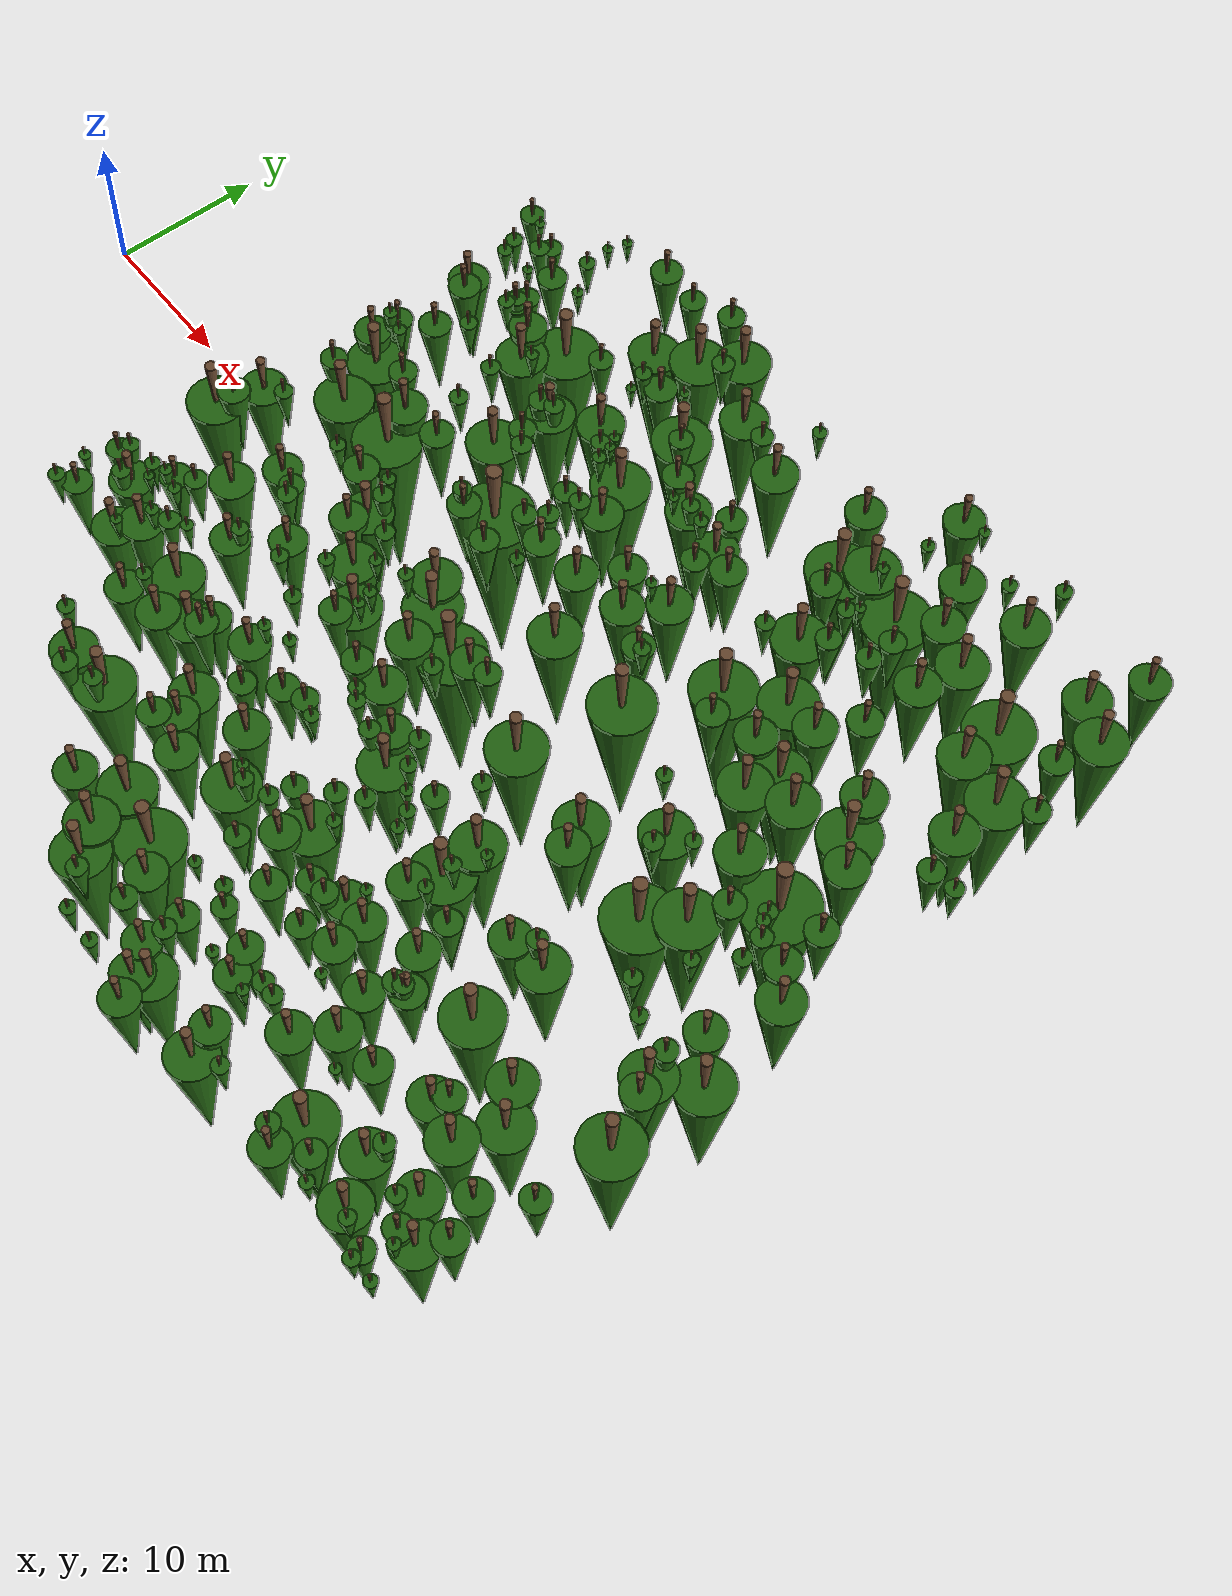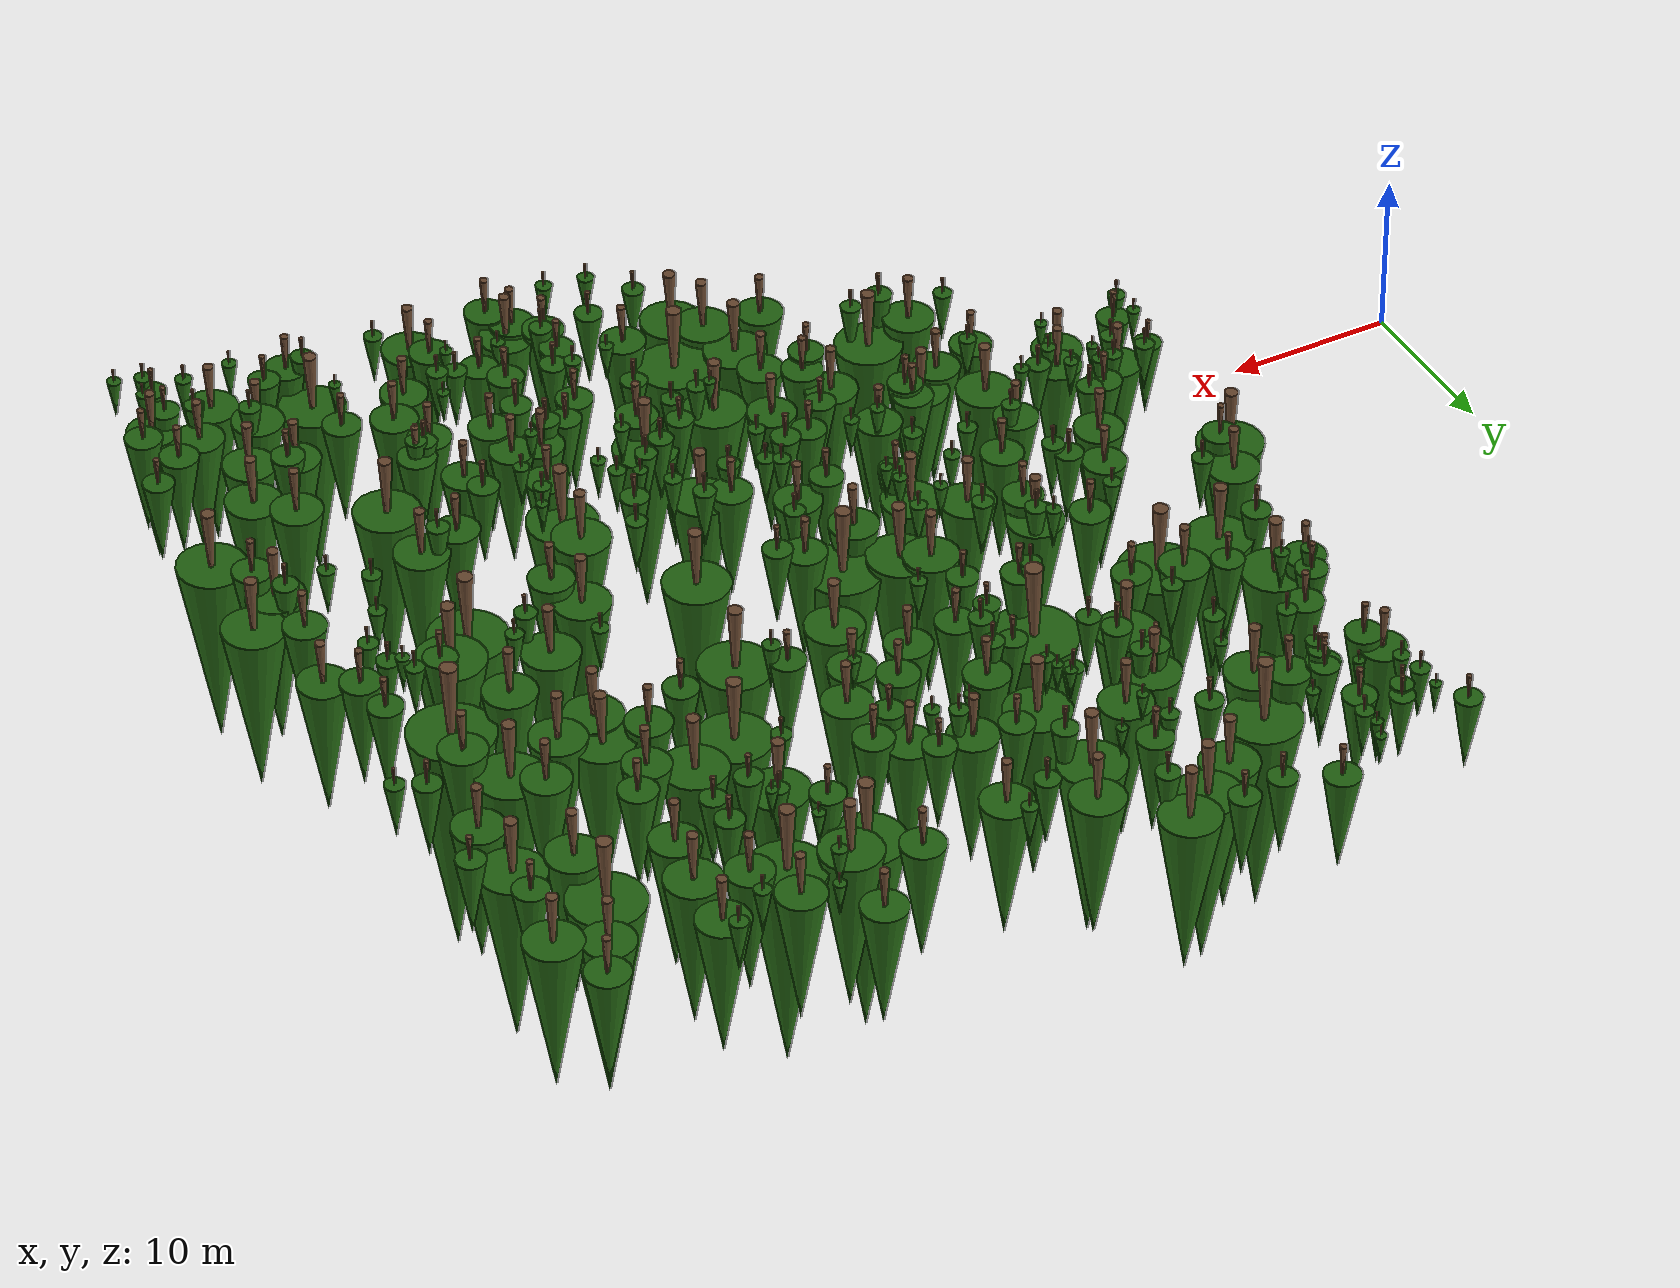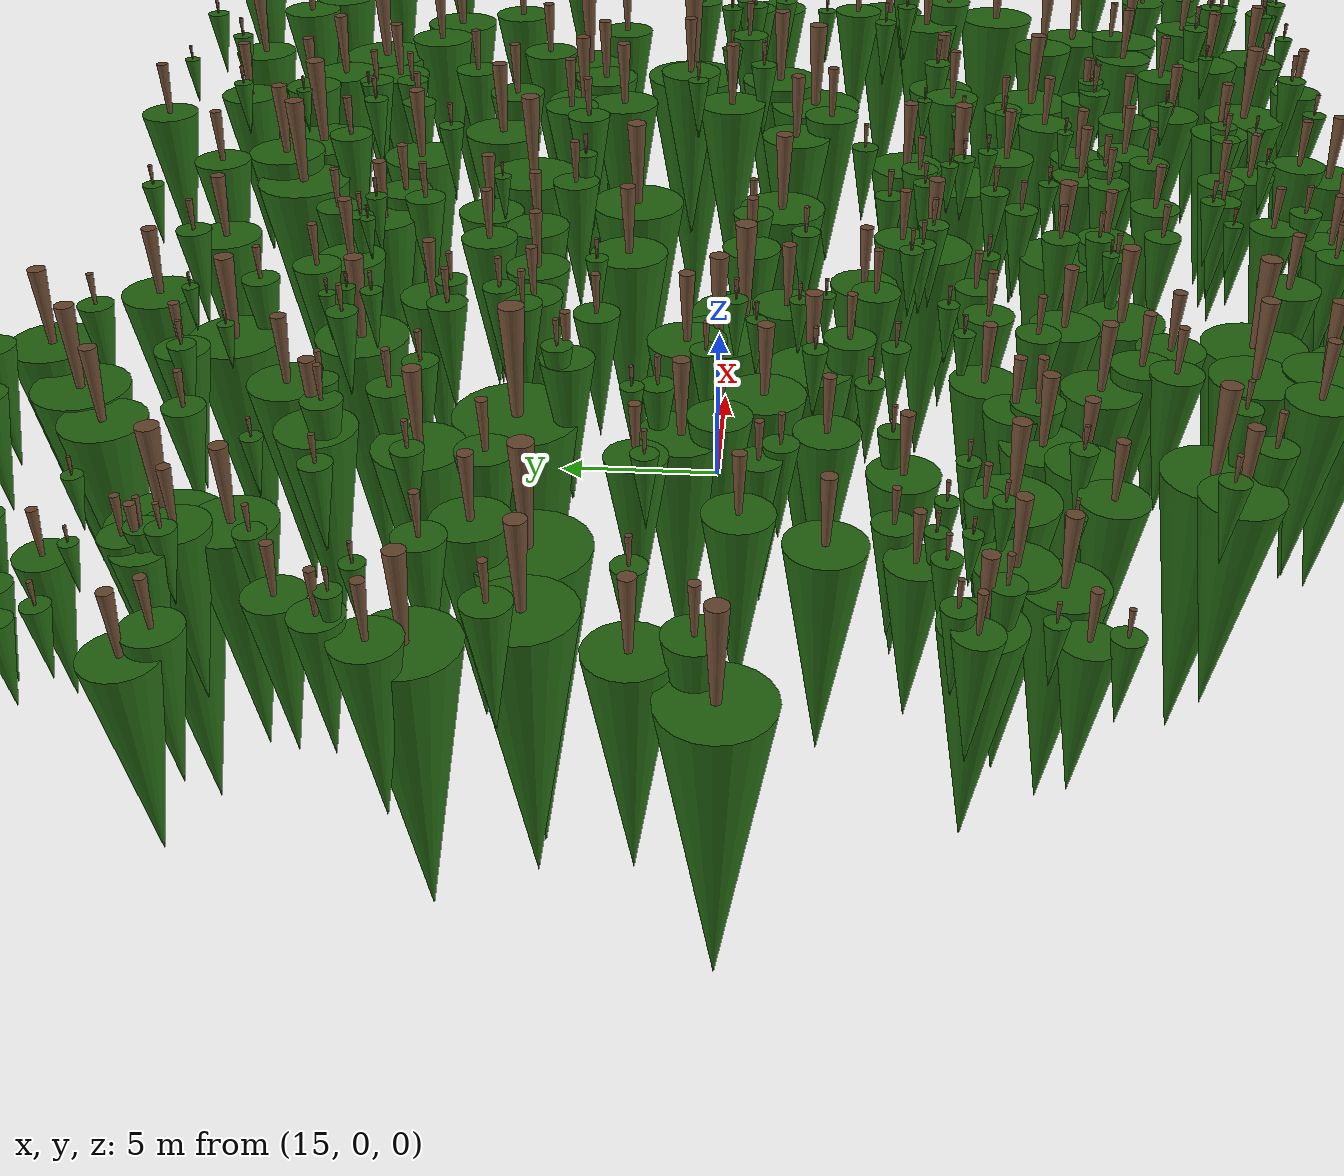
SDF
<?xml version="1.0" ?>
<!-- auto generated by generate_model_sdf.py -->
<sdf version="1.10">

<model name="lehrforst_trees">

<static>true</static>

  <link name='tree_0003'>
    <collision name='tree_0003_collision'>
      <pose>28.569 8.946 -5.416 3.142 0.028 0</pose>
      <geometry>
        <cone>
          <radius>0.545</radius>
          <length>8.720</length>
        </cone>
      </geometry>
    </collision>
    <visual name='tree_0003_trunk'>
      <pose>28.569 8.946 -5.416 3.142 0.028 0</pose>
      <geometry>
        <cone>
          <radius>0.545</radius>
          <length>8.720</length>
        </cone>
      </geometry>
      <material>
        <ambient>0.42 0.29 0.19 1</ambient>
        <diffuse>0.42 0.29 0.19 1</diffuse>
        <specular>0.42 0.29 0.19 1</specular>
      </material>
    </visual>
    <visual name='tree_0003_leaves'>
      <pose>28.569 8.946 -14.136 3.142 0 0</pose>
      <geometry>
        <cone>
          <radius>2.725</radius>
          <length>16.350</length>
        </cone>
      </geometry>
      <material>
        <ambient>0.14 0.40 0.07 1</ambient>
        <diffuse>0.14 0.40 0.07 1</diffuse>
        <specular>0.14 0.40 0.07 1</specular>
      </material>
    </visual>
  </link>

  <link name='tree_0008'>
    <collision name='tree_0008_collision'>
      <pose>63.142 3.854 -2.577 3.142 0.009 0</pose>
      <geometry>
        <cone>
          <radius>0.523</radius>
          <length>8.368</length>
        </cone>
      </geometry>
    </collision>
    <visual name='tree_0008_trunk'>
      <pose>63.142 3.854 -2.577 3.142 0.009 0</pose>
      <geometry>
        <cone>
          <radius>0.523</radius>
          <length>8.368</length>
        </cone>
      </geometry>
      <material>
        <ambient>0.42 0.29 0.19 1</ambient>
        <diffuse>0.42 0.29 0.19 1</diffuse>
        <specular>0.42 0.29 0.19 1</specular>
      </material>
    </visual>
    <visual name='tree_0008_leaves'>
      <pose>63.142 3.854 -10.945 3.142 0 0</pose>
      <geometry>
        <cone>
          <radius>2.615</radius>
          <length>15.690</length>
        </cone>
      </geometry>
      <material>
        <ambient>0.14 0.40 0.07 1</ambient>
        <diffuse>0.14 0.40 0.07 1</diffuse>
        <specular>0.14 0.40 0.07 1</specular>
      </material>
    </visual>
  </link>

  <link name='tree_0011'>
    <collision name='tree_0011_collision'>
      <pose>19.209 7.130 -5.545 3.142 0.007 0</pose>
      <geometry>
        <cone>
          <radius>0.492</radius>
          <length>7.872</length>
        </cone>
      </geometry>
    </collision>
    <visual name='tree_0011_trunk'>
      <pose>19.209 7.130 -5.545 3.142 0.007 0</pose>
      <geometry>
        <cone>
          <radius>0.492</radius>
          <length>7.872</length>
        </cone>
      </geometry>
      <material>
        <ambient>0.42 0.29 0.19 1</ambient>
        <diffuse>0.42 0.29 0.19 1</diffuse>
        <specular>0.42 0.29 0.19 1</specular>
      </material>
    </visual>
    <visual name='tree_0011_leaves'>
      <pose>19.209 7.130 -13.417 3.142 0 0</pose>
      <geometry>
        <cone>
          <radius>2.460</radius>
          <length>14.760</length>
        </cone>
      </geometry>
      <material>
        <ambient>0.14 0.40 0.07 1</ambient>
        <diffuse>0.14 0.40 0.07 1</diffuse>
        <specular>0.14 0.40 0.07 1</specular>
      </material>
    </visual>
  </link>

  <link name='tree_0013'>
    <collision name='tree_0013_collision'>
      <pose>58.567 -3.165 -2.569 3.142 0.017 0</pose>
      <geometry>
        <cone>
          <radius>0.486</radius>
          <length>7.776</length>
        </cone>
      </geometry>
    </collision>
    <visual name='tree_0013_trunk'>
      <pose>58.567 -3.165 -2.569 3.142 0.017 0</pose>
      <geometry>
        <cone>
          <radius>0.486</radius>
          <length>7.776</length>
        </cone>
      </geometry>
      <material>
        <ambient>0.42 0.29 0.19 1</ambient>
        <diffuse>0.42 0.29 0.19 1</diffuse>
        <specular>0.42 0.29 0.19 1</specular>
      </material>
    </visual>
    <visual name='tree_0013_leaves'>
      <pose>58.567 -3.165 -10.345 3.142 0 0</pose>
      <geometry>
        <cone>
          <radius>2.430</radius>
          <length>14.580</length>
        </cone>
      </geometry>
      <material>
        <ambient>0.14 0.40 0.07 1</ambient>
        <diffuse>0.14 0.40 0.07 1</diffuse>
        <specular>0.14 0.40 0.07 1</specular>
      </material>
    </visual>
  </link>

  <link name='tree_0015'>
    <collision name='tree_0015_collision'>
      <pose>36.035 -0.141 -4.305 3.142 0.002 0</pose>
      <geometry>
        <cone>
          <radius>0.478</radius>
          <length>7.648</length>
        </cone>
      </geometry>
    </collision>
    <visual name='tree_0015_trunk'>
      <pose>36.035 -0.141 -4.305 3.142 0.002 0</pose>
      <geometry>
        <cone>
          <radius>0.478</radius>
          <length>7.648</length>
        </cone>
      </geometry>
      <material>
        <ambient>0.42 0.29 0.19 1</ambient>
        <diffuse>0.42 0.29 0.19 1</diffuse>
        <specular>0.42 0.29 0.19 1</specular>
      </material>
    </visual>
    <visual name='tree_0015_leaves'>
      <pose>36.035 -0.141 -11.953 3.142 0 0</pose>
      <geometry>
        <cone>
          <radius>2.390</radius>
          <length>14.340</length>
        </cone>
      </geometry>
      <material>
        <ambient>0.14 0.40 0.07 1</ambient>
        <diffuse>0.14 0.40 0.07 1</diffuse>
        <specular>0.14 0.40 0.07 1</specular>
      </material>
    </visual>
  </link>

  <link name='tree_0019'>
    <collision name='tree_0019_collision'>
      <pose>52.082 22.715 -2.816 3.142 0.006 0</pose>
      <geometry>
        <cone>
          <radius>0.472</radius>
          <length>7.552</length>
        </cone>
      </geometry>
    </collision>
    <visual name='tree_0019_trunk'>
      <pose>52.082 22.715 -2.816 3.142 0.006 0</pose>
      <geometry>
        <cone>
          <radius>0.472</radius>
          <length>7.552</length>
        </cone>
      </geometry>
      <material>
        <ambient>0.42 0.29 0.19 1</ambient>
        <diffuse>0.42 0.29 0.19 1</diffuse>
        <specular>0.42 0.29 0.19 1</specular>
      </material>
    </visual>
    <visual name='tree_0019_leaves'>
      <pose>52.082 22.715 -10.368 3.142 0 0</pose>
      <geometry>
        <cone>
          <radius>2.360</radius>
          <length>14.160</length>
        </cone>
      </geometry>
      <material>
        <ambient>0.14 0.40 0.07 1</ambient>
        <diffuse>0.14 0.40 0.07 1</diffuse>
        <specular>0.14 0.40 0.07 1</specular>
      </material>
    </visual>
  </link>

  <link name='tree_0021'>
    <collision name='tree_0021_collision'>
      <pose>62.606 21.554 -1.598 3.142 0.021 0</pose>
      <geometry>
        <cone>
          <radius>0.469</radius>
          <length>7.504</length>
        </cone>
      </geometry>
    </collision>
    <visual name='tree_0021_trunk'>
      <pose>62.606 21.554 -1.598 3.142 0.021 0</pose>
      <geometry>
        <cone>
          <radius>0.469</radius>
          <length>7.504</length>
        </cone>
      </geometry>
      <material>
        <ambient>0.42 0.29 0.19 1</ambient>
        <diffuse>0.42 0.29 0.19 1</diffuse>
        <specular>0.42 0.29 0.19 1</specular>
      </material>
    </visual>
    <visual name='tree_0021_leaves'>
      <pose>62.606 21.554 -9.102 3.142 0 0</pose>
      <geometry>
        <cone>
          <radius>2.345</radius>
          <length>14.070</length>
        </cone>
      </geometry>
      <material>
        <ambient>0.14 0.40 0.07 1</ambient>
        <diffuse>0.14 0.40 0.07 1</diffuse>
        <specular>0.14 0.40 0.07 1</specular>
      </material>
    </visual>
  </link>

  <link name='tree_0026'>
    <collision name='tree_0026_collision'>
      <pose>20.560 21.103 -6.016 3.142 0.017 0</pose>
      <geometry>
        <cone>
          <radius>0.464</radius>
          <length>7.424</length>
        </cone>
      </geometry>
    </collision>
    <visual name='tree_0026_trunk'>
      <pose>20.560 21.103 -6.016 3.142 0.017 0</pose>
      <geometry>
        <cone>
          <radius>0.464</radius>
          <length>7.424</length>
        </cone>
      </geometry>
      <material>
        <ambient>0.42 0.29 0.19 1</ambient>
        <diffuse>0.42 0.29 0.19 1</diffuse>
        <specular>0.42 0.29 0.19 1</specular>
      </material>
    </visual>
    <visual name='tree_0026_leaves'>
      <pose>20.560 21.103 -13.440 3.142 0 0</pose>
      <geometry>
        <cone>
          <radius>2.320</radius>
          <length>13.920</length>
        </cone>
      </geometry>
      <material>
        <ambient>0.14 0.40 0.07 1</ambient>
        <diffuse>0.14 0.40 0.07 1</diffuse>
        <specular>0.14 0.40 0.07 1</specular>
      </material>
    </visual>
  </link>

  <link name='tree_0034'>
    <collision name='tree_0034_collision'>
      <pose>35.260 -22.294 -4.820 3.142 0.003 0</pose>
      <geometry>
        <cone>
          <radius>0.460</radius>
          <length>7.360</length>
        </cone>
      </geometry>
    </collision>
    <visual name='tree_0034_trunk'>
      <pose>35.260 -22.294 -4.820 3.142 0.003 0</pose>
      <geometry>
        <cone>
          <radius>0.460</radius>
          <length>7.360</length>
        </cone>
      </geometry>
      <material>
        <ambient>0.42 0.29 0.19 1</ambient>
        <diffuse>0.42 0.29 0.19 1</diffuse>
        <specular>0.42 0.29 0.19 1</specular>
      </material>
    </visual>
    <visual name='tree_0034_leaves'>
      <pose>35.260 -22.294 -12.180 3.142 0 0</pose>
      <geometry>
        <cone>
          <radius>2.300</radius>
          <length>13.800</length>
        </cone>
      </geometry>
      <material>
        <ambient>0.14 0.40 0.07 1</ambient>
        <diffuse>0.14 0.40 0.07 1</diffuse>
        <specular>0.14 0.40 0.07 1</specular>
      </material>
    </visual>
  </link>

  <link name='tree_0035'>
    <collision name='tree_0035_collision'>
      <pose>46.962 22.473 -3.054 3.142 0.028 0</pose>
      <geometry>
        <cone>
          <radius>0.458</radius>
          <length>7.328</length>
        </cone>
      </geometry>
    </collision>
    <visual name='tree_0035_trunk'>
      <pose>46.962 22.473 -3.054 3.142 0.028 0</pose>
      <geometry>
        <cone>
          <radius>0.458</radius>
          <length>7.328</length>
        </cone>
      </geometry>
      <material>
        <ambient>0.42 0.29 0.19 1</ambient>
        <diffuse>0.42 0.29 0.19 1</diffuse>
        <specular>0.42 0.29 0.19 1</specular>
      </material>
    </visual>
    <visual name='tree_0035_leaves'>
      <pose>46.962 22.473 -10.382 3.142 0 0</pose>
      <geometry>
        <cone>
          <radius>2.290</radius>
          <length>13.740</length>
        </cone>
      </geometry>
      <material>
        <ambient>0.14 0.40 0.07 1</ambient>
        <diffuse>0.14 0.40 0.07 1</diffuse>
        <specular>0.14 0.40 0.07 1</specular>
      </material>
    </visual>
  </link>

  <link name='tree_0040'>
    <collision name='tree_0040_collision'>
      <pose>49.152 11.139 -3.291 3.142 0.004 0</pose>
      <geometry>
        <cone>
          <radius>0.453</radius>
          <length>7.248</length>
        </cone>
      </geometry>
    </collision>
    <visual name='tree_0040_trunk'>
      <pose>49.152 11.139 -3.291 3.142 0.004 0</pose>
      <geometry>
        <cone>
          <radius>0.453</radius>
          <length>7.248</length>
        </cone>
      </geometry>
      <material>
        <ambient>0.42 0.29 0.19 1</ambient>
        <diffuse>0.42 0.29 0.19 1</diffuse>
        <specular>0.42 0.29 0.19 1</specular>
      </material>
    </visual>
    <visual name='tree_0040_leaves'>
      <pose>49.152 11.139 -10.539 3.142 0 0</pose>
      <geometry>
        <cone>
          <radius>2.265</radius>
          <length>13.590</length>
        </cone>
      </geometry>
      <material>
        <ambient>0.14 0.40 0.07 1</ambient>
        <diffuse>0.14 0.40 0.07 1</diffuse>
        <specular>0.14 0.40 0.07 1</specular>
      </material>
    </visual>
  </link>

  <link name='tree_0041'>
    <collision name='tree_0041_collision'>
      <pose>46.069 5.531 -3.400 3.142 0.001 0</pose>
      <geometry>
        <cone>
          <radius>0.452</radius>
          <length>7.232</length>
        </cone>
      </geometry>
    </collision>
    <visual name='tree_0041_trunk'>
      <pose>46.069 5.531 -3.400 3.142 0.001 0</pose>
      <geometry>
        <cone>
          <radius>0.452</radius>
          <length>7.232</length>
        </cone>
      </geometry>
      <material>
        <ambient>0.42 0.29 0.19 1</ambient>
        <diffuse>0.42 0.29 0.19 1</diffuse>
        <specular>0.42 0.29 0.19 1</specular>
      </material>
    </visual>
    <visual name='tree_0041_leaves'>
      <pose>46.069 5.531 -10.632 3.142 0 0</pose>
      <geometry>
        <cone>
          <radius>2.260</radius>
          <length>13.560</length>
        </cone>
      </geometry>
      <material>
        <ambient>0.14 0.40 0.07 1</ambient>
        <diffuse>0.14 0.40 0.07 1</diffuse>
        <specular>0.14 0.40 0.07 1</specular>
      </material>
    </visual>
  </link>

  <link name='tree_0060'>
    <collision name='tree_0060_collision'>
      <pose>48.872 -10.303 -3.029 3.142 0.029 0</pose>
      <geometry>
        <cone>
          <radius>0.433</radius>
          <length>6.928</length>
        </cone>
      </geometry>
    </collision>
    <visual name='tree_0060_trunk'>
      <pose>48.872 -10.303 -3.029 3.142 0.029 0</pose>
      <geometry>
        <cone>
          <radius>0.433</radius>
          <length>6.928</length>
        </cone>
      </geometry>
      <material>
        <ambient>0.42 0.29 0.19 1</ambient>
        <diffuse>0.42 0.29 0.19 1</diffuse>
        <specular>0.42 0.29 0.19 1</specular>
      </material>
    </visual>
    <visual name='tree_0060_leaves'>
      <pose>48.872 -10.303 -9.957 3.142 0 0</pose>
      <geometry>
        <cone>
          <radius>2.165</radius>
          <length>12.990</length>
        </cone>
      </geometry>
      <material>
        <ambient>0.14 0.40 0.07 1</ambient>
        <diffuse>0.14 0.40 0.07 1</diffuse>
        <specular>0.14 0.40 0.07 1</specular>
      </material>
    </visual>
  </link>

  <link name='tree_0071'>
    <collision name='tree_0071_collision'>
      <pose>60.635 -1.175 -1.958 3.142 0.021 0</pose>
      <geometry>
        <cone>
          <radius>0.423</radius>
          <length>6.768</length>
        </cone>
      </geometry>
    </collision>
    <visual name='tree_0071_trunk'>
      <pose>60.635 -1.175 -1.958 3.142 0.021 0</pose>
      <geometry>
        <cone>
          <radius>0.423</radius>
          <length>6.768</length>
        </cone>
      </geometry>
      <material>
        <ambient>0.42 0.29 0.19 1</ambient>
        <diffuse>0.42 0.29 0.19 1</diffuse>
        <specular>0.42 0.29 0.19 1</specular>
      </material>
    </visual>
    <visual name='tree_0071_leaves'>
      <pose>60.635 -1.175 -8.726 3.142 0 0</pose>
      <geometry>
        <cone>
          <radius>2.115</radius>
          <length>12.690</length>
        </cone>
      </geometry>
      <material>
        <ambient>0.14 0.40 0.07 1</ambient>
        <diffuse>0.14 0.40 0.07 1</diffuse>
        <specular>0.14 0.40 0.07 1</specular>
      </material>
    </visual>
  </link>

  <link name='tree_0076'>
    <collision name='tree_0076_collision'>
      <pose>69.408 -13.844 -0.876 3.142 0.017 0</pose>
      <geometry>
        <cone>
          <radius>0.420</radius>
          <length>6.720</length>
        </cone>
      </geometry>
    </collision>
    <visual name='tree_0076_trunk'>
      <pose>69.408 -13.844 -0.876 3.142 0.017 0</pose>
      <geometry>
        <cone>
          <radius>0.420</radius>
          <length>6.720</length>
        </cone>
      </geometry>
      <material>
        <ambient>0.42 0.29 0.19 1</ambient>
        <diffuse>0.42 0.29 0.19 1</diffuse>
        <specular>0.42 0.29 0.19 1</specular>
      </material>
    </visual>
    <visual name='tree_0076_leaves'>
      <pose>69.408 -13.844 -7.596 3.142 0 0</pose>
      <geometry>
        <cone>
          <radius>2.100</radius>
          <length>12.600</length>
        </cone>
      </geometry>
      <material>
        <ambient>0.14 0.40 0.07 1</ambient>
        <diffuse>0.14 0.40 0.07 1</diffuse>
        <specular>0.14 0.40 0.07 1</specular>
      </material>
    </visual>
  </link>

  <link name='tree_0080'>
    <collision name='tree_0080_collision'>
      <pose>24.254 -18.389 -4.615 3.142 0.018 0</pose>
      <geometry>
        <cone>
          <radius>0.419</radius>
          <length>6.704</length>
        </cone>
      </geometry>
    </collision>
    <visual name='tree_0080_trunk'>
      <pose>24.254 -18.389 -4.615 3.142 0.018 0</pose>
      <geometry>
        <cone>
          <radius>0.419</radius>
          <length>6.704</length>
        </cone>
      </geometry>
      <material>
        <ambient>0.42 0.29 0.19 1</ambient>
        <diffuse>0.42 0.29 0.19 1</diffuse>
        <specular>0.42 0.29 0.19 1</specular>
      </material>
    </visual>
    <visual name='tree_0080_leaves'>
      <pose>24.254 -18.389 -11.319 3.142 0 0</pose>
      <geometry>
        <cone>
          <radius>2.095</radius>
          <length>12.570</length>
        </cone>
      </geometry>
      <material>
        <ambient>0.14 0.40 0.07 1</ambient>
        <diffuse>0.14 0.40 0.07 1</diffuse>
        <specular>0.14 0.40 0.07 1</specular>
      </material>
    </visual>
  </link>

  <link name='tree_0083'>
    <collision name='tree_0083_collision'>
      <pose>62.414 9.743 -1.766 3.142 0.008 0</pose>
      <geometry>
        <cone>
          <radius>0.416</radius>
          <length>6.656</length>
        </cone>
      </geometry>
    </collision>
    <visual name='tree_0083_trunk'>
      <pose>62.414 9.743 -1.766 3.142 0.008 0</pose>
      <geometry>
        <cone>
          <radius>0.416</radius>
          <length>6.656</length>
        </cone>
      </geometry>
      <material>
        <ambient>0.42 0.29 0.19 1</ambient>
        <diffuse>0.42 0.29 0.19 1</diffuse>
        <specular>0.42 0.29 0.19 1</specular>
      </material>
    </visual>
    <visual name='tree_0083_leaves'>
      <pose>62.414 9.743 -8.422 3.142 0 0</pose>
      <geometry>
        <cone>
          <radius>2.080</radius>
          <length>12.480</length>
        </cone>
      </geometry>
      <material>
        <ambient>0.14 0.40 0.07 1</ambient>
        <diffuse>0.14 0.40 0.07 1</diffuse>
        <specular>0.14 0.40 0.07 1</specular>
      </material>
    </visual>
  </link>

  <link name='tree_0085'>
    <collision name='tree_0085_collision'>
      <pose>32.181 21.663 -4.247 3.142 0.032 0</pose>
      <geometry>
        <cone>
          <radius>0.414</radius>
          <length>6.624</length>
        </cone>
      </geometry>
    </collision>
    <visual name='tree_0085_trunk'>
      <pose>32.181 21.663 -4.247 3.142 0.032 0</pose>
      <geometry>
        <cone>
          <radius>0.414</radius>
          <length>6.624</length>
        </cone>
      </geometry>
      <material>
        <ambient>0.42 0.29 0.19 1</ambient>
        <diffuse>0.42 0.29 0.19 1</diffuse>
        <specular>0.42 0.29 0.19 1</specular>
      </material>
    </visual>
    <visual name='tree_0085_leaves'>
      <pose>32.181 21.663 -10.871 3.142 0 0</pose>
      <geometry>
        <cone>
          <radius>2.070</radius>
          <length>12.420</length>
        </cone>
      </geometry>
      <material>
        <ambient>0.14 0.40 0.07 1</ambient>
        <diffuse>0.14 0.40 0.07 1</diffuse>
        <specular>0.14 0.40 0.07 1</specular>
      </material>
    </visual>
  </link>

  <link name='tree_0088'>
    <collision name='tree_0088_collision'>
      <pose>13.372 10.431 -5.669 3.142 0.033 0</pose>
      <geometry>
        <cone>
          <radius>0.413</radius>
          <length>6.608</length>
        </cone>
      </geometry>
    </collision>
    <visual name='tree_0088_trunk'>
      <pose>13.372 10.431 -5.669 3.142 0.033 0</pose>
      <geometry>
        <cone>
          <radius>0.413</radius>
          <length>6.608</length>
        </cone>
      </geometry>
      <material>
        <ambient>0.42 0.29 0.19 1</ambient>
        <diffuse>0.42 0.29 0.19 1</diffuse>
        <specular>0.42 0.29 0.19 1</specular>
      </material>
    </visual>
    <visual name='tree_0088_leaves'>
      <pose>13.372 10.431 -12.277 3.142 0 0</pose>
      <geometry>
        <cone>
          <radius>2.065</radius>
          <length>12.390</length>
        </cone>
      </geometry>
      <material>
        <ambient>0.14 0.40 0.07 1</ambient>
        <diffuse>0.14 0.40 0.07 1</diffuse>
        <specular>0.14 0.40 0.07 1</specular>
      </material>
    </visual>
  </link>

  <link name='tree_0092'>
    <collision name='tree_0092_collision'>
      <pose>10.021 -0.234 -4.865 3.142 0.021 0</pose>
      <geometry>
        <cone>
          <radius>0.412</radius>
          <length>6.592</length>
        </cone>
      </geometry>
    </collision>
    <visual name='tree_0092_trunk'>
      <pose>10.021 -0.234 -4.865 3.142 0.021 0</pose>
      <geometry>
        <cone>
          <radius>0.412</radius>
          <length>6.592</length>
        </cone>
      </geometry>
      <material>
        <ambient>0.42 0.29 0.19 1</ambient>
        <diffuse>0.42 0.29 0.19 1</diffuse>
        <specular>0.42 0.29 0.19 1</specular>
      </material>
    </visual>
    <visual name='tree_0092_leaves'>
      <pose>10.021 -0.234 -11.457 3.142 0 0</pose>
      <geometry>
        <cone>
          <radius>2.060</radius>
          <length>12.360</length>
        </cone>
      </geometry>
      <material>
        <ambient>0.14 0.40 0.07 1</ambient>
        <diffuse>0.14 0.40 0.07 1</diffuse>
        <specular>0.14 0.40 0.07 1</specular>
      </material>
    </visual>
  </link>

  <link name='tree_0093'>
    <collision name='tree_0093_collision'>
      <pose>14.920 6.676 -5.272 3.142 0.005 0</pose>
      <geometry>
        <cone>
          <radius>0.412</radius>
          <length>6.592</length>
        </cone>
      </geometry>
    </collision>
    <visual name='tree_0093_trunk'>
      <pose>14.920 6.676 -5.272 3.142 0.005 0</pose>
      <geometry>
        <cone>
          <radius>0.412</radius>
          <length>6.592</length>
        </cone>
      </geometry>
      <material>
        <ambient>0.42 0.29 0.19 1</ambient>
        <diffuse>0.42 0.29 0.19 1</diffuse>
        <specular>0.42 0.29 0.19 1</specular>
      </material>
    </visual>
    <visual name='tree_0093_leaves'>
      <pose>14.920 6.676 -11.864 3.142 0 0</pose>
      <geometry>
        <cone>
          <radius>2.060</radius>
          <length>12.360</length>
        </cone>
      </geometry>
      <material>
        <ambient>0.14 0.40 0.07 1</ambient>
        <diffuse>0.14 0.40 0.07 1</diffuse>
        <specular>0.14 0.40 0.07 1</specular>
      </material>
    </visual>
  </link>

  <link name='tree_0094'>
    <collision name='tree_0094_collision'>
      <pose>57.165 -26.080 -2.358 3.142 0.011 0</pose>
      <geometry>
        <cone>
          <radius>0.412</radius>
          <length>6.592</length>
        </cone>
      </geometry>
    </collision>
    <visual name='tree_0094_trunk'>
      <pose>57.165 -26.080 -2.358 3.142 0.011 0</pose>
      <geometry>
        <cone>
          <radius>0.412</radius>
          <length>6.592</length>
        </cone>
      </geometry>
      <material>
        <ambient>0.42 0.29 0.19 1</ambient>
        <diffuse>0.42 0.29 0.19 1</diffuse>
        <specular>0.42 0.29 0.19 1</specular>
      </material>
    </visual>
    <visual name='tree_0094_leaves'>
      <pose>57.165 -26.080 -8.950 3.142 0 0</pose>
      <geometry>
        <cone>
          <radius>2.060</radius>
          <length>12.360</length>
        </cone>
      </geometry>
      <material>
        <ambient>0.14 0.40 0.07 1</ambient>
        <diffuse>0.14 0.40 0.07 1</diffuse>
        <specular>0.14 0.40 0.07 1</specular>
      </material>
    </visual>
  </link>

  <link name='tree_0095'>
    <collision name='tree_0095_collision'>
      <pose>44.750 -1.610 -2.992 3.142 0.022 0</pose>
      <geometry>
        <cone>
          <radius>0.411</radius>
          <length>6.576</length>
        </cone>
      </geometry>
    </collision>
    <visual name='tree_0095_trunk'>
      <pose>44.750 -1.610 -2.992 3.142 0.022 0</pose>
      <geometry>
        <cone>
          <radius>0.411</radius>
          <length>6.576</length>
        </cone>
      </geometry>
      <material>
        <ambient>0.42 0.29 0.19 1</ambient>
        <diffuse>0.42 0.29 0.19 1</diffuse>
        <specular>0.42 0.29 0.19 1</specular>
      </material>
    </visual>
    <visual name='tree_0095_leaves'>
      <pose>44.750 -1.610 -9.568 3.142 0 0</pose>
      <geometry>
        <cone>
          <radius>2.055</radius>
          <length>12.330</length>
        </cone>
      </geometry>
      <material>
        <ambient>0.14 0.40 0.07 1</ambient>
        <diffuse>0.14 0.40 0.07 1</diffuse>
        <specular>0.14 0.40 0.07 1</specular>
      </material>
    </visual>
  </link>

  <link name='tree_0099'>
    <collision name='tree_0099_collision'>
      <pose>32.546 16.219 -4.222 3.142 0.024 0</pose>
      <geometry>
        <cone>
          <radius>0.409</radius>
          <length>6.544</length>
        </cone>
      </geometry>
    </collision>
    <visual name='tree_0099_trunk'>
      <pose>32.546 16.219 -4.222 3.142 0.024 0</pose>
      <geometry>
        <cone>
          <radius>0.409</radius>
          <length>6.544</length>
        </cone>
      </geometry>
      <material>
        <ambient>0.42 0.29 0.19 1</ambient>
        <diffuse>0.42 0.29 0.19 1</diffuse>
        <specular>0.42 0.29 0.19 1</specular>
      </material>
    </visual>
    <visual name='tree_0099_leaves'>
      <pose>32.546 16.219 -10.766 3.142 0 0</pose>
      <geometry>
        <cone>
          <radius>2.045</radius>
          <length>12.270</length>
        </cone>
      </geometry>
      <material>
        <ambient>0.14 0.40 0.07 1</ambient>
        <diffuse>0.14 0.40 0.07 1</diffuse>
        <specular>0.14 0.40 0.07 1</specular>
      </material>
    </visual>
  </link>

  <link name='tree_0100'>
    <collision name='tree_0100_collision'>
      <pose>32.823 0.866 -3.861 3.142 0.037 0</pose>
      <geometry>
        <cone>
          <radius>0.409</radius>
          <length>6.544</length>
        </cone>
      </geometry>
    </collision>
    <visual name='tree_0100_trunk'>
      <pose>32.823 0.866 -3.861 3.142 0.037 0</pose>
      <geometry>
        <cone>
          <radius>0.409</radius>
          <length>6.544</length>
        </cone>
      </geometry>
      <material>
        <ambient>0.42 0.29 0.19 1</ambient>
        <diffuse>0.42 0.29 0.19 1</diffuse>
        <specular>0.42 0.29 0.19 1</specular>
      </material>
    </visual>
    <visual name='tree_0100_leaves'>
      <pose>32.823 0.866 -10.405 3.142 0 0</pose>
      <geometry>
        <cone>
          <radius>2.045</radius>
          <length>12.270</length>
        </cone>
      </geometry>
      <material>
        <ambient>0.14 0.40 0.07 1</ambient>
        <diffuse>0.14 0.40 0.07 1</diffuse>
        <specular>0.14 0.40 0.07 1</specular>
      </material>
    </visual>
  </link>

  <link name='tree_0104'>
    <collision name='tree_0104_collision'>
      <pose>57.872 -14.827 -2.043 3.142 0.002 0</pose>
      <geometry>
        <cone>
          <radius>0.407</radius>
          <length>6.512</length>
        </cone>
      </geometry>
    </collision>
    <visual name='tree_0104_trunk'>
      <pose>57.872 -14.827 -2.043 3.142 0.002 0</pose>
      <geometry>
        <cone>
          <radius>0.407</radius>
          <length>6.512</length>
        </cone>
      </geometry>
      <material>
        <ambient>0.42 0.29 0.19 1</ambient>
        <diffuse>0.42 0.29 0.19 1</diffuse>
        <specular>0.42 0.29 0.19 1</specular>
      </material>
    </visual>
    <visual name='tree_0104_leaves'>
      <pose>57.872 -14.827 -8.555 3.142 0 0</pose>
      <geometry>
        <cone>
          <radius>2.035</radius>
          <length>12.210</length>
        </cone>
      </geometry>
      <material>
        <ambient>0.14 0.40 0.07 1</ambient>
        <diffuse>0.14 0.40 0.07 1</diffuse>
        <specular>0.14 0.40 0.07 1</specular>
      </material>
    </visual>
  </link>

  <link name='tree_0107'>
    <collision name='tree_0107_collision'>
      <pose>27.715 26.800 -4.414 3.142 0.035 0</pose>
      <geometry>
        <cone>
          <radius>0.405</radius>
          <length>6.480</length>
        </cone>
      </geometry>
    </collision>
    <visual name='tree_0107_trunk'>
      <pose>27.715 26.800 -4.414 3.142 0.035 0</pose>
      <geometry>
        <cone>
          <radius>0.405</radius>
          <length>6.480</length>
        </cone>
      </geometry>
      <material>
        <ambient>0.42 0.29 0.19 1</ambient>
        <diffuse>0.42 0.29 0.19 1</diffuse>
        <specular>0.42 0.29 0.19 1</specular>
      </material>
    </visual>
    <visual name='tree_0107_leaves'>
      <pose>27.715 26.800 -10.894 3.142 0 0</pose>
      <geometry>
        <cone>
          <radius>2.025</radius>
          <length>12.150</length>
        </cone>
      </geometry>
      <material>
        <ambient>0.14 0.40 0.07 1</ambient>
        <diffuse>0.14 0.40 0.07 1</diffuse>
        <specular>0.14 0.40 0.07 1</specular>
      </material>
    </visual>
  </link>

  <link name='tree_0115'>
    <collision name='tree_0115_collision'>
      <pose>66.375 17.798 -0.910 3.142 0.009 0</pose>
      <geometry>
        <cone>
          <radius>0.400</radius>
          <length>6.400</length>
        </cone>
      </geometry>
    </collision>
    <visual name='tree_0115_trunk'>
      <pose>66.375 17.798 -0.910 3.142 0.009 0</pose>
      <geometry>
        <cone>
          <radius>0.400</radius>
          <length>6.400</length>
        </cone>
      </geometry>
      <material>
        <ambient>0.42 0.29 0.19 1</ambient>
        <diffuse>0.42 0.29 0.19 1</diffuse>
        <specular>0.42 0.29 0.19 1</specular>
      </material>
    </visual>
    <visual name='tree_0115_leaves'>
      <pose>66.375 17.798 -7.310 3.142 0 0</pose>
      <geometry>
        <cone>
          <radius>2.000</radius>
          <length>12.000</length>
        </cone>
      </geometry>
      <material>
        <ambient>0.14 0.40 0.07 1</ambient>
        <diffuse>0.14 0.40 0.07 1</diffuse>
        <specular>0.14 0.40 0.07 1</specular>
      </material>
    </visual>
  </link>

  <link name='tree_0118'>
    <collision name='tree_0118_collision'>
      <pose>52.779 13.260 -2.447 3.142 0.025 0</pose>
      <geometry>
        <cone>
          <radius>0.399</radius>
          <length>6.384</length>
        </cone>
      </geometry>
    </collision>
    <visual name='tree_0118_trunk'>
      <pose>52.779 13.260 -2.447 3.142 0.025 0</pose>
      <geometry>
        <cone>
          <radius>0.399</radius>
          <length>6.384</length>
        </cone>
      </geometry>
      <material>
        <ambient>0.42 0.29 0.19 1</ambient>
        <diffuse>0.42 0.29 0.19 1</diffuse>
        <specular>0.42 0.29 0.19 1</specular>
      </material>
    </visual>
    <visual name='tree_0118_leaves'>
      <pose>52.779 13.260 -8.831 3.142 0 0</pose>
      <geometry>
        <cone>
          <radius>1.995</radius>
          <length>11.970</length>
        </cone>
      </geometry>
      <material>
        <ambient>0.14 0.40 0.07 1</ambient>
        <diffuse>0.14 0.40 0.07 1</diffuse>
        <specular>0.14 0.40 0.07 1</specular>
      </material>
    </visual>
  </link>

  <link name='tree_0128'>
    <collision name='tree_0128_collision'>
      <pose>41.271 -14.518 -3.526 3.142 0.011 0</pose>
      <geometry>
        <cone>
          <radius>0.394</radius>
          <length>6.304</length>
        </cone>
      </geometry>
    </collision>
    <visual name='tree_0128_trunk'>
      <pose>41.271 -14.518 -3.526 3.142 0.011 0</pose>
      <geometry>
        <cone>
          <radius>0.394</radius>
          <length>6.304</length>
        </cone>
      </geometry>
      <material>
        <ambient>0.42 0.29 0.19 1</ambient>
        <diffuse>0.42 0.29 0.19 1</diffuse>
        <specular>0.42 0.29 0.19 1</specular>
      </material>
    </visual>
    <visual name='tree_0128_leaves'>
      <pose>41.271 -14.518 -9.830 3.142 0 0</pose>
      <geometry>
        <cone>
          <radius>1.970</radius>
          <length>11.820</length>
        </cone>
      </geometry>
      <material>
        <ambient>0.14 0.40 0.07 1</ambient>
        <diffuse>0.14 0.40 0.07 1</diffuse>
        <specular>0.14 0.40 0.07 1</specular>
      </material>
    </visual>
  </link>

  <link name='tree_0133'>
    <collision name='tree_0133_collision'>
      <pose>33.437 -26.119 -4.680 3.142 0.034 0</pose>
      <geometry>
        <cone>
          <radius>0.388</radius>
          <length>6.208</length>
        </cone>
      </geometry>
    </collision>
    <visual name='tree_0133_trunk'>
      <pose>33.437 -26.119 -4.680 3.142 0.034 0</pose>
      <geometry>
        <cone>
          <radius>0.388</radius>
          <length>6.208</length>
        </cone>
      </geometry>
      <material>
        <ambient>0.42 0.29 0.19 1</ambient>
        <diffuse>0.42 0.29 0.19 1</diffuse>
        <specular>0.42 0.29 0.19 1</specular>
      </material>
    </visual>
    <visual name='tree_0133_leaves'>
      <pose>33.437 -26.119 -10.888 3.142 0 0</pose>
      <geometry>
        <cone>
          <radius>1.940</radius>
          <length>11.640</length>
        </cone>
      </geometry>
      <material>
        <ambient>0.14 0.40 0.07 1</ambient>
        <diffuse>0.14 0.40 0.07 1</diffuse>
        <specular>0.14 0.40 0.07 1</specular>
      </material>
    </visual>
  </link>

  <link name='tree_0134'>
    <collision name='tree_0134_collision'>
      <pose>31.612 -21.485 -4.444 3.142 0.028 0</pose>
      <geometry>
        <cone>
          <radius>0.388</radius>
          <length>6.208</length>
        </cone>
      </geometry>
    </collision>
    <visual name='tree_0134_trunk'>
      <pose>31.612 -21.485 -4.444 3.142 0.028 0</pose>
      <geometry>
        <cone>
          <radius>0.388</radius>
          <length>6.208</length>
        </cone>
      </geometry>
      <material>
        <ambient>0.42 0.29 0.19 1</ambient>
        <diffuse>0.42 0.29 0.19 1</diffuse>
        <specular>0.42 0.29 0.19 1</specular>
      </material>
    </visual>
    <visual name='tree_0134_leaves'>
      <pose>31.612 -21.485 -10.652 3.142 0 0</pose>
      <geometry>
        <cone>
          <radius>1.940</radius>
          <length>11.640</length>
        </cone>
      </geometry>
      <material>
        <ambient>0.14 0.40 0.07 1</ambient>
        <diffuse>0.14 0.40 0.07 1</diffuse>
        <specular>0.14 0.40 0.07 1</specular>
      </material>
    </visual>
  </link>

  <link name='tree_0142'>
    <collision name='tree_0142_collision'>
      <pose>69.806 -7.501 -0.801 3.142 0.008 0</pose>
      <geometry>
        <cone>
          <radius>0.383</radius>
          <length>6.128</length>
        </cone>
      </geometry>
    </collision>
    <visual name='tree_0142_trunk'>
      <pose>69.806 -7.501 -0.801 3.142 0.008 0</pose>
      <geometry>
        <cone>
          <radius>0.383</radius>
          <length>6.128</length>
        </cone>
      </geometry>
      <material>
        <ambient>0.42 0.29 0.19 1</ambient>
        <diffuse>0.42 0.29 0.19 1</diffuse>
        <specular>0.42 0.29 0.19 1</specular>
      </material>
    </visual>
    <visual name='tree_0142_leaves'>
      <pose>69.806 -7.501 -6.929 3.142 0 0</pose>
      <geometry>
        <cone>
          <radius>1.915</radius>
          <length>11.490</length>
        </cone>
      </geometry>
      <material>
        <ambient>0.14 0.40 0.07 1</ambient>
        <diffuse>0.14 0.40 0.07 1</diffuse>
        <specular>0.14 0.40 0.07 1</specular>
      </material>
    </visual>
  </link>

  <link name='tree_0143'>
    <collision name='tree_0143_collision'>
      <pose>35.634 -16.514 -4.009 3.142 0.003 0</pose>
      <geometry>
        <cone>
          <radius>0.383</radius>
          <length>6.128</length>
        </cone>
      </geometry>
    </collision>
    <visual name='tree_0143_trunk'>
      <pose>35.634 -16.514 -4.009 3.142 0.003 0</pose>
      <geometry>
        <cone>
          <radius>0.383</radius>
          <length>6.128</length>
        </cone>
      </geometry>
      <material>
        <ambient>0.42 0.29 0.19 1</ambient>
        <diffuse>0.42 0.29 0.19 1</diffuse>
        <specular>0.42 0.29 0.19 1</specular>
      </material>
    </visual>
    <visual name='tree_0143_leaves'>
      <pose>35.634 -16.514 -10.137 3.142 0 0</pose>
      <geometry>
        <cone>
          <radius>1.915</radius>
          <length>11.490</length>
        </cone>
      </geometry>
      <material>
        <ambient>0.14 0.40 0.07 1</ambient>
        <diffuse>0.14 0.40 0.07 1</diffuse>
        <specular>0.14 0.40 0.07 1</specular>
      </material>
    </visual>
  </link>

  <link name='tree_0146'>
    <collision name='tree_0146_collision'>
      <pose>56.520 9.371 -1.998 3.142 0.031 0</pose>
      <geometry>
        <cone>
          <radius>0.382</radius>
          <length>6.112</length>
        </cone>
      </geometry>
    </collision>
    <visual name='tree_0146_trunk'>
      <pose>56.520 9.371 -1.998 3.142 0.031 0</pose>
      <geometry>
        <cone>
          <radius>0.382</radius>
          <length>6.112</length>
        </cone>
      </geometry>
      <material>
        <ambient>0.42 0.29 0.19 1</ambient>
        <diffuse>0.42 0.29 0.19 1</diffuse>
        <specular>0.42 0.29 0.19 1</specular>
      </material>
    </visual>
    <visual name='tree_0146_leaves'>
      <pose>56.520 9.371 -8.110 3.142 0 0</pose>
      <geometry>
        <cone>
          <radius>1.910</radius>
          <length>11.460</length>
        </cone>
      </geometry>
      <material>
        <ambient>0.14 0.40 0.07 1</ambient>
        <diffuse>0.14 0.40 0.07 1</diffuse>
        <specular>0.14 0.40 0.07 1</specular>
      </material>
    </visual>
  </link>

  <link name='tree_0147'>
    <collision name='tree_0147_collision'>
      <pose>49.512 16.935 -2.643 3.142 0.007 0</pose>
      <geometry>
        <cone>
          <radius>0.382</radius>
          <length>6.112</length>
        </cone>
      </geometry>
    </collision>
    <visual name='tree_0147_trunk'>
      <pose>49.512 16.935 -2.643 3.142 0.007 0</pose>
      <geometry>
        <cone>
          <radius>0.382</radius>
          <length>6.112</length>
        </cone>
      </geometry>
      <material>
        <ambient>0.42 0.29 0.19 1</ambient>
        <diffuse>0.42 0.29 0.19 1</diffuse>
        <specular>0.42 0.29 0.19 1</specular>
      </material>
    </visual>
    <visual name='tree_0147_leaves'>
      <pose>49.512 16.935 -8.755 3.142 0 0</pose>
      <geometry>
        <cone>
          <radius>1.910</radius>
          <length>11.460</length>
        </cone>
      </geometry>
      <material>
        <ambient>0.14 0.40 0.07 1</ambient>
        <diffuse>0.14 0.40 0.07 1</diffuse>
        <specular>0.14 0.40 0.07 1</specular>
      </material>
    </visual>
  </link>

  <link name='tree_0154'>
    <collision name='tree_0154_collision'>
      <pose>24.334 12.093 -4.697 3.142 0.025 0</pose>
      <geometry>
        <cone>
          <radius>0.380</radius>
          <length>6.080</length>
        </cone>
      </geometry>
    </collision>
    <visual name='tree_0154_trunk'>
      <pose>24.334 12.093 -4.697 3.142 0.025 0</pose>
      <geometry>
        <cone>
          <radius>0.380</radius>
          <length>6.080</length>
        </cone>
      </geometry>
      <material>
        <ambient>0.42 0.29 0.19 1</ambient>
        <diffuse>0.42 0.29 0.19 1</diffuse>
        <specular>0.42 0.29 0.19 1</specular>
      </material>
    </visual>
    <visual name='tree_0154_leaves'>
      <pose>24.334 12.093 -10.777 3.142 0 0</pose>
      <geometry>
        <cone>
          <radius>1.900</radius>
          <length>11.400</length>
        </cone>
      </geometry>
      <material>
        <ambient>0.14 0.40 0.07 1</ambient>
        <diffuse>0.14 0.40 0.07 1</diffuse>
        <specular>0.14 0.40 0.07 1</specular>
      </material>
    </visual>
  </link>

  <link name='tree_0156'>
    <collision name='tree_0156_collision'>
      <pose>48.653 23.689 -2.263 3.142 0.026 0</pose>
      <geometry>
        <cone>
          <radius>0.380</radius>
          <length>6.080</length>
        </cone>
      </geometry>
    </collision>
    <visual name='tree_0156_trunk'>
      <pose>48.653 23.689 -2.263 3.142 0.026 0</pose>
      <geometry>
        <cone>
          <radius>0.380</radius>
          <length>6.080</length>
        </cone>
      </geometry>
      <material>
        <ambient>0.42 0.29 0.19 1</ambient>
        <diffuse>0.42 0.29 0.19 1</diffuse>
        <specular>0.42 0.29 0.19 1</specular>
      </material>
    </visual>
    <visual name='tree_0156_leaves'>
      <pose>48.653 23.689 -8.343 3.142 0 0</pose>
      <geometry>
        <cone>
          <radius>1.900</radius>
          <length>11.400</length>
        </cone>
      </geometry>
      <material>
        <ambient>0.14 0.40 0.07 1</ambient>
        <diffuse>0.14 0.40 0.07 1</diffuse>
        <specular>0.14 0.40 0.07 1</specular>
      </material>
    </visual>
  </link>

  <link name='tree_0164'>
    <collision name='tree_0164_collision'>
      <pose>30.040 28.734 -3.687 3.142 0.007 0</pose>
      <geometry>
        <cone>
          <radius>0.374</radius>
          <length>5.984</length>
        </cone>
      </geometry>
    </collision>
    <visual name='tree_0164_trunk'>
      <pose>30.040 28.734 -3.687 3.142 0.007 0</pose>
      <geometry>
        <cone>
          <radius>0.374</radius>
          <length>5.984</length>
        </cone>
      </geometry>
      <material>
        <ambient>0.42 0.29 0.19 1</ambient>
        <diffuse>0.42 0.29 0.19 1</diffuse>
        <specular>0.42 0.29 0.19 1</specular>
      </material>
    </visual>
    <visual name='tree_0164_leaves'>
      <pose>30.040 28.734 -9.671 3.142 0 0</pose>
      <geometry>
        <cone>
          <radius>1.870</radius>
          <length>11.220</length>
        </cone>
      </geometry>
      <material>
        <ambient>0.14 0.40 0.07 1</ambient>
        <diffuse>0.14 0.40 0.07 1</diffuse>
        <specular>0.14 0.40 0.07 1</specular>
      </material>
    </visual>
  </link>

  <link name='tree_0173'>
    <collision name='tree_0173_collision'>
      <pose>40.775 -8.554 -3.146 3.142 0.016 0</pose>
      <geometry>
        <cone>
          <radius>0.372</radius>
          <length>5.952</length>
        </cone>
      </geometry>
    </collision>
    <visual name='tree_0173_trunk'>
      <pose>40.775 -8.554 -3.146 3.142 0.016 0</pose>
      <geometry>
        <cone>
          <radius>0.372</radius>
          <length>5.952</length>
        </cone>
      </geometry>
      <material>
        <ambient>0.42 0.29 0.19 1</ambient>
        <diffuse>0.42 0.29 0.19 1</diffuse>
        <specular>0.42 0.29 0.19 1</specular>
      </material>
    </visual>
    <visual name='tree_0173_leaves'>
      <pose>40.775 -8.554 -9.098 3.142 0 0</pose>
      <geometry>
        <cone>
          <radius>1.860</radius>
          <length>11.160</length>
        </cone>
      </geometry>
      <material>
        <ambient>0.14 0.40 0.07 1</ambient>
        <diffuse>0.14 0.40 0.07 1</diffuse>
        <specular>0.14 0.40 0.07 1</specular>
      </material>
    </visual>
  </link>

  <link name='tree_0188'>
    <collision name='tree_0188_collision'>
      <pose>29.904 -3.082 -3.650 3.142 0.024 0</pose>
      <geometry>
        <cone>
          <radius>0.364</radius>
          <length>5.824</length>
        </cone>
      </geometry>
    </collision>
    <visual name='tree_0188_trunk'>
      <pose>29.904 -3.082 -3.650 3.142 0.024 0</pose>
      <geometry>
        <cone>
          <radius>0.364</radius>
          <length>5.824</length>
        </cone>
      </geometry>
      <material>
        <ambient>0.42 0.29 0.19 1</ambient>
        <diffuse>0.42 0.29 0.19 1</diffuse>
        <specular>0.42 0.29 0.19 1</specular>
      </material>
    </visual>
    <visual name='tree_0188_leaves'>
      <pose>29.904 -3.082 -9.474 3.142 0 0</pose>
      <geometry>
        <cone>
          <radius>1.820</radius>
          <length>10.920</length>
        </cone>
      </geometry>
      <material>
        <ambient>0.14 0.40 0.07 1</ambient>
        <diffuse>0.14 0.40 0.07 1</diffuse>
        <specular>0.14 0.40 0.07 1</specular>
      </material>
    </visual>
  </link>

  <link name='tree_0197'>
    <collision name='tree_0197_collision'>
      <pose>20.782 -10.396 -3.958 3.142 0.032 0</pose>
      <geometry>
        <cone>
          <radius>0.360</radius>
          <length>5.760</length>
        </cone>
      </geometry>
    </collision>
    <visual name='tree_0197_trunk'>
      <pose>20.782 -10.396 -3.958 3.142 0.032 0</pose>
      <geometry>
        <cone>
          <radius>0.360</radius>
          <length>5.760</length>
        </cone>
      </geometry>
      <material>
        <ambient>0.42 0.29 0.19 1</ambient>
        <diffuse>0.42 0.29 0.19 1</diffuse>
        <specular>0.42 0.29 0.19 1</specular>
      </material>
    </visual>
    <visual name='tree_0197_leaves'>
      <pose>20.782 -10.396 -9.718 3.142 0 0</pose>
      <geometry>
        <cone>
          <radius>1.800</radius>
          <length>10.800</length>
        </cone>
      </geometry>
      <material>
        <ambient>0.14 0.40 0.07 1</ambient>
        <diffuse>0.14 0.40 0.07 1</diffuse>
        <specular>0.14 0.40 0.07 1</specular>
      </material>
    </visual>
  </link>

  <link name='tree_0202'>
    <collision name='tree_0202_collision'>
      <pose>48.984 -7.730 -2.406 3.142 0.007 0</pose>
      <geometry>
        <cone>
          <radius>0.359</radius>
          <length>5.744</length>
        </cone>
      </geometry>
    </collision>
    <visual name='tree_0202_trunk'>
      <pose>48.984 -7.730 -2.406 3.142 0.007 0</pose>
      <geometry>
        <cone>
          <radius>0.359</radius>
          <length>5.744</length>
        </cone>
      </geometry>
      <material>
        <ambient>0.42 0.29 0.19 1</ambient>
        <diffuse>0.42 0.29 0.19 1</diffuse>
        <specular>0.42 0.29 0.19 1</specular>
      </material>
    </visual>
    <visual name='tree_0202_leaves'>
      <pose>48.984 -7.730 -8.150 3.142 0 0</pose>
      <geometry>
        <cone>
          <radius>1.795</radius>
          <length>10.770</length>
        </cone>
      </geometry>
      <material>
        <ambient>0.14 0.40 0.07 1</ambient>
        <diffuse>0.14 0.40 0.07 1</diffuse>
        <specular>0.14 0.40 0.07 1</specular>
      </material>
    </visual>
  </link>

  <link name='tree_0205'>
    <collision name='tree_0205_collision'>
      <pose>19.484 18.128 -5.240 3.142 0.020 0</pose>
      <geometry>
        <cone>
          <radius>0.359</radius>
          <length>5.744</length>
        </cone>
      </geometry>
    </collision>
    <visual name='tree_0205_trunk'>
      <pose>19.484 18.128 -5.240 3.142 0.020 0</pose>
      <geometry>
        <cone>
          <radius>0.359</radius>
          <length>5.744</length>
        </cone>
      </geometry>
      <material>
        <ambient>0.42 0.29 0.19 1</ambient>
        <diffuse>0.42 0.29 0.19 1</diffuse>
        <specular>0.42 0.29 0.19 1</specular>
      </material>
    </visual>
    <visual name='tree_0205_leaves'>
      <pose>19.484 18.128 -10.984 3.142 0 0</pose>
      <geometry>
        <cone>
          <radius>1.795</radius>
          <length>10.770</length>
        </cone>
      </geometry>
      <material>
        <ambient>0.14 0.40 0.07 1</ambient>
        <diffuse>0.14 0.40 0.07 1</diffuse>
        <specular>0.14 0.40 0.07 1</specular>
      </material>
    </visual>
  </link>

  <link name='tree_0208'>
    <collision name='tree_0208_collision'>
      <pose>25.237 24.976 -4.545 3.142 0.028 0</pose>
      <geometry>
        <cone>
          <radius>0.359</radius>
          <length>5.744</length>
        </cone>
      </geometry>
    </collision>
    <visual name='tree_0208_trunk'>
      <pose>25.237 24.976 -4.545 3.142 0.028 0</pose>
      <geometry>
        <cone>
          <radius>0.359</radius>
          <length>5.744</length>
        </cone>
      </geometry>
      <material>
        <ambient>0.42 0.29 0.19 1</ambient>
        <diffuse>0.42 0.29 0.19 1</diffuse>
        <specular>0.42 0.29 0.19 1</specular>
      </material>
    </visual>
    <visual name='tree_0208_leaves'>
      <pose>25.237 24.976 -10.289 3.142 0 0</pose>
      <geometry>
        <cone>
          <radius>1.795</radius>
          <length>10.770</length>
        </cone>
      </geometry>
      <material>
        <ambient>0.14 0.40 0.07 1</ambient>
        <diffuse>0.14 0.40 0.07 1</diffuse>
        <specular>0.14 0.40 0.07 1</specular>
      </material>
    </visual>
  </link>

  <link name='tree_0210'>
    <collision name='tree_0210_collision'>
      <pose>55.895 7.127 -1.905 3.142 0.023 0</pose>
      <geometry>
        <cone>
          <radius>0.358</radius>
          <length>5.728</length>
        </cone>
      </geometry>
    </collision>
    <visual name='tree_0210_trunk'>
      <pose>55.895 7.127 -1.905 3.142 0.023 0</pose>
      <geometry>
        <cone>
          <radius>0.358</radius>
          <length>5.728</length>
        </cone>
      </geometry>
      <material>
        <ambient>0.42 0.29 0.19 1</ambient>
        <diffuse>0.42 0.29 0.19 1</diffuse>
        <specular>0.42 0.29 0.19 1</specular>
      </material>
    </visual>
    <visual name='tree_0210_leaves'>
      <pose>55.895 7.127 -7.633 3.142 0 0</pose>
      <geometry>
        <cone>
          <radius>1.790</radius>
          <length>10.740</length>
        </cone>
      </geometry>
      <material>
        <ambient>0.14 0.40 0.07 1</ambient>
        <diffuse>0.14 0.40 0.07 1</diffuse>
        <specular>0.14 0.40 0.07 1</specular>
      </material>
    </visual>
  </link>

  <link name='tree_0212'>
    <collision name='tree_0212_collision'>
      <pose>39.603 5.335 -3.247 3.142 0.015 0</pose>
      <geometry>
        <cone>
          <radius>0.358</radius>
          <length>5.728</length>
        </cone>
      </geometry>
    </collision>
    <visual name='tree_0212_trunk'>
      <pose>39.603 5.335 -3.247 3.142 0.015 0</pose>
      <geometry>
        <cone>
          <radius>0.358</radius>
          <length>5.728</length>
        </cone>
      </geometry>
      <material>
        <ambient>0.42 0.29 0.19 1</ambient>
        <diffuse>0.42 0.29 0.19 1</diffuse>
        <specular>0.42 0.29 0.19 1</specular>
      </material>
    </visual>
    <visual name='tree_0212_leaves'>
      <pose>39.603 5.335 -8.975 3.142 0 0</pose>
      <geometry>
        <cone>
          <radius>1.790</radius>
          <length>10.740</length>
        </cone>
      </geometry>
      <material>
        <ambient>0.14 0.40 0.07 1</ambient>
        <diffuse>0.14 0.40 0.07 1</diffuse>
        <specular>0.14 0.40 0.07 1</specular>
      </material>
    </visual>
  </link>

  <link name='tree_0222'>
    <collision name='tree_0222_collision'>
      <pose>32.170 -24.463 -4.405 3.142 0.033 0</pose>
      <geometry>
        <cone>
          <radius>0.355</radius>
          <length>5.680</length>
        </cone>
      </geometry>
    </collision>
    <visual name='tree_0222_trunk'>
      <pose>32.170 -24.463 -4.405 3.142 0.033 0</pose>
      <geometry>
        <cone>
          <radius>0.355</radius>
          <length>5.680</length>
        </cone>
      </geometry>
      <material>
        <ambient>0.42 0.29 0.19 1</ambient>
        <diffuse>0.42 0.29 0.19 1</diffuse>
        <specular>0.42 0.29 0.19 1</specular>
      </material>
    </visual>
    <visual name='tree_0222_leaves'>
      <pose>32.170 -24.463 -10.085 3.142 0 0</pose>
      <geometry>
        <cone>
          <radius>1.775</radius>
          <length>10.650</length>
        </cone>
      </geometry>
      <material>
        <ambient>0.14 0.40 0.07 1</ambient>
        <diffuse>0.14 0.40 0.07 1</diffuse>
        <specular>0.14 0.40 0.07 1</specular>
      </material>
    </visual>
  </link>

  <link name='tree_0223'>
    <collision name='tree_0223_collision'>
      <pose>55.606 1.319 -1.720 3.142 0.032 0</pose>
      <geometry>
        <cone>
          <radius>0.354</radius>
          <length>5.664</length>
        </cone>
      </geometry>
    </collision>
    <visual name='tree_0223_trunk'>
      <pose>55.606 1.319 -1.720 3.142 0.032 0</pose>
      <geometry>
        <cone>
          <radius>0.354</radius>
          <length>5.664</length>
        </cone>
      </geometry>
      <material>
        <ambient>0.42 0.29 0.19 1</ambient>
        <diffuse>0.42 0.29 0.19 1</diffuse>
        <specular>0.42 0.29 0.19 1</specular>
      </material>
    </visual>
    <visual name='tree_0223_leaves'>
      <pose>55.606 1.319 -7.384 3.142 0 0</pose>
      <geometry>
        <cone>
          <radius>1.770</radius>
          <length>10.620</length>
        </cone>
      </geometry>
      <material>
        <ambient>0.14 0.40 0.07 1</ambient>
        <diffuse>0.14 0.40 0.07 1</diffuse>
        <specular>0.14 0.40 0.07 1</specular>
      </material>
    </visual>
  </link>

  <link name='tree_0225'>
    <collision name='tree_0225_collision'>
      <pose>51.808 -2.170 -2.049 3.142 0.008 0</pose>
      <geometry>
        <cone>
          <radius>0.353</radius>
          <length>5.648</length>
        </cone>
      </geometry>
    </collision>
    <visual name='tree_0225_trunk'>
      <pose>51.808 -2.170 -2.049 3.142 0.008 0</pose>
      <geometry>
        <cone>
          <radius>0.353</radius>
          <length>5.648</length>
        </cone>
      </geometry>
      <material>
        <ambient>0.42 0.29 0.19 1</ambient>
        <diffuse>0.42 0.29 0.19 1</diffuse>
        <specular>0.42 0.29 0.19 1</specular>
      </material>
    </visual>
    <visual name='tree_0225_leaves'>
      <pose>51.808 -2.170 -7.697 3.142 0 0</pose>
      <geometry>
        <cone>
          <radius>1.765</radius>
          <length>10.590</length>
        </cone>
      </geometry>
      <material>
        <ambient>0.14 0.40 0.07 1</ambient>
        <diffuse>0.14 0.40 0.07 1</diffuse>
        <specular>0.14 0.40 0.07 1</specular>
      </material>
    </visual>
  </link>

  <link name='tree_0230'>
    <collision name='tree_0230_collision'>
      <pose>67.448 -9.612 -0.812 3.142 0.001 0</pose>
      <geometry>
        <cone>
          <radius>0.353</radius>
          <length>5.648</length>
        </cone>
      </geometry>
    </collision>
    <visual name='tree_0230_trunk'>
      <pose>67.448 -9.612 -0.812 3.142 0.001 0</pose>
      <geometry>
        <cone>
          <radius>0.353</radius>
          <length>5.648</length>
        </cone>
      </geometry>
      <material>
        <ambient>0.42 0.29 0.19 1</ambient>
        <diffuse>0.42 0.29 0.19 1</diffuse>
        <specular>0.42 0.29 0.19 1</specular>
      </material>
    </visual>
    <visual name='tree_0230_leaves'>
      <pose>67.448 -9.612 -6.460 3.142 0 0</pose>
      <geometry>
        <cone>
          <radius>1.765</radius>
          <length>10.590</length>
        </cone>
      </geometry>
      <material>
        <ambient>0.14 0.40 0.07 1</ambient>
        <diffuse>0.14 0.40 0.07 1</diffuse>
        <specular>0.14 0.40 0.07 1</specular>
      </material>
    </visual>
  </link>

  <link name='tree_0231'>
    <collision name='tree_0231_collision'>
      <pose>24.409 1.859 -3.799 3.142 0.036 0</pose>
      <geometry>
        <cone>
          <radius>0.351</radius>
          <length>5.616</length>
        </cone>
      </geometry>
    </collision>
    <visual name='tree_0231_trunk'>
      <pose>24.409 1.859 -3.799 3.142 0.036 0</pose>
      <geometry>
        <cone>
          <radius>0.351</radius>
          <length>5.616</length>
        </cone>
      </geometry>
      <material>
        <ambient>0.42 0.29 0.19 1</ambient>
        <diffuse>0.42 0.29 0.19 1</diffuse>
        <specular>0.42 0.29 0.19 1</specular>
      </material>
    </visual>
    <visual name='tree_0231_leaves'>
      <pose>24.409 1.859 -9.415 3.142 0 0</pose>
      <geometry>
        <cone>
          <radius>1.755</radius>
          <length>10.530</length>
        </cone>
      </geometry>
      <material>
        <ambient>0.14 0.40 0.07 1</ambient>
        <diffuse>0.14 0.40 0.07 1</diffuse>
        <specular>0.14 0.40 0.07 1</specular>
      </material>
    </visual>
  </link>

  <link name='tree_0234'>
    <collision name='tree_0234_collision'>
      <pose>67.581 24.981 0.108 3.142 0.001 0</pose>
      <geometry>
        <cone>
          <radius>0.349</radius>
          <length>5.584</length>
        </cone>
      </geometry>
    </collision>
    <visual name='tree_0234_trunk'>
      <pose>67.581 24.981 0.108 3.142 0.001 0</pose>
      <geometry>
        <cone>
          <radius>0.349</radius>
          <length>5.584</length>
        </cone>
      </geometry>
      <material>
        <ambient>0.42 0.29 0.19 1</ambient>
        <diffuse>0.42 0.29 0.19 1</diffuse>
        <specular>0.42 0.29 0.19 1</specular>
      </material>
    </visual>
    <visual name='tree_0234_leaves'>
      <pose>67.581 24.981 -5.476 3.142 0 0</pose>
      <geometry>
        <cone>
          <radius>1.745</radius>
          <length>10.470</length>
        </cone>
      </geometry>
      <material>
        <ambient>0.14 0.40 0.07 1</ambient>
        <diffuse>0.14 0.40 0.07 1</diffuse>
        <specular>0.14 0.40 0.07 1</specular>
      </material>
    </visual>
  </link>

  <link name='tree_0238'>
    <collision name='tree_0238_collision'>
      <pose>57.901 22.753 -1.237 3.142 0.011 0</pose>
      <geometry>
        <cone>
          <radius>0.348</radius>
          <length>5.568</length>
        </cone>
      </geometry>
    </collision>
    <visual name='tree_0238_trunk'>
      <pose>57.901 22.753 -1.237 3.142 0.011 0</pose>
      <geometry>
        <cone>
          <radius>0.348</radius>
          <length>5.568</length>
        </cone>
      </geometry>
      <material>
        <ambient>0.42 0.29 0.19 1</ambient>
        <diffuse>0.42 0.29 0.19 1</diffuse>
        <specular>0.42 0.29 0.19 1</specular>
      </material>
    </visual>
    <visual name='tree_0238_leaves'>
      <pose>57.901 22.753 -6.805 3.142 0 0</pose>
      <geometry>
        <cone>
          <radius>1.740</radius>
          <length>10.440</length>
        </cone>
      </geometry>
      <material>
        <ambient>0.14 0.40 0.07 1</ambient>
        <diffuse>0.14 0.40 0.07 1</diffuse>
        <specular>0.14 0.40 0.07 1</specular>
      </material>
    </visual>
  </link>

  <link name='tree_0250'>
    <collision name='tree_0250_collision'>
      <pose>58.799 8.423 -1.479 3.142 0.009 0</pose>
      <geometry>
        <cone>
          <radius>0.343</radius>
          <length>5.488</length>
        </cone>
      </geometry>
    </collision>
    <visual name='tree_0250_trunk'>
      <pose>58.799 8.423 -1.479 3.142 0.009 0</pose>
      <geometry>
        <cone>
          <radius>0.343</radius>
          <length>5.488</length>
        </cone>
      </geometry>
      <material>
        <ambient>0.42 0.29 0.19 1</ambient>
        <diffuse>0.42 0.29 0.19 1</diffuse>
        <specular>0.42 0.29 0.19 1</specular>
      </material>
    </visual>
    <visual name='tree_0250_leaves'>
      <pose>58.799 8.423 -6.967 3.142 0 0</pose>
      <geometry>
        <cone>
          <radius>1.715</radius>
          <length>10.290</length>
        </cone>
      </geometry>
      <material>
        <ambient>0.14 0.40 0.07 1</ambient>
        <diffuse>0.14 0.40 0.07 1</diffuse>
        <specular>0.14 0.40 0.07 1</specular>
      </material>
    </visual>
  </link>

  <link name='tree_0252'>
    <collision name='tree_0252_collision'>
      <pose>49.555 -28.673 -2.730 3.142 0.026 0</pose>
      <geometry>
        <cone>
          <radius>0.343</radius>
          <length>5.488</length>
        </cone>
      </geometry>
    </collision>
    <visual name='tree_0252_trunk'>
      <pose>49.555 -28.673 -2.730 3.142 0.026 0</pose>
      <geometry>
        <cone>
          <radius>0.343</radius>
          <length>5.488</length>
        </cone>
      </geometry>
      <material>
        <ambient>0.42 0.29 0.19 1</ambient>
        <diffuse>0.42 0.29 0.19 1</diffuse>
        <specular>0.42 0.29 0.19 1</specular>
      </material>
    </visual>
    <visual name='tree_0252_leaves'>
      <pose>49.555 -28.673 -8.218 3.142 0 0</pose>
      <geometry>
        <cone>
          <radius>1.715</radius>
          <length>10.290</length>
        </cone>
      </geometry>
      <material>
        <ambient>0.14 0.40 0.07 1</ambient>
        <diffuse>0.14 0.40 0.07 1</diffuse>
        <specular>0.14 0.40 0.07 1</specular>
      </material>
    </visual>
  </link>

  <link name='tree_0253'>
    <collision name='tree_0253_collision'>
      <pose>64.900 -17.749 -0.722 3.142 0.026 0</pose>
      <geometry>
        <cone>
          <radius>0.343</radius>
          <length>5.488</length>
        </cone>
      </geometry>
    </collision>
    <visual name='tree_0253_trunk'>
      <pose>64.900 -17.749 -0.722 3.142 0.026 0</pose>
      <geometry>
        <cone>
          <radius>0.343</radius>
          <length>5.488</length>
        </cone>
      </geometry>
      <material>
        <ambient>0.42 0.29 0.19 1</ambient>
        <diffuse>0.42 0.29 0.19 1</diffuse>
        <specular>0.42 0.29 0.19 1</specular>
      </material>
    </visual>
    <visual name='tree_0253_leaves'>
      <pose>64.900 -17.749 -6.210 3.142 0 0</pose>
      <geometry>
        <cone>
          <radius>1.715</radius>
          <length>10.290</length>
        </cone>
      </geometry>
      <material>
        <ambient>0.14 0.40 0.07 1</ambient>
        <diffuse>0.14 0.40 0.07 1</diffuse>
        <specular>0.14 0.40 0.07 1</specular>
      </material>
    </visual>
  </link>

  <link name='tree_0259'>
    <collision name='tree_0259_collision'>
      <pose>31.504 2.118 -3.479 3.142 0.010 0</pose>
      <geometry>
        <cone>
          <radius>0.340</radius>
          <length>5.440</length>
        </cone>
      </geometry>
    </collision>
    <visual name='tree_0259_trunk'>
      <pose>31.504 2.118 -3.479 3.142 0.010 0</pose>
      <geometry>
        <cone>
          <radius>0.340</radius>
          <length>5.440</length>
        </cone>
      </geometry>
      <material>
        <ambient>0.42 0.29 0.19 1</ambient>
        <diffuse>0.42 0.29 0.19 1</diffuse>
        <specular>0.42 0.29 0.19 1</specular>
      </material>
    </visual>
    <visual name='tree_0259_leaves'>
      <pose>31.504 2.118 -8.919 3.142 0 0</pose>
      <geometry>
        <cone>
          <radius>1.700</radius>
          <length>10.200</length>
        </cone>
      </geometry>
      <material>
        <ambient>0.14 0.40 0.07 1</ambient>
        <diffuse>0.14 0.40 0.07 1</diffuse>
        <specular>0.14 0.40 0.07 1</specular>
      </material>
    </visual>
  </link>

  <link name='tree_0262'>
    <collision name='tree_0262_collision'>
      <pose>62.890 18.310 -0.785 3.142 0.031 0</pose>
      <geometry>
        <cone>
          <radius>0.338</radius>
          <length>5.408</length>
        </cone>
      </geometry>
    </collision>
    <visual name='tree_0262_trunk'>
      <pose>62.890 18.310 -0.785 3.142 0.031 0</pose>
      <geometry>
        <cone>
          <radius>0.338</radius>
          <length>5.408</length>
        </cone>
      </geometry>
      <material>
        <ambient>0.42 0.29 0.19 1</ambient>
        <diffuse>0.42 0.29 0.19 1</diffuse>
        <specular>0.42 0.29 0.19 1</specular>
      </material>
    </visual>
    <visual name='tree_0262_leaves'>
      <pose>62.890 18.310 -6.193 3.142 0 0</pose>
      <geometry>
        <cone>
          <radius>1.690</radius>
          <length>10.140</length>
        </cone>
      </geometry>
      <material>
        <ambient>0.14 0.40 0.07 1</ambient>
        <diffuse>0.14 0.40 0.07 1</diffuse>
        <specular>0.14 0.40 0.07 1</specular>
      </material>
    </visual>
  </link>

  <link name='tree_0263'>
    <collision name='tree_0263_collision'>
      <pose>27.186 -1.236 -3.514 3.142 0.017 0</pose>
      <geometry>
        <cone>
          <radius>0.338</radius>
          <length>5.408</length>
        </cone>
      </geometry>
    </collision>
    <visual name='tree_0263_trunk'>
      <pose>27.186 -1.236 -3.514 3.142 0.017 0</pose>
      <geometry>
        <cone>
          <radius>0.338</radius>
          <length>5.408</length>
        </cone>
      </geometry>
      <material>
        <ambient>0.42 0.29 0.19 1</ambient>
        <diffuse>0.42 0.29 0.19 1</diffuse>
        <specular>0.42 0.29 0.19 1</specular>
      </material>
    </visual>
    <visual name='tree_0263_leaves'>
      <pose>27.186 -1.236 -8.922 3.142 0 0</pose>
      <geometry>
        <cone>
          <radius>1.690</radius>
          <length>10.140</length>
        </cone>
      </geometry>
      <material>
        <ambient>0.14 0.40 0.07 1</ambient>
        <diffuse>0.14 0.40 0.07 1</diffuse>
        <specular>0.14 0.40 0.07 1</specular>
      </material>
    </visual>
  </link>

  <link name='tree_0265'>
    <collision name='tree_0265_collision'>
      <pose>58.102 -9.891 -1.562 3.142 0.013 0</pose>
      <geometry>
        <cone>
          <radius>0.337</radius>
          <length>5.392</length>
        </cone>
      </geometry>
    </collision>
    <visual name='tree_0265_trunk'>
      <pose>58.102 -9.891 -1.562 3.142 0.013 0</pose>
      <geometry>
        <cone>
          <radius>0.337</radius>
          <length>5.392</length>
        </cone>
      </geometry>
      <material>
        <ambient>0.42 0.29 0.19 1</ambient>
        <diffuse>0.42 0.29 0.19 1</diffuse>
        <specular>0.42 0.29 0.19 1</specular>
      </material>
    </visual>
    <visual name='tree_0265_leaves'>
      <pose>58.102 -9.891 -6.954 3.142 0 0</pose>
      <geometry>
        <cone>
          <radius>1.685</radius>
          <length>10.110</length>
        </cone>
      </geometry>
      <material>
        <ambient>0.14 0.40 0.07 1</ambient>
        <diffuse>0.14 0.40 0.07 1</diffuse>
        <specular>0.14 0.40 0.07 1</specular>
      </material>
    </visual>
  </link>

  <link name='tree_0270'>
    <collision name='tree_0270_collision'>
      <pose>25.022 16.303 -4.450 3.142 0.013 0</pose>
      <geometry>
        <cone>
          <radius>0.335</radius>
          <length>5.360</length>
        </cone>
      </geometry>
    </collision>
    <visual name='tree_0270_trunk'>
      <pose>25.022 16.303 -4.450 3.142 0.013 0</pose>
      <geometry>
        <cone>
          <radius>0.335</radius>
          <length>5.360</length>
        </cone>
      </geometry>
      <material>
        <ambient>0.42 0.29 0.19 1</ambient>
        <diffuse>0.42 0.29 0.19 1</diffuse>
        <specular>0.42 0.29 0.19 1</specular>
      </material>
    </visual>
    <visual name='tree_0270_leaves'>
      <pose>25.022 16.303 -9.810 3.142 0 0</pose>
      <geometry>
        <cone>
          <radius>1.675</radius>
          <length>10.050</length>
        </cone>
      </geometry>
      <material>
        <ambient>0.14 0.40 0.07 1</ambient>
        <diffuse>0.14 0.40 0.07 1</diffuse>
        <specular>0.14 0.40 0.07 1</specular>
      </material>
    </visual>
  </link>

  <link name='tree_0271'>
    <collision name='tree_0271_collision'>
      <pose>43.701 -27.643 -3.267 3.142 0.028 0</pose>
      <geometry>
        <cone>
          <radius>0.335</radius>
          <length>5.360</length>
        </cone>
      </geometry>
    </collision>
    <visual name='tree_0271_trunk'>
      <pose>43.701 -27.643 -3.267 3.142 0.028 0</pose>
      <geometry>
        <cone>
          <radius>0.335</radius>
          <length>5.360</length>
        </cone>
      </geometry>
      <material>
        <ambient>0.42 0.29 0.19 1</ambient>
        <diffuse>0.42 0.29 0.19 1</diffuse>
        <specular>0.42 0.29 0.19 1</specular>
      </material>
    </visual>
    <visual name='tree_0271_leaves'>
      <pose>43.701 -27.643 -8.627 3.142 0 0</pose>
      <geometry>
        <cone>
          <radius>1.675</radius>
          <length>10.050</length>
        </cone>
      </geometry>
      <material>
        <ambient>0.14 0.40 0.07 1</ambient>
        <diffuse>0.14 0.40 0.07 1</diffuse>
        <specular>0.14 0.40 0.07 1</specular>
      </material>
    </visual>
  </link>

  <link name='tree_0273'>
    <collision name='tree_0273_collision'>
      <pose>34.035 25.412 -3.232 3.142 0.016 0</pose>
      <geometry>
        <cone>
          <radius>0.334</radius>
          <length>5.344</length>
        </cone>
      </geometry>
    </collision>
    <visual name='tree_0273_trunk'>
      <pose>34.035 25.412 -3.232 3.142 0.016 0</pose>
      <geometry>
        <cone>
          <radius>0.334</radius>
          <length>5.344</length>
        </cone>
      </geometry>
      <material>
        <ambient>0.42 0.29 0.19 1</ambient>
        <diffuse>0.42 0.29 0.19 1</diffuse>
        <specular>0.42 0.29 0.19 1</specular>
      </material>
    </visual>
    <visual name='tree_0273_leaves'>
      <pose>34.035 25.412 -8.576 3.142 0 0</pose>
      <geometry>
        <cone>
          <radius>1.670</radius>
          <length>10.020</length>
        </cone>
      </geometry>
      <material>
        <ambient>0.14 0.40 0.07 1</ambient>
        <diffuse>0.14 0.40 0.07 1</diffuse>
        <specular>0.14 0.40 0.07 1</specular>
      </material>
    </visual>
  </link>

  <link name='tree_0275'>
    <collision name='tree_0275_collision'>
      <pose>24.317 -11.821 -3.728 3.142 0.016 0</pose>
      <geometry>
        <cone>
          <radius>0.333</radius>
          <length>5.328</length>
        </cone>
      </geometry>
    </collision>
    <visual name='tree_0275_trunk'>
      <pose>24.317 -11.821 -3.728 3.142 0.016 0</pose>
      <geometry>
        <cone>
          <radius>0.333</radius>
          <length>5.328</length>
        </cone>
      </geometry>
      <material>
        <ambient>0.42 0.29 0.19 1</ambient>
        <diffuse>0.42 0.29 0.19 1</diffuse>
        <specular>0.42 0.29 0.19 1</specular>
      </material>
    </visual>
    <visual name='tree_0275_leaves'>
      <pose>24.317 -11.821 -9.056 3.142 0 0</pose>
      <geometry>
        <cone>
          <radius>1.665</radius>
          <length>9.990</length>
        </cone>
      </geometry>
      <material>
        <ambient>0.14 0.40 0.07 1</ambient>
        <diffuse>0.14 0.40 0.07 1</diffuse>
        <specular>0.14 0.40 0.07 1</specular>
      </material>
    </visual>
  </link>

  <link name='tree_0281'>
    <collision name='tree_0281_collision'>
      <pose>27.969 18.211 -4.097 3.142 0.026 0</pose>
      <geometry>
        <cone>
          <radius>0.330</radius>
          <length>5.280</length>
        </cone>
      </geometry>
    </collision>
    <visual name='tree_0281_trunk'>
      <pose>27.969 18.211 -4.097 3.142 0.026 0</pose>
      <geometry>
        <cone>
          <radius>0.330</radius>
          <length>5.280</length>
        </cone>
      </geometry>
      <material>
        <ambient>0.42 0.29 0.19 1</ambient>
        <diffuse>0.42 0.29 0.19 1</diffuse>
        <specular>0.42 0.29 0.19 1</specular>
      </material>
    </visual>
    <visual name='tree_0281_leaves'>
      <pose>27.969 18.211 -9.377 3.142 0 0</pose>
      <geometry>
        <cone>
          <radius>1.650</radius>
          <length>9.900</length>
        </cone>
      </geometry>
      <material>
        <ambient>0.14 0.40 0.07 1</ambient>
        <diffuse>0.14 0.40 0.07 1</diffuse>
        <specular>0.14 0.40 0.07 1</specular>
      </material>
    </visual>
  </link>

  <link name='tree_0286'>
    <collision name='tree_0286_collision'>
      <pose>63.034 -27.394 -1.163 3.142 0.020 0</pose>
      <geometry>
        <cone>
          <radius>0.328</radius>
          <length>5.248</length>
        </cone>
      </geometry>
    </collision>
    <visual name='tree_0286_trunk'>
      <pose>63.034 -27.394 -1.163 3.142 0.020 0</pose>
      <geometry>
        <cone>
          <radius>0.328</radius>
          <length>5.248</length>
        </cone>
      </geometry>
      <material>
        <ambient>0.42 0.29 0.19 1</ambient>
        <diffuse>0.42 0.29 0.19 1</diffuse>
        <specular>0.42 0.29 0.19 1</specular>
      </material>
    </visual>
    <visual name='tree_0286_leaves'>
      <pose>63.034 -27.394 -6.411 3.142 0 0</pose>
      <geometry>
        <cone>
          <radius>1.640</radius>
          <length>9.840</length>
        </cone>
      </geometry>
      <material>
        <ambient>0.14 0.40 0.07 1</ambient>
        <diffuse>0.14 0.40 0.07 1</diffuse>
        <specular>0.14 0.40 0.07 1</specular>
      </material>
    </visual>
  </link>

  <link name='tree_0291'>
    <collision name='tree_0291_collision'>
      <pose>59.422 3.784 -1.303 3.142 0.007 0</pose>
      <geometry>
        <cone>
          <radius>0.327</radius>
          <length>5.232</length>
        </cone>
      </geometry>
    </collision>
    <visual name='tree_0291_trunk'>
      <pose>59.422 3.784 -1.303 3.142 0.007 0</pose>
      <geometry>
        <cone>
          <radius>0.327</radius>
          <length>5.232</length>
        </cone>
      </geometry>
      <material>
        <ambient>0.42 0.29 0.19 1</ambient>
        <diffuse>0.42 0.29 0.19 1</diffuse>
        <specular>0.42 0.29 0.19 1</specular>
      </material>
    </visual>
    <visual name='tree_0291_leaves'>
      <pose>59.422 3.784 -6.535 3.142 0 0</pose>
      <geometry>
        <cone>
          <radius>1.635</radius>
          <length>9.810</length>
        </cone>
      </geometry>
      <material>
        <ambient>0.14 0.40 0.07 1</ambient>
        <diffuse>0.14 0.40 0.07 1</diffuse>
        <specular>0.14 0.40 0.07 1</specular>
      </material>
    </visual>
  </link>

  <link name='tree_0296'>
    <collision name='tree_0296_collision'>
      <pose>28.853 -14.649 -3.780 3.142 0.008 0</pose>
      <geometry>
        <cone>
          <radius>0.326</radius>
          <length>5.216</length>
        </cone>
      </geometry>
    </collision>
    <visual name='tree_0296_trunk'>
      <pose>28.853 -14.649 -3.780 3.142 0.008 0</pose>
      <geometry>
        <cone>
          <radius>0.326</radius>
          <length>5.216</length>
        </cone>
      </geometry>
      <material>
        <ambient>0.42 0.29 0.19 1</ambient>
        <diffuse>0.42 0.29 0.19 1</diffuse>
        <specular>0.42 0.29 0.19 1</specular>
      </material>
    </visual>
    <visual name='tree_0296_leaves'>
      <pose>28.853 -14.649 -8.996 3.142 0 0</pose>
      <geometry>
        <cone>
          <radius>1.630</radius>
          <length>9.780</length>
        </cone>
      </geometry>
      <material>
        <ambient>0.14 0.40 0.07 1</ambient>
        <diffuse>0.14 0.40 0.07 1</diffuse>
        <specular>0.14 0.40 0.07 1</specular>
      </material>
    </visual>
  </link>

  <link name='tree_0304'>
    <collision name='tree_0304_collision'>
      <pose>63.774 -20.646 -0.511 3.142 0.011 0</pose>
      <geometry>
        <cone>
          <radius>0.322</radius>
          <length>5.152</length>
        </cone>
      </geometry>
    </collision>
    <visual name='tree_0304_trunk'>
      <pose>63.774 -20.646 -0.511 3.142 0.011 0</pose>
      <geometry>
        <cone>
          <radius>0.322</radius>
          <length>5.152</length>
        </cone>
      </geometry>
      <material>
        <ambient>0.42 0.29 0.19 1</ambient>
        <diffuse>0.42 0.29 0.19 1</diffuse>
        <specular>0.42 0.29 0.19 1</specular>
      </material>
    </visual>
    <visual name='tree_0304_leaves'>
      <pose>63.774 -20.646 -5.663 3.142 0 0</pose>
      <geometry>
        <cone>
          <radius>1.610</radius>
          <length>9.660</length>
        </cone>
      </geometry>
      <material>
        <ambient>0.14 0.40 0.07 1</ambient>
        <diffuse>0.14 0.40 0.07 1</diffuse>
        <specular>0.14 0.40 0.07 1</specular>
      </material>
    </visual>
  </link>

  <link name='tree_0306'>
    <collision name='tree_0306_collision'>
      <pose>38.941 23.874 -2.659 3.142 0.024 0</pose>
      <geometry>
        <cone>
          <radius>0.321</radius>
          <length>5.136</length>
        </cone>
      </geometry>
    </collision>
    <visual name='tree_0306_trunk'>
      <pose>38.941 23.874 -2.659 3.142 0.024 0</pose>
      <geometry>
        <cone>
          <radius>0.321</radius>
          <length>5.136</length>
        </cone>
      </geometry>
      <material>
        <ambient>0.42 0.29 0.19 1</ambient>
        <diffuse>0.42 0.29 0.19 1</diffuse>
        <specular>0.42 0.29 0.19 1</specular>
      </material>
    </visual>
    <visual name='tree_0306_leaves'>
      <pose>38.941 23.874 -7.795 3.142 0 0</pose>
      <geometry>
        <cone>
          <radius>1.605</radius>
          <length>9.630</length>
        </cone>
      </geometry>
      <material>
        <ambient>0.14 0.40 0.07 1</ambient>
        <diffuse>0.14 0.40 0.07 1</diffuse>
        <specular>0.14 0.40 0.07 1</specular>
      </material>
    </visual>
  </link>

  <link name='tree_0307'>
    <collision name='tree_0307_collision'>
      <pose>21.382 -18.650 -3.888 3.142 0.015 0</pose>
      <geometry>
        <cone>
          <radius>0.321</radius>
          <length>5.136</length>
        </cone>
      </geometry>
    </collision>
    <visual name='tree_0307_trunk'>
      <pose>21.382 -18.650 -3.888 3.142 0.015 0</pose>
      <geometry>
        <cone>
          <radius>0.321</radius>
          <length>5.136</length>
        </cone>
      </geometry>
      <material>
        <ambient>0.42 0.29 0.19 1</ambient>
        <diffuse>0.42 0.29 0.19 1</diffuse>
        <specular>0.42 0.29 0.19 1</specular>
      </material>
    </visual>
    <visual name='tree_0307_leaves'>
      <pose>21.382 -18.650 -9.024 3.142 0 0</pose>
      <geometry>
        <cone>
          <radius>1.605</radius>
          <length>9.630</length>
        </cone>
      </geometry>
      <material>
        <ambient>0.14 0.40 0.07 1</ambient>
        <diffuse>0.14 0.40 0.07 1</diffuse>
        <specular>0.14 0.40 0.07 1</specular>
      </material>
    </visual>
  </link>

  <link name='tree_0308'>
    <collision name='tree_0308_collision'>
      <pose>58.530 27.305 -0.382 3.142 0.013 0</pose>
      <geometry>
        <cone>
          <radius>0.320</radius>
          <length>5.120</length>
        </cone>
      </geometry>
    </collision>
    <visual name='tree_0308_trunk'>
      <pose>58.530 27.305 -0.382 3.142 0.013 0</pose>
      <geometry>
        <cone>
          <radius>0.320</radius>
          <length>5.120</length>
        </cone>
      </geometry>
      <material>
        <ambient>0.42 0.29 0.19 1</ambient>
        <diffuse>0.42 0.29 0.19 1</diffuse>
        <specular>0.42 0.29 0.19 1</specular>
      </material>
    </visual>
    <visual name='tree_0308_leaves'>
      <pose>58.530 27.305 -5.502 3.142 0 0</pose>
      <geometry>
        <cone>
          <radius>1.600</radius>
          <length>9.600</length>
        </cone>
      </geometry>
      <material>
        <ambient>0.14 0.40 0.07 1</ambient>
        <diffuse>0.14 0.40 0.07 1</diffuse>
        <specular>0.14 0.40 0.07 1</specular>
      </material>
    </visual>
  </link>

  <link name='tree_0311'>
    <collision name='tree_0311_collision'>
      <pose>11.542 2.646 -4.286 3.142 0.034 0</pose>
      <geometry>
        <cone>
          <radius>0.319</radius>
          <length>5.104</length>
        </cone>
      </geometry>
    </collision>
    <visual name='tree_0311_trunk'>
      <pose>11.542 2.646 -4.286 3.142 0.034 0</pose>
      <geometry>
        <cone>
          <radius>0.319</radius>
          <length>5.104</length>
        </cone>
      </geometry>
      <material>
        <ambient>0.42 0.29 0.19 1</ambient>
        <diffuse>0.42 0.29 0.19 1</diffuse>
        <specular>0.42 0.29 0.19 1</specular>
      </material>
    </visual>
    <visual name='tree_0311_leaves'>
      <pose>11.542 2.646 -9.390 3.142 0 0</pose>
      <geometry>
        <cone>
          <radius>1.595</radius>
          <length>9.570</length>
        </cone>
      </geometry>
      <material>
        <ambient>0.14 0.40 0.07 1</ambient>
        <diffuse>0.14 0.40 0.07 1</diffuse>
        <specular>0.14 0.40 0.07 1</specular>
      </material>
    </visual>
  </link>

  <link name='tree_0312'>
    <collision name='tree_0312_collision'>
      <pose>64.942 26.337 0.072 3.142 0.007 0</pose>
      <geometry>
        <cone>
          <radius>0.318</radius>
          <length>5.088</length>
        </cone>
      </geometry>
    </collision>
    <visual name='tree_0312_trunk'>
      <pose>64.942 26.337 0.072 3.142 0.007 0</pose>
      <geometry>
        <cone>
          <radius>0.318</radius>
          <length>5.088</length>
        </cone>
      </geometry>
      <material>
        <ambient>0.42 0.29 0.19 1</ambient>
        <diffuse>0.42 0.29 0.19 1</diffuse>
        <specular>0.42 0.29 0.19 1</specular>
      </material>
    </visual>
    <visual name='tree_0312_leaves'>
      <pose>64.942 26.337 -5.016 3.142 0 0</pose>
      <geometry>
        <cone>
          <radius>1.590</radius>
          <length>9.540</length>
        </cone>
      </geometry>
      <material>
        <ambient>0.14 0.40 0.07 1</ambient>
        <diffuse>0.14 0.40 0.07 1</diffuse>
        <specular>0.14 0.40 0.07 1</specular>
      </material>
    </visual>
  </link>

  <link name='tree_0316'>
    <collision name='tree_0316_collision'>
      <pose>61.328 -24.705 -0.976 3.142 0.018 0</pose>
      <geometry>
        <cone>
          <radius>0.316</radius>
          <length>5.056</length>
        </cone>
      </geometry>
    </collision>
    <visual name='tree_0316_trunk'>
      <pose>61.328 -24.705 -0.976 3.142 0.018 0</pose>
      <geometry>
        <cone>
          <radius>0.316</radius>
          <length>5.056</length>
        </cone>
      </geometry>
      <material>
        <ambient>0.42 0.29 0.19 1</ambient>
        <diffuse>0.42 0.29 0.19 1</diffuse>
        <specular>0.42 0.29 0.19 1</specular>
      </material>
    </visual>
    <visual name='tree_0316_leaves'>
      <pose>61.328 -24.705 -6.032 3.142 0 0</pose>
      <geometry>
        <cone>
          <radius>1.580</radius>
          <length>9.480</length>
        </cone>
      </geometry>
      <material>
        <ambient>0.14 0.40 0.07 1</ambient>
        <diffuse>0.14 0.40 0.07 1</diffuse>
        <specular>0.14 0.40 0.07 1</specular>
      </material>
    </visual>
  </link>

  <link name='tree_0320'>
    <collision name='tree_0320_collision'>
      <pose>66.608 14.157 -0.467 3.142 0.008 0</pose>
      <geometry>
        <cone>
          <radius>0.316</radius>
          <length>5.056</length>
        </cone>
      </geometry>
    </collision>
    <visual name='tree_0320_trunk'>
      <pose>66.608 14.157 -0.467 3.142 0.008 0</pose>
      <geometry>
        <cone>
          <radius>0.316</radius>
          <length>5.056</length>
        </cone>
      </geometry>
      <material>
        <ambient>0.42 0.29 0.19 1</ambient>
        <diffuse>0.42 0.29 0.19 1</diffuse>
        <specular>0.42 0.29 0.19 1</specular>
      </material>
    </visual>
    <visual name='tree_0320_leaves'>
      <pose>66.608 14.157 -5.523 3.142 0 0</pose>
      <geometry>
        <cone>
          <radius>1.580</radius>
          <length>9.480</length>
        </cone>
      </geometry>
      <material>
        <ambient>0.14 0.40 0.07 1</ambient>
        <diffuse>0.14 0.40 0.07 1</diffuse>
        <specular>0.14 0.40 0.07 1</specular>
      </material>
    </visual>
  </link>

  <link name='tree_0325'>
    <collision name='tree_0325_collision'>
      <pose>15.254 -11.534 -3.751 3.142 0.016 0</pose>
      <geometry>
        <cone>
          <radius>0.314</radius>
          <length>5.024</length>
        </cone>
      </geometry>
    </collision>
    <visual name='tree_0325_trunk'>
      <pose>15.254 -11.534 -3.751 3.142 0.016 0</pose>
      <geometry>
        <cone>
          <radius>0.314</radius>
          <length>5.024</length>
        </cone>
      </geometry>
      <material>
        <ambient>0.42 0.29 0.19 1</ambient>
        <diffuse>0.42 0.29 0.19 1</diffuse>
        <specular>0.42 0.29 0.19 1</specular>
      </material>
    </visual>
    <visual name='tree_0325_leaves'>
      <pose>15.254 -11.534 -8.775 3.142 0 0</pose>
      <geometry>
        <cone>
          <radius>1.570</radius>
          <length>9.420</length>
        </cone>
      </geometry>
      <material>
        <ambient>0.14 0.40 0.07 1</ambient>
        <diffuse>0.14 0.40 0.07 1</diffuse>
        <specular>0.14 0.40 0.07 1</specular>
      </material>
    </visual>
  </link>

  <link name='tree_0326'>
    <collision name='tree_0326_collision'>
      <pose>63.068 -15.884 -0.745 3.142 0.023 0</pose>
      <geometry>
        <cone>
          <radius>0.314</radius>
          <length>5.024</length>
        </cone>
      </geometry>
    </collision>
    <visual name='tree_0326_trunk'>
      <pose>63.068 -15.884 -0.745 3.142 0.023 0</pose>
      <geometry>
        <cone>
          <radius>0.314</radius>
          <length>5.024</length>
        </cone>
      </geometry>
      <material>
        <ambient>0.42 0.29 0.19 1</ambient>
        <diffuse>0.42 0.29 0.19 1</diffuse>
        <specular>0.42 0.29 0.19 1</specular>
      </material>
    </visual>
    <visual name='tree_0326_leaves'>
      <pose>63.068 -15.884 -5.769 3.142 0 0</pose>
      <geometry>
        <cone>
          <radius>1.570</radius>
          <length>9.420</length>
        </cone>
      </geometry>
      <material>
        <ambient>0.14 0.40 0.07 1</ambient>
        <diffuse>0.14 0.40 0.07 1</diffuse>
        <specular>0.14 0.40 0.07 1</specular>
      </material>
    </visual>
  </link>

  <link name='tree_0334'>
    <collision name='tree_0334_collision'>
      <pose>68.649 -0.917 -0.421 3.142 0.032 0</pose>
      <geometry>
        <cone>
          <radius>0.312</radius>
          <length>4.992</length>
        </cone>
      </geometry>
    </collision>
    <visual name='tree_0334_trunk'>
      <pose>68.649 -0.917 -0.421 3.142 0.032 0</pose>
      <geometry>
        <cone>
          <radius>0.312</radius>
          <length>4.992</length>
        </cone>
      </geometry>
      <material>
        <ambient>0.42 0.29 0.19 1</ambient>
        <diffuse>0.42 0.29 0.19 1</diffuse>
        <specular>0.42 0.29 0.19 1</specular>
      </material>
    </visual>
    <visual name='tree_0334_leaves'>
      <pose>68.649 -0.917 -5.413 3.142 0 0</pose>
      <geometry>
        <cone>
          <radius>1.560</radius>
          <length>9.360</length>
        </cone>
      </geometry>
      <material>
        <ambient>0.14 0.40 0.07 1</ambient>
        <diffuse>0.14 0.40 0.07 1</diffuse>
        <specular>0.14 0.40 0.07 1</specular>
      </material>
    </visual>
  </link>

  <link name='tree_0338'>
    <collision name='tree_0338_collision'>
      <pose>37.598 17.767 -2.964 3.142 0.007 0</pose>
      <geometry>
        <cone>
          <radius>0.311</radius>
          <length>4.976</length>
        </cone>
      </geometry>
    </collision>
    <visual name='tree_0338_trunk'>
      <pose>37.598 17.767 -2.964 3.142 0.007 0</pose>
      <geometry>
        <cone>
          <radius>0.311</radius>
          <length>4.976</length>
        </cone>
      </geometry>
      <material>
        <ambient>0.42 0.29 0.19 1</ambient>
        <diffuse>0.42 0.29 0.19 1</diffuse>
        <specular>0.42 0.29 0.19 1</specular>
      </material>
    </visual>
    <visual name='tree_0338_leaves'>
      <pose>37.598 17.767 -7.940 3.142 0 0</pose>
      <geometry>
        <cone>
          <radius>1.555</radius>
          <length>9.330</length>
        </cone>
      </geometry>
      <material>
        <ambient>0.14 0.40 0.07 1</ambient>
        <diffuse>0.14 0.40 0.07 1</diffuse>
        <specular>0.14 0.40 0.07 1</specular>
      </material>
    </visual>
  </link>

  <link name='tree_0339'>
    <collision name='tree_0339_collision'>
      <pose>42.559 12.171 -2.699 3.142 0.034 0</pose>
      <geometry>
        <cone>
          <radius>0.310</radius>
          <length>4.960</length>
        </cone>
      </geometry>
    </collision>
    <visual name='tree_0339_trunk'>
      <pose>42.559 12.171 -2.699 3.142 0.034 0</pose>
      <geometry>
        <cone>
          <radius>0.310</radius>
          <length>4.960</length>
        </cone>
      </geometry>
      <material>
        <ambient>0.42 0.29 0.19 1</ambient>
        <diffuse>0.42 0.29 0.19 1</diffuse>
        <specular>0.42 0.29 0.19 1</specular>
      </material>
    </visual>
    <visual name='tree_0339_leaves'>
      <pose>42.559 12.171 -7.659 3.142 0 0</pose>
      <geometry>
        <cone>
          <radius>1.550</radius>
          <length>9.300</length>
        </cone>
      </geometry>
      <material>
        <ambient>0.14 0.40 0.07 1</ambient>
        <diffuse>0.14 0.40 0.07 1</diffuse>
        <specular>0.14 0.40 0.07 1</specular>
      </material>
    </visual>
  </link>

  <link name='tree_0342'>
    <collision name='tree_0342_collision'>
      <pose>67.457 -25.881 -0.305 3.142 0.014 0</pose>
      <geometry>
        <cone>
          <radius>0.310</radius>
          <length>4.960</length>
        </cone>
      </geometry>
    </collision>
    <visual name='tree_0342_trunk'>
      <pose>67.457 -25.881 -0.305 3.142 0.014 0</pose>
      <geometry>
        <cone>
          <radius>0.310</radius>
          <length>4.960</length>
        </cone>
      </geometry>
      <material>
        <ambient>0.42 0.29 0.19 1</ambient>
        <diffuse>0.42 0.29 0.19 1</diffuse>
        <specular>0.42 0.29 0.19 1</specular>
      </material>
    </visual>
    <visual name='tree_0342_leaves'>
      <pose>67.457 -25.881 -5.265 3.142 0 0</pose>
      <geometry>
        <cone>
          <radius>1.550</radius>
          <length>9.300</length>
        </cone>
      </geometry>
      <material>
        <ambient>0.14 0.40 0.07 1</ambient>
        <diffuse>0.14 0.40 0.07 1</diffuse>
        <specular>0.14 0.40 0.07 1</specular>
      </material>
    </visual>
  </link>

  <link name='tree_0343'>
    <collision name='tree_0343_collision'>
      <pose>41.262 17.009 -2.586 3.142 0.002 0</pose>
      <geometry>
        <cone>
          <radius>0.309</radius>
          <length>4.944</length>
        </cone>
      </geometry>
    </collision>
    <visual name='tree_0343_trunk'>
      <pose>41.262 17.009 -2.586 3.142 0.002 0</pose>
      <geometry>
        <cone>
          <radius>0.309</radius>
          <length>4.944</length>
        </cone>
      </geometry>
      <material>
        <ambient>0.42 0.29 0.19 1</ambient>
        <diffuse>0.42 0.29 0.19 1</diffuse>
        <specular>0.42 0.29 0.19 1</specular>
      </material>
    </visual>
    <visual name='tree_0343_leaves'>
      <pose>41.262 17.009 -7.530 3.142 0 0</pose>
      <geometry>
        <cone>
          <radius>1.545</radius>
          <length>9.270</length>
        </cone>
      </geometry>
      <material>
        <ambient>0.14 0.40 0.07 1</ambient>
        <diffuse>0.14 0.40 0.07 1</diffuse>
        <specular>0.14 0.40 0.07 1</specular>
      </material>
    </visual>
  </link>

  <link name='tree_0347'>
    <collision name='tree_0347_collision'>
      <pose>34.279 -2.021 -3.095 3.142 0.035 0</pose>
      <geometry>
        <cone>
          <radius>0.307</radius>
          <length>4.912</length>
        </cone>
      </geometry>
    </collision>
    <visual name='tree_0347_trunk'>
      <pose>34.279 -2.021 -3.095 3.142 0.035 0</pose>
      <geometry>
        <cone>
          <radius>0.307</radius>
          <length>4.912</length>
        </cone>
      </geometry>
      <material>
        <ambient>0.42 0.29 0.19 1</ambient>
        <diffuse>0.42 0.29 0.19 1</diffuse>
        <specular>0.42 0.29 0.19 1</specular>
      </material>
    </visual>
    <visual name='tree_0347_leaves'>
      <pose>34.279 -2.021 -8.007 3.142 0 0</pose>
      <geometry>
        <cone>
          <radius>1.535</radius>
          <length>9.210</length>
        </cone>
      </geometry>
      <material>
        <ambient>0.14 0.40 0.07 1</ambient>
        <diffuse>0.14 0.40 0.07 1</diffuse>
        <specular>0.14 0.40 0.07 1</specular>
      </material>
    </visual>
  </link>

  <link name='tree_0348'>
    <collision name='tree_0348_collision'>
      <pose>57.364 19.585 -1.139 3.142 0.007 0</pose>
      <geometry>
        <cone>
          <radius>0.307</radius>
          <length>4.912</length>
        </cone>
      </geometry>
    </collision>
    <visual name='tree_0348_trunk'>
      <pose>57.364 19.585 -1.139 3.142 0.007 0</pose>
      <geometry>
        <cone>
          <radius>0.307</radius>
          <length>4.912</length>
        </cone>
      </geometry>
      <material>
        <ambient>0.42 0.29 0.19 1</ambient>
        <diffuse>0.42 0.29 0.19 1</diffuse>
        <specular>0.42 0.29 0.19 1</specular>
      </material>
    </visual>
    <visual name='tree_0348_leaves'>
      <pose>57.364 19.585 -6.051 3.142 0 0</pose>
      <geometry>
        <cone>
          <radius>1.535</radius>
          <length>9.210</length>
        </cone>
      </geometry>
      <material>
        <ambient>0.14 0.40 0.07 1</ambient>
        <diffuse>0.14 0.40 0.07 1</diffuse>
        <specular>0.14 0.40 0.07 1</specular>
      </material>
    </visual>
  </link>

  <link name='tree_0349'>
    <collision name='tree_0349_collision'>
      <pose>16.989 -3.622 -3.646 3.142 0.011 0</pose>
      <geometry>
        <cone>
          <radius>0.307</radius>
          <length>4.912</length>
        </cone>
      </geometry>
    </collision>
    <visual name='tree_0349_trunk'>
      <pose>16.989 -3.622 -3.646 3.142 0.011 0</pose>
      <geometry>
        <cone>
          <radius>0.307</radius>
          <length>4.912</length>
        </cone>
      </geometry>
      <material>
        <ambient>0.42 0.29 0.19 1</ambient>
        <diffuse>0.42 0.29 0.19 1</diffuse>
        <specular>0.42 0.29 0.19 1</specular>
      </material>
    </visual>
    <visual name='tree_0349_leaves'>
      <pose>16.989 -3.622 -8.558 3.142 0 0</pose>
      <geometry>
        <cone>
          <radius>1.535</radius>
          <length>9.210</length>
        </cone>
      </geometry>
      <material>
        <ambient>0.14 0.40 0.07 1</ambient>
        <diffuse>0.14 0.40 0.07 1</diffuse>
        <specular>0.14 0.40 0.07 1</specular>
      </material>
    </visual>
  </link>

  <link name='tree_0351'>
    <collision name='tree_0351_collision'>
      <pose>18.712 9.028 -4.290 3.142 0.016 0</pose>
      <geometry>
        <cone>
          <radius>0.306</radius>
          <length>4.896</length>
        </cone>
      </geometry>
    </collision>
    <visual name='tree_0351_trunk'>
      <pose>18.712 9.028 -4.290 3.142 0.016 0</pose>
      <geometry>
        <cone>
          <radius>0.306</radius>
          <length>4.896</length>
        </cone>
      </geometry>
      <material>
        <ambient>0.42 0.29 0.19 1</ambient>
        <diffuse>0.42 0.29 0.19 1</diffuse>
        <specular>0.42 0.29 0.19 1</specular>
      </material>
    </visual>
    <visual name='tree_0351_leaves'>
      <pose>18.712 9.028 -9.186 3.142 0 0</pose>
      <geometry>
        <cone>
          <radius>1.530</radius>
          <length>9.180</length>
        </cone>
      </geometry>
      <material>
        <ambient>0.14 0.40 0.07 1</ambient>
        <diffuse>0.14 0.40 0.07 1</diffuse>
        <specular>0.14 0.40 0.07 1</specular>
      </material>
    </visual>
  </link>

  <link name='tree_0352'>
    <collision name='tree_0352_collision'>
      <pose>12.844 -8.626 -3.706 3.142 0.009 0</pose>
      <geometry>
        <cone>
          <radius>0.306</radius>
          <length>4.896</length>
        </cone>
      </geometry>
    </collision>
    <visual name='tree_0352_trunk'>
      <pose>12.844 -8.626 -3.706 3.142 0.009 0</pose>
      <geometry>
        <cone>
          <radius>0.306</radius>
          <length>4.896</length>
        </cone>
      </geometry>
      <material>
        <ambient>0.42 0.29 0.19 1</ambient>
        <diffuse>0.42 0.29 0.19 1</diffuse>
        <specular>0.42 0.29 0.19 1</specular>
      </material>
    </visual>
    <visual name='tree_0352_leaves'>
      <pose>12.844 -8.626 -8.602 3.142 0 0</pose>
      <geometry>
        <cone>
          <radius>1.530</radius>
          <length>9.180</length>
        </cone>
      </geometry>
      <material>
        <ambient>0.14 0.40 0.07 1</ambient>
        <diffuse>0.14 0.40 0.07 1</diffuse>
        <specular>0.14 0.40 0.07 1</specular>
      </material>
    </visual>
  </link>

  <link name='tree_0359'>
    <collision name='tree_0359_collision'>
      <pose>16.137 -10.009 -3.621 3.142 0.018 0</pose>
      <geometry>
        <cone>
          <radius>0.304</radius>
          <length>4.864</length>
        </cone>
      </geometry>
    </collision>
    <visual name='tree_0359_trunk'>
      <pose>16.137 -10.009 -3.621 3.142 0.018 0</pose>
      <geometry>
        <cone>
          <radius>0.304</radius>
          <length>4.864</length>
        </cone>
      </geometry>
      <material>
        <ambient>0.42 0.29 0.19 1</ambient>
        <diffuse>0.42 0.29 0.19 1</diffuse>
        <specular>0.42 0.29 0.19 1</specular>
      </material>
    </visual>
    <visual name='tree_0359_leaves'>
      <pose>16.137 -10.009 -8.485 3.142 0 0</pose>
      <geometry>
        <cone>
          <radius>1.520</radius>
          <length>9.120</length>
        </cone>
      </geometry>
      <material>
        <ambient>0.14 0.40 0.07 1</ambient>
        <diffuse>0.14 0.40 0.07 1</diffuse>
        <specular>0.14 0.40 0.07 1</specular>
      </material>
    </visual>
  </link>

  <link name='tree_0361'>
    <collision name='tree_0361_collision'>
      <pose>53.452 26.778 -1.079 3.142 0.019 0</pose>
      <geometry>
        <cone>
          <radius>0.303</radius>
          <length>4.848</length>
        </cone>
      </geometry>
    </collision>
    <visual name='tree_0361_trunk'>
      <pose>53.452 26.778 -1.079 3.142 0.019 0</pose>
      <geometry>
        <cone>
          <radius>0.303</radius>
          <length>4.848</length>
        </cone>
      </geometry>
      <material>
        <ambient>0.42 0.29 0.19 1</ambient>
        <diffuse>0.42 0.29 0.19 1</diffuse>
        <specular>0.42 0.29 0.19 1</specular>
      </material>
    </visual>
    <visual name='tree_0361_leaves'>
      <pose>53.452 26.778 -5.927 3.142 0 0</pose>
      <geometry>
        <cone>
          <radius>1.515</radius>
          <length>9.090</length>
        </cone>
      </geometry>
      <material>
        <ambient>0.14 0.40 0.07 1</ambient>
        <diffuse>0.14 0.40 0.07 1</diffuse>
        <specular>0.14 0.40 0.07 1</specular>
      </material>
    </visual>
  </link>

  <link name='tree_0364'>
    <collision name='tree_0364_collision'>
      <pose>33.336 -13.698 -3.286 3.142 0.027 0</pose>
      <geometry>
        <cone>
          <radius>0.299</radius>
          <length>4.784</length>
        </cone>
      </geometry>
    </collision>
    <visual name='tree_0364_trunk'>
      <pose>33.336 -13.698 -3.286 3.142 0.027 0</pose>
      <geometry>
        <cone>
          <radius>0.299</radius>
          <length>4.784</length>
        </cone>
      </geometry>
      <material>
        <ambient>0.42 0.29 0.19 1</ambient>
        <diffuse>0.42 0.29 0.19 1</diffuse>
        <specular>0.42 0.29 0.19 1</specular>
      </material>
    </visual>
    <visual name='tree_0364_leaves'>
      <pose>33.336 -13.698 -8.070 3.142 0 0</pose>
      <geometry>
        <cone>
          <radius>1.495</radius>
          <length>8.970</length>
        </cone>
      </geometry>
      <material>
        <ambient>0.14 0.40 0.07 1</ambient>
        <diffuse>0.14 0.40 0.07 1</diffuse>
        <specular>0.14 0.40 0.07 1</specular>
      </material>
    </visual>
  </link>

  <link name='tree_0368'>
    <collision name='tree_0368_collision'>
      <pose>61.265 11.833 -0.968 3.142 0.013 0</pose>
      <geometry>
        <cone>
          <radius>0.297</radius>
          <length>4.752</length>
        </cone>
      </geometry>
    </collision>
    <visual name='tree_0368_trunk'>
      <pose>61.265 11.833 -0.968 3.142 0.013 0</pose>
      <geometry>
        <cone>
          <radius>0.297</radius>
          <length>4.752</length>
        </cone>
      </geometry>
      <material>
        <ambient>0.42 0.29 0.19 1</ambient>
        <diffuse>0.42 0.29 0.19 1</diffuse>
        <specular>0.42 0.29 0.19 1</specular>
      </material>
    </visual>
    <visual name='tree_0368_leaves'>
      <pose>61.265 11.833 -5.720 3.142 0 0</pose>
      <geometry>
        <cone>
          <radius>1.485</radius>
          <length>8.910</length>
        </cone>
      </geometry>
      <material>
        <ambient>0.14 0.40 0.07 1</ambient>
        <diffuse>0.14 0.40 0.07 1</diffuse>
        <specular>0.14 0.40 0.07 1</specular>
      </material>
    </visual>
  </link>

  <link name='tree_0370'>
    <collision name='tree_0370_collision'>
      <pose>61.103 -20.025 -0.627 3.142 0.032 0</pose>
      <geometry>
        <cone>
          <radius>0.296</radius>
          <length>4.736</length>
        </cone>
      </geometry>
    </collision>
    <visual name='tree_0370_trunk'>
      <pose>61.103 -20.025 -0.627 3.142 0.032 0</pose>
      <geometry>
        <cone>
          <radius>0.296</radius>
          <length>4.736</length>
        </cone>
      </geometry>
      <material>
        <ambient>0.42 0.29 0.19 1</ambient>
        <diffuse>0.42 0.29 0.19 1</diffuse>
        <specular>0.42 0.29 0.19 1</specular>
      </material>
    </visual>
    <visual name='tree_0370_leaves'>
      <pose>61.103 -20.025 -5.363 3.142 0 0</pose>
      <geometry>
        <cone>
          <radius>1.480</radius>
          <length>8.880</length>
        </cone>
      </geometry>
      <material>
        <ambient>0.14 0.40 0.07 1</ambient>
        <diffuse>0.14 0.40 0.07 1</diffuse>
        <specular>0.14 0.40 0.07 1</specular>
      </material>
    </visual>
  </link>

  <link name='tree_0375'>
    <collision name='tree_0375_collision'>
      <pose>36.153 -5.321 -2.935 3.142 0.026 0</pose>
      <geometry>
        <cone>
          <radius>0.294</radius>
          <length>4.704</length>
        </cone>
      </geometry>
    </collision>
    <visual name='tree_0375_trunk'>
      <pose>36.153 -5.321 -2.935 3.142 0.026 0</pose>
      <geometry>
        <cone>
          <radius>0.294</radius>
          <length>4.704</length>
        </cone>
      </geometry>
      <material>
        <ambient>0.42 0.29 0.19 1</ambient>
        <diffuse>0.42 0.29 0.19 1</diffuse>
        <specular>0.42 0.29 0.19 1</specular>
      </material>
    </visual>
    <visual name='tree_0375_leaves'>
      <pose>36.153 -5.321 -7.639 3.142 0 0</pose>
      <geometry>
        <cone>
          <radius>1.470</radius>
          <length>8.820</length>
        </cone>
      </geometry>
      <material>
        <ambient>0.14 0.40 0.07 1</ambient>
        <diffuse>0.14 0.40 0.07 1</diffuse>
        <specular>0.14 0.40 0.07 1</specular>
      </material>
    </visual>
  </link>

  <link name='tree_0378'>
    <collision name='tree_0378_collision'>
      <pose>40.882 9.712 -2.660 3.142 0.017 0</pose>
      <geometry>
        <cone>
          <radius>0.294</radius>
          <length>4.704</length>
        </cone>
      </geometry>
    </collision>
    <visual name='tree_0378_trunk'>
      <pose>40.882 9.712 -2.660 3.142 0.017 0</pose>
      <geometry>
        <cone>
          <radius>0.294</radius>
          <length>4.704</length>
        </cone>
      </geometry>
      <material>
        <ambient>0.42 0.29 0.19 1</ambient>
        <diffuse>0.42 0.29 0.19 1</diffuse>
        <specular>0.42 0.29 0.19 1</specular>
      </material>
    </visual>
    <visual name='tree_0378_leaves'>
      <pose>40.882 9.712 -7.364 3.142 0 0</pose>
      <geometry>
        <cone>
          <radius>1.470</radius>
          <length>8.820</length>
        </cone>
      </geometry>
      <material>
        <ambient>0.14 0.40 0.07 1</ambient>
        <diffuse>0.14 0.40 0.07 1</diffuse>
        <specular>0.14 0.40 0.07 1</specular>
      </material>
    </visual>
  </link>

  <link name='tree_0379'>
    <collision name='tree_0379_collision'>
      <pose>65.352 -23.960 -0.273 3.142 0.033 0</pose>
      <geometry>
        <cone>
          <radius>0.293</radius>
          <length>4.688</length>
        </cone>
      </geometry>
    </collision>
    <visual name='tree_0379_trunk'>
      <pose>65.352 -23.960 -0.273 3.142 0.033 0</pose>
      <geometry>
        <cone>
          <radius>0.293</radius>
          <length>4.688</length>
        </cone>
      </geometry>
      <material>
        <ambient>0.42 0.29 0.19 1</ambient>
        <diffuse>0.42 0.29 0.19 1</diffuse>
        <specular>0.42 0.29 0.19 1</specular>
      </material>
    </visual>
    <visual name='tree_0379_leaves'>
      <pose>65.352 -23.960 -4.961 3.142 0 0</pose>
      <geometry>
        <cone>
          <radius>1.465</radius>
          <length>8.790</length>
        </cone>
      </geometry>
      <material>
        <ambient>0.14 0.40 0.07 1</ambient>
        <diffuse>0.14 0.40 0.07 1</diffuse>
        <specular>0.14 0.40 0.07 1</specular>
      </material>
    </visual>
  </link>

  <link name='tree_0385'>
    <collision name='tree_0385_collision'>
      <pose>22.614 -13.105 -3.446 3.142 0.023 0</pose>
      <geometry>
        <cone>
          <radius>0.292</radius>
          <length>4.672</length>
        </cone>
      </geometry>
    </collision>
    <visual name='tree_0385_trunk'>
      <pose>22.614 -13.105 -3.446 3.142 0.023 0</pose>
      <geometry>
        <cone>
          <radius>0.292</radius>
          <length>4.672</length>
        </cone>
      </geometry>
      <material>
        <ambient>0.42 0.29 0.19 1</ambient>
        <diffuse>0.42 0.29 0.19 1</diffuse>
        <specular>0.42 0.29 0.19 1</specular>
      </material>
    </visual>
    <visual name='tree_0385_leaves'>
      <pose>22.614 -13.105 -8.118 3.142 0 0</pose>
      <geometry>
        <cone>
          <radius>1.460</radius>
          <length>8.760</length>
        </cone>
      </geometry>
      <material>
        <ambient>0.14 0.40 0.07 1</ambient>
        <diffuse>0.14 0.40 0.07 1</diffuse>
        <specular>0.14 0.40 0.07 1</specular>
      </material>
    </visual>
  </link>

  <link name='tree_0389'>
    <collision name='tree_0389_collision'>
      <pose>11.723 19.518 -5.516 3.142 0.001 0</pose>
      <geometry>
        <cone>
          <radius>0.291</radius>
          <length>4.656</length>
        </cone>
      </geometry>
    </collision>
    <visual name='tree_0389_trunk'>
      <pose>11.723 19.518 -5.516 3.142 0.001 0</pose>
      <geometry>
        <cone>
          <radius>0.291</radius>
          <length>4.656</length>
        </cone>
      </geometry>
      <material>
        <ambient>0.42 0.29 0.19 1</ambient>
        <diffuse>0.42 0.29 0.19 1</diffuse>
        <specular>0.42 0.29 0.19 1</specular>
      </material>
    </visual>
    <visual name='tree_0389_leaves'>
      <pose>11.723 19.518 -10.172 3.142 0 0</pose>
      <geometry>
        <cone>
          <radius>1.455</radius>
          <length>8.730</length>
        </cone>
      </geometry>
      <material>
        <ambient>0.14 0.40 0.07 1</ambient>
        <diffuse>0.14 0.40 0.07 1</diffuse>
        <specular>0.14 0.40 0.07 1</specular>
      </material>
    </visual>
  </link>

  <link name='tree_0391'>
    <collision name='tree_0391_collision'>
      <pose>64.334 7.772 -0.637 3.142 0.017 0</pose>
      <geometry>
        <cone>
          <radius>0.290</radius>
          <length>4.640</length>
        </cone>
      </geometry>
    </collision>
    <visual name='tree_0391_trunk'>
      <pose>64.334 7.772 -0.637 3.142 0.017 0</pose>
      <geometry>
        <cone>
          <radius>0.290</radius>
          <length>4.640</length>
        </cone>
      </geometry>
      <material>
        <ambient>0.42 0.29 0.19 1</ambient>
        <diffuse>0.42 0.29 0.19 1</diffuse>
        <specular>0.42 0.29 0.19 1</specular>
      </material>
    </visual>
    <visual name='tree_0391_leaves'>
      <pose>64.334 7.772 -5.277 3.142 0 0</pose>
      <geometry>
        <cone>
          <radius>1.450</radius>
          <length>8.700</length>
        </cone>
      </geometry>
      <material>
        <ambient>0.14 0.40 0.07 1</ambient>
        <diffuse>0.14 0.40 0.07 1</diffuse>
        <specular>0.14 0.40 0.07 1</specular>
      </material>
    </visual>
  </link>

  <link name='tree_0393'>
    <collision name='tree_0393_collision'>
      <pose>55.596 12.886 -1.423 3.142 0.034 0</pose>
      <geometry>
        <cone>
          <radius>0.290</radius>
          <length>4.640</length>
        </cone>
      </geometry>
    </collision>
    <visual name='tree_0393_trunk'>
      <pose>55.596 12.886 -1.423 3.142 0.034 0</pose>
      <geometry>
        <cone>
          <radius>0.290</radius>
          <length>4.640</length>
        </cone>
      </geometry>
      <material>
        <ambient>0.42 0.29 0.19 1</ambient>
        <diffuse>0.42 0.29 0.19 1</diffuse>
        <specular>0.42 0.29 0.19 1</specular>
      </material>
    </visual>
    <visual name='tree_0393_leaves'>
      <pose>55.596 12.886 -6.063 3.142 0 0</pose>
      <geometry>
        <cone>
          <radius>1.450</radius>
          <length>8.700</length>
        </cone>
      </geometry>
      <material>
        <ambient>0.14 0.40 0.07 1</ambient>
        <diffuse>0.14 0.40 0.07 1</diffuse>
        <specular>0.14 0.40 0.07 1</specular>
      </material>
    </visual>
  </link>

  <link name='tree_0394'>
    <collision name='tree_0394_collision'>
      <pose>36.950 9.149 -2.902 3.142 0.034 0</pose>
      <geometry>
        <cone>
          <radius>0.290</radius>
          <length>4.640</length>
        </cone>
      </geometry>
    </collision>
    <visual name='tree_0394_trunk'>
      <pose>36.950 9.149 -2.902 3.142 0.034 0</pose>
      <geometry>
        <cone>
          <radius>0.290</radius>
          <length>4.640</length>
        </cone>
      </geometry>
      <material>
        <ambient>0.42 0.29 0.19 1</ambient>
        <diffuse>0.42 0.29 0.19 1</diffuse>
        <specular>0.42 0.29 0.19 1</specular>
      </material>
    </visual>
    <visual name='tree_0394_leaves'>
      <pose>36.950 9.149 -7.542 3.142 0 0</pose>
      <geometry>
        <cone>
          <radius>1.450</radius>
          <length>8.700</length>
        </cone>
      </geometry>
      <material>
        <ambient>0.14 0.40 0.07 1</ambient>
        <diffuse>0.14 0.40 0.07 1</diffuse>
        <specular>0.14 0.40 0.07 1</specular>
      </material>
    </visual>
  </link>

  <link name='tree_0401'>
    <collision name='tree_0401_collision'>
      <pose>55.010 23.818 -1.102 3.142 0.014 0</pose>
      <geometry>
        <cone>
          <radius>0.288</radius>
          <length>4.608</length>
        </cone>
      </geometry>
    </collision>
    <visual name='tree_0401_trunk'>
      <pose>55.010 23.818 -1.102 3.142 0.014 0</pose>
      <geometry>
        <cone>
          <radius>0.288</radius>
          <length>4.608</length>
        </cone>
      </geometry>
      <material>
        <ambient>0.42 0.29 0.19 1</ambient>
        <diffuse>0.42 0.29 0.19 1</diffuse>
        <specular>0.42 0.29 0.19 1</specular>
      </material>
    </visual>
    <visual name='tree_0401_leaves'>
      <pose>55.010 23.818 -5.710 3.142 0 0</pose>
      <geometry>
        <cone>
          <radius>1.440</radius>
          <length>8.640</length>
        </cone>
      </geometry>
      <material>
        <ambient>0.14 0.40 0.07 1</ambient>
        <diffuse>0.14 0.40 0.07 1</diffuse>
        <specular>0.14 0.40 0.07 1</specular>
      </material>
    </visual>
  </link>

  <link name='tree_0402'>
    <collision name='tree_0402_collision'>
      <pose>31.808 -17.876 -3.462 3.142 0.002 0</pose>
      <geometry>
        <cone>
          <radius>0.288</radius>
          <length>4.608</length>
        </cone>
      </geometry>
    </collision>
    <visual name='tree_0402_trunk'>
      <pose>31.808 -17.876 -3.462 3.142 0.002 0</pose>
      <geometry>
        <cone>
          <radius>0.288</radius>
          <length>4.608</length>
        </cone>
      </geometry>
      <material>
        <ambient>0.42 0.29 0.19 1</ambient>
        <diffuse>0.42 0.29 0.19 1</diffuse>
        <specular>0.42 0.29 0.19 1</specular>
      </material>
    </visual>
    <visual name='tree_0402_leaves'>
      <pose>31.808 -17.876 -8.070 3.142 0 0</pose>
      <geometry>
        <cone>
          <radius>1.440</radius>
          <length>8.640</length>
        </cone>
      </geometry>
      <material>
        <ambient>0.14 0.40 0.07 1</ambient>
        <diffuse>0.14 0.40 0.07 1</diffuse>
        <specular>0.14 0.40 0.07 1</specular>
      </material>
    </visual>
  </link>

  <link name='tree_0405'>
    <collision name='tree_0405_collision'>
      <pose>28.887 -23.378 -3.951 3.142 0.013 0</pose>
      <geometry>
        <cone>
          <radius>0.287</radius>
          <length>4.592</length>
        </cone>
      </geometry>
    </collision>
    <visual name='tree_0405_trunk'>
      <pose>28.887 -23.378 -3.951 3.142 0.013 0</pose>
      <geometry>
        <cone>
          <radius>0.287</radius>
          <length>4.592</length>
        </cone>
      </geometry>
      <material>
        <ambient>0.42 0.29 0.19 1</ambient>
        <diffuse>0.42 0.29 0.19 1</diffuse>
        <specular>0.42 0.29 0.19 1</specular>
      </material>
    </visual>
    <visual name='tree_0405_leaves'>
      <pose>28.887 -23.378 -8.543 3.142 0 0</pose>
      <geometry>
        <cone>
          <radius>1.435</radius>
          <length>8.610</length>
        </cone>
      </geometry>
      <material>
        <ambient>0.14 0.40 0.07 1</ambient>
        <diffuse>0.14 0.40 0.07 1</diffuse>
        <specular>0.14 0.40 0.07 1</specular>
      </material>
    </visual>
  </link>

  <link name='tree_0406'>
    <collision name='tree_0406_collision'>
      <pose>54.115 -21.471 -1.346 3.142 0.004 0</pose>
      <geometry>
        <cone>
          <radius>0.287</radius>
          <length>4.592</length>
        </cone>
      </geometry>
    </collision>
    <visual name='tree_0406_trunk'>
      <pose>54.115 -21.471 -1.346 3.142 0.004 0</pose>
      <geometry>
        <cone>
          <radius>0.287</radius>
          <length>4.592</length>
        </cone>
      </geometry>
      <material>
        <ambient>0.42 0.29 0.19 1</ambient>
        <diffuse>0.42 0.29 0.19 1</diffuse>
        <specular>0.42 0.29 0.19 1</specular>
      </material>
    </visual>
    <visual name='tree_0406_leaves'>
      <pose>54.115 -21.471 -5.938 3.142 0 0</pose>
      <geometry>
        <cone>
          <radius>1.435</radius>
          <length>8.610</length>
        </cone>
      </geometry>
      <material>
        <ambient>0.14 0.40 0.07 1</ambient>
        <diffuse>0.14 0.40 0.07 1</diffuse>
        <specular>0.14 0.40 0.07 1</specular>
      </material>
    </visual>
  </link>

  <link name='tree_0408'>
    <collision name='tree_0408_collision'>
      <pose>52.384 -23.703 -1.653 3.142 0.012 0</pose>
      <geometry>
        <cone>
          <radius>0.287</radius>
          <length>4.592</length>
        </cone>
      </geometry>
    </collision>
    <visual name='tree_0408_trunk'>
      <pose>52.384 -23.703 -1.653 3.142 0.012 0</pose>
      <geometry>
        <cone>
          <radius>0.287</radius>
          <length>4.592</length>
        </cone>
      </geometry>
      <material>
        <ambient>0.42 0.29 0.19 1</ambient>
        <diffuse>0.42 0.29 0.19 1</diffuse>
        <specular>0.42 0.29 0.19 1</specular>
      </material>
    </visual>
    <visual name='tree_0408_leaves'>
      <pose>52.384 -23.703 -6.245 3.142 0 0</pose>
      <geometry>
        <cone>
          <radius>1.435</radius>
          <length>8.610</length>
        </cone>
      </geometry>
      <material>
        <ambient>0.14 0.40 0.07 1</ambient>
        <diffuse>0.14 0.40 0.07 1</diffuse>
        <specular>0.14 0.40 0.07 1</specular>
      </material>
    </visual>
  </link>

  <link name='tree_0410'>
    <collision name='tree_0410_collision'>
      <pose>34.213 13.357 -3.132 3.142 0.036 0</pose>
      <geometry>
        <cone>
          <radius>0.285</radius>
          <length>4.560</length>
        </cone>
      </geometry>
    </collision>
    <visual name='tree_0410_trunk'>
      <pose>34.213 13.357 -3.132 3.142 0.036 0</pose>
      <geometry>
        <cone>
          <radius>0.285</radius>
          <length>4.560</length>
        </cone>
      </geometry>
      <material>
        <ambient>0.42 0.29 0.19 1</ambient>
        <diffuse>0.42 0.29 0.19 1</diffuse>
        <specular>0.42 0.29 0.19 1</specular>
      </material>
    </visual>
    <visual name='tree_0410_leaves'>
      <pose>34.213 13.357 -7.692 3.142 0 0</pose>
      <geometry>
        <cone>
          <radius>1.425</radius>
          <length>8.550</length>
        </cone>
      </geometry>
      <material>
        <ambient>0.14 0.40 0.07 1</ambient>
        <diffuse>0.14 0.40 0.07 1</diffuse>
        <specular>0.14 0.40 0.07 1</specular>
      </material>
    </visual>
  </link>

  <link name='tree_0420'>
    <collision name='tree_0420_collision'>
      <pose>28.259 -9.927 -3.303 3.142 0.004 0</pose>
      <geometry>
        <cone>
          <radius>0.282</radius>
          <length>4.512</length>
        </cone>
      </geometry>
    </collision>
    <visual name='tree_0420_trunk'>
      <pose>28.259 -9.927 -3.303 3.142 0.004 0</pose>
      <geometry>
        <cone>
          <radius>0.282</radius>
          <length>4.512</length>
        </cone>
      </geometry>
      <material>
        <ambient>0.42 0.29 0.19 1</ambient>
        <diffuse>0.42 0.29 0.19 1</diffuse>
        <specular>0.42 0.29 0.19 1</specular>
      </material>
    </visual>
    <visual name='tree_0420_leaves'>
      <pose>28.259 -9.927 -7.815 3.142 0 0</pose>
      <geometry>
        <cone>
          <radius>1.410</radius>
          <length>8.460</length>
        </cone>
      </geometry>
      <material>
        <ambient>0.14 0.40 0.07 1</ambient>
        <diffuse>0.14 0.40 0.07 1</diffuse>
        <specular>0.14 0.40 0.07 1</specular>
      </material>
    </visual>
  </link>

  <link name='tree_0421'>
    <collision name='tree_0421_collision'>
      <pose>50.062 29.993 -0.977 3.142 0.021 0</pose>
      <geometry>
        <cone>
          <radius>0.282</radius>
          <length>4.512</length>
        </cone>
      </geometry>
    </collision>
    <visual name='tree_0421_trunk'>
      <pose>50.062 29.993 -0.977 3.142 0.021 0</pose>
      <geometry>
        <cone>
          <radius>0.282</radius>
          <length>4.512</length>
        </cone>
      </geometry>
      <material>
        <ambient>0.42 0.29 0.19 1</ambient>
        <diffuse>0.42 0.29 0.19 1</diffuse>
        <specular>0.42 0.29 0.19 1</specular>
      </material>
    </visual>
    <visual name='tree_0421_leaves'>
      <pose>50.062 29.993 -5.489 3.142 0 0</pose>
      <geometry>
        <cone>
          <radius>1.410</radius>
          <length>8.460</length>
        </cone>
      </geometry>
      <material>
        <ambient>0.14 0.40 0.07 1</ambient>
        <diffuse>0.14 0.40 0.07 1</diffuse>
        <specular>0.14 0.40 0.07 1</specular>
      </material>
    </visual>
  </link>

  <link name='tree_0422'>
    <collision name='tree_0422_collision'>
      <pose>53.797 9.711 -1.485 3.142 0.003 0</pose>
      <geometry>
        <cone>
          <radius>0.281</radius>
          <length>4.496</length>
        </cone>
      </geometry>
    </collision>
    <visual name='tree_0422_trunk'>
      <pose>53.797 9.711 -1.485 3.142 0.003 0</pose>
      <geometry>
        <cone>
          <radius>0.281</radius>
          <length>4.496</length>
        </cone>
      </geometry>
      <material>
        <ambient>0.42 0.29 0.19 1</ambient>
        <diffuse>0.42 0.29 0.19 1</diffuse>
        <specular>0.42 0.29 0.19 1</specular>
      </material>
    </visual>
    <visual name='tree_0422_leaves'>
      <pose>53.797 9.711 -5.981 3.142 0 0</pose>
      <geometry>
        <cone>
          <radius>1.405</radius>
          <length>8.430</length>
        </cone>
      </geometry>
      <material>
        <ambient>0.14 0.40 0.07 1</ambient>
        <diffuse>0.14 0.40 0.07 1</diffuse>
        <specular>0.14 0.40 0.07 1</specular>
      </material>
    </visual>
  </link>

  <link name='tree_0426'>
    <collision name='tree_0426_collision'>
      <pose>42.952 -28.404 -3.038 3.142 0.034 0</pose>
      <geometry>
        <cone>
          <radius>0.280</radius>
          <length>4.480</length>
        </cone>
      </geometry>
    </collision>
    <visual name='tree_0426_trunk'>
      <pose>42.952 -28.404 -3.038 3.142 0.034 0</pose>
      <geometry>
        <cone>
          <radius>0.280</radius>
          <length>4.480</length>
        </cone>
      </geometry>
      <material>
        <ambient>0.42 0.29 0.19 1</ambient>
        <diffuse>0.42 0.29 0.19 1</diffuse>
        <specular>0.42 0.29 0.19 1</specular>
      </material>
    </visual>
    <visual name='tree_0426_leaves'>
      <pose>42.952 -28.404 -7.518 3.142 0 0</pose>
      <geometry>
        <cone>
          <radius>1.400</radius>
          <length>8.400</length>
        </cone>
      </geometry>
      <material>
        <ambient>0.14 0.40 0.07 1</ambient>
        <diffuse>0.14 0.40 0.07 1</diffuse>
        <specular>0.14 0.40 0.07 1</specular>
      </material>
    </visual>
  </link>

  <link name='tree_0428'>
    <collision name='tree_0428_collision'>
      <pose>47.256 -16.093 -2.159 3.142 0.014 0</pose>
      <geometry>
        <cone>
          <radius>0.278</radius>
          <length>4.448</length>
        </cone>
      </geometry>
    </collision>
    <visual name='tree_0428_trunk'>
      <pose>47.256 -16.093 -2.159 3.142 0.014 0</pose>
      <geometry>
        <cone>
          <radius>0.278</radius>
          <length>4.448</length>
        </cone>
      </geometry>
      <material>
        <ambient>0.42 0.29 0.19 1</ambient>
        <diffuse>0.42 0.29 0.19 1</diffuse>
        <specular>0.42 0.29 0.19 1</specular>
      </material>
    </visual>
    <visual name='tree_0428_leaves'>
      <pose>47.256 -16.093 -6.607 3.142 0 0</pose>
      <geometry>
        <cone>
          <radius>1.390</radius>
          <length>8.340</length>
        </cone>
      </geometry>
      <material>
        <ambient>0.14 0.40 0.07 1</ambient>
        <diffuse>0.14 0.40 0.07 1</diffuse>
        <specular>0.14 0.40 0.07 1</specular>
      </material>
    </visual>
  </link>

  <link name='tree_0431'>
    <collision name='tree_0431_collision'>
      <pose>37.771 -24.047 -3.336 3.142 0.031 0</pose>
      <geometry>
        <cone>
          <radius>0.277</radius>
          <length>4.432</length>
        </cone>
      </geometry>
    </collision>
    <visual name='tree_0431_trunk'>
      <pose>37.771 -24.047 -3.336 3.142 0.031 0</pose>
      <geometry>
        <cone>
          <radius>0.277</radius>
          <length>4.432</length>
        </cone>
      </geometry>
      <material>
        <ambient>0.42 0.29 0.19 1</ambient>
        <diffuse>0.42 0.29 0.19 1</diffuse>
        <specular>0.42 0.29 0.19 1</specular>
      </material>
    </visual>
    <visual name='tree_0431_leaves'>
      <pose>37.771 -24.047 -7.768 3.142 0 0</pose>
      <geometry>
        <cone>
          <radius>1.385</radius>
          <length>8.310</length>
        </cone>
      </geometry>
      <material>
        <ambient>0.14 0.40 0.07 1</ambient>
        <diffuse>0.14 0.40 0.07 1</diffuse>
        <specular>0.14 0.40 0.07 1</specular>
      </material>
    </visual>
  </link>

  <link name='tree_0437'>
    <collision name='tree_0437_collision'>
      <pose>52.835 -3.960 -1.344 3.142 0.037 0</pose>
      <geometry>
        <cone>
          <radius>0.276</radius>
          <length>4.416</length>
        </cone>
      </geometry>
    </collision>
    <visual name='tree_0437_trunk'>
      <pose>52.835 -3.960 -1.344 3.142 0.037 0</pose>
      <geometry>
        <cone>
          <radius>0.276</radius>
          <length>4.416</length>
        </cone>
      </geometry>
      <material>
        <ambient>0.42 0.29 0.19 1</ambient>
        <diffuse>0.42 0.29 0.19 1</diffuse>
        <specular>0.42 0.29 0.19 1</specular>
      </material>
    </visual>
    <visual name='tree_0437_leaves'>
      <pose>52.835 -3.960 -5.760 3.142 0 0</pose>
      <geometry>
        <cone>
          <radius>1.380</radius>
          <length>8.280</length>
        </cone>
      </geometry>
      <material>
        <ambient>0.14 0.40 0.07 1</ambient>
        <diffuse>0.14 0.40 0.07 1</diffuse>
        <specular>0.14 0.40 0.07 1</specular>
      </material>
    </visual>
  </link>

  <link name='tree_0439'>
    <collision name='tree_0439_collision'>
      <pose>21.001 -6.414 -3.221 3.142 0.031 0</pose>
      <geometry>
        <cone>
          <radius>0.276</radius>
          <length>4.416</length>
        </cone>
      </geometry>
    </collision>
    <visual name='tree_0439_trunk'>
      <pose>21.001 -6.414 -3.221 3.142 0.031 0</pose>
      <geometry>
        <cone>
          <radius>0.276</radius>
          <length>4.416</length>
        </cone>
      </geometry>
      <material>
        <ambient>0.42 0.29 0.19 1</ambient>
        <diffuse>0.42 0.29 0.19 1</diffuse>
        <specular>0.42 0.29 0.19 1</specular>
      </material>
    </visual>
    <visual name='tree_0439_leaves'>
      <pose>21.001 -6.414 -7.637 3.142 0 0</pose>
      <geometry>
        <cone>
          <radius>1.380</radius>
          <length>8.280</length>
        </cone>
      </geometry>
      <material>
        <ambient>0.14 0.40 0.07 1</ambient>
        <diffuse>0.14 0.40 0.07 1</diffuse>
        <specular>0.14 0.40 0.07 1</specular>
      </material>
    </visual>
  </link>

  <link name='tree_0445'>
    <collision name='tree_0445_collision'>
      <pose>49.154 -16.143 -1.915 3.142 0.010 0</pose>
      <geometry>
        <cone>
          <radius>0.274</radius>
          <length>4.384</length>
        </cone>
      </geometry>
    </collision>
    <visual name='tree_0445_trunk'>
      <pose>49.154 -16.143 -1.915 3.142 0.010 0</pose>
      <geometry>
        <cone>
          <radius>0.274</radius>
          <length>4.384</length>
        </cone>
      </geometry>
      <material>
        <ambient>0.42 0.29 0.19 1</ambient>
        <diffuse>0.42 0.29 0.19 1</diffuse>
        <specular>0.42 0.29 0.19 1</specular>
      </material>
    </visual>
    <visual name='tree_0445_leaves'>
      <pose>49.154 -16.143 -6.299 3.142 0 0</pose>
      <geometry>
        <cone>
          <radius>1.370</radius>
          <length>8.220</length>
        </cone>
      </geometry>
      <material>
        <ambient>0.14 0.40 0.07 1</ambient>
        <diffuse>0.14 0.40 0.07 1</diffuse>
        <specular>0.14 0.40 0.07 1</specular>
      </material>
    </visual>
  </link>

  <link name='tree_0446'>
    <collision name='tree_0446_collision'>
      <pose>45.372 25.881 -1.613 3.142 0.019 0</pose>
      <geometry>
        <cone>
          <radius>0.273</radius>
          <length>4.368</length>
        </cone>
      </geometry>
    </collision>
    <visual name='tree_0446_trunk'>
      <pose>45.372 25.881 -1.613 3.142 0.019 0</pose>
      <geometry>
        <cone>
          <radius>0.273</radius>
          <length>4.368</length>
        </cone>
      </geometry>
      <material>
        <ambient>0.42 0.29 0.19 1</ambient>
        <diffuse>0.42 0.29 0.19 1</diffuse>
        <specular>0.42 0.29 0.19 1</specular>
      </material>
    </visual>
    <visual name='tree_0446_leaves'>
      <pose>45.372 25.881 -5.981 3.142 0 0</pose>
      <geometry>
        <cone>
          <radius>1.365</radius>
          <length>8.190</length>
        </cone>
      </geometry>
      <material>
        <ambient>0.14 0.40 0.07 1</ambient>
        <diffuse>0.14 0.40 0.07 1</diffuse>
        <specular>0.14 0.40 0.07 1</specular>
      </material>
    </visual>
  </link>

  <link name='tree_0450'>
    <collision name='tree_0450_collision'>
      <pose>52.846 -14.900 -1.543 3.142 0.002 0</pose>
      <geometry>
        <cone>
          <radius>0.272</radius>
          <length>4.352</length>
        </cone>
      </geometry>
    </collision>
    <visual name='tree_0450_trunk'>
      <pose>52.846 -14.900 -1.543 3.142 0.002 0</pose>
      <geometry>
        <cone>
          <radius>0.272</radius>
          <length>4.352</length>
        </cone>
      </geometry>
      <material>
        <ambient>0.42 0.29 0.19 1</ambient>
        <diffuse>0.42 0.29 0.19 1</diffuse>
        <specular>0.42 0.29 0.19 1</specular>
      </material>
    </visual>
    <visual name='tree_0450_leaves'>
      <pose>52.846 -14.900 -5.895 3.142 0 0</pose>
      <geometry>
        <cone>
          <radius>1.360</radius>
          <length>8.160</length>
        </cone>
      </geometry>
      <material>
        <ambient>0.14 0.40 0.07 1</ambient>
        <diffuse>0.14 0.40 0.07 1</diffuse>
        <specular>0.14 0.40 0.07 1</specular>
      </material>
    </visual>
  </link>

  <link name='tree_0452'>
    <collision name='tree_0452_collision'>
      <pose>55.614 -10.321 -1.199 3.142 0.025 0</pose>
      <geometry>
        <cone>
          <radius>0.272</radius>
          <length>4.352</length>
        </cone>
      </geometry>
    </collision>
    <visual name='tree_0452_trunk'>
      <pose>55.614 -10.321 -1.199 3.142 0.025 0</pose>
      <geometry>
        <cone>
          <radius>0.272</radius>
          <length>4.352</length>
        </cone>
      </geometry>
      <material>
        <ambient>0.42 0.29 0.19 1</ambient>
        <diffuse>0.42 0.29 0.19 1</diffuse>
        <specular>0.42 0.29 0.19 1</specular>
      </material>
    </visual>
    <visual name='tree_0452_leaves'>
      <pose>55.614 -10.321 -5.551 3.142 0 0</pose>
      <geometry>
        <cone>
          <radius>1.360</radius>
          <length>8.160</length>
        </cone>
      </geometry>
      <material>
        <ambient>0.14 0.40 0.07 1</ambient>
        <diffuse>0.14 0.40 0.07 1</diffuse>
        <specular>0.14 0.40 0.07 1</specular>
      </material>
    </visual>
  </link>

  <link name='tree_0454'>
    <collision name='tree_0454_collision'>
      <pose>18.416 -0.568 -3.472 3.142 0.028 0</pose>
      <geometry>
        <cone>
          <radius>0.271</radius>
          <length>4.336</length>
        </cone>
      </geometry>
    </collision>
    <visual name='tree_0454_trunk'>
      <pose>18.416 -0.568 -3.472 3.142 0.028 0</pose>
      <geometry>
        <cone>
          <radius>0.271</radius>
          <length>4.336</length>
        </cone>
      </geometry>
      <material>
        <ambient>0.42 0.29 0.19 1</ambient>
        <diffuse>0.42 0.29 0.19 1</diffuse>
        <specular>0.42 0.29 0.19 1</specular>
      </material>
    </visual>
    <visual name='tree_0454_leaves'>
      <pose>18.416 -0.568 -7.808 3.142 0 0</pose>
      <geometry>
        <cone>
          <radius>1.355</radius>
          <length>8.130</length>
        </cone>
      </geometry>
      <material>
        <ambient>0.14 0.40 0.07 1</ambient>
        <diffuse>0.14 0.40 0.07 1</diffuse>
        <specular>0.14 0.40 0.07 1</specular>
      </material>
    </visual>
  </link>

  <link name='tree_0459'>
    <collision name='tree_0459_collision'>
      <pose>18.152 19.706 -4.663 3.142 0.035 0</pose>
      <geometry>
        <cone>
          <radius>0.269</radius>
          <length>4.304</length>
        </cone>
      </geometry>
    </collision>
    <visual name='tree_0459_trunk'>
      <pose>18.152 19.706 -4.663 3.142 0.035 0</pose>
      <geometry>
        <cone>
          <radius>0.269</radius>
          <length>4.304</length>
        </cone>
      </geometry>
      <material>
        <ambient>0.42 0.29 0.19 1</ambient>
        <diffuse>0.42 0.29 0.19 1</diffuse>
        <specular>0.42 0.29 0.19 1</specular>
      </material>
    </visual>
    <visual name='tree_0459_leaves'>
      <pose>18.152 19.706 -8.967 3.142 0 0</pose>
      <geometry>
        <cone>
          <radius>1.345</radius>
          <length>8.070</length>
        </cone>
      </geometry>
      <material>
        <ambient>0.14 0.40 0.07 1</ambient>
        <diffuse>0.14 0.40 0.07 1</diffuse>
        <specular>0.14 0.40 0.07 1</specular>
      </material>
    </visual>
  </link>

  <link name='tree_0460'>
    <collision name='tree_0460_collision'>
      <pose>48.636 -12.577 -1.810 3.142 0.025 0</pose>
      <geometry>
        <cone>
          <radius>0.268</radius>
          <length>4.288</length>
        </cone>
      </geometry>
    </collision>
    <visual name='tree_0460_trunk'>
      <pose>48.636 -12.577 -1.810 3.142 0.025 0</pose>
      <geometry>
        <cone>
          <radius>0.268</radius>
          <length>4.288</length>
        </cone>
      </geometry>
      <material>
        <ambient>0.42 0.29 0.19 1</ambient>
        <diffuse>0.42 0.29 0.19 1</diffuse>
        <specular>0.42 0.29 0.19 1</specular>
      </material>
    </visual>
    <visual name='tree_0460_leaves'>
      <pose>48.636 -12.577 -6.098 3.142 0 0</pose>
      <geometry>
        <cone>
          <radius>1.340</radius>
          <length>8.040</length>
        </cone>
      </geometry>
      <material>
        <ambient>0.14 0.40 0.07 1</ambient>
        <diffuse>0.14 0.40 0.07 1</diffuse>
        <specular>0.14 0.40 0.07 1</specular>
      </material>
    </visual>
  </link>

  <link name='tree_0464'>
    <collision name='tree_0464_collision'>
      <pose>53.045 -18.956 -1.395 3.142 0.033 0</pose>
      <geometry>
        <cone>
          <radius>0.268</radius>
          <length>4.288</length>
        </cone>
      </geometry>
    </collision>
    <visual name='tree_0464_trunk'>
      <pose>53.045 -18.956 -1.395 3.142 0.033 0</pose>
      <geometry>
        <cone>
          <radius>0.268</radius>
          <length>4.288</length>
        </cone>
      </geometry>
      <material>
        <ambient>0.42 0.29 0.19 1</ambient>
        <diffuse>0.42 0.29 0.19 1</diffuse>
        <specular>0.42 0.29 0.19 1</specular>
      </material>
    </visual>
    <visual name='tree_0464_leaves'>
      <pose>53.045 -18.956 -5.683 3.142 0 0</pose>
      <geometry>
        <cone>
          <radius>1.340</radius>
          <length>8.040</length>
        </cone>
      </geometry>
      <material>
        <ambient>0.14 0.40 0.07 1</ambient>
        <diffuse>0.14 0.40 0.07 1</diffuse>
        <specular>0.14 0.40 0.07 1</specular>
      </material>
    </visual>
  </link>

  <link name='tree_0466'>
    <collision name='tree_0466_collision'>
      <pose>66.700 29.633 1.071 3.142 0.003 0</pose>
      <geometry>
        <cone>
          <radius>0.267</radius>
          <length>4.272</length>
        </cone>
      </geometry>
    </collision>
    <visual name='tree_0466_trunk'>
      <pose>66.700 29.633 1.071 3.142 0.003 0</pose>
      <geometry>
        <cone>
          <radius>0.267</radius>
          <length>4.272</length>
        </cone>
      </geometry>
      <material>
        <ambient>0.42 0.29 0.19 1</ambient>
        <diffuse>0.42 0.29 0.19 1</diffuse>
        <specular>0.42 0.29 0.19 1</specular>
      </material>
    </visual>
    <visual name='tree_0466_leaves'>
      <pose>66.700 29.633 -3.201 3.142 0 0</pose>
      <geometry>
        <cone>
          <radius>1.335</radius>
          <length>8.010</length>
        </cone>
      </geometry>
      <material>
        <ambient>0.14 0.40 0.07 1</ambient>
        <diffuse>0.14 0.40 0.07 1</diffuse>
        <specular>0.14 0.40 0.07 1</specular>
      </material>
    </visual>
  </link>

  <link name='tree_0474'>
    <collision name='tree_0474_collision'>
      <pose>67.517 -5.567 -0.213 3.142 0.034 0</pose>
      <geometry>
        <cone>
          <radius>0.265</radius>
          <length>4.240</length>
        </cone>
      </geometry>
    </collision>
    <visual name='tree_0474_trunk'>
      <pose>67.517 -5.567 -0.213 3.142 0.034 0</pose>
      <geometry>
        <cone>
          <radius>0.265</radius>
          <length>4.240</length>
        </cone>
      </geometry>
      <material>
        <ambient>0.42 0.29 0.19 1</ambient>
        <diffuse>0.42 0.29 0.19 1</diffuse>
        <specular>0.42 0.29 0.19 1</specular>
      </material>
    </visual>
    <visual name='tree_0474_leaves'>
      <pose>67.517 -5.567 -4.453 3.142 0 0</pose>
      <geometry>
        <cone>
          <radius>1.325</radius>
          <length>7.950</length>
        </cone>
      </geometry>
      <material>
        <ambient>0.14 0.40 0.07 1</ambient>
        <diffuse>0.14 0.40 0.07 1</diffuse>
        <specular>0.14 0.40 0.07 1</specular>
      </material>
    </visual>
  </link>

  <link name='tree_0475'>
    <collision name='tree_0475_collision'>
      <pose>38.407 -0.325 -2.389 3.142 0.004 0</pose>
      <geometry>
        <cone>
          <radius>0.264</radius>
          <length>4.224</length>
        </cone>
      </geometry>
    </collision>
    <visual name='tree_0475_trunk'>
      <pose>38.407 -0.325 -2.389 3.142 0.004 0</pose>
      <geometry>
        <cone>
          <radius>0.264</radius>
          <length>4.224</length>
        </cone>
      </geometry>
      <material>
        <ambient>0.42 0.29 0.19 1</ambient>
        <diffuse>0.42 0.29 0.19 1</diffuse>
        <specular>0.42 0.29 0.19 1</specular>
      </material>
    </visual>
    <visual name='tree_0475_leaves'>
      <pose>38.407 -0.325 -6.613 3.142 0 0</pose>
      <geometry>
        <cone>
          <radius>1.320</radius>
          <length>7.920</length>
        </cone>
      </geometry>
      <material>
        <ambient>0.14 0.40 0.07 1</ambient>
        <diffuse>0.14 0.40 0.07 1</diffuse>
        <specular>0.14 0.40 0.07 1</specular>
      </material>
    </visual>
  </link>

  <link name='tree_0478'>
    <collision name='tree_0478_collision'>
      <pose>49.375 -18.440 -1.707 3.142 0.008 0</pose>
      <geometry>
        <cone>
          <radius>0.263</radius>
          <length>4.208</length>
        </cone>
      </geometry>
    </collision>
    <visual name='tree_0478_trunk'>
      <pose>49.375 -18.440 -1.707 3.142 0.008 0</pose>
      <geometry>
        <cone>
          <radius>0.263</radius>
          <length>4.208</length>
        </cone>
      </geometry>
      <material>
        <ambient>0.42 0.29 0.19 1</ambient>
        <diffuse>0.42 0.29 0.19 1</diffuse>
        <specular>0.42 0.29 0.19 1</specular>
      </material>
    </visual>
    <visual name='tree_0478_leaves'>
      <pose>49.375 -18.440 -5.915 3.142 0 0</pose>
      <geometry>
        <cone>
          <radius>1.315</radius>
          <length>7.890</length>
        </cone>
      </geometry>
      <material>
        <ambient>0.14 0.40 0.07 1</ambient>
        <diffuse>0.14 0.40 0.07 1</diffuse>
        <specular>0.14 0.40 0.07 1</specular>
      </material>
    </visual>
  </link>

  <link name='tree_0482'>
    <collision name='tree_0482_collision'>
      <pose>23.525 -3.666 -3.075 3.142 0.018 0</pose>
      <geometry>
        <cone>
          <radius>0.262</radius>
          <length>4.192</length>
        </cone>
      </geometry>
    </collision>
    <visual name='tree_0482_trunk'>
      <pose>23.525 -3.666 -3.075 3.142 0.018 0</pose>
      <geometry>
        <cone>
          <radius>0.262</radius>
          <length>4.192</length>
        </cone>
      </geometry>
      <material>
        <ambient>0.42 0.29 0.19 1</ambient>
        <diffuse>0.42 0.29 0.19 1</diffuse>
        <specular>0.42 0.29 0.19 1</specular>
      </material>
    </visual>
    <visual name='tree_0482_leaves'>
      <pose>23.525 -3.666 -7.267 3.142 0 0</pose>
      <geometry>
        <cone>
          <radius>1.310</radius>
          <length>7.860</length>
        </cone>
      </geometry>
      <material>
        <ambient>0.14 0.40 0.07 1</ambient>
        <diffuse>0.14 0.40 0.07 1</diffuse>
        <specular>0.14 0.40 0.07 1</specular>
      </material>
    </visual>
  </link>

  <link name='tree_0483'>
    <collision name='tree_0483_collision'>
      <pose>19.870 -13.776 -3.280 3.142 0.019 0</pose>
      <geometry>
        <cone>
          <radius>0.262</radius>
          <length>4.192</length>
        </cone>
      </geometry>
    </collision>
    <visual name='tree_0483_trunk'>
      <pose>19.870 -13.776 -3.280 3.142 0.019 0</pose>
      <geometry>
        <cone>
          <radius>0.262</radius>
          <length>4.192</length>
        </cone>
      </geometry>
      <material>
        <ambient>0.42 0.29 0.19 1</ambient>
        <diffuse>0.42 0.29 0.19 1</diffuse>
        <specular>0.42 0.29 0.19 1</specular>
      </material>
    </visual>
    <visual name='tree_0483_leaves'>
      <pose>19.870 -13.776 -7.472 3.142 0 0</pose>
      <geometry>
        <cone>
          <radius>1.310</radius>
          <length>7.860</length>
        </cone>
      </geometry>
      <material>
        <ambient>0.14 0.40 0.07 1</ambient>
        <diffuse>0.14 0.40 0.07 1</diffuse>
        <specular>0.14 0.40 0.07 1</specular>
      </material>
    </visual>
  </link>

  <link name='tree_0487'>
    <collision name='tree_0487_collision'>
      <pose>43.932 -29.910 -2.894 3.142 0.020 0</pose>
      <geometry>
        <cone>
          <radius>0.261</radius>
          <length>4.176</length>
        </cone>
      </geometry>
    </collision>
    <visual name='tree_0487_trunk'>
      <pose>43.932 -29.910 -2.894 3.142 0.020 0</pose>
      <geometry>
        <cone>
          <radius>0.261</radius>
          <length>4.176</length>
        </cone>
      </geometry>
      <material>
        <ambient>0.42 0.29 0.19 1</ambient>
        <diffuse>0.42 0.29 0.19 1</diffuse>
        <specular>0.42 0.29 0.19 1</specular>
      </material>
    </visual>
    <visual name='tree_0487_leaves'>
      <pose>43.932 -29.910 -7.070 3.142 0 0</pose>
      <geometry>
        <cone>
          <radius>1.305</radius>
          <length>7.830</length>
        </cone>
      </geometry>
      <material>
        <ambient>0.14 0.40 0.07 1</ambient>
        <diffuse>0.14 0.40 0.07 1</diffuse>
        <specular>0.14 0.40 0.07 1</specular>
      </material>
    </visual>
  </link>

  <link name='tree_0488'>
    <collision name='tree_0488_collision'>
      <pose>11.943 11.284 -4.616 3.142 0.015 0</pose>
      <geometry>
        <cone>
          <radius>0.260</radius>
          <length>4.160</length>
        </cone>
      </geometry>
    </collision>
    <visual name='tree_0488_trunk'>
      <pose>11.943 11.284 -4.616 3.142 0.015 0</pose>
      <geometry>
        <cone>
          <radius>0.260</radius>
          <length>4.160</length>
        </cone>
      </geometry>
      <material>
        <ambient>0.42 0.29 0.19 1</ambient>
        <diffuse>0.42 0.29 0.19 1</diffuse>
        <specular>0.42 0.29 0.19 1</specular>
      </material>
    </visual>
    <visual name='tree_0488_leaves'>
      <pose>11.943 11.284 -8.776 3.142 0 0</pose>
      <geometry>
        <cone>
          <radius>1.300</radius>
          <length>7.800</length>
        </cone>
      </geometry>
      <material>
        <ambient>0.14 0.40 0.07 1</ambient>
        <diffuse>0.14 0.40 0.07 1</diffuse>
        <specular>0.14 0.40 0.07 1</specular>
      </material>
    </visual>
  </link>

  <link name='tree_0490'>
    <collision name='tree_0490_collision'>
      <pose>41.663 -26.793 -2.926 3.142 0.030 0</pose>
      <geometry>
        <cone>
          <radius>0.260</radius>
          <length>4.160</length>
        </cone>
      </geometry>
    </collision>
    <visual name='tree_0490_trunk'>
      <pose>41.663 -26.793 -2.926 3.142 0.030 0</pose>
      <geometry>
        <cone>
          <radius>0.260</radius>
          <length>4.160</length>
        </cone>
      </geometry>
      <material>
        <ambient>0.42 0.29 0.19 1</ambient>
        <diffuse>0.42 0.29 0.19 1</diffuse>
        <specular>0.42 0.29 0.19 1</specular>
      </material>
    </visual>
    <visual name='tree_0490_leaves'>
      <pose>41.663 -26.793 -7.086 3.142 0 0</pose>
      <geometry>
        <cone>
          <radius>1.300</radius>
          <length>7.800</length>
        </cone>
      </geometry>
      <material>
        <ambient>0.14 0.40 0.07 1</ambient>
        <diffuse>0.14 0.40 0.07 1</diffuse>
        <specular>0.14 0.40 0.07 1</specular>
      </material>
    </visual>
  </link>

  <link name='tree_0493'>
    <collision name='tree_0493_collision'>
      <pose>39.534 -7.108 -2.277 3.142 0.016 0</pose>
      <geometry>
        <cone>
          <radius>0.258</radius>
          <length>4.128</length>
        </cone>
      </geometry>
    </collision>
    <visual name='tree_0493_trunk'>
      <pose>39.534 -7.108 -2.277 3.142 0.016 0</pose>
      <geometry>
        <cone>
          <radius>0.258</radius>
          <length>4.128</length>
        </cone>
      </geometry>
      <material>
        <ambient>0.42 0.29 0.19 1</ambient>
        <diffuse>0.42 0.29 0.19 1</diffuse>
        <specular>0.42 0.29 0.19 1</specular>
      </material>
    </visual>
    <visual name='tree_0493_leaves'>
      <pose>39.534 -7.108 -6.405 3.142 0 0</pose>
      <geometry>
        <cone>
          <radius>1.290</radius>
          <length>7.740</length>
        </cone>
      </geometry>
      <material>
        <ambient>0.14 0.40 0.07 1</ambient>
        <diffuse>0.14 0.40 0.07 1</diffuse>
        <specular>0.14 0.40 0.07 1</specular>
      </material>
    </visual>
  </link>

  <link name='tree_0494'>
    <collision name='tree_0494_collision'>
      <pose>40.842 -16.412 -2.611 3.142 0.019 0</pose>
      <geometry>
        <cone>
          <radius>0.258</radius>
          <length>4.128</length>
        </cone>
      </geometry>
    </collision>
    <visual name='tree_0494_trunk'>
      <pose>40.842 -16.412 -2.611 3.142 0.019 0</pose>
      <geometry>
        <cone>
          <radius>0.258</radius>
          <length>4.128</length>
        </cone>
      </geometry>
      <material>
        <ambient>0.42 0.29 0.19 1</ambient>
        <diffuse>0.42 0.29 0.19 1</diffuse>
        <specular>0.42 0.29 0.19 1</specular>
      </material>
    </visual>
    <visual name='tree_0494_leaves'>
      <pose>40.842 -16.412 -6.739 3.142 0 0</pose>
      <geometry>
        <cone>
          <radius>1.290</radius>
          <length>7.740</length>
        </cone>
      </geometry>
      <material>
        <ambient>0.14 0.40 0.07 1</ambient>
        <diffuse>0.14 0.40 0.07 1</diffuse>
        <specular>0.14 0.40 0.07 1</specular>
      </material>
    </visual>
  </link>

  <link name='tree_0497'>
    <collision name='tree_0497_collision'>
      <pose>29.845 -16.349 -3.223 3.142 0.009 0</pose>
      <geometry>
        <cone>
          <radius>0.258</radius>
          <length>4.128</length>
        </cone>
      </geometry>
    </collision>
    <visual name='tree_0497_trunk'>
      <pose>29.845 -16.349 -3.223 3.142 0.009 0</pose>
      <geometry>
        <cone>
          <radius>0.258</radius>
          <length>4.128</length>
        </cone>
      </geometry>
      <material>
        <ambient>0.42 0.29 0.19 1</ambient>
        <diffuse>0.42 0.29 0.19 1</diffuse>
        <specular>0.42 0.29 0.19 1</specular>
      </material>
    </visual>
    <visual name='tree_0497_leaves'>
      <pose>29.845 -16.349 -7.351 3.142 0 0</pose>
      <geometry>
        <cone>
          <radius>1.290</radius>
          <length>7.740</length>
        </cone>
      </geometry>
      <material>
        <ambient>0.14 0.40 0.07 1</ambient>
        <diffuse>0.14 0.40 0.07 1</diffuse>
        <specular>0.14 0.40 0.07 1</specular>
      </material>
    </visual>
  </link>

  <link name='tree_0498'>
    <collision name='tree_0498_collision'>
      <pose>38.997 11.656 -2.509 3.142 0.009 0</pose>
      <geometry>
        <cone>
          <radius>0.258</radius>
          <length>4.128</length>
        </cone>
      </geometry>
    </collision>
    <visual name='tree_0498_trunk'>
      <pose>38.997 11.656 -2.509 3.142 0.009 0</pose>
      <geometry>
        <cone>
          <radius>0.258</radius>
          <length>4.128</length>
        </cone>
      </geometry>
      <material>
        <ambient>0.42 0.29 0.19 1</ambient>
        <diffuse>0.42 0.29 0.19 1</diffuse>
        <specular>0.42 0.29 0.19 1</specular>
      </material>
    </visual>
    <visual name='tree_0498_leaves'>
      <pose>38.997 11.656 -6.637 3.142 0 0</pose>
      <geometry>
        <cone>
          <radius>1.290</radius>
          <length>7.740</length>
        </cone>
      </geometry>
      <material>
        <ambient>0.14 0.40 0.07 1</ambient>
        <diffuse>0.14 0.40 0.07 1</diffuse>
        <specular>0.14 0.40 0.07 1</specular>
      </material>
    </visual>
  </link>

  <link name='tree_0504'>
    <collision name='tree_0504_collision'>
      <pose>57.590 -28.674 -1.242 3.142 0.001 0</pose>
      <geometry>
        <cone>
          <radius>0.256</radius>
          <length>4.096</length>
        </cone>
      </geometry>
    </collision>
    <visual name='tree_0504_trunk'>
      <pose>57.590 -28.674 -1.242 3.142 0.001 0</pose>
      <geometry>
        <cone>
          <radius>0.256</radius>
          <length>4.096</length>
        </cone>
      </geometry>
      <material>
        <ambient>0.42 0.29 0.19 1</ambient>
        <diffuse>0.42 0.29 0.19 1</diffuse>
        <specular>0.42 0.29 0.19 1</specular>
      </material>
    </visual>
    <visual name='tree_0504_leaves'>
      <pose>57.590 -28.674 -5.338 3.142 0 0</pose>
      <geometry>
        <cone>
          <radius>1.280</radius>
          <length>7.680</length>
        </cone>
      </geometry>
      <material>
        <ambient>0.14 0.40 0.07 1</ambient>
        <diffuse>0.14 0.40 0.07 1</diffuse>
        <specular>0.14 0.40 0.07 1</specular>
      </material>
    </visual>
  </link>

  <link name='tree_0505'>
    <collision name='tree_0505_collision'>
      <pose>24.427 0.398 -3.055 3.142 0.037 0</pose>
      <geometry>
        <cone>
          <radius>0.256</radius>
          <length>4.096</length>
        </cone>
      </geometry>
    </collision>
    <visual name='tree_0505_trunk'>
      <pose>24.427 0.398 -3.055 3.142 0.037 0</pose>
      <geometry>
        <cone>
          <radius>0.256</radius>
          <length>4.096</length>
        </cone>
      </geometry>
      <material>
        <ambient>0.42 0.29 0.19 1</ambient>
        <diffuse>0.42 0.29 0.19 1</diffuse>
        <specular>0.42 0.29 0.19 1</specular>
      </material>
    </visual>
    <visual name='tree_0505_leaves'>
      <pose>24.427 0.398 -7.151 3.142 0 0</pose>
      <geometry>
        <cone>
          <radius>1.280</radius>
          <length>7.680</length>
        </cone>
      </geometry>
      <material>
        <ambient>0.14 0.40 0.07 1</ambient>
        <diffuse>0.14 0.40 0.07 1</diffuse>
        <specular>0.14 0.40 0.07 1</specular>
      </material>
    </visual>
  </link>

  <link name='tree_0515'>
    <collision name='tree_0515_collision'>
      <pose>49.077 -26.962 -2.033 3.142 0.007 0</pose>
      <geometry>
        <cone>
          <radius>0.252</radius>
          <length>4.032</length>
        </cone>
      </geometry>
    </collision>
    <visual name='tree_0515_trunk'>
      <pose>49.077 -26.962 -2.033 3.142 0.007 0</pose>
      <geometry>
        <cone>
          <radius>0.252</radius>
          <length>4.032</length>
        </cone>
      </geometry>
      <material>
        <ambient>0.42 0.29 0.19 1</ambient>
        <diffuse>0.42 0.29 0.19 1</diffuse>
        <specular>0.42 0.29 0.19 1</specular>
      </material>
    </visual>
    <visual name='tree_0515_leaves'>
      <pose>49.077 -26.962 -6.065 3.142 0 0</pose>
      <geometry>
        <cone>
          <radius>1.260</radius>
          <length>7.560</length>
        </cone>
      </geometry>
      <material>
        <ambient>0.14 0.40 0.07 1</ambient>
        <diffuse>0.14 0.40 0.07 1</diffuse>
        <specular>0.14 0.40 0.07 1</specular>
      </material>
    </visual>
  </link>

  <link name='tree_0519'>
    <collision name='tree_0519_collision'>
      <pose>33.703 8.857 -2.776 3.142 0.010 0</pose>
      <geometry>
        <cone>
          <radius>0.251</radius>
          <length>4.016</length>
        </cone>
      </geometry>
    </collision>
    <visual name='tree_0519_trunk'>
      <pose>33.703 8.857 -2.776 3.142 0.010 0</pose>
      <geometry>
        <cone>
          <radius>0.251</radius>
          <length>4.016</length>
        </cone>
      </geometry>
      <material>
        <ambient>0.42 0.29 0.19 1</ambient>
        <diffuse>0.42 0.29 0.19 1</diffuse>
        <specular>0.42 0.29 0.19 1</specular>
      </material>
    </visual>
    <visual name='tree_0519_leaves'>
      <pose>33.703 8.857 -6.792 3.142 0 0</pose>
      <geometry>
        <cone>
          <radius>1.255</radius>
          <length>7.530</length>
        </cone>
      </geometry>
      <material>
        <ambient>0.14 0.40 0.07 1</ambient>
        <diffuse>0.14 0.40 0.07 1</diffuse>
        <specular>0.14 0.40 0.07 1</specular>
      </material>
    </visual>
  </link>

  <link name='tree_0529'>
    <collision name='tree_0529_collision'>
      <pose>67.027 0.525 -0.060 3.142 0.014 0</pose>
      <geometry>
        <cone>
          <radius>0.248</radius>
          <length>3.968</length>
        </cone>
      </geometry>
    </collision>
    <visual name='tree_0529_trunk'>
      <pose>67.027 0.525 -0.060 3.142 0.014 0</pose>
      <geometry>
        <cone>
          <radius>0.248</radius>
          <length>3.968</length>
        </cone>
      </geometry>
      <material>
        <ambient>0.42 0.29 0.19 1</ambient>
        <diffuse>0.42 0.29 0.19 1</diffuse>
        <specular>0.42 0.29 0.19 1</specular>
      </material>
    </visual>
    <visual name='tree_0529_leaves'>
      <pose>67.027 0.525 -4.028 3.142 0 0</pose>
      <geometry>
        <cone>
          <radius>1.240</radius>
          <length>7.440</length>
        </cone>
      </geometry>
      <material>
        <ambient>0.14 0.40 0.07 1</ambient>
        <diffuse>0.14 0.40 0.07 1</diffuse>
        <specular>0.14 0.40 0.07 1</specular>
      </material>
    </visual>
  </link>

  <link name='tree_0530'>
    <collision name='tree_0530_collision'>
      <pose>25.490 -10.808 -3.006 3.142 0.027 0</pose>
      <geometry>
        <cone>
          <radius>0.248</radius>
          <length>3.968</length>
        </cone>
      </geometry>
    </collision>
    <visual name='tree_0530_trunk'>
      <pose>25.490 -10.808 -3.006 3.142 0.027 0</pose>
      <geometry>
        <cone>
          <radius>0.248</radius>
          <length>3.968</length>
        </cone>
      </geometry>
      <material>
        <ambient>0.42 0.29 0.19 1</ambient>
        <diffuse>0.42 0.29 0.19 1</diffuse>
        <specular>0.42 0.29 0.19 1</specular>
      </material>
    </visual>
    <visual name='tree_0530_leaves'>
      <pose>25.490 -10.808 -6.974 3.142 0 0</pose>
      <geometry>
        <cone>
          <radius>1.240</radius>
          <length>7.440</length>
        </cone>
      </geometry>
      <material>
        <ambient>0.14 0.40 0.07 1</ambient>
        <diffuse>0.14 0.40 0.07 1</diffuse>
        <specular>0.14 0.40 0.07 1</specular>
      </material>
    </visual>
  </link>

  <link name='tree_0531'>
    <collision name='tree_0531_collision'>
      <pose>43.204 16.358 -2.029 3.142 0.001 0</pose>
      <geometry>
        <cone>
          <radius>0.247</radius>
          <length>3.952</length>
        </cone>
      </geometry>
    </collision>
    <visual name='tree_0531_trunk'>
      <pose>43.204 16.358 -2.029 3.142 0.001 0</pose>
      <geometry>
        <cone>
          <radius>0.247</radius>
          <length>3.952</length>
        </cone>
      </geometry>
      <material>
        <ambient>0.42 0.29 0.19 1</ambient>
        <diffuse>0.42 0.29 0.19 1</diffuse>
        <specular>0.42 0.29 0.19 1</specular>
      </material>
    </visual>
    <visual name='tree_0531_leaves'>
      <pose>43.204 16.358 -5.981 3.142 0 0</pose>
      <geometry>
        <cone>
          <radius>1.235</radius>
          <length>7.410</length>
        </cone>
      </geometry>
      <material>
        <ambient>0.14 0.40 0.07 1</ambient>
        <diffuse>0.14 0.40 0.07 1</diffuse>
        <specular>0.14 0.40 0.07 1</specular>
      </material>
    </visual>
  </link>

  <link name='tree_0534'>
    <collision name='tree_0534_collision'>
      <pose>21.675 3.348 -3.290 3.142 0.002 0</pose>
      <geometry>
        <cone>
          <radius>0.246</radius>
          <length>3.936</length>
        </cone>
      </geometry>
    </collision>
    <visual name='tree_0534_trunk'>
      <pose>21.675 3.348 -3.290 3.142 0.002 0</pose>
      <geometry>
        <cone>
          <radius>0.246</radius>
          <length>3.936</length>
        </cone>
      </geometry>
      <material>
        <ambient>0.42 0.29 0.19 1</ambient>
        <diffuse>0.42 0.29 0.19 1</diffuse>
        <specular>0.42 0.29 0.19 1</specular>
      </material>
    </visual>
    <visual name='tree_0534_leaves'>
      <pose>21.675 3.348 -7.226 3.142 0 0</pose>
      <geometry>
        <cone>
          <radius>1.230</radius>
          <length>7.380</length>
        </cone>
      </geometry>
      <material>
        <ambient>0.14 0.40 0.07 1</ambient>
        <diffuse>0.14 0.40 0.07 1</diffuse>
        <specular>0.14 0.40 0.07 1</specular>
      </material>
    </visual>
  </link>

  <link name='tree_0540'>
    <collision name='tree_0540_collision'>
      <pose>68.226 -10.901 0.190 3.142 0.002 0</pose>
      <geometry>
        <cone>
          <radius>0.241</radius>
          <length>3.856</length>
        </cone>
      </geometry>
    </collision>
    <visual name='tree_0540_trunk'>
      <pose>68.226 -10.901 0.190 3.142 0.002 0</pose>
      <geometry>
        <cone>
          <radius>0.241</radius>
          <length>3.856</length>
        </cone>
      </geometry>
      <material>
        <ambient>0.42 0.29 0.19 1</ambient>
        <diffuse>0.42 0.29 0.19 1</diffuse>
        <specular>0.42 0.29 0.19 1</specular>
      </material>
    </visual>
    <visual name='tree_0540_leaves'>
      <pose>68.226 -10.901 -3.666 3.142 0 0</pose>
      <geometry>
        <cone>
          <radius>1.205</radius>
          <length>7.230</length>
        </cone>
      </geometry>
      <material>
        <ambient>0.14 0.40 0.07 1</ambient>
        <diffuse>0.14 0.40 0.07 1</diffuse>
        <specular>0.14 0.40 0.07 1</specular>
      </material>
    </visual>
  </link>

  <link name='tree_0545'>
    <collision name='tree_0545_collision'>
      <pose>22.259 9.050 -3.615 3.142 0.013 0</pose>
      <geometry>
        <cone>
          <radius>0.240</radius>
          <length>3.840</length>
        </cone>
      </geometry>
    </collision>
    <visual name='tree_0545_trunk'>
      <pose>22.259 9.050 -3.615 3.142 0.013 0</pose>
      <geometry>
        <cone>
          <radius>0.240</radius>
          <length>3.840</length>
        </cone>
      </geometry>
      <material>
        <ambient>0.42 0.29 0.19 1</ambient>
        <diffuse>0.42 0.29 0.19 1</diffuse>
        <specular>0.42 0.29 0.19 1</specular>
      </material>
    </visual>
    <visual name='tree_0545_leaves'>
      <pose>22.259 9.050 -7.455 3.142 0 0</pose>
      <geometry>
        <cone>
          <radius>1.200</radius>
          <length>7.200</length>
        </cone>
      </geometry>
      <material>
        <ambient>0.14 0.40 0.07 1</ambient>
        <diffuse>0.14 0.40 0.07 1</diffuse>
        <specular>0.14 0.40 0.07 1</specular>
      </material>
    </visual>
  </link>

  <link name='tree_0547'>
    <collision name='tree_0547_collision'>
      <pose>54.799 -17.084 -0.939 3.142 0.023 0</pose>
      <geometry>
        <cone>
          <radius>0.239</radius>
          <length>3.824</length>
        </cone>
      </geometry>
    </collision>
    <visual name='tree_0547_trunk'>
      <pose>54.799 -17.084 -0.939 3.142 0.023 0</pose>
      <geometry>
        <cone>
          <radius>0.239</radius>
          <length>3.824</length>
        </cone>
      </geometry>
      <material>
        <ambient>0.42 0.29 0.19 1</ambient>
        <diffuse>0.42 0.29 0.19 1</diffuse>
        <specular>0.42 0.29 0.19 1</specular>
      </material>
    </visual>
    <visual name='tree_0547_leaves'>
      <pose>54.799 -17.084 -4.763 3.142 0 0</pose>
      <geometry>
        <cone>
          <radius>1.195</radius>
          <length>7.170</length>
        </cone>
      </geometry>
      <material>
        <ambient>0.14 0.40 0.07 1</ambient>
        <diffuse>0.14 0.40 0.07 1</diffuse>
        <specular>0.14 0.40 0.07 1</specular>
      </material>
    </visual>
  </link>

  <link name='tree_0551'>
    <collision name='tree_0551_collision'>
      <pose>57.477 -21.405 -0.525 3.142 0.003 0</pose>
      <geometry>
        <cone>
          <radius>0.238</radius>
          <length>3.808</length>
        </cone>
      </geometry>
    </collision>
    <visual name='tree_0551_trunk'>
      <pose>57.477 -21.405 -0.525 3.142 0.003 0</pose>
      <geometry>
        <cone>
          <radius>0.238</radius>
          <length>3.808</length>
        </cone>
      </geometry>
      <material>
        <ambient>0.42 0.29 0.19 1</ambient>
        <diffuse>0.42 0.29 0.19 1</diffuse>
        <specular>0.42 0.29 0.19 1</specular>
      </material>
    </visual>
    <visual name='tree_0551_leaves'>
      <pose>57.477 -21.405 -4.333 3.142 0 0</pose>
      <geometry>
        <cone>
          <radius>1.190</radius>
          <length>7.140</length>
        </cone>
      </geometry>
      <material>
        <ambient>0.14 0.40 0.07 1</ambient>
        <diffuse>0.14 0.40 0.07 1</diffuse>
        <specular>0.14 0.40 0.07 1</specular>
      </material>
    </visual>
  </link>

  <link name='tree_0554'>
    <collision name='tree_0554_collision'>
      <pose>57.377 15.288 -0.849 3.142 0.030 0</pose>
      <geometry>
        <cone>
          <radius>0.237</radius>
          <length>3.792</length>
        </cone>
      </geometry>
    </collision>
    <visual name='tree_0554_trunk'>
      <pose>57.377 15.288 -0.849 3.142 0.030 0</pose>
      <geometry>
        <cone>
          <radius>0.237</radius>
          <length>3.792</length>
        </cone>
      </geometry>
      <material>
        <ambient>0.42 0.29 0.19 1</ambient>
        <diffuse>0.42 0.29 0.19 1</diffuse>
        <specular>0.42 0.29 0.19 1</specular>
      </material>
    </visual>
    <visual name='tree_0554_leaves'>
      <pose>57.377 15.288 -4.641 3.142 0 0</pose>
      <geometry>
        <cone>
          <radius>1.185</radius>
          <length>7.110</length>
        </cone>
      </geometry>
      <material>
        <ambient>0.14 0.40 0.07 1</ambient>
        <diffuse>0.14 0.40 0.07 1</diffuse>
        <specular>0.14 0.40 0.07 1</specular>
      </material>
    </visual>
  </link>

  <link name='tree_0559'>
    <collision name='tree_0559_collision'>
      <pose>67.560 -21.968 0.521 3.142 0.021 0</pose>
      <geometry>
        <cone>
          <radius>0.235</radius>
          <length>3.760</length>
        </cone>
      </geometry>
    </collision>
    <visual name='tree_0559_trunk'>
      <pose>67.560 -21.968 0.521 3.142 0.021 0</pose>
      <geometry>
        <cone>
          <radius>0.235</radius>
          <length>3.760</length>
        </cone>
      </geometry>
      <material>
        <ambient>0.42 0.29 0.19 1</ambient>
        <diffuse>0.42 0.29 0.19 1</diffuse>
        <specular>0.42 0.29 0.19 1</specular>
      </material>
    </visual>
    <visual name='tree_0559_leaves'>
      <pose>67.560 -21.968 -3.239 3.142 0 0</pose>
      <geometry>
        <cone>
          <radius>1.175</radius>
          <length>7.050</length>
        </cone>
      </geometry>
      <material>
        <ambient>0.14 0.40 0.07 1</ambient>
        <diffuse>0.14 0.40 0.07 1</diffuse>
        <specular>0.14 0.40 0.07 1</specular>
      </material>
    </visual>
  </link>

  <link name='tree_0562'>
    <collision name='tree_0562_collision'>
      <pose>47.218 -24.131 -1.961 3.142 0.034 0</pose>
      <geometry>
        <cone>
          <radius>0.234</radius>
          <length>3.744</length>
        </cone>
      </geometry>
    </collision>
    <visual name='tree_0562_trunk'>
      <pose>47.218 -24.131 -1.961 3.142 0.034 0</pose>
      <geometry>
        <cone>
          <radius>0.234</radius>
          <length>3.744</length>
        </cone>
      </geometry>
      <material>
        <ambient>0.42 0.29 0.19 1</ambient>
        <diffuse>0.42 0.29 0.19 1</diffuse>
        <specular>0.42 0.29 0.19 1</specular>
      </material>
    </visual>
    <visual name='tree_0562_leaves'>
      <pose>47.218 -24.131 -5.705 3.142 0 0</pose>
      <geometry>
        <cone>
          <radius>1.170</radius>
          <length>7.020</length>
        </cone>
      </geometry>
      <material>
        <ambient>0.14 0.40 0.07 1</ambient>
        <diffuse>0.14 0.40 0.07 1</diffuse>
        <specular>0.14 0.40 0.07 1</specular>
      </material>
    </visual>
  </link>

  <link name='tree_0568'>
    <collision name='tree_0568_collision'>
      <pose>14.127 14.897 -4.623 3.142 0.031 0</pose>
      <geometry>
        <cone>
          <radius>0.231</radius>
          <length>3.696</length>
        </cone>
      </geometry>
    </collision>
    <visual name='tree_0568_trunk'>
      <pose>14.127 14.897 -4.623 3.142 0.031 0</pose>
      <geometry>
        <cone>
          <radius>0.231</radius>
          <length>3.696</length>
        </cone>
      </geometry>
      <material>
        <ambient>0.42 0.29 0.19 1</ambient>
        <diffuse>0.42 0.29 0.19 1</diffuse>
        <specular>0.42 0.29 0.19 1</specular>
      </material>
    </visual>
    <visual name='tree_0568_leaves'>
      <pose>14.127 14.897 -8.319 3.142 0 0</pose>
      <geometry>
        <cone>
          <radius>1.155</radius>
          <length>6.930</length>
        </cone>
      </geometry>
      <material>
        <ambient>0.14 0.40 0.07 1</ambient>
        <diffuse>0.14 0.40 0.07 1</diffuse>
        <specular>0.14 0.40 0.07 1</specular>
      </material>
    </visual>
  </link>

  <link name='tree_0573'>
    <collision name='tree_0573_collision'>
      <pose>43.565 -19.042 -2.185 3.142 0.017 0</pose>
      <geometry>
        <cone>
          <radius>0.230</radius>
          <length>3.680</length>
        </cone>
      </geometry>
    </collision>
    <visual name='tree_0573_trunk'>
      <pose>43.565 -19.042 -2.185 3.142 0.017 0</pose>
      <geometry>
        <cone>
          <radius>0.230</radius>
          <length>3.680</length>
        </cone>
      </geometry>
      <material>
        <ambient>0.42 0.29 0.19 1</ambient>
        <diffuse>0.42 0.29 0.19 1</diffuse>
        <specular>0.42 0.29 0.19 1</specular>
      </material>
    </visual>
    <visual name='tree_0573_leaves'>
      <pose>43.565 -19.042 -5.865 3.142 0 0</pose>
      <geometry>
        <cone>
          <radius>1.150</radius>
          <length>6.900</length>
        </cone>
      </geometry>
      <material>
        <ambient>0.14 0.40 0.07 1</ambient>
        <diffuse>0.14 0.40 0.07 1</diffuse>
        <specular>0.14 0.40 0.07 1</specular>
      </material>
    </visual>
  </link>

  <link name='tree_0576'>
    <collision name='tree_0576_collision'>
      <pose>28.706 22.664 -3.195 3.142 0.006 0</pose>
      <geometry>
        <cone>
          <radius>0.229</radius>
          <length>3.664</length>
        </cone>
      </geometry>
    </collision>
    <visual name='tree_0576_trunk'>
      <pose>28.706 22.664 -3.195 3.142 0.006 0</pose>
      <geometry>
        <cone>
          <radius>0.229</radius>
          <length>3.664</length>
        </cone>
      </geometry>
      <material>
        <ambient>0.42 0.29 0.19 1</ambient>
        <diffuse>0.42 0.29 0.19 1</diffuse>
        <specular>0.42 0.29 0.19 1</specular>
      </material>
    </visual>
    <visual name='tree_0576_leaves'>
      <pose>28.706 22.664 -6.859 3.142 0 0</pose>
      <geometry>
        <cone>
          <radius>1.145</radius>
          <length>6.870</length>
        </cone>
      </geometry>
      <material>
        <ambient>0.14 0.40 0.07 1</ambient>
        <diffuse>0.14 0.40 0.07 1</diffuse>
        <specular>0.14 0.40 0.07 1</specular>
      </material>
    </visual>
  </link>

  <link name='tree_0578'>
    <collision name='tree_0578_collision'>
      <pose>12.466 18.606 -4.920 3.142 0.001 0</pose>
      <geometry>
        <cone>
          <radius>0.228</radius>
          <length>3.648</length>
        </cone>
      </geometry>
    </collision>
    <visual name='tree_0578_trunk'>
      <pose>12.466 18.606 -4.920 3.142 0.001 0</pose>
      <geometry>
        <cone>
          <radius>0.228</radius>
          <length>3.648</length>
        </cone>
      </geometry>
      <material>
        <ambient>0.42 0.29 0.19 1</ambient>
        <diffuse>0.42 0.29 0.19 1</diffuse>
        <specular>0.42 0.29 0.19 1</specular>
      </material>
    </visual>
    <visual name='tree_0578_leaves'>
      <pose>12.466 18.606 -8.568 3.142 0 0</pose>
      <geometry>
        <cone>
          <radius>1.140</radius>
          <length>6.840</length>
        </cone>
      </geometry>
      <material>
        <ambient>0.14 0.40 0.07 1</ambient>
        <diffuse>0.14 0.40 0.07 1</diffuse>
        <specular>0.14 0.40 0.07 1</specular>
      </material>
    </visual>
  </link>

  <link name='tree_0582'>
    <collision name='tree_0582_collision'>
      <pose>28.302 6.736 -2.896 3.142 0.034 0</pose>
      <geometry>
        <cone>
          <radius>0.227</radius>
          <length>3.632</length>
        </cone>
      </geometry>
    </collision>
    <visual name='tree_0582_trunk'>
      <pose>28.302 6.736 -2.896 3.142 0.034 0</pose>
      <geometry>
        <cone>
          <radius>0.227</radius>
          <length>3.632</length>
        </cone>
      </geometry>
      <material>
        <ambient>0.42 0.29 0.19 1</ambient>
        <diffuse>0.42 0.29 0.19 1</diffuse>
        <specular>0.42 0.29 0.19 1</specular>
      </material>
    </visual>
    <visual name='tree_0582_leaves'>
      <pose>28.302 6.736 -6.528 3.142 0 0</pose>
      <geometry>
        <cone>
          <radius>1.135</radius>
          <length>6.810</length>
        </cone>
      </geometry>
      <material>
        <ambient>0.14 0.40 0.07 1</ambient>
        <diffuse>0.14 0.40 0.07 1</diffuse>
        <specular>0.14 0.40 0.07 1</specular>
      </material>
    </visual>
  </link>

  <link name='tree_0584'>
    <collision name='tree_0584_collision'>
      <pose>20.750 29.673 -3.902 3.142 0.017 0</pose>
      <geometry>
        <cone>
          <radius>0.227</radius>
          <length>3.632</length>
        </cone>
      </geometry>
    </collision>
    <visual name='tree_0584_trunk'>
      <pose>20.750 29.673 -3.902 3.142 0.017 0</pose>
      <geometry>
        <cone>
          <radius>0.227</radius>
          <length>3.632</length>
        </cone>
      </geometry>
      <material>
        <ambient>0.42 0.29 0.19 1</ambient>
        <diffuse>0.42 0.29 0.19 1</diffuse>
        <specular>0.42 0.29 0.19 1</specular>
      </material>
    </visual>
    <visual name='tree_0584_leaves'>
      <pose>20.750 29.673 -7.534 3.142 0 0</pose>
      <geometry>
        <cone>
          <radius>1.135</radius>
          <length>6.810</length>
        </cone>
      </geometry>
      <material>
        <ambient>0.14 0.40 0.07 1</ambient>
        <diffuse>0.14 0.40 0.07 1</diffuse>
        <specular>0.14 0.40 0.07 1</specular>
      </material>
    </visual>
  </link>

  <link name='tree_0594'>
    <collision name='tree_0594_collision'>
      <pose>46.289 -22.566 -1.936 3.142 0.033 0</pose>
      <geometry>
        <cone>
          <radius>0.224</radius>
          <length>3.584</length>
        </cone>
      </geometry>
    </collision>
    <visual name='tree_0594_trunk'>
      <pose>46.289 -22.566 -1.936 3.142 0.033 0</pose>
      <geometry>
        <cone>
          <radius>0.224</radius>
          <length>3.584</length>
        </cone>
      </geometry>
      <material>
        <ambient>0.42 0.29 0.19 1</ambient>
        <diffuse>0.42 0.29 0.19 1</diffuse>
        <specular>0.42 0.29 0.19 1</specular>
      </material>
    </visual>
    <visual name='tree_0594_leaves'>
      <pose>46.289 -22.566 -5.520 3.142 0 0</pose>
      <geometry>
        <cone>
          <radius>1.120</radius>
          <length>6.720</length>
        </cone>
      </geometry>
      <material>
        <ambient>0.14 0.40 0.07 1</ambient>
        <diffuse>0.14 0.40 0.07 1</diffuse>
        <specular>0.14 0.40 0.07 1</specular>
      </material>
    </visual>
  </link>

  <link name='tree_0595'>
    <collision name='tree_0595_collision'>
      <pose>68.695 -24.364 0.618 3.142 0.027 0</pose>
      <geometry>
        <cone>
          <radius>0.224</radius>
          <length>3.584</length>
        </cone>
      </geometry>
    </collision>
    <visual name='tree_0595_trunk'>
      <pose>68.695 -24.364 0.618 3.142 0.027 0</pose>
      <geometry>
        <cone>
          <radius>0.224</radius>
          <length>3.584</length>
        </cone>
      </geometry>
      <material>
        <ambient>0.42 0.29 0.19 1</ambient>
        <diffuse>0.42 0.29 0.19 1</diffuse>
        <specular>0.42 0.29 0.19 1</specular>
      </material>
    </visual>
    <visual name='tree_0595_leaves'>
      <pose>68.695 -24.364 -2.966 3.142 0 0</pose>
      <geometry>
        <cone>
          <radius>1.120</radius>
          <length>6.720</length>
        </cone>
      </geometry>
      <material>
        <ambient>0.14 0.40 0.07 1</ambient>
        <diffuse>0.14 0.40 0.07 1</diffuse>
        <specular>0.14 0.40 0.07 1</specular>
      </material>
    </visual>
  </link>

  <link name='tree_0596'>
    <collision name='tree_0596_collision'>
      <pose>44.225 8.307 -1.860 3.142 0.028 0</pose>
      <geometry>
        <cone>
          <radius>0.224</radius>
          <length>3.584</length>
        </cone>
      </geometry>
    </collision>
    <visual name='tree_0596_trunk'>
      <pose>44.225 8.307 -1.860 3.142 0.028 0</pose>
      <geometry>
        <cone>
          <radius>0.224</radius>
          <length>3.584</length>
        </cone>
      </geometry>
      <material>
        <ambient>0.42 0.29 0.19 1</ambient>
        <diffuse>0.42 0.29 0.19 1</diffuse>
        <specular>0.42 0.29 0.19 1</specular>
      </material>
    </visual>
    <visual name='tree_0596_leaves'>
      <pose>44.225 8.307 -5.444 3.142 0 0</pose>
      <geometry>
        <cone>
          <radius>1.120</radius>
          <length>6.720</length>
        </cone>
      </geometry>
      <material>
        <ambient>0.14 0.40 0.07 1</ambient>
        <diffuse>0.14 0.40 0.07 1</diffuse>
        <specular>0.14 0.40 0.07 1</specular>
      </material>
    </visual>
  </link>

  <link name='tree_0601'>
    <collision name='tree_0601_collision'>
      <pose>11.224 0.523 -3.383 3.142 0.004 0</pose>
      <geometry>
        <cone>
          <radius>0.222</radius>
          <length>3.552</length>
        </cone>
      </geometry>
    </collision>
    <visual name='tree_0601_trunk'>
      <pose>11.224 0.523 -3.383 3.142 0.004 0</pose>
      <geometry>
        <cone>
          <radius>0.222</radius>
          <length>3.552</length>
        </cone>
      </geometry>
      <material>
        <ambient>0.42 0.29 0.19 1</ambient>
        <diffuse>0.42 0.29 0.19 1</diffuse>
        <specular>0.42 0.29 0.19 1</specular>
      </material>
    </visual>
    <visual name='tree_0601_leaves'>
      <pose>11.224 0.523 -6.935 3.142 0 0</pose>
      <geometry>
        <cone>
          <radius>1.110</radius>
          <length>6.660</length>
        </cone>
      </geometry>
      <material>
        <ambient>0.14 0.40 0.07 1</ambient>
        <diffuse>0.14 0.40 0.07 1</diffuse>
        <specular>0.14 0.40 0.07 1</specular>
      </material>
    </visual>
  </link>

  <link name='tree_0604'>
    <collision name='tree_0604_collision'>
      <pose>28.915 -17.538 -3.061 3.142 0.018 0</pose>
      <geometry>
        <cone>
          <radius>0.221</radius>
          <length>3.536</length>
        </cone>
      </geometry>
    </collision>
    <visual name='tree_0604_trunk'>
      <pose>28.915 -17.538 -3.061 3.142 0.018 0</pose>
      <geometry>
        <cone>
          <radius>0.221</radius>
          <length>3.536</length>
        </cone>
      </geometry>
      <material>
        <ambient>0.42 0.29 0.19 1</ambient>
        <diffuse>0.42 0.29 0.19 1</diffuse>
        <specular>0.42 0.29 0.19 1</specular>
      </material>
    </visual>
    <visual name='tree_0604_leaves'>
      <pose>28.915 -17.538 -6.597 3.142 0 0</pose>
      <geometry>
        <cone>
          <radius>1.105</radius>
          <length>6.630</length>
        </cone>
      </geometry>
      <material>
        <ambient>0.14 0.40 0.07 1</ambient>
        <diffuse>0.14 0.40 0.07 1</diffuse>
        <specular>0.14 0.40 0.07 1</specular>
      </material>
    </visual>
  </link>

  <link name='tree_0609'>
    <collision name='tree_0609_collision'>
      <pose>14.981 -6.538 -2.912 3.142 0.031 0</pose>
      <geometry>
        <cone>
          <radius>0.219</radius>
          <length>3.504</length>
        </cone>
      </geometry>
    </collision>
    <visual name='tree_0609_trunk'>
      <pose>14.981 -6.538 -2.912 3.142 0.031 0</pose>
      <geometry>
        <cone>
          <radius>0.219</radius>
          <length>3.504</length>
        </cone>
      </geometry>
      <material>
        <ambient>0.42 0.29 0.19 1</ambient>
        <diffuse>0.42 0.29 0.19 1</diffuse>
        <specular>0.42 0.29 0.19 1</specular>
      </material>
    </visual>
    <visual name='tree_0609_leaves'>
      <pose>14.981 -6.538 -6.416 3.142 0 0</pose>
      <geometry>
        <cone>
          <radius>1.095</radius>
          <length>6.570</length>
        </cone>
      </geometry>
      <material>
        <ambient>0.14 0.40 0.07 1</ambient>
        <diffuse>0.14 0.40 0.07 1</diffuse>
        <specular>0.14 0.40 0.07 1</specular>
      </material>
    </visual>
  </link>

  <link name='tree_0610'>
    <collision name='tree_0610_collision'>
      <pose>30.066 -4.597 -2.545 3.142 0.025 0</pose>
      <geometry>
        <cone>
          <radius>0.218</radius>
          <length>3.488</length>
        </cone>
      </geometry>
    </collision>
    <visual name='tree_0610_trunk'>
      <pose>30.066 -4.597 -2.545 3.142 0.025 0</pose>
      <geometry>
        <cone>
          <radius>0.218</radius>
          <length>3.488</length>
        </cone>
      </geometry>
      <material>
        <ambient>0.42 0.29 0.19 1</ambient>
        <diffuse>0.42 0.29 0.19 1</diffuse>
        <specular>0.42 0.29 0.19 1</specular>
      </material>
    </visual>
    <visual name='tree_0610_leaves'>
      <pose>30.066 -4.597 -6.033 3.142 0 0</pose>
      <geometry>
        <cone>
          <radius>1.090</radius>
          <length>6.540</length>
        </cone>
      </geometry>
      <material>
        <ambient>0.14 0.40 0.07 1</ambient>
        <diffuse>0.14 0.40 0.07 1</diffuse>
        <specular>0.14 0.40 0.07 1</specular>
      </material>
    </visual>
  </link>

  <link name='tree_0619'>
    <collision name='tree_0619_collision'>
      <pose>32.661 -10.408 -2.608 3.142 0.024 0</pose>
      <geometry>
        <cone>
          <radius>0.217</radius>
          <length>3.472</length>
        </cone>
      </geometry>
    </collision>
    <visual name='tree_0619_trunk'>
      <pose>32.661 -10.408 -2.608 3.142 0.024 0</pose>
      <geometry>
        <cone>
          <radius>0.217</radius>
          <length>3.472</length>
        </cone>
      </geometry>
      <material>
        <ambient>0.42 0.29 0.19 1</ambient>
        <diffuse>0.42 0.29 0.19 1</diffuse>
        <specular>0.42 0.29 0.19 1</specular>
      </material>
    </visual>
    <visual name='tree_0619_leaves'>
      <pose>32.661 -10.408 -6.080 3.142 0 0</pose>
      <geometry>
        <cone>
          <radius>1.085</radius>
          <length>6.510</length>
        </cone>
      </geometry>
      <material>
        <ambient>0.14 0.40 0.07 1</ambient>
        <diffuse>0.14 0.40 0.07 1</diffuse>
        <specular>0.14 0.40 0.07 1</specular>
      </material>
    </visual>
  </link>

  <link name='tree_0623'>
    <collision name='tree_0623_collision'>
      <pose>42.082 -24.192 -2.428 3.142 0.012 0</pose>
      <geometry>
        <cone>
          <radius>0.217</radius>
          <length>3.472</length>
        </cone>
      </geometry>
    </collision>
    <visual name='tree_0623_trunk'>
      <pose>42.082 -24.192 -2.428 3.142 0.012 0</pose>
      <geometry>
        <cone>
          <radius>0.217</radius>
          <length>3.472</length>
        </cone>
      </geometry>
      <material>
        <ambient>0.42 0.29 0.19 1</ambient>
        <diffuse>0.42 0.29 0.19 1</diffuse>
        <specular>0.42 0.29 0.19 1</specular>
      </material>
    </visual>
    <visual name='tree_0623_leaves'>
      <pose>42.082 -24.192 -5.900 3.142 0 0</pose>
      <geometry>
        <cone>
          <radius>1.085</radius>
          <length>6.510</length>
        </cone>
      </geometry>
      <material>
        <ambient>0.14 0.40 0.07 1</ambient>
        <diffuse>0.14 0.40 0.07 1</diffuse>
        <specular>0.14 0.40 0.07 1</specular>
      </material>
    </visual>
  </link>

  <link name='tree_0628'>
    <collision name='tree_0628_collision'>
      <pose>51.094 8.477 -1.050 3.142 0.020 0</pose>
      <geometry>
        <cone>
          <radius>0.216</radius>
          <length>3.456</length>
        </cone>
      </geometry>
    </collision>
    <visual name='tree_0628_trunk'>
      <pose>51.094 8.477 -1.050 3.142 0.020 0</pose>
      <geometry>
        <cone>
          <radius>0.216</radius>
          <length>3.456</length>
        </cone>
      </geometry>
      <material>
        <ambient>0.42 0.29 0.19 1</ambient>
        <diffuse>0.42 0.29 0.19 1</diffuse>
        <specular>0.42 0.29 0.19 1</specular>
      </material>
    </visual>
    <visual name='tree_0628_leaves'>
      <pose>51.094 8.477 -4.506 3.142 0 0</pose>
      <geometry>
        <cone>
          <radius>1.080</radius>
          <length>6.480</length>
        </cone>
      </geometry>
      <material>
        <ambient>0.14 0.40 0.07 1</ambient>
        <diffuse>0.14 0.40 0.07 1</diffuse>
        <specular>0.14 0.40 0.07 1</specular>
      </material>
    </visual>
  </link>

  <link name='tree_0630'>
    <collision name='tree_0630_collision'>
      <pose>67.145 21.577 0.844 3.142 0.005 0</pose>
      <geometry>
        <cone>
          <radius>0.216</radius>
          <length>3.456</length>
        </cone>
      </geometry>
    </collision>
    <visual name='tree_0630_trunk'>
      <pose>67.145 21.577 0.844 3.142 0.005 0</pose>
      <geometry>
        <cone>
          <radius>0.216</radius>
          <length>3.456</length>
        </cone>
      </geometry>
      <material>
        <ambient>0.42 0.29 0.19 1</ambient>
        <diffuse>0.42 0.29 0.19 1</diffuse>
        <specular>0.42 0.29 0.19 1</specular>
      </material>
    </visual>
    <visual name='tree_0630_leaves'>
      <pose>67.145 21.577 -2.612 3.142 0 0</pose>
      <geometry>
        <cone>
          <radius>1.080</radius>
          <length>6.480</length>
        </cone>
      </geometry>
      <material>
        <ambient>0.14 0.40 0.07 1</ambient>
        <diffuse>0.14 0.40 0.07 1</diffuse>
        <specular>0.14 0.40 0.07 1</specular>
      </material>
    </visual>
  </link>

  <link name='tree_0634'>
    <collision name='tree_0634_collision'>
      <pose>25.523 -11.660 -2.693 3.142 0.000 0</pose>
      <geometry>
        <cone>
          <radius>0.215</radius>
          <length>3.440</length>
        </cone>
      </geometry>
    </collision>
    <visual name='tree_0634_trunk'>
      <pose>25.523 -11.660 -2.693 3.142 0.000 0</pose>
      <geometry>
        <cone>
          <radius>0.215</radius>
          <length>3.440</length>
        </cone>
      </geometry>
      <material>
        <ambient>0.42 0.29 0.19 1</ambient>
        <diffuse>0.42 0.29 0.19 1</diffuse>
        <specular>0.42 0.29 0.19 1</specular>
      </material>
    </visual>
    <visual name='tree_0634_leaves'>
      <pose>25.523 -11.660 -6.133 3.142 0 0</pose>
      <geometry>
        <cone>
          <radius>1.075</radius>
          <length>6.450</length>
        </cone>
      </geometry>
      <material>
        <ambient>0.14 0.40 0.07 1</ambient>
        <diffuse>0.14 0.40 0.07 1</diffuse>
        <specular>0.14 0.40 0.07 1</specular>
      </material>
    </visual>
  </link>

  <link name='tree_0635'>
    <collision name='tree_0635_collision'>
      <pose>66.931 3.492 0.298 3.142 0.035 0</pose>
      <geometry>
        <cone>
          <radius>0.215</radius>
          <length>3.440</length>
        </cone>
      </geometry>
    </collision>
    <visual name='tree_0635_trunk'>
      <pose>66.931 3.492 0.298 3.142 0.035 0</pose>
      <geometry>
        <cone>
          <radius>0.215</radius>
          <length>3.440</length>
        </cone>
      </geometry>
      <material>
        <ambient>0.42 0.29 0.19 1</ambient>
        <diffuse>0.42 0.29 0.19 1</diffuse>
        <specular>0.42 0.29 0.19 1</specular>
      </material>
    </visual>
    <visual name='tree_0635_leaves'>
      <pose>66.931 3.492 -3.142 3.142 0 0</pose>
      <geometry>
        <cone>
          <radius>1.075</radius>
          <length>6.450</length>
        </cone>
      </geometry>
      <material>
        <ambient>0.14 0.40 0.07 1</ambient>
        <diffuse>0.14 0.40 0.07 1</diffuse>
        <specular>0.14 0.40 0.07 1</specular>
      </material>
    </visual>
  </link>

  <link name='tree_0636'>
    <collision name='tree_0636_collision'>
      <pose>48.155 20.127 -1.238 3.142 0.001 0</pose>
      <geometry>
        <cone>
          <radius>0.214</radius>
          <length>3.424</length>
        </cone>
      </geometry>
    </collision>
    <visual name='tree_0636_trunk'>
      <pose>48.155 20.127 -1.238 3.142 0.001 0</pose>
      <geometry>
        <cone>
          <radius>0.214</radius>
          <length>3.424</length>
        </cone>
      </geometry>
      <material>
        <ambient>0.42 0.29 0.19 1</ambient>
        <diffuse>0.42 0.29 0.19 1</diffuse>
        <specular>0.42 0.29 0.19 1</specular>
      </material>
    </visual>
    <visual name='tree_0636_leaves'>
      <pose>48.155 20.127 -4.662 3.142 0 0</pose>
      <geometry>
        <cone>
          <radius>1.070</radius>
          <length>6.420</length>
        </cone>
      </geometry>
      <material>
        <ambient>0.14 0.40 0.07 1</ambient>
        <diffuse>0.14 0.40 0.07 1</diffuse>
        <specular>0.14 0.40 0.07 1</specular>
      </material>
    </visual>
  </link>

  <link name='tree_0638'>
    <collision name='tree_0638_collision'>
      <pose>34.020 -5.760 -2.354 3.142 0.036 0</pose>
      <geometry>
        <cone>
          <radius>0.213</radius>
          <length>3.408</length>
        </cone>
      </geometry>
    </collision>
    <visual name='tree_0638_trunk'>
      <pose>34.020 -5.760 -2.354 3.142 0.036 0</pose>
      <geometry>
        <cone>
          <radius>0.213</radius>
          <length>3.408</length>
        </cone>
      </geometry>
      <material>
        <ambient>0.42 0.29 0.19 1</ambient>
        <diffuse>0.42 0.29 0.19 1</diffuse>
        <specular>0.42 0.29 0.19 1</specular>
      </material>
    </visual>
    <visual name='tree_0638_leaves'>
      <pose>34.020 -5.760 -5.762 3.142 0 0</pose>
      <geometry>
        <cone>
          <radius>1.065</radius>
          <length>6.390</length>
        </cone>
      </geometry>
      <material>
        <ambient>0.14 0.40 0.07 1</ambient>
        <diffuse>0.14 0.40 0.07 1</diffuse>
        <specular>0.14 0.40 0.07 1</specular>
      </material>
    </visual>
  </link>

  <link name='tree_0639'>
    <collision name='tree_0639_collision'>
      <pose>35.350 18.680 -2.416 3.142 0.011 0</pose>
      <geometry>
        <cone>
          <radius>0.213</radius>
          <length>3.408</length>
        </cone>
      </geometry>
    </collision>
    <visual name='tree_0639_trunk'>
      <pose>35.350 18.680 -2.416 3.142 0.011 0</pose>
      <geometry>
        <cone>
          <radius>0.213</radius>
          <length>3.408</length>
        </cone>
      </geometry>
      <material>
        <ambient>0.42 0.29 0.19 1</ambient>
        <diffuse>0.42 0.29 0.19 1</diffuse>
        <specular>0.42 0.29 0.19 1</specular>
      </material>
    </visual>
    <visual name='tree_0639_leaves'>
      <pose>35.350 18.680 -5.824 3.142 0 0</pose>
      <geometry>
        <cone>
          <radius>1.065</radius>
          <length>6.390</length>
        </cone>
      </geometry>
      <material>
        <ambient>0.14 0.40 0.07 1</ambient>
        <diffuse>0.14 0.40 0.07 1</diffuse>
        <specular>0.14 0.40 0.07 1</specular>
      </material>
    </visual>
  </link>

  <link name='tree_0641'>
    <collision name='tree_0641_collision'>
      <pose>16.179 20.229 -4.449 3.142 0.003 0</pose>
      <geometry>
        <cone>
          <radius>0.213</radius>
          <length>3.408</length>
        </cone>
      </geometry>
    </collision>
    <visual name='tree_0641_trunk'>
      <pose>16.179 20.229 -4.449 3.142 0.003 0</pose>
      <geometry>
        <cone>
          <radius>0.213</radius>
          <length>3.408</length>
        </cone>
      </geometry>
      <material>
        <ambient>0.42 0.29 0.19 1</ambient>
        <diffuse>0.42 0.29 0.19 1</diffuse>
        <specular>0.42 0.29 0.19 1</specular>
      </material>
    </visual>
    <visual name='tree_0641_leaves'>
      <pose>16.179 20.229 -7.857 3.142 0 0</pose>
      <geometry>
        <cone>
          <radius>1.065</radius>
          <length>6.390</length>
        </cone>
      </geometry>
      <material>
        <ambient>0.14 0.40 0.07 1</ambient>
        <diffuse>0.14 0.40 0.07 1</diffuse>
        <specular>0.14 0.40 0.07 1</specular>
      </material>
    </visual>
  </link>

  <link name='tree_0653'>
    <collision name='tree_0653_collision'>
      <pose>15.845 23.576 -4.614 3.142 0.029 0</pose>
      <geometry>
        <cone>
          <radius>0.210</radius>
          <length>3.360</length>
        </cone>
      </geometry>
    </collision>
    <visual name='tree_0653_trunk'>
      <pose>15.845 23.576 -4.614 3.142 0.029 0</pose>
      <geometry>
        <cone>
          <radius>0.210</radius>
          <length>3.360</length>
        </cone>
      </geometry>
      <material>
        <ambient>0.42 0.29 0.19 1</ambient>
        <diffuse>0.42 0.29 0.19 1</diffuse>
        <specular>0.42 0.29 0.19 1</specular>
      </material>
    </visual>
    <visual name='tree_0653_leaves'>
      <pose>15.845 23.576 -7.974 3.142 0 0</pose>
      <geometry>
        <cone>
          <radius>1.050</radius>
          <length>6.300</length>
        </cone>
      </geometry>
      <material>
        <ambient>0.14 0.40 0.07 1</ambient>
        <diffuse>0.14 0.40 0.07 1</diffuse>
        <specular>0.14 0.40 0.07 1</specular>
      </material>
    </visual>
  </link>

  <link name='tree_0657'>
    <collision name='tree_0657_collision'>
      <pose>11.312 -11.705 -3.062 3.142 0.025 0</pose>
      <geometry>
        <cone>
          <radius>0.208</radius>
          <length>3.328</length>
        </cone>
      </geometry>
    </collision>
    <visual name='tree_0657_trunk'>
      <pose>11.312 -11.705 -3.062 3.142 0.025 0</pose>
      <geometry>
        <cone>
          <radius>0.208</radius>
          <length>3.328</length>
        </cone>
      </geometry>
      <material>
        <ambient>0.42 0.29 0.19 1</ambient>
        <diffuse>0.42 0.29 0.19 1</diffuse>
        <specular>0.42 0.29 0.19 1</specular>
      </material>
    </visual>
    <visual name='tree_0657_leaves'>
      <pose>11.312 -11.705 -6.390 3.142 0 0</pose>
      <geometry>
        <cone>
          <radius>1.040</radius>
          <length>6.240</length>
        </cone>
      </geometry>
      <material>
        <ambient>0.14 0.40 0.07 1</ambient>
        <diffuse>0.14 0.40 0.07 1</diffuse>
        <specular>0.14 0.40 0.07 1</specular>
      </material>
    </visual>
  </link>

  <link name='tree_0666'>
    <collision name='tree_0666_collision'>
      <pose>62.139 0.635 -0.196 3.142 0.012 0</pose>
      <geometry>
        <cone>
          <radius>0.204</radius>
          <length>3.264</length>
        </cone>
      </geometry>
    </collision>
    <visual name='tree_0666_trunk'>
      <pose>62.139 0.635 -0.196 3.142 0.012 0</pose>
      <geometry>
        <cone>
          <radius>0.204</radius>
          <length>3.264</length>
        </cone>
      </geometry>
      <material>
        <ambient>0.42 0.29 0.19 1</ambient>
        <diffuse>0.42 0.29 0.19 1</diffuse>
        <specular>0.42 0.29 0.19 1</specular>
      </material>
    </visual>
    <visual name='tree_0666_leaves'>
      <pose>62.139 0.635 -3.460 3.142 0 0</pose>
      <geometry>
        <cone>
          <radius>1.020</radius>
          <length>6.120</length>
        </cone>
      </geometry>
      <material>
        <ambient>0.14 0.40 0.07 1</ambient>
        <diffuse>0.14 0.40 0.07 1</diffuse>
        <specular>0.14 0.40 0.07 1</specular>
      </material>
    </visual>
  </link>

  <link name='tree_0667'>
    <collision name='tree_0667_collision'>
      <pose>40.434 18.922 -1.846 3.142 0.019 0</pose>
      <geometry>
        <cone>
          <radius>0.203</radius>
          <length>3.248</length>
        </cone>
      </geometry>
    </collision>
    <visual name='tree_0667_trunk'>
      <pose>40.434 18.922 -1.846 3.142 0.019 0</pose>
      <geometry>
        <cone>
          <radius>0.203</radius>
          <length>3.248</length>
        </cone>
      </geometry>
      <material>
        <ambient>0.42 0.29 0.19 1</ambient>
        <diffuse>0.42 0.29 0.19 1</diffuse>
        <specular>0.42 0.29 0.19 1</specular>
      </material>
    </visual>
    <visual name='tree_0667_leaves'>
      <pose>40.434 18.922 -5.094 3.142 0 0</pose>
      <geometry>
        <cone>
          <radius>1.015</radius>
          <length>6.090</length>
        </cone>
      </geometry>
      <material>
        <ambient>0.14 0.40 0.07 1</ambient>
        <diffuse>0.14 0.40 0.07 1</diffuse>
        <specular>0.14 0.40 0.07 1</specular>
      </material>
    </visual>
  </link>

  <link name='tree_0670'>
    <collision name='tree_0670_collision'>
      <pose>61.916 -19.347 0.225 3.142 0.030 0</pose>
      <geometry>
        <cone>
          <radius>0.202</radius>
          <length>3.232</length>
        </cone>
      </geometry>
    </collision>
    <visual name='tree_0670_trunk'>
      <pose>61.916 -19.347 0.225 3.142 0.030 0</pose>
      <geometry>
        <cone>
          <radius>0.202</radius>
          <length>3.232</length>
        </cone>
      </geometry>
      <material>
        <ambient>0.42 0.29 0.19 1</ambient>
        <diffuse>0.42 0.29 0.19 1</diffuse>
        <specular>0.42 0.29 0.19 1</specular>
      </material>
    </visual>
    <visual name='tree_0670_leaves'>
      <pose>61.916 -19.347 -3.007 3.142 0 0</pose>
      <geometry>
        <cone>
          <radius>1.010</radius>
          <length>6.060</length>
        </cone>
      </geometry>
      <material>
        <ambient>0.14 0.40 0.07 1</ambient>
        <diffuse>0.14 0.40 0.07 1</diffuse>
        <specular>0.14 0.40 0.07 1</specular>
      </material>
    </visual>
  </link>

  <link name='tree_0674'>
    <collision name='tree_0674_collision'>
      <pose>12.557 13.000 -4.220 3.142 0.004 0</pose>
      <geometry>
        <cone>
          <radius>0.201</radius>
          <length>3.216</length>
        </cone>
      </geometry>
    </collision>
    <visual name='tree_0674_trunk'>
      <pose>12.557 13.000 -4.220 3.142 0.004 0</pose>
      <geometry>
        <cone>
          <radius>0.201</radius>
          <length>3.216</length>
        </cone>
      </geometry>
      <material>
        <ambient>0.42 0.29 0.19 1</ambient>
        <diffuse>0.42 0.29 0.19 1</diffuse>
        <specular>0.42 0.29 0.19 1</specular>
      </material>
    </visual>
    <visual name='tree_0674_leaves'>
      <pose>12.557 13.000 -7.436 3.142 0 0</pose>
      <geometry>
        <cone>
          <radius>1.005</radius>
          <length>6.030</length>
        </cone>
      </geometry>
      <material>
        <ambient>0.14 0.40 0.07 1</ambient>
        <diffuse>0.14 0.40 0.07 1</diffuse>
        <specular>0.14 0.40 0.07 1</specular>
      </material>
    </visual>
  </link>

  <link name='tree_0677'>
    <collision name='tree_0677_collision'>
      <pose>16.637 10.419 -3.776 3.142 0.018 0</pose>
      <geometry>
        <cone>
          <radius>0.201</radius>
          <length>3.216</length>
        </cone>
      </geometry>
    </collision>
    <visual name='tree_0677_trunk'>
      <pose>16.637 10.419 -3.776 3.142 0.018 0</pose>
      <geometry>
        <cone>
          <radius>0.201</radius>
          <length>3.216</length>
        </cone>
      </geometry>
      <material>
        <ambient>0.42 0.29 0.19 1</ambient>
        <diffuse>0.42 0.29 0.19 1</diffuse>
        <specular>0.42 0.29 0.19 1</specular>
      </material>
    </visual>
    <visual name='tree_0677_leaves'>
      <pose>16.637 10.419 -6.992 3.142 0 0</pose>
      <geometry>
        <cone>
          <radius>1.005</radius>
          <length>6.030</length>
        </cone>
      </geometry>
      <material>
        <ambient>0.14 0.40 0.07 1</ambient>
        <diffuse>0.14 0.40 0.07 1</diffuse>
        <specular>0.14 0.40 0.07 1</specular>
      </material>
    </visual>
  </link>

  <link name='tree_0682'>
    <collision name='tree_0682_collision'>
      <pose>31.574 5.897 -2.506 3.142 0.002 0</pose>
      <geometry>
        <cone>
          <radius>0.198</radius>
          <length>3.168</length>
        </cone>
      </geometry>
    </collision>
    <visual name='tree_0682_trunk'>
      <pose>31.574 5.897 -2.506 3.142 0.002 0</pose>
      <geometry>
        <cone>
          <radius>0.198</radius>
          <length>3.168</length>
        </cone>
      </geometry>
      <material>
        <ambient>0.42 0.29 0.19 1</ambient>
        <diffuse>0.42 0.29 0.19 1</diffuse>
        <specular>0.42 0.29 0.19 1</specular>
      </material>
    </visual>
    <visual name='tree_0682_leaves'>
      <pose>31.574 5.897 -5.674 3.142 0 0</pose>
      <geometry>
        <cone>
          <radius>0.990</radius>
          <length>5.940</length>
        </cone>
      </geometry>
      <material>
        <ambient>0.14 0.40 0.07 1</ambient>
        <diffuse>0.14 0.40 0.07 1</diffuse>
        <specular>0.14 0.40 0.07 1</specular>
      </material>
    </visual>
  </link>

  <link name='tree_0692'>
    <collision name='tree_0692_collision'>
      <pose>45.166 -17.048 -1.732 3.142 0.023 0</pose>
      <geometry>
        <cone>
          <radius>0.194</radius>
          <length>3.104</length>
        </cone>
      </geometry>
    </collision>
    <visual name='tree_0692_trunk'>
      <pose>45.166 -17.048 -1.732 3.142 0.023 0</pose>
      <geometry>
        <cone>
          <radius>0.194</radius>
          <length>3.104</length>
        </cone>
      </geometry>
      <material>
        <ambient>0.42 0.29 0.19 1</ambient>
        <diffuse>0.42 0.29 0.19 1</diffuse>
        <specular>0.42 0.29 0.19 1</specular>
      </material>
    </visual>
    <visual name='tree_0692_leaves'>
      <pose>45.166 -17.048 -4.836 3.142 0 0</pose>
      <geometry>
        <cone>
          <radius>0.970</radius>
          <length>5.820</length>
        </cone>
      </geometry>
      <material>
        <ambient>0.14 0.40 0.07 1</ambient>
        <diffuse>0.14 0.40 0.07 1</diffuse>
        <specular>0.14 0.40 0.07 1</specular>
      </material>
    </visual>
  </link>

  <link name='tree_0693'>
    <collision name='tree_0693_collision'>
      <pose>47.276 -19.273 -1.481 3.142 0.015 0</pose>
      <geometry>
        <cone>
          <radius>0.194</radius>
          <length>3.104</length>
        </cone>
      </geometry>
    </collision>
    <visual name='tree_0693_trunk'>
      <pose>47.276 -19.273 -1.481 3.142 0.015 0</pose>
      <geometry>
        <cone>
          <radius>0.194</radius>
          <length>3.104</length>
        </cone>
      </geometry>
      <material>
        <ambient>0.42 0.29 0.19 1</ambient>
        <diffuse>0.42 0.29 0.19 1</diffuse>
        <specular>0.42 0.29 0.19 1</specular>
      </material>
    </visual>
    <visual name='tree_0693_leaves'>
      <pose>47.276 -19.273 -4.585 3.142 0 0</pose>
      <geometry>
        <cone>
          <radius>0.970</radius>
          <length>5.820</length>
        </cone>
      </geometry>
      <material>
        <ambient>0.14 0.40 0.07 1</ambient>
        <diffuse>0.14 0.40 0.07 1</diffuse>
        <specular>0.14 0.40 0.07 1</specular>
      </material>
    </visual>
  </link>

  <link name='tree_0697'>
    <collision name='tree_0697_collision'>
      <pose>27.299 29.911 -2.634 3.142 0.027 0</pose>
      <geometry>
        <cone>
          <radius>0.192</radius>
          <length>3.072</length>
        </cone>
      </geometry>
    </collision>
    <visual name='tree_0697_trunk'>
      <pose>27.299 29.911 -2.634 3.142 0.027 0</pose>
      <geometry>
        <cone>
          <radius>0.192</radius>
          <length>3.072</length>
        </cone>
      </geometry>
      <material>
        <ambient>0.42 0.29 0.19 1</ambient>
        <diffuse>0.42 0.29 0.19 1</diffuse>
        <specular>0.42 0.29 0.19 1</specular>
      </material>
    </visual>
    <visual name='tree_0697_leaves'>
      <pose>27.299 29.911 -5.706 3.142 0 0</pose>
      <geometry>
        <cone>
          <radius>0.960</radius>
          <length>5.760</length>
        </cone>
      </geometry>
      <material>
        <ambient>0.14 0.40 0.07 1</ambient>
        <diffuse>0.14 0.40 0.07 1</diffuse>
        <specular>0.14 0.40 0.07 1</specular>
      </material>
    </visual>
  </link>

  <link name='tree_0702'>
    <collision name='tree_0702_collision'>
      <pose>59.656 -27.268 -0.483 3.142 0.022 0</pose>
      <geometry>
        <cone>
          <radius>0.191</radius>
          <length>3.056</length>
        </cone>
      </geometry>
    </collision>
    <visual name='tree_0702_trunk'>
      <pose>59.656 -27.268 -0.483 3.142 0.022 0</pose>
      <geometry>
        <cone>
          <radius>0.191</radius>
          <length>3.056</length>
        </cone>
      </geometry>
      <material>
        <ambient>0.42 0.29 0.19 1</ambient>
        <diffuse>0.42 0.29 0.19 1</diffuse>
        <specular>0.42 0.29 0.19 1</specular>
      </material>
    </visual>
    <visual name='tree_0702_leaves'>
      <pose>59.656 -27.268 -3.539 3.142 0 0</pose>
      <geometry>
        <cone>
          <radius>0.955</radius>
          <length>5.730</length>
        </cone>
      </geometry>
      <material>
        <ambient>0.14 0.40 0.07 1</ambient>
        <diffuse>0.14 0.40 0.07 1</diffuse>
        <specular>0.14 0.40 0.07 1</specular>
      </material>
    </visual>
  </link>

  <link name='tree_0703'>
    <collision name='tree_0703_collision'>
      <pose>52.725 -12.697 -0.849 3.142 0.003 0</pose>
      <geometry>
        <cone>
          <radius>0.190</radius>
          <length>3.040</length>
        </cone>
      </geometry>
    </collision>
    <visual name='tree_0703_trunk'>
      <pose>52.725 -12.697 -0.849 3.142 0.003 0</pose>
      <geometry>
        <cone>
          <radius>0.190</radius>
          <length>3.040</length>
        </cone>
      </geometry>
      <material>
        <ambient>0.42 0.29 0.19 1</ambient>
        <diffuse>0.42 0.29 0.19 1</diffuse>
        <specular>0.42 0.29 0.19 1</specular>
      </material>
    </visual>
    <visual name='tree_0703_leaves'>
      <pose>52.725 -12.697 -3.889 3.142 0 0</pose>
      <geometry>
        <cone>
          <radius>0.950</radius>
          <length>5.700</length>
        </cone>
      </geometry>
      <material>
        <ambient>0.14 0.40 0.07 1</ambient>
        <diffuse>0.14 0.40 0.07 1</diffuse>
        <specular>0.14 0.40 0.07 1</specular>
      </material>
    </visual>
  </link>

  <link name='tree_0709'>
    <collision name='tree_0709_collision'>
      <pose>69.961 -19.546 1.116 3.142 0.019 0</pose>
      <geometry>
        <cone>
          <radius>0.188</radius>
          <length>3.008</length>
        </cone>
      </geometry>
    </collision>
    <visual name='tree_0709_trunk'>
      <pose>69.961 -19.546 1.116 3.142 0.019 0</pose>
      <geometry>
        <cone>
          <radius>0.188</radius>
          <length>3.008</length>
        </cone>
      </geometry>
      <material>
        <ambient>0.42 0.29 0.19 1</ambient>
        <diffuse>0.42 0.29 0.19 1</diffuse>
        <specular>0.42 0.29 0.19 1</specular>
      </material>
    </visual>
    <visual name='tree_0709_leaves'>
      <pose>69.961 -19.546 -1.892 3.142 0 0</pose>
      <geometry>
        <cone>
          <radius>0.940</radius>
          <length>5.640</length>
        </cone>
      </geometry>
      <material>
        <ambient>0.14 0.40 0.07 1</ambient>
        <diffuse>0.14 0.40 0.07 1</diffuse>
        <specular>0.14 0.40 0.07 1</specular>
      </material>
    </visual>
  </link>

  <link name='tree_0712'>
    <collision name='tree_0712_collision'>
      <pose>41.455 15.041 -1.725 3.142 0.025 0</pose>
      <geometry>
        <cone>
          <radius>0.187</radius>
          <length>2.992</length>
        </cone>
      </geometry>
    </collision>
    <visual name='tree_0712_trunk'>
      <pose>41.455 15.041 -1.725 3.142 0.025 0</pose>
      <geometry>
        <cone>
          <radius>0.187</radius>
          <length>2.992</length>
        </cone>
      </geometry>
      <material>
        <ambient>0.42 0.29 0.19 1</ambient>
        <diffuse>0.42 0.29 0.19 1</diffuse>
        <specular>0.42 0.29 0.19 1</specular>
      </material>
    </visual>
    <visual name='tree_0712_leaves'>
      <pose>41.455 15.041 -4.717 3.142 0 0</pose>
      <geometry>
        <cone>
          <radius>0.935</radius>
          <length>5.610</length>
        </cone>
      </geometry>
      <material>
        <ambient>0.14 0.40 0.07 1</ambient>
        <diffuse>0.14 0.40 0.07 1</diffuse>
        <specular>0.14 0.40 0.07 1</specular>
      </material>
    </visual>
  </link>

  <link name='tree_0715'>
    <collision name='tree_0715_collision'>
      <pose>30.883 -12.247 -2.533 3.142 0.009 0</pose>
      <geometry>
        <cone>
          <radius>0.186</radius>
          <length>2.976</length>
        </cone>
      </geometry>
    </collision>
    <visual name='tree_0715_trunk'>
      <pose>30.883 -12.247 -2.533 3.142 0.009 0</pose>
      <geometry>
        <cone>
          <radius>0.186</radius>
          <length>2.976</length>
        </cone>
      </geometry>
      <material>
        <ambient>0.42 0.29 0.19 1</ambient>
        <diffuse>0.42 0.29 0.19 1</diffuse>
        <specular>0.42 0.29 0.19 1</specular>
      </material>
    </visual>
    <visual name='tree_0715_leaves'>
      <pose>30.883 -12.247 -5.509 3.142 0 0</pose>
      <geometry>
        <cone>
          <radius>0.930</radius>
          <length>5.580</length>
        </cone>
      </geometry>
      <material>
        <ambient>0.14 0.40 0.07 1</ambient>
        <diffuse>0.14 0.40 0.07 1</diffuse>
        <specular>0.14 0.40 0.07 1</specular>
      </material>
    </visual>
  </link>

  <link name='tree_0718'>
    <collision name='tree_0718_collision'>
      <pose>12.912 7.428 -3.711 3.142 0.003 0</pose>
      <geometry>
        <cone>
          <radius>0.184</radius>
          <length>2.944</length>
        </cone>
      </geometry>
    </collision>
    <visual name='tree_0718_trunk'>
      <pose>12.912 7.428 -3.711 3.142 0.003 0</pose>
      <geometry>
        <cone>
          <radius>0.184</radius>
          <length>2.944</length>
        </cone>
      </geometry>
      <material>
        <ambient>0.42 0.29 0.19 1</ambient>
        <diffuse>0.42 0.29 0.19 1</diffuse>
        <specular>0.42 0.29 0.19 1</specular>
      </material>
    </visual>
    <visual name='tree_0718_leaves'>
      <pose>12.912 7.428 -6.655 3.142 0 0</pose>
      <geometry>
        <cone>
          <radius>0.920</radius>
          <length>5.520</length>
        </cone>
      </geometry>
      <material>
        <ambient>0.14 0.40 0.07 1</ambient>
        <diffuse>0.14 0.40 0.07 1</diffuse>
        <specular>0.14 0.40 0.07 1</specular>
      </material>
    </visual>
  </link>

  <link name='tree_0719'>
    <collision name='tree_0719_collision'>
      <pose>25.787 13.408 -3.086 3.142 0.006 0</pose>
      <geometry>
        <cone>
          <radius>0.184</radius>
          <length>2.944</length>
        </cone>
      </geometry>
    </collision>
    <visual name='tree_0719_trunk'>
      <pose>25.787 13.408 -3.086 3.142 0.006 0</pose>
      <geometry>
        <cone>
          <radius>0.184</radius>
          <length>2.944</length>
        </cone>
      </geometry>
      <material>
        <ambient>0.42 0.29 0.19 1</ambient>
        <diffuse>0.42 0.29 0.19 1</diffuse>
        <specular>0.42 0.29 0.19 1</specular>
      </material>
    </visual>
    <visual name='tree_0719_leaves'>
      <pose>25.787 13.408 -6.030 3.142 0 0</pose>
      <geometry>
        <cone>
          <radius>0.920</radius>
          <length>5.520</length>
        </cone>
      </geometry>
      <material>
        <ambient>0.14 0.40 0.07 1</ambient>
        <diffuse>0.14 0.40 0.07 1</diffuse>
        <specular>0.14 0.40 0.07 1</specular>
      </material>
    </visual>
  </link>

  <link name='tree_0720'>
    <collision name='tree_0720_collision'>
      <pose>24.287 29.037 -3.147 3.142 0.027 0</pose>
      <geometry>
        <cone>
          <radius>0.184</radius>
          <length>2.944</length>
        </cone>
      </geometry>
    </collision>
    <visual name='tree_0720_trunk'>
      <pose>24.287 29.037 -3.147 3.142 0.027 0</pose>
      <geometry>
        <cone>
          <radius>0.184</radius>
          <length>2.944</length>
        </cone>
      </geometry>
      <material>
        <ambient>0.42 0.29 0.19 1</ambient>
        <diffuse>0.42 0.29 0.19 1</diffuse>
        <specular>0.42 0.29 0.19 1</specular>
      </material>
    </visual>
    <visual name='tree_0720_leaves'>
      <pose>24.287 29.037 -6.091 3.142 0 0</pose>
      <geometry>
        <cone>
          <radius>0.920</radius>
          <length>5.520</length>
        </cone>
      </geometry>
      <material>
        <ambient>0.14 0.40 0.07 1</ambient>
        <diffuse>0.14 0.40 0.07 1</diffuse>
        <specular>0.14 0.40 0.07 1</specular>
      </material>
    </visual>
  </link>

  <link name='tree_0721'>
    <collision name='tree_0721_collision'>
      <pose>66.464 -26.240 0.498 3.142 0.018 0</pose>
      <geometry>
        <cone>
          <radius>0.183</radius>
          <length>2.928</length>
        </cone>
      </geometry>
    </collision>
    <visual name='tree_0721_trunk'>
      <pose>66.464 -26.240 0.498 3.142 0.018 0</pose>
      <geometry>
        <cone>
          <radius>0.183</radius>
          <length>2.928</length>
        </cone>
      </geometry>
      <material>
        <ambient>0.42 0.29 0.19 1</ambient>
        <diffuse>0.42 0.29 0.19 1</diffuse>
        <specular>0.42 0.29 0.19 1</specular>
      </material>
    </visual>
    <visual name='tree_0721_leaves'>
      <pose>66.464 -26.240 -2.430 3.142 0 0</pose>
      <geometry>
        <cone>
          <radius>0.915</radius>
          <length>5.490</length>
        </cone>
      </geometry>
      <material>
        <ambient>0.14 0.40 0.07 1</ambient>
        <diffuse>0.14 0.40 0.07 1</diffuse>
        <specular>0.14 0.40 0.07 1</specular>
      </material>
    </visual>
  </link>

  <link name='tree_0724'>
    <collision name='tree_0724_collision'>
      <pose>40.209 -0.319 -1.601 3.142 0.017 0</pose>
      <geometry>
        <cone>
          <radius>0.182</radius>
          <length>2.912</length>
        </cone>
      </geometry>
    </collision>
    <visual name='tree_0724_trunk'>
      <pose>40.209 -0.319 -1.601 3.142 0.017 0</pose>
      <geometry>
        <cone>
          <radius>0.182</radius>
          <length>2.912</length>
        </cone>
      </geometry>
      <material>
        <ambient>0.42 0.29 0.19 1</ambient>
        <diffuse>0.42 0.29 0.19 1</diffuse>
        <specular>0.42 0.29 0.19 1</specular>
      </material>
    </visual>
    <visual name='tree_0724_leaves'>
      <pose>40.209 -0.319 -4.513 3.142 0 0</pose>
      <geometry>
        <cone>
          <radius>0.910</radius>
          <length>5.460</length>
        </cone>
      </geometry>
      <material>
        <ambient>0.14 0.40 0.07 1</ambient>
        <diffuse>0.14 0.40 0.07 1</diffuse>
        <specular>0.14 0.40 0.07 1</specular>
      </material>
    </visual>
  </link>

  <link name='tree_0726'>
    <collision name='tree_0726_collision'>
      <pose>34.435 -9.975 -2.238 3.142 0.018 0</pose>
      <geometry>
        <cone>
          <radius>0.181</radius>
          <length>2.896</length>
        </cone>
      </geometry>
    </collision>
    <visual name='tree_0726_trunk'>
      <pose>34.435 -9.975 -2.238 3.142 0.018 0</pose>
      <geometry>
        <cone>
          <radius>0.181</radius>
          <length>2.896</length>
        </cone>
      </geometry>
      <material>
        <ambient>0.42 0.29 0.19 1</ambient>
        <diffuse>0.42 0.29 0.19 1</diffuse>
        <specular>0.42 0.29 0.19 1</specular>
      </material>
    </visual>
    <visual name='tree_0726_leaves'>
      <pose>34.435 -9.975 -5.134 3.142 0 0</pose>
      <geometry>
        <cone>
          <radius>0.905</radius>
          <length>5.430</length>
        </cone>
      </geometry>
      <material>
        <ambient>0.14 0.40 0.07 1</ambient>
        <diffuse>0.14 0.40 0.07 1</diffuse>
        <specular>0.14 0.40 0.07 1</specular>
      </material>
    </visual>
  </link>

  <link name='tree_0732'>
    <collision name='tree_0732_collision'>
      <pose>16.533 20.898 -4.138 3.142 0.036 0</pose>
      <geometry>
        <cone>
          <radius>0.179</radius>
          <length>2.864</length>
        </cone>
      </geometry>
    </collision>
    <visual name='tree_0732_trunk'>
      <pose>16.533 20.898 -4.138 3.142 0.036 0</pose>
      <geometry>
        <cone>
          <radius>0.179</radius>
          <length>2.864</length>
        </cone>
      </geometry>
      <material>
        <ambient>0.42 0.29 0.19 1</ambient>
        <diffuse>0.42 0.29 0.19 1</diffuse>
        <specular>0.42 0.29 0.19 1</specular>
      </material>
    </visual>
    <visual name='tree_0732_leaves'>
      <pose>16.533 20.898 -7.002 3.142 0 0</pose>
      <geometry>
        <cone>
          <radius>0.895</radius>
          <length>5.370</length>
        </cone>
      </geometry>
      <material>
        <ambient>0.14 0.40 0.07 1</ambient>
        <diffuse>0.14 0.40 0.07 1</diffuse>
        <specular>0.14 0.40 0.07 1</specular>
      </material>
    </visual>
  </link>

  <link name='tree_0737'>
    <collision name='tree_0737_collision'>
      <pose>54.287 20.156 -0.589 3.142 0.024 0</pose>
      <geometry>
        <cone>
          <radius>0.178</radius>
          <length>2.848</length>
        </cone>
      </geometry>
    </collision>
    <visual name='tree_0737_trunk'>
      <pose>54.287 20.156 -0.589 3.142 0.024 0</pose>
      <geometry>
        <cone>
          <radius>0.178</radius>
          <length>2.848</length>
        </cone>
      </geometry>
      <material>
        <ambient>0.42 0.29 0.19 1</ambient>
        <diffuse>0.42 0.29 0.19 1</diffuse>
        <specular>0.42 0.29 0.19 1</specular>
      </material>
    </visual>
    <visual name='tree_0737_leaves'>
      <pose>54.287 20.156 -3.437 3.142 0 0</pose>
      <geometry>
        <cone>
          <radius>0.890</radius>
          <length>5.340</length>
        </cone>
      </geometry>
      <material>
        <ambient>0.14 0.40 0.07 1</ambient>
        <diffuse>0.14 0.40 0.07 1</diffuse>
        <specular>0.14 0.40 0.07 1</specular>
      </material>
    </visual>
  </link>

  <link name='tree_0738'>
    <collision name='tree_0738_collision'>
      <pose>69.054 18.156 1.114 3.142 0.026 0</pose>
      <geometry>
        <cone>
          <radius>0.177</radius>
          <length>2.832</length>
        </cone>
      </geometry>
    </collision>
    <visual name='tree_0738_trunk'>
      <pose>69.054 18.156 1.114 3.142 0.026 0</pose>
      <geometry>
        <cone>
          <radius>0.177</radius>
          <length>2.832</length>
        </cone>
      </geometry>
      <material>
        <ambient>0.42 0.29 0.19 1</ambient>
        <diffuse>0.42 0.29 0.19 1</diffuse>
        <specular>0.42 0.29 0.19 1</specular>
      </material>
    </visual>
    <visual name='tree_0738_leaves'>
      <pose>69.054 18.156 -1.718 3.142 0 0</pose>
      <geometry>
        <cone>
          <radius>0.885</radius>
          <length>5.310</length>
        </cone>
      </geometry>
      <material>
        <ambient>0.14 0.40 0.07 1</ambient>
        <diffuse>0.14 0.40 0.07 1</diffuse>
        <specular>0.14 0.40 0.07 1</specular>
      </material>
    </visual>
  </link>

  <link name='tree_0740'>
    <collision name='tree_0740_collision'>
      <pose>20.469 -1.185 -2.578 3.142 0.013 0</pose>
      <geometry>
        <cone>
          <radius>0.176</radius>
          <length>2.816</length>
        </cone>
      </geometry>
    </collision>
    <visual name='tree_0740_trunk'>
      <pose>20.469 -1.185 -2.578 3.142 0.013 0</pose>
      <geometry>
        <cone>
          <radius>0.176</radius>
          <length>2.816</length>
        </cone>
      </geometry>
      <material>
        <ambient>0.42 0.29 0.19 1</ambient>
        <diffuse>0.42 0.29 0.19 1</diffuse>
        <specular>0.42 0.29 0.19 1</specular>
      </material>
    </visual>
    <visual name='tree_0740_leaves'>
      <pose>20.469 -1.185 -5.394 3.142 0 0</pose>
      <geometry>
        <cone>
          <radius>0.880</radius>
          <length>5.280</length>
        </cone>
      </geometry>
      <material>
        <ambient>0.14 0.40 0.07 1</ambient>
        <diffuse>0.14 0.40 0.07 1</diffuse>
        <specular>0.14 0.40 0.07 1</specular>
      </material>
    </visual>
  </link>

  <link name='tree_0744'>
    <collision name='tree_0744_collision'>
      <pose>11.003 -8.242 -2.765 3.142 0.003 0</pose>
      <geometry>
        <cone>
          <radius>0.175</radius>
          <length>2.800</length>
        </cone>
      </geometry>
    </collision>
    <visual name='tree_0744_trunk'>
      <pose>11.003 -8.242 -2.765 3.142 0.003 0</pose>
      <geometry>
        <cone>
          <radius>0.175</radius>
          <length>2.800</length>
        </cone>
      </geometry>
      <material>
        <ambient>0.42 0.29 0.19 1</ambient>
        <diffuse>0.42 0.29 0.19 1</diffuse>
        <specular>0.42 0.29 0.19 1</specular>
      </material>
    </visual>
    <visual name='tree_0744_leaves'>
      <pose>11.003 -8.242 -5.565 3.142 0 0</pose>
      <geometry>
        <cone>
          <radius>0.875</radius>
          <length>5.250</length>
        </cone>
      </geometry>
      <material>
        <ambient>0.14 0.40 0.07 1</ambient>
        <diffuse>0.14 0.40 0.07 1</diffuse>
        <specular>0.14 0.40 0.07 1</specular>
      </material>
    </visual>
  </link>

  <link name='tree_0745'>
    <collision name='tree_0745_collision'>
      <pose>45.317 -8.099 -1.278 3.142 0.022 0</pose>
      <geometry>
        <cone>
          <radius>0.175</radius>
          <length>2.800</length>
        </cone>
      </geometry>
    </collision>
    <visual name='tree_0745_trunk'>
      <pose>45.317 -8.099 -1.278 3.142 0.022 0</pose>
      <geometry>
        <cone>
          <radius>0.175</radius>
          <length>2.800</length>
        </cone>
      </geometry>
      <material>
        <ambient>0.42 0.29 0.19 1</ambient>
        <diffuse>0.42 0.29 0.19 1</diffuse>
        <specular>0.42 0.29 0.19 1</specular>
      </material>
    </visual>
    <visual name='tree_0745_leaves'>
      <pose>45.317 -8.099 -4.078 3.142 0 0</pose>
      <geometry>
        <cone>
          <radius>0.875</radius>
          <length>5.250</length>
        </cone>
      </geometry>
      <material>
        <ambient>0.14 0.40 0.07 1</ambient>
        <diffuse>0.14 0.40 0.07 1</diffuse>
        <specular>0.14 0.40 0.07 1</specular>
      </material>
    </visual>
  </link>

  <link name='tree_0749'>
    <collision name='tree_0749_collision'>
      <pose>38.928 -26.196 -2.438 3.142 0.035 0</pose>
      <geometry>
        <cone>
          <radius>0.174</radius>
          <length>2.784</length>
        </cone>
      </geometry>
    </collision>
    <visual name='tree_0749_trunk'>
      <pose>38.928 -26.196 -2.438 3.142 0.035 0</pose>
      <geometry>
        <cone>
          <radius>0.174</radius>
          <length>2.784</length>
        </cone>
      </geometry>
      <material>
        <ambient>0.42 0.29 0.19 1</ambient>
        <diffuse>0.42 0.29 0.19 1</diffuse>
        <specular>0.42 0.29 0.19 1</specular>
      </material>
    </visual>
    <visual name='tree_0749_leaves'>
      <pose>38.928 -26.196 -5.222 3.142 0 0</pose>
      <geometry>
        <cone>
          <radius>0.870</radius>
          <length>5.220</length>
        </cone>
      </geometry>
      <material>
        <ambient>0.14 0.40 0.07 1</ambient>
        <diffuse>0.14 0.40 0.07 1</diffuse>
        <specular>0.14 0.40 0.07 1</specular>
      </material>
    </visual>
  </link>

  <link name='tree_0750'>
    <collision name='tree_0750_collision'>
      <pose>31.921 12.234 -2.414 3.142 0.017 0</pose>
      <geometry>
        <cone>
          <radius>0.174</radius>
          <length>2.784</length>
        </cone>
      </geometry>
    </collision>
    <visual name='tree_0750_trunk'>
      <pose>31.921 12.234 -2.414 3.142 0.017 0</pose>
      <geometry>
        <cone>
          <radius>0.174</radius>
          <length>2.784</length>
        </cone>
      </geometry>
      <material>
        <ambient>0.42 0.29 0.19 1</ambient>
        <diffuse>0.42 0.29 0.19 1</diffuse>
        <specular>0.42 0.29 0.19 1</specular>
      </material>
    </visual>
    <visual name='tree_0750_leaves'>
      <pose>31.921 12.234 -5.198 3.142 0 0</pose>
      <geometry>
        <cone>
          <radius>0.870</radius>
          <length>5.220</length>
        </cone>
      </geometry>
      <material>
        <ambient>0.14 0.40 0.07 1</ambient>
        <diffuse>0.14 0.40 0.07 1</diffuse>
        <specular>0.14 0.40 0.07 1</specular>
      </material>
    </visual>
  </link>

  <link name='tree_0751'>
    <collision name='tree_0751_collision'>
      <pose>10.216 26.211 -5.117 3.142 0.024 0</pose>
      <geometry>
        <cone>
          <radius>0.174</radius>
          <length>2.784</length>
        </cone>
      </geometry>
    </collision>
    <visual name='tree_0751_trunk'>
      <pose>10.216 26.211 -5.117 3.142 0.024 0</pose>
      <geometry>
        <cone>
          <radius>0.174</radius>
          <length>2.784</length>
        </cone>
      </geometry>
      <material>
        <ambient>0.42 0.29 0.19 1</ambient>
        <diffuse>0.42 0.29 0.19 1</diffuse>
        <specular>0.42 0.29 0.19 1</specular>
      </material>
    </visual>
    <visual name='tree_0751_leaves'>
      <pose>10.216 26.211 -7.901 3.142 0 0</pose>
      <geometry>
        <cone>
          <radius>0.870</radius>
          <length>5.220</length>
        </cone>
      </geometry>
      <material>
        <ambient>0.14 0.40 0.07 1</ambient>
        <diffuse>0.14 0.40 0.07 1</diffuse>
        <specular>0.14 0.40 0.07 1</specular>
      </material>
    </visual>
  </link>

  <link name='tree_0753'>
    <collision name='tree_0753_collision'>
      <pose>68.038 10.890 0.636 3.142 0.001 0</pose>
      <geometry>
        <cone>
          <radius>0.174</radius>
          <length>2.784</length>
        </cone>
      </geometry>
    </collision>
    <visual name='tree_0753_trunk'>
      <pose>68.038 10.890 0.636 3.142 0.001 0</pose>
      <geometry>
        <cone>
          <radius>0.174</radius>
          <length>2.784</length>
        </cone>
      </geometry>
      <material>
        <ambient>0.42 0.29 0.19 1</ambient>
        <diffuse>0.42 0.29 0.19 1</diffuse>
        <specular>0.42 0.29 0.19 1</specular>
      </material>
    </visual>
    <visual name='tree_0753_leaves'>
      <pose>68.038 10.890 -2.148 3.142 0 0</pose>
      <geometry>
        <cone>
          <radius>0.870</radius>
          <length>5.220</length>
        </cone>
      </geometry>
      <material>
        <ambient>0.14 0.40 0.07 1</ambient>
        <diffuse>0.14 0.40 0.07 1</diffuse>
        <specular>0.14 0.40 0.07 1</specular>
      </material>
    </visual>
  </link>

  <link name='tree_0756'>
    <collision name='tree_0756_collision'>
      <pose>24.274 21.160 -3.410 3.142 0.036 0</pose>
      <geometry>
        <cone>
          <radius>0.173</radius>
          <length>2.768</length>
        </cone>
      </geometry>
    </collision>
    <visual name='tree_0756_trunk'>
      <pose>24.274 21.160 -3.410 3.142 0.036 0</pose>
      <geometry>
        <cone>
          <radius>0.173</radius>
          <length>2.768</length>
        </cone>
      </geometry>
      <material>
        <ambient>0.42 0.29 0.19 1</ambient>
        <diffuse>0.42 0.29 0.19 1</diffuse>
        <specular>0.42 0.29 0.19 1</specular>
      </material>
    </visual>
    <visual name='tree_0756_leaves'>
      <pose>24.274 21.160 -6.178 3.142 0 0</pose>
      <geometry>
        <cone>
          <radius>0.865</radius>
          <length>5.190</length>
        </cone>
      </geometry>
      <material>
        <ambient>0.14 0.40 0.07 1</ambient>
        <diffuse>0.14 0.40 0.07 1</diffuse>
        <specular>0.14 0.40 0.07 1</specular>
      </material>
    </visual>
  </link>

  <link name='tree_0763'>
    <collision name='tree_0763_collision'>
      <pose>51.596 17.343 -0.779 3.142 0.015 0</pose>
      <geometry>
        <cone>
          <radius>0.172</radius>
          <length>2.752</length>
        </cone>
      </geometry>
    </collision>
    <visual name='tree_0763_trunk'>
      <pose>51.596 17.343 -0.779 3.142 0.015 0</pose>
      <geometry>
        <cone>
          <radius>0.172</radius>
          <length>2.752</length>
        </cone>
      </geometry>
      <material>
        <ambient>0.42 0.29 0.19 1</ambient>
        <diffuse>0.42 0.29 0.19 1</diffuse>
        <specular>0.42 0.29 0.19 1</specular>
      </material>
    </visual>
    <visual name='tree_0763_leaves'>
      <pose>51.596 17.343 -3.531 3.142 0 0</pose>
      <geometry>
        <cone>
          <radius>0.860</radius>
          <length>5.160</length>
        </cone>
      </geometry>
      <material>
        <ambient>0.14 0.40 0.07 1</ambient>
        <diffuse>0.14 0.40 0.07 1</diffuse>
        <specular>0.14 0.40 0.07 1</specular>
      </material>
    </visual>
  </link>

  <link name='tree_0765'>
    <collision name='tree_0765_collision'>
      <pose>39.214 -14.090 -1.990 3.142 0.033 0</pose>
      <geometry>
        <cone>
          <radius>0.171</radius>
          <length>2.736</length>
        </cone>
      </geometry>
    </collision>
    <visual name='tree_0765_trunk'>
      <pose>39.214 -14.090 -1.990 3.142 0.033 0</pose>
      <geometry>
        <cone>
          <radius>0.171</radius>
          <length>2.736</length>
        </cone>
      </geometry>
      <material>
        <ambient>0.42 0.29 0.19 1</ambient>
        <diffuse>0.42 0.29 0.19 1</diffuse>
        <specular>0.42 0.29 0.19 1</specular>
      </material>
    </visual>
    <visual name='tree_0765_leaves'>
      <pose>39.214 -14.090 -4.726 3.142 0 0</pose>
      <geometry>
        <cone>
          <radius>0.855</radius>
          <length>5.130</length>
        </cone>
      </geometry>
      <material>
        <ambient>0.14 0.40 0.07 1</ambient>
        <diffuse>0.14 0.40 0.07 1</diffuse>
        <specular>0.14 0.40 0.07 1</specular>
      </material>
    </visual>
  </link>

  <link name='tree_0772'>
    <collision name='tree_0772_collision'>
      <pose>66.215 -28.492 0.289 3.142 0.020 0</pose>
      <geometry>
        <cone>
          <radius>0.170</radius>
          <length>2.720</length>
        </cone>
      </geometry>
    </collision>
    <visual name='tree_0772_trunk'>
      <pose>66.215 -28.492 0.289 3.142 0.020 0</pose>
      <geometry>
        <cone>
          <radius>0.170</radius>
          <length>2.720</length>
        </cone>
      </geometry>
      <material>
        <ambient>0.42 0.29 0.19 1</ambient>
        <diffuse>0.42 0.29 0.19 1</diffuse>
        <specular>0.42 0.29 0.19 1</specular>
      </material>
    </visual>
    <visual name='tree_0772_leaves'>
      <pose>66.215 -28.492 -2.431 3.142 0 0</pose>
      <geometry>
        <cone>
          <radius>0.850</radius>
          <length>5.100</length>
        </cone>
      </geometry>
      <material>
        <ambient>0.14 0.40 0.07 1</ambient>
        <diffuse>0.14 0.40 0.07 1</diffuse>
        <specular>0.14 0.40 0.07 1</specular>
      </material>
    </visual>
  </link>

  <link name='tree_0776'>
    <collision name='tree_0776_collision'>
      <pose>24.644 15.816 -3.138 3.142 0.025 0</pose>
      <geometry>
        <cone>
          <radius>0.169</radius>
          <length>2.704</length>
        </cone>
      </geometry>
    </collision>
    <visual name='tree_0776_trunk'>
      <pose>24.644 15.816 -3.138 3.142 0.025 0</pose>
      <geometry>
        <cone>
          <radius>0.169</radius>
          <length>2.704</length>
        </cone>
      </geometry>
      <material>
        <ambient>0.42 0.29 0.19 1</ambient>
        <diffuse>0.42 0.29 0.19 1</diffuse>
        <specular>0.42 0.29 0.19 1</specular>
      </material>
    </visual>
    <visual name='tree_0776_leaves'>
      <pose>24.644 15.816 -5.842 3.142 0 0</pose>
      <geometry>
        <cone>
          <radius>0.845</radius>
          <length>5.070</length>
        </cone>
      </geometry>
      <material>
        <ambient>0.14 0.40 0.07 1</ambient>
        <diffuse>0.14 0.40 0.07 1</diffuse>
        <specular>0.14 0.40 0.07 1</specular>
      </material>
    </visual>
  </link>

  <link name='tree_0780'>
    <collision name='tree_0780_collision'>
      <pose>46.467 -17.007 -1.354 3.142 0.034 0</pose>
      <geometry>
        <cone>
          <radius>0.168</radius>
          <length>2.688</length>
        </cone>
      </geometry>
    </collision>
    <visual name='tree_0780_trunk'>
      <pose>46.467 -17.007 -1.354 3.142 0.034 0</pose>
      <geometry>
        <cone>
          <radius>0.168</radius>
          <length>2.688</length>
        </cone>
      </geometry>
      <material>
        <ambient>0.42 0.29 0.19 1</ambient>
        <diffuse>0.42 0.29 0.19 1</diffuse>
        <specular>0.42 0.29 0.19 1</specular>
      </material>
    </visual>
    <visual name='tree_0780_leaves'>
      <pose>46.467 -17.007 -4.042 3.142 0 0</pose>
      <geometry>
        <cone>
          <radius>0.840</radius>
          <length>5.040</length>
        </cone>
      </geometry>
      <material>
        <ambient>0.14 0.40 0.07 1</ambient>
        <diffuse>0.14 0.40 0.07 1</diffuse>
        <specular>0.14 0.40 0.07 1</specular>
      </material>
    </visual>
  </link>

  <link name='tree_0782'>
    <collision name='tree_0782_collision'>
      <pose>43.416 -22.044 -1.789 3.142 0.003 0</pose>
      <geometry>
        <cone>
          <radius>0.167</radius>
          <length>2.672</length>
        </cone>
      </geometry>
    </collision>
    <visual name='tree_0782_trunk'>
      <pose>43.416 -22.044 -1.789 3.142 0.003 0</pose>
      <geometry>
        <cone>
          <radius>0.167</radius>
          <length>2.672</length>
        </cone>
      </geometry>
      <material>
        <ambient>0.42 0.29 0.19 1</ambient>
        <diffuse>0.42 0.29 0.19 1</diffuse>
        <specular>0.42 0.29 0.19 1</specular>
      </material>
    </visual>
    <visual name='tree_0782_leaves'>
      <pose>43.416 -22.044 -4.461 3.142 0 0</pose>
      <geometry>
        <cone>
          <radius>0.835</radius>
          <length>5.010</length>
        </cone>
      </geometry>
      <material>
        <ambient>0.14 0.40 0.07 1</ambient>
        <diffuse>0.14 0.40 0.07 1</diffuse>
        <specular>0.14 0.40 0.07 1</specular>
      </material>
    </visual>
  </link>

  <link name='tree_0783'>
    <collision name='tree_0783_collision'>
      <pose>31.758 9.007 -2.280 3.142 0.028 0</pose>
      <geometry>
        <cone>
          <radius>0.166</radius>
          <length>2.656</length>
        </cone>
      </geometry>
    </collision>
    <visual name='tree_0783_trunk'>
      <pose>31.758 9.007 -2.280 3.142 0.028 0</pose>
      <geometry>
        <cone>
          <radius>0.166</radius>
          <length>2.656</length>
        </cone>
      </geometry>
      <material>
        <ambient>0.42 0.29 0.19 1</ambient>
        <diffuse>0.42 0.29 0.19 1</diffuse>
        <specular>0.42 0.29 0.19 1</specular>
      </material>
    </visual>
    <visual name='tree_0783_leaves'>
      <pose>31.758 9.007 -4.936 3.142 0 0</pose>
      <geometry>
        <cone>
          <radius>0.830</radius>
          <length>4.980</length>
        </cone>
      </geometry>
      <material>
        <ambient>0.14 0.40 0.07 1</ambient>
        <diffuse>0.14 0.40 0.07 1</diffuse>
        <specular>0.14 0.40 0.07 1</specular>
      </material>
    </visual>
  </link>

  <link name='tree_0788'>
    <collision name='tree_0788_collision'>
      <pose>33.335 20.586 -2.241 3.142 0.016 0</pose>
      <geometry>
        <cone>
          <radius>0.165</radius>
          <length>2.640</length>
        </cone>
      </geometry>
    </collision>
    <visual name='tree_0788_trunk'>
      <pose>33.335 20.586 -2.241 3.142 0.016 0</pose>
      <geometry>
        <cone>
          <radius>0.165</radius>
          <length>2.640</length>
        </cone>
      </geometry>
      <material>
        <ambient>0.42 0.29 0.19 1</ambient>
        <diffuse>0.42 0.29 0.19 1</diffuse>
        <specular>0.42 0.29 0.19 1</specular>
      </material>
    </visual>
    <visual name='tree_0788_leaves'>
      <pose>33.335 20.586 -4.881 3.142 0 0</pose>
      <geometry>
        <cone>
          <radius>0.825</radius>
          <length>4.950</length>
        </cone>
      </geometry>
      <material>
        <ambient>0.14 0.40 0.07 1</ambient>
        <diffuse>0.14 0.40 0.07 1</diffuse>
        <specular>0.14 0.40 0.07 1</specular>
      </material>
    </visual>
  </link>

  <link name='tree_0790'>
    <collision name='tree_0790_collision'>
      <pose>39.817 -18.717 -2.068 3.142 0.014 0</pose>
      <geometry>
        <cone>
          <radius>0.165</radius>
          <length>2.640</length>
        </cone>
      </geometry>
    </collision>
    <visual name='tree_0790_trunk'>
      <pose>39.817 -18.717 -2.068 3.142 0.014 0</pose>
      <geometry>
        <cone>
          <radius>0.165</radius>
          <length>2.640</length>
        </cone>
      </geometry>
      <material>
        <ambient>0.42 0.29 0.19 1</ambient>
        <diffuse>0.42 0.29 0.19 1</diffuse>
        <specular>0.42 0.29 0.19 1</specular>
      </material>
    </visual>
    <visual name='tree_0790_leaves'>
      <pose>39.817 -18.717 -4.708 3.142 0 0</pose>
      <geometry>
        <cone>
          <radius>0.825</radius>
          <length>4.950</length>
        </cone>
      </geometry>
      <material>
        <ambient>0.14 0.40 0.07 1</ambient>
        <diffuse>0.14 0.40 0.07 1</diffuse>
        <specular>0.14 0.40 0.07 1</specular>
      </material>
    </visual>
  </link>

  <link name='tree_0793'>
    <collision name='tree_0793_collision'>
      <pose>22.698 -19.930 -2.718 3.142 0.026 0</pose>
      <geometry>
        <cone>
          <radius>0.164</radius>
          <length>2.624</length>
        </cone>
      </geometry>
    </collision>
    <visual name='tree_0793_trunk'>
      <pose>22.698 -19.930 -2.718 3.142 0.026 0</pose>
      <geometry>
        <cone>
          <radius>0.164</radius>
          <length>2.624</length>
        </cone>
      </geometry>
      <material>
        <ambient>0.42 0.29 0.19 1</ambient>
        <diffuse>0.42 0.29 0.19 1</diffuse>
        <specular>0.42 0.29 0.19 1</specular>
      </material>
    </visual>
    <visual name='tree_0793_leaves'>
      <pose>22.698 -19.930 -5.342 3.142 0 0</pose>
      <geometry>
        <cone>
          <radius>0.820</radius>
          <length>4.920</length>
        </cone>
      </geometry>
      <material>
        <ambient>0.14 0.40 0.07 1</ambient>
        <diffuse>0.14 0.40 0.07 1</diffuse>
        <specular>0.14 0.40 0.07 1</specular>
      </material>
    </visual>
  </link>

  <link name='tree_0794'>
    <collision name='tree_0794_collision'>
      <pose>54.276 18.240 -0.547 3.142 0.006 0</pose>
      <geometry>
        <cone>
          <radius>0.164</radius>
          <length>2.624</length>
        </cone>
      </geometry>
    </collision>
    <visual name='tree_0794_trunk'>
      <pose>54.276 18.240 -0.547 3.142 0.006 0</pose>
      <geometry>
        <cone>
          <radius>0.164</radius>
          <length>2.624</length>
        </cone>
      </geometry>
      <material>
        <ambient>0.42 0.29 0.19 1</ambient>
        <diffuse>0.42 0.29 0.19 1</diffuse>
        <specular>0.42 0.29 0.19 1</specular>
      </material>
    </visual>
    <visual name='tree_0794_leaves'>
      <pose>54.276 18.240 -3.171 3.142 0 0</pose>
      <geometry>
        <cone>
          <radius>0.820</radius>
          <length>4.920</length>
        </cone>
      </geometry>
      <material>
        <ambient>0.14 0.40 0.07 1</ambient>
        <diffuse>0.14 0.40 0.07 1</diffuse>
        <specular>0.14 0.40 0.07 1</specular>
      </material>
    </visual>
  </link>

  <link name='tree_0814'>
    <collision name='tree_0814_collision'>
      <pose>16.380 -5.848 -2.428 3.142 0.001 0</pose>
      <geometry>
        <cone>
          <radius>0.159</radius>
          <length>2.544</length>
        </cone>
      </geometry>
    </collision>
    <visual name='tree_0814_trunk'>
      <pose>16.380 -5.848 -2.428 3.142 0.001 0</pose>
      <geometry>
        <cone>
          <radius>0.159</radius>
          <length>2.544</length>
        </cone>
      </geometry>
      <material>
        <ambient>0.42 0.29 0.19 1</ambient>
        <diffuse>0.42 0.29 0.19 1</diffuse>
        <specular>0.42 0.29 0.19 1</specular>
      </material>
    </visual>
    <visual name='tree_0814_leaves'>
      <pose>16.380 -5.848 -4.972 3.142 0 0</pose>
      <geometry>
        <cone>
          <radius>0.795</radius>
          <length>4.770</length>
        </cone>
      </geometry>
      <material>
        <ambient>0.14 0.40 0.07 1</ambient>
        <diffuse>0.14 0.40 0.07 1</diffuse>
        <specular>0.14 0.40 0.07 1</specular>
      </material>
    </visual>
  </link>

  <link name='tree_0816'>
    <collision name='tree_0816_collision'>
      <pose>36.776 24.527 -1.614 3.142 0.029 0</pose>
      <geometry>
        <cone>
          <radius>0.158</radius>
          <length>2.528</length>
        </cone>
      </geometry>
    </collision>
    <visual name='tree_0816_trunk'>
      <pose>36.776 24.527 -1.614 3.142 0.029 0</pose>
      <geometry>
        <cone>
          <radius>0.158</radius>
          <length>2.528</length>
        </cone>
      </geometry>
      <material>
        <ambient>0.42 0.29 0.19 1</ambient>
        <diffuse>0.42 0.29 0.19 1</diffuse>
        <specular>0.42 0.29 0.19 1</specular>
      </material>
    </visual>
    <visual name='tree_0816_leaves'>
      <pose>36.776 24.527 -4.142 3.142 0 0</pose>
      <geometry>
        <cone>
          <radius>0.790</radius>
          <length>4.740</length>
        </cone>
      </geometry>
      <material>
        <ambient>0.14 0.40 0.07 1</ambient>
        <diffuse>0.14 0.40 0.07 1</diffuse>
        <specular>0.14 0.40 0.07 1</specular>
      </material>
    </visual>
  </link>

  <link name='tree_0817'>
    <collision name='tree_0817_collision'>
      <pose>54.143 -17.441 -0.358 3.142 0.003 0</pose>
      <geometry>
        <cone>
          <radius>0.157</radius>
          <length>2.512</length>
        </cone>
      </geometry>
    </collision>
    <visual name='tree_0817_trunk'>
      <pose>54.143 -17.441 -0.358 3.142 0.003 0</pose>
      <geometry>
        <cone>
          <radius>0.157</radius>
          <length>2.512</length>
        </cone>
      </geometry>
      <material>
        <ambient>0.42 0.29 0.19 1</ambient>
        <diffuse>0.42 0.29 0.19 1</diffuse>
        <specular>0.42 0.29 0.19 1</specular>
      </material>
    </visual>
    <visual name='tree_0817_leaves'>
      <pose>54.143 -17.441 -2.870 3.142 0 0</pose>
      <geometry>
        <cone>
          <radius>0.785</radius>
          <length>4.710</length>
        </cone>
      </geometry>
      <material>
        <ambient>0.14 0.40 0.07 1</ambient>
        <diffuse>0.14 0.40 0.07 1</diffuse>
        <specular>0.14 0.40 0.07 1</specular>
      </material>
    </visual>
  </link>

  <link name='tree_0819'>
    <collision name='tree_0819_collision'>
      <pose>67.345 -8.341 0.613 3.142 0.013 0</pose>
      <geometry>
        <cone>
          <radius>0.156</radius>
          <length>2.496</length>
        </cone>
      </geometry>
    </collision>
    <visual name='tree_0819_trunk'>
      <pose>67.345 -8.341 0.613 3.142 0.013 0</pose>
      <geometry>
        <cone>
          <radius>0.156</radius>
          <length>2.496</length>
        </cone>
      </geometry>
      <material>
        <ambient>0.42 0.29 0.19 1</ambient>
        <diffuse>0.42 0.29 0.19 1</diffuse>
        <specular>0.42 0.29 0.19 1</specular>
      </material>
    </visual>
    <visual name='tree_0819_leaves'>
      <pose>67.345 -8.341 -1.883 3.142 0 0</pose>
      <geometry>
        <cone>
          <radius>0.780</radius>
          <length>4.680</length>
        </cone>
      </geometry>
      <material>
        <ambient>0.14 0.40 0.07 1</ambient>
        <diffuse>0.14 0.40 0.07 1</diffuse>
        <specular>0.14 0.40 0.07 1</specular>
      </material>
    </visual>
  </link>

  <link name='tree_0823'>
    <collision name='tree_0823_collision'>
      <pose>13.922 25.006 -4.400 3.142 0.031 0</pose>
      <geometry>
        <cone>
          <radius>0.154</radius>
          <length>2.464</length>
        </cone>
      </geometry>
    </collision>
    <visual name='tree_0823_trunk'>
      <pose>13.922 25.006 -4.400 3.142 0.031 0</pose>
      <geometry>
        <cone>
          <radius>0.154</radius>
          <length>2.464</length>
        </cone>
      </geometry>
      <material>
        <ambient>0.42 0.29 0.19 1</ambient>
        <diffuse>0.42 0.29 0.19 1</diffuse>
        <specular>0.42 0.29 0.19 1</specular>
      </material>
    </visual>
    <visual name='tree_0823_leaves'>
      <pose>13.922 25.006 -6.864 3.142 0 0</pose>
      <geometry>
        <cone>
          <radius>0.770</radius>
          <length>4.620</length>
        </cone>
      </geometry>
      <material>
        <ambient>0.14 0.40 0.07 1</ambient>
        <diffuse>0.14 0.40 0.07 1</diffuse>
        <specular>0.14 0.40 0.07 1</specular>
      </material>
    </visual>
  </link>

  <link name='tree_0830'>
    <collision name='tree_0830_collision'>
      <pose>41.306 -12.521 -1.571 3.142 0.004 0</pose>
      <geometry>
        <cone>
          <radius>0.152</radius>
          <length>2.432</length>
        </cone>
      </geometry>
    </collision>
    <visual name='tree_0830_trunk'>
      <pose>41.306 -12.521 -1.571 3.142 0.004 0</pose>
      <geometry>
        <cone>
          <radius>0.152</radius>
          <length>2.432</length>
        </cone>
      </geometry>
      <material>
        <ambient>0.42 0.29 0.19 1</ambient>
        <diffuse>0.42 0.29 0.19 1</diffuse>
        <specular>0.42 0.29 0.19 1</specular>
      </material>
    </visual>
    <visual name='tree_0830_leaves'>
      <pose>41.306 -12.521 -4.003 3.142 0 0</pose>
      <geometry>
        <cone>
          <radius>0.760</radius>
          <length>4.560</length>
        </cone>
      </geometry>
      <material>
        <ambient>0.14 0.40 0.07 1</ambient>
        <diffuse>0.14 0.40 0.07 1</diffuse>
        <specular>0.14 0.40 0.07 1</specular>
      </material>
    </visual>
  </link>

  <link name='tree_0831'>
    <collision name='tree_0831_collision'>
      <pose>30.286 26.655 -2.184 3.142 0.025 0</pose>
      <geometry>
        <cone>
          <radius>0.152</radius>
          <length>2.432</length>
        </cone>
      </geometry>
    </collision>
    <visual name='tree_0831_trunk'>
      <pose>30.286 26.655 -2.184 3.142 0.025 0</pose>
      <geometry>
        <cone>
          <radius>0.152</radius>
          <length>2.432</length>
        </cone>
      </geometry>
      <material>
        <ambient>0.42 0.29 0.19 1</ambient>
        <diffuse>0.42 0.29 0.19 1</diffuse>
        <specular>0.42 0.29 0.19 1</specular>
      </material>
    </visual>
    <visual name='tree_0831_leaves'>
      <pose>30.286 26.655 -4.616 3.142 0 0</pose>
      <geometry>
        <cone>
          <radius>0.760</radius>
          <length>4.560</length>
        </cone>
      </geometry>
      <material>
        <ambient>0.14 0.40 0.07 1</ambient>
        <diffuse>0.14 0.40 0.07 1</diffuse>
        <specular>0.14 0.40 0.07 1</specular>
      </material>
    </visual>
  </link>

  <link name='tree_0840'>
    <collision name='tree_0840_collision'>
      <pose>27.053 12.389 -2.618 3.142 0.010 0</pose>
      <geometry>
        <cone>
          <radius>0.148</radius>
          <length>2.368</length>
        </cone>
      </geometry>
    </collision>
    <visual name='tree_0840_trunk'>
      <pose>27.053 12.389 -2.618 3.142 0.010 0</pose>
      <geometry>
        <cone>
          <radius>0.148</radius>
          <length>2.368</length>
        </cone>
      </geometry>
      <material>
        <ambient>0.42 0.29 0.19 1</ambient>
        <diffuse>0.42 0.29 0.19 1</diffuse>
        <specular>0.42 0.29 0.19 1</specular>
      </material>
    </visual>
    <visual name='tree_0840_leaves'>
      <pose>27.053 12.389 -4.986 3.142 0 0</pose>
      <geometry>
        <cone>
          <radius>0.740</radius>
          <length>4.440</length>
        </cone>
      </geometry>
      <material>
        <ambient>0.14 0.40 0.07 1</ambient>
        <diffuse>0.14 0.40 0.07 1</diffuse>
        <specular>0.14 0.40 0.07 1</specular>
      </material>
    </visual>
  </link>

  <link name='tree_0842'>
    <collision name='tree_0842_collision'>
      <pose>18.046 -8.983 -2.336 3.142 0.022 0</pose>
      <geometry>
        <cone>
          <radius>0.148</radius>
          <length>2.368</length>
        </cone>
      </geometry>
    </collision>
    <visual name='tree_0842_trunk'>
      <pose>18.046 -8.983 -2.336 3.142 0.022 0</pose>
      <geometry>
        <cone>
          <radius>0.148</radius>
          <length>2.368</length>
        </cone>
      </geometry>
      <material>
        <ambient>0.42 0.29 0.19 1</ambient>
        <diffuse>0.42 0.29 0.19 1</diffuse>
        <specular>0.42 0.29 0.19 1</specular>
      </material>
    </visual>
    <visual name='tree_0842_leaves'>
      <pose>18.046 -8.983 -4.704 3.142 0 0</pose>
      <geometry>
        <cone>
          <radius>0.740</radius>
          <length>4.440</length>
        </cone>
      </geometry>
      <material>
        <ambient>0.14 0.40 0.07 1</ambient>
        <diffuse>0.14 0.40 0.07 1</diffuse>
        <specular>0.14 0.40 0.07 1</specular>
      </material>
    </visual>
  </link>

  <link name='tree_0846'>
    <collision name='tree_0846_collision'>
      <pose>32.807 10.151 -2.072 3.142 0.037 0</pose>
      <geometry>
        <cone>
          <radius>0.147</radius>
          <length>2.352</length>
        </cone>
      </geometry>
    </collision>
    <visual name='tree_0846_trunk'>
      <pose>32.807 10.151 -2.072 3.142 0.037 0</pose>
      <geometry>
        <cone>
          <radius>0.147</radius>
          <length>2.352</length>
        </cone>
      </geometry>
      <material>
        <ambient>0.42 0.29 0.19 1</ambient>
        <diffuse>0.42 0.29 0.19 1</diffuse>
        <specular>0.42 0.29 0.19 1</specular>
      </material>
    </visual>
    <visual name='tree_0846_leaves'>
      <pose>32.807 10.151 -4.424 3.142 0 0</pose>
      <geometry>
        <cone>
          <radius>0.735</radius>
          <length>4.410</length>
        </cone>
      </geometry>
      <material>
        <ambient>0.14 0.40 0.07 1</ambient>
        <diffuse>0.14 0.40 0.07 1</diffuse>
        <specular>0.14 0.40 0.07 1</specular>
      </material>
    </visual>
  </link>

  <link name='tree_0849'>
    <collision name='tree_0849_collision'>
      <pose>56.758 -28.097 -0.429 3.142 0.017 0</pose>
      <geometry>
        <cone>
          <radius>0.146</radius>
          <length>2.336</length>
        </cone>
      </geometry>
    </collision>
    <visual name='tree_0849_trunk'>
      <pose>56.758 -28.097 -0.429 3.142 0.017 0</pose>
      <geometry>
        <cone>
          <radius>0.146</radius>
          <length>2.336</length>
        </cone>
      </geometry>
      <material>
        <ambient>0.42 0.29 0.19 1</ambient>
        <diffuse>0.42 0.29 0.19 1</diffuse>
        <specular>0.42 0.29 0.19 1</specular>
      </material>
    </visual>
    <visual name='tree_0849_leaves'>
      <pose>56.758 -28.097 -2.765 3.142 0 0</pose>
      <geometry>
        <cone>
          <radius>0.730</radius>
          <length>4.380</length>
        </cone>
      </geometry>
      <material>
        <ambient>0.14 0.40 0.07 1</ambient>
        <diffuse>0.14 0.40 0.07 1</diffuse>
        <specular>0.14 0.40 0.07 1</specular>
      </material>
    </visual>
  </link>

  <link name='tree_0851'>
    <collision name='tree_0851_collision'>
      <pose>42.399 -25.593 -1.857 3.142 0.006 0</pose>
      <geometry>
        <cone>
          <radius>0.145</radius>
          <length>2.320</length>
        </cone>
      </geometry>
    </collision>
    <visual name='tree_0851_trunk'>
      <pose>42.399 -25.593 -1.857 3.142 0.006 0</pose>
      <geometry>
        <cone>
          <radius>0.145</radius>
          <length>2.320</length>
        </cone>
      </geometry>
      <material>
        <ambient>0.42 0.29 0.19 1</ambient>
        <diffuse>0.42 0.29 0.19 1</diffuse>
        <specular>0.42 0.29 0.19 1</specular>
      </material>
    </visual>
    <visual name='tree_0851_leaves'>
      <pose>42.399 -25.593 -4.177 3.142 0 0</pose>
      <geometry>
        <cone>
          <radius>0.725</radius>
          <length>4.350</length>
        </cone>
      </geometry>
      <material>
        <ambient>0.14 0.40 0.07 1</ambient>
        <diffuse>0.14 0.40 0.07 1</diffuse>
        <specular>0.14 0.40 0.07 1</specular>
      </material>
    </visual>
  </link>

  <link name='tree_0867'>
    <collision name='tree_0867_collision'>
      <pose>65.249 0.408 0.553 3.142 0.006 0</pose>
      <geometry>
        <cone>
          <radius>0.141</radius>
          <length>2.256</length>
        </cone>
      </geometry>
    </collision>
    <visual name='tree_0867_trunk'>
      <pose>65.249 0.408 0.553 3.142 0.006 0</pose>
      <geometry>
        <cone>
          <radius>0.141</radius>
          <length>2.256</length>
        </cone>
      </geometry>
      <material>
        <ambient>0.42 0.29 0.19 1</ambient>
        <diffuse>0.42 0.29 0.19 1</diffuse>
        <specular>0.42 0.29 0.19 1</specular>
      </material>
    </visual>
    <visual name='tree_0867_leaves'>
      <pose>65.249 0.408 -1.703 3.142 0 0</pose>
      <geometry>
        <cone>
          <radius>0.705</radius>
          <length>4.230</length>
        </cone>
      </geometry>
      <material>
        <ambient>0.14 0.40 0.07 1</ambient>
        <diffuse>0.14 0.40 0.07 1</diffuse>
        <specular>0.14 0.40 0.07 1</specular>
      </material>
    </visual>
  </link>

  <link name='tree_0868'>
    <collision name='tree_0868_collision'>
      <pose>13.504 24.276 -4.279 3.142 0.017 0</pose>
      <geometry>
        <cone>
          <radius>0.141</radius>
          <length>2.256</length>
        </cone>
      </geometry>
    </collision>
    <visual name='tree_0868_trunk'>
      <pose>13.504 24.276 -4.279 3.142 0.017 0</pose>
      <geometry>
        <cone>
          <radius>0.141</radius>
          <length>2.256</length>
        </cone>
      </geometry>
      <material>
        <ambient>0.42 0.29 0.19 1</ambient>
        <diffuse>0.42 0.29 0.19 1</diffuse>
        <specular>0.42 0.29 0.19 1</specular>
      </material>
    </visual>
    <visual name='tree_0868_leaves'>
      <pose>13.504 24.276 -6.535 3.142 0 0</pose>
      <geometry>
        <cone>
          <radius>0.705</radius>
          <length>4.230</length>
        </cone>
      </geometry>
      <material>
        <ambient>0.14 0.40 0.07 1</ambient>
        <diffuse>0.14 0.40 0.07 1</diffuse>
        <specular>0.14 0.40 0.07 1</specular>
      </material>
    </visual>
  </link>

  <link name='tree_0869'>
    <collision name='tree_0869_collision'>
      <pose>49.229 -23.228 -0.941 3.142 0.008 0</pose>
      <geometry>
        <cone>
          <radius>0.140</radius>
          <length>2.240</length>
        </cone>
      </geometry>
    </collision>
    <visual name='tree_0869_trunk'>
      <pose>49.229 -23.228 -0.941 3.142 0.008 0</pose>
      <geometry>
        <cone>
          <radius>0.140</radius>
          <length>2.240</length>
        </cone>
      </geometry>
      <material>
        <ambient>0.42 0.29 0.19 1</ambient>
        <diffuse>0.42 0.29 0.19 1</diffuse>
        <specular>0.42 0.29 0.19 1</specular>
      </material>
    </visual>
    <visual name='tree_0869_leaves'>
      <pose>49.229 -23.228 -3.181 3.142 0 0</pose>
      <geometry>
        <cone>
          <radius>0.700</radius>
          <length>4.200</length>
        </cone>
      </geometry>
      <material>
        <ambient>0.14 0.40 0.07 1</ambient>
        <diffuse>0.14 0.40 0.07 1</diffuse>
        <specular>0.14 0.40 0.07 1</specular>
      </material>
    </visual>
  </link>

  <link name='tree_0870'>
    <collision name='tree_0870_collision'>
      <pose>33.261 12.293 -2.036 3.142 0.002 0</pose>
      <geometry>
        <cone>
          <radius>0.140</radius>
          <length>2.240</length>
        </cone>
      </geometry>
    </collision>
    <visual name='tree_0870_trunk'>
      <pose>33.261 12.293 -2.036 3.142 0.002 0</pose>
      <geometry>
        <cone>
          <radius>0.140</radius>
          <length>2.240</length>
        </cone>
      </geometry>
      <material>
        <ambient>0.42 0.29 0.19 1</ambient>
        <diffuse>0.42 0.29 0.19 1</diffuse>
        <specular>0.42 0.29 0.19 1</specular>
      </material>
    </visual>
    <visual name='tree_0870_leaves'>
      <pose>33.261 12.293 -4.276 3.142 0 0</pose>
      <geometry>
        <cone>
          <radius>0.700</radius>
          <length>4.200</length>
        </cone>
      </geometry>
      <material>
        <ambient>0.14 0.40 0.07 1</ambient>
        <diffuse>0.14 0.40 0.07 1</diffuse>
        <specular>0.14 0.40 0.07 1</specular>
      </material>
    </visual>
  </link>

  <link name='tree_0871'>
    <collision name='tree_0871_collision'>
      <pose>25.709 16.063 -2.845 3.142 0.002 0</pose>
      <geometry>
        <cone>
          <radius>0.140</radius>
          <length>2.240</length>
        </cone>
      </geometry>
    </collision>
    <visual name='tree_0871_trunk'>
      <pose>25.709 16.063 -2.845 3.142 0.002 0</pose>
      <geometry>
        <cone>
          <radius>0.140</radius>
          <length>2.240</length>
        </cone>
      </geometry>
      <material>
        <ambient>0.42 0.29 0.19 1</ambient>
        <diffuse>0.42 0.29 0.19 1</diffuse>
        <specular>0.42 0.29 0.19 1</specular>
      </material>
    </visual>
    <visual name='tree_0871_leaves'>
      <pose>25.709 16.063 -5.085 3.142 0 0</pose>
      <geometry>
        <cone>
          <radius>0.700</radius>
          <length>4.200</length>
        </cone>
      </geometry>
      <material>
        <ambient>0.14 0.40 0.07 1</ambient>
        <diffuse>0.14 0.40 0.07 1</diffuse>
        <specular>0.14 0.40 0.07 1</specular>
      </material>
    </visual>
  </link>

  <link name='tree_0874'>
    <collision name='tree_0874_collision'>
      <pose>35.394 -27.238 -2.626 3.142 0.022 0</pose>
      <geometry>
        <cone>
          <radius>0.139</radius>
          <length>2.224</length>
        </cone>
      </geometry>
    </collision>
    <visual name='tree_0874_trunk'>
      <pose>35.394 -27.238 -2.626 3.142 0.022 0</pose>
      <geometry>
        <cone>
          <radius>0.139</radius>
          <length>2.224</length>
        </cone>
      </geometry>
      <material>
        <ambient>0.42 0.29 0.19 1</ambient>
        <diffuse>0.42 0.29 0.19 1</diffuse>
        <specular>0.42 0.29 0.19 1</specular>
      </material>
    </visual>
    <visual name='tree_0874_leaves'>
      <pose>35.394 -27.238 -4.850 3.142 0 0</pose>
      <geometry>
        <cone>
          <radius>0.695</radius>
          <length>4.170</length>
        </cone>
      </geometry>
      <material>
        <ambient>0.14 0.40 0.07 1</ambient>
        <diffuse>0.14 0.40 0.07 1</diffuse>
        <specular>0.14 0.40 0.07 1</specular>
      </material>
    </visual>
  </link>

  <link name='tree_0877'>
    <collision name='tree_0877_collision'>
      <pose>57.173 -9.555 -0.020 3.142 0.033 0</pose>
      <geometry>
        <cone>
          <radius>0.138</radius>
          <length>2.208</length>
        </cone>
      </geometry>
    </collision>
    <visual name='tree_0877_trunk'>
      <pose>57.173 -9.555 -0.020 3.142 0.033 0</pose>
      <geometry>
        <cone>
          <radius>0.138</radius>
          <length>2.208</length>
        </cone>
      </geometry>
      <material>
        <ambient>0.42 0.29 0.19 1</ambient>
        <diffuse>0.42 0.29 0.19 1</diffuse>
        <specular>0.42 0.29 0.19 1</specular>
      </material>
    </visual>
    <visual name='tree_0877_leaves'>
      <pose>57.173 -9.555 -2.228 3.142 0 0</pose>
      <geometry>
        <cone>
          <radius>0.690</radius>
          <length>4.140</length>
        </cone>
      </geometry>
      <material>
        <ambient>0.14 0.40 0.07 1</ambient>
        <diffuse>0.14 0.40 0.07 1</diffuse>
        <specular>0.14 0.40 0.07 1</specular>
      </material>
    </visual>
  </link>

  <link name='tree_0878'>
    <collision name='tree_0878_collision'>
      <pose>21.076 -1.960 -2.302 3.142 0.030 0</pose>
      <geometry>
        <cone>
          <radius>0.138</radius>
          <length>2.208</length>
        </cone>
      </geometry>
    </collision>
    <visual name='tree_0878_trunk'>
      <pose>21.076 -1.960 -2.302 3.142 0.030 0</pose>
      <geometry>
        <cone>
          <radius>0.138</radius>
          <length>2.208</length>
        </cone>
      </geometry>
      <material>
        <ambient>0.42 0.29 0.19 1</ambient>
        <diffuse>0.42 0.29 0.19 1</diffuse>
        <specular>0.42 0.29 0.19 1</specular>
      </material>
    </visual>
    <visual name='tree_0878_leaves'>
      <pose>21.076 -1.960 -4.510 3.142 0 0</pose>
      <geometry>
        <cone>
          <radius>0.690</radius>
          <length>4.140</length>
        </cone>
      </geometry>
      <material>
        <ambient>0.14 0.40 0.07 1</ambient>
        <diffuse>0.14 0.40 0.07 1</diffuse>
        <specular>0.14 0.40 0.07 1</specular>
      </material>
    </visual>
  </link>

  <link name='tree_0882'>
    <collision name='tree_0882_collision'>
      <pose>56.299 -0.318 -0.018 3.142 0.036 0</pose>
      <geometry>
        <cone>
          <radius>0.137</radius>
          <length>2.192</length>
        </cone>
      </geometry>
    </collision>
    <visual name='tree_0882_trunk'>
      <pose>56.299 -0.318 -0.018 3.142 0.036 0</pose>
      <geometry>
        <cone>
          <radius>0.137</radius>
          <length>2.192</length>
        </cone>
      </geometry>
      <material>
        <ambient>0.42 0.29 0.19 1</ambient>
        <diffuse>0.42 0.29 0.19 1</diffuse>
        <specular>0.42 0.29 0.19 1</specular>
      </material>
    </visual>
    <visual name='tree_0882_leaves'>
      <pose>56.299 -0.318 -2.210 3.142 0 0</pose>
      <geometry>
        <cone>
          <radius>0.685</radius>
          <length>4.110</length>
        </cone>
      </geometry>
      <material>
        <ambient>0.14 0.40 0.07 1</ambient>
        <diffuse>0.14 0.40 0.07 1</diffuse>
        <specular>0.14 0.40 0.07 1</specular>
      </material>
    </visual>
  </link>

  <link name='tree_0884'>
    <collision name='tree_0884_collision'>
      <pose>41.607 -6.519 -1.199 3.142 0.001 0</pose>
      <geometry>
        <cone>
          <radius>0.137</radius>
          <length>2.192</length>
        </cone>
      </geometry>
    </collision>
    <visual name='tree_0884_trunk'>
      <pose>41.607 -6.519 -1.199 3.142 0.001 0</pose>
      <geometry>
        <cone>
          <radius>0.137</radius>
          <length>2.192</length>
        </cone>
      </geometry>
      <material>
        <ambient>0.42 0.29 0.19 1</ambient>
        <diffuse>0.42 0.29 0.19 1</diffuse>
        <specular>0.42 0.29 0.19 1</specular>
      </material>
    </visual>
    <visual name='tree_0884_leaves'>
      <pose>41.607 -6.519 -3.391 3.142 0 0</pose>
      <geometry>
        <cone>
          <radius>0.685</radius>
          <length>4.110</length>
        </cone>
      </geometry>
      <material>
        <ambient>0.14 0.40 0.07 1</ambient>
        <diffuse>0.14 0.40 0.07 1</diffuse>
        <specular>0.14 0.40 0.07 1</specular>
      </material>
    </visual>
  </link>

  <link name='tree_0885'>
    <collision name='tree_0885_collision'>
      <pose>39.033 -8.402 -1.464 3.142 0.024 0</pose>
      <geometry>
        <cone>
          <radius>0.137</radius>
          <length>2.192</length>
        </cone>
      </geometry>
    </collision>
    <visual name='tree_0885_trunk'>
      <pose>39.033 -8.402 -1.464 3.142 0.024 0</pose>
      <geometry>
        <cone>
          <radius>0.137</radius>
          <length>2.192</length>
        </cone>
      </geometry>
      <material>
        <ambient>0.42 0.29 0.19 1</ambient>
        <diffuse>0.42 0.29 0.19 1</diffuse>
        <specular>0.42 0.29 0.19 1</specular>
      </material>
    </visual>
    <visual name='tree_0885_leaves'>
      <pose>39.033 -8.402 -3.656 3.142 0 0</pose>
      <geometry>
        <cone>
          <radius>0.685</radius>
          <length>4.110</length>
        </cone>
      </geometry>
      <material>
        <ambient>0.14 0.40 0.07 1</ambient>
        <diffuse>0.14 0.40 0.07 1</diffuse>
        <specular>0.14 0.40 0.07 1</specular>
      </material>
    </visual>
  </link>

  <link name='tree_0888'>
    <collision name='tree_0888_collision'>
      <pose>42.833 -11.428 -1.357 3.142 0.010 0</pose>
      <geometry>
        <cone>
          <radius>0.136</radius>
          <length>2.176</length>
        </cone>
      </geometry>
    </collision>
    <visual name='tree_0888_trunk'>
      <pose>42.833 -11.428 -1.357 3.142 0.010 0</pose>
      <geometry>
        <cone>
          <radius>0.136</radius>
          <length>2.176</length>
        </cone>
      </geometry>
      <material>
        <ambient>0.42 0.29 0.19 1</ambient>
        <diffuse>0.42 0.29 0.19 1</diffuse>
        <specular>0.42 0.29 0.19 1</specular>
      </material>
    </visual>
    <visual name='tree_0888_leaves'>
      <pose>42.833 -11.428 -3.533 3.142 0 0</pose>
      <geometry>
        <cone>
          <radius>0.680</radius>
          <length>4.080</length>
        </cone>
      </geometry>
      <material>
        <ambient>0.14 0.40 0.07 1</ambient>
        <diffuse>0.14 0.40 0.07 1</diffuse>
        <specular>0.14 0.40 0.07 1</specular>
      </material>
    </visual>
  </link>

  <link name='tree_0893'>
    <collision name='tree_0893_collision'>
      <pose>24.972 2.795 -2.198 3.142 0.023 0</pose>
      <geometry>
        <cone>
          <radius>0.136</radius>
          <length>2.176</length>
        </cone>
      </geometry>
    </collision>
    <visual name='tree_0893_trunk'>
      <pose>24.972 2.795 -2.198 3.142 0.023 0</pose>
      <geometry>
        <cone>
          <radius>0.136</radius>
          <length>2.176</length>
        </cone>
      </geometry>
      <material>
        <ambient>0.42 0.29 0.19 1</ambient>
        <diffuse>0.42 0.29 0.19 1</diffuse>
        <specular>0.42 0.29 0.19 1</specular>
      </material>
    </visual>
    <visual name='tree_0893_leaves'>
      <pose>24.972 2.795 -4.374 3.142 0 0</pose>
      <geometry>
        <cone>
          <radius>0.680</radius>
          <length>4.080</length>
        </cone>
      </geometry>
      <material>
        <ambient>0.14 0.40 0.07 1</ambient>
        <diffuse>0.14 0.40 0.07 1</diffuse>
        <specular>0.14 0.40 0.07 1</specular>
      </material>
    </visual>
  </link>

  <link name='tree_0896'>
    <collision name='tree_0896_collision'>
      <pose>30.337 16.310 -2.207 3.142 0.001 0</pose>
      <geometry>
        <cone>
          <radius>0.135</radius>
          <length>2.160</length>
        </cone>
      </geometry>
    </collision>
    <visual name='tree_0896_trunk'>
      <pose>30.337 16.310 -2.207 3.142 0.001 0</pose>
      <geometry>
        <cone>
          <radius>0.135</radius>
          <length>2.160</length>
        </cone>
      </geometry>
      <material>
        <ambient>0.42 0.29 0.19 1</ambient>
        <diffuse>0.42 0.29 0.19 1</diffuse>
        <specular>0.42 0.29 0.19 1</specular>
      </material>
    </visual>
    <visual name='tree_0896_leaves'>
      <pose>30.337 16.310 -4.367 3.142 0 0</pose>
      <geometry>
        <cone>
          <radius>0.675</radius>
          <length>4.050</length>
        </cone>
      </geometry>
      <material>
        <ambient>0.14 0.40 0.07 1</ambient>
        <diffuse>0.14 0.40 0.07 1</diffuse>
        <specular>0.14 0.40 0.07 1</specular>
      </material>
    </visual>
  </link>

  <link name='tree_0901'>
    <collision name='tree_0901_collision'>
      <pose>62.107 -23.955 0.608 3.142 0.029 0</pose>
      <geometry>
        <cone>
          <radius>0.133</radius>
          <length>2.128</length>
        </cone>
      </geometry>
    </collision>
    <visual name='tree_0901_trunk'>
      <pose>62.107 -23.955 0.608 3.142 0.029 0</pose>
      <geometry>
        <cone>
          <radius>0.133</radius>
          <length>2.128</length>
        </cone>
      </geometry>
      <material>
        <ambient>0.42 0.29 0.19 1</ambient>
        <diffuse>0.42 0.29 0.19 1</diffuse>
        <specular>0.42 0.29 0.19 1</specular>
      </material>
    </visual>
    <visual name='tree_0901_leaves'>
      <pose>62.107 -23.955 -1.520 3.142 0 0</pose>
      <geometry>
        <cone>
          <radius>0.665</radius>
          <length>3.990</length>
        </cone>
      </geometry>
      <material>
        <ambient>0.14 0.40 0.07 1</ambient>
        <diffuse>0.14 0.40 0.07 1</diffuse>
        <specular>0.14 0.40 0.07 1</specular>
      </material>
    </visual>
  </link>

  <link name='tree_0902'>
    <collision name='tree_0902_collision'>
      <pose>20.303 14.946 -3.310 3.142 0.028 0</pose>
      <geometry>
        <cone>
          <radius>0.133</radius>
          <length>2.128</length>
        </cone>
      </geometry>
    </collision>
    <visual name='tree_0902_trunk'>
      <pose>20.303 14.946 -3.310 3.142 0.028 0</pose>
      <geometry>
        <cone>
          <radius>0.133</radius>
          <length>2.128</length>
        </cone>
      </geometry>
      <material>
        <ambient>0.42 0.29 0.19 1</ambient>
        <diffuse>0.42 0.29 0.19 1</diffuse>
        <specular>0.42 0.29 0.19 1</specular>
      </material>
    </visual>
    <visual name='tree_0902_leaves'>
      <pose>20.303 14.946 -5.438 3.142 0 0</pose>
      <geometry>
        <cone>
          <radius>0.665</radius>
          <length>3.990</length>
        </cone>
      </geometry>
      <material>
        <ambient>0.14 0.40 0.07 1</ambient>
        <diffuse>0.14 0.40 0.07 1</diffuse>
        <specular>0.14 0.40 0.07 1</specular>
      </material>
    </visual>
  </link>

  <link name='tree_0905'>
    <collision name='tree_0905_collision'>
      <pose>27.553 1.101 -2.012 3.142 0.012 0</pose>
      <geometry>
        <cone>
          <radius>0.132</radius>
          <length>2.112</length>
        </cone>
      </geometry>
    </collision>
    <visual name='tree_0905_trunk'>
      <pose>27.553 1.101 -2.012 3.142 0.012 0</pose>
      <geometry>
        <cone>
          <radius>0.132</radius>
          <length>2.112</length>
        </cone>
      </geometry>
      <material>
        <ambient>0.42 0.29 0.19 1</ambient>
        <diffuse>0.42 0.29 0.19 1</diffuse>
        <specular>0.42 0.29 0.19 1</specular>
      </material>
    </visual>
    <visual name='tree_0905_leaves'>
      <pose>27.553 1.101 -4.124 3.142 0 0</pose>
      <geometry>
        <cone>
          <radius>0.660</radius>
          <length>3.960</length>
        </cone>
      </geometry>
      <material>
        <ambient>0.14 0.40 0.07 1</ambient>
        <diffuse>0.14 0.40 0.07 1</diffuse>
        <specular>0.14 0.40 0.07 1</specular>
      </material>
    </visual>
  </link>

  <link name='tree_0910'>
    <collision name='tree_0910_collision'>
      <pose>38.891 -15.741 -1.791 3.142 0.035 0</pose>
      <geometry>
        <cone>
          <radius>0.131</radius>
          <length>2.096</length>
        </cone>
      </geometry>
    </collision>
    <visual name='tree_0910_trunk'>
      <pose>38.891 -15.741 -1.791 3.142 0.035 0</pose>
      <geometry>
        <cone>
          <radius>0.131</radius>
          <length>2.096</length>
        </cone>
      </geometry>
      <material>
        <ambient>0.42 0.29 0.19 1</ambient>
        <diffuse>0.42 0.29 0.19 1</diffuse>
        <specular>0.42 0.29 0.19 1</specular>
      </material>
    </visual>
    <visual name='tree_0910_leaves'>
      <pose>38.891 -15.741 -3.887 3.142 0 0</pose>
      <geometry>
        <cone>
          <radius>0.655</radius>
          <length>3.930</length>
        </cone>
      </geometry>
      <material>
        <ambient>0.14 0.40 0.07 1</ambient>
        <diffuse>0.14 0.40 0.07 1</diffuse>
        <specular>0.14 0.40 0.07 1</specular>
      </material>
    </visual>
  </link>

  <link name='tree_0911'>
    <collision name='tree_0911_collision'>
      <pose>21.134 11.710 -3.067 3.142 0.005 0</pose>
      <geometry>
        <cone>
          <radius>0.131</radius>
          <length>2.096</length>
        </cone>
      </geometry>
    </collision>
    <visual name='tree_0911_trunk'>
      <pose>21.134 11.710 -3.067 3.142 0.005 0</pose>
      <geometry>
        <cone>
          <radius>0.131</radius>
          <length>2.096</length>
        </cone>
      </geometry>
      <material>
        <ambient>0.42 0.29 0.19 1</ambient>
        <diffuse>0.42 0.29 0.19 1</diffuse>
        <specular>0.42 0.29 0.19 1</specular>
      </material>
    </visual>
    <visual name='tree_0911_leaves'>
      <pose>21.134 11.710 -5.163 3.142 0 0</pose>
      <geometry>
        <cone>
          <radius>0.655</radius>
          <length>3.930</length>
        </cone>
      </geometry>
      <material>
        <ambient>0.14 0.40 0.07 1</ambient>
        <diffuse>0.14 0.40 0.07 1</diffuse>
        <specular>0.14 0.40 0.07 1</specular>
      </material>
    </visual>
  </link>

  <link name='tree_0915'>
    <collision name='tree_0915_collision'>
      <pose>37.796 -2.718 -1.421 3.142 0.009 0</pose>
      <geometry>
        <cone>
          <radius>0.130</radius>
          <length>2.080</length>
        </cone>
      </geometry>
    </collision>
    <visual name='tree_0915_trunk'>
      <pose>37.796 -2.718 -1.421 3.142 0.009 0</pose>
      <geometry>
        <cone>
          <radius>0.130</radius>
          <length>2.080</length>
        </cone>
      </geometry>
      <material>
        <ambient>0.42 0.29 0.19 1</ambient>
        <diffuse>0.42 0.29 0.19 1</diffuse>
        <specular>0.42 0.29 0.19 1</specular>
      </material>
    </visual>
    <visual name='tree_0915_leaves'>
      <pose>37.796 -2.718 -3.501 3.142 0 0</pose>
      <geometry>
        <cone>
          <radius>0.650</radius>
          <length>3.900</length>
        </cone>
      </geometry>
      <material>
        <ambient>0.14 0.40 0.07 1</ambient>
        <diffuse>0.14 0.40 0.07 1</diffuse>
        <specular>0.14 0.40 0.07 1</specular>
      </material>
    </visual>
  </link>

  <link name='tree_0916'>
    <collision name='tree_0916_collision'>
      <pose>50.355 -23.331 -0.713 3.142 0.020 0</pose>
      <geometry>
        <cone>
          <radius>0.130</radius>
          <length>2.080</length>
        </cone>
      </geometry>
    </collision>
    <visual name='tree_0916_trunk'>
      <pose>50.355 -23.331 -0.713 3.142 0.020 0</pose>
      <geometry>
        <cone>
          <radius>0.130</radius>
          <length>2.080</length>
        </cone>
      </geometry>
      <material>
        <ambient>0.42 0.29 0.19 1</ambient>
        <diffuse>0.42 0.29 0.19 1</diffuse>
        <specular>0.42 0.29 0.19 1</specular>
      </material>
    </visual>
    <visual name='tree_0916_leaves'>
      <pose>50.355 -23.331 -2.793 3.142 0 0</pose>
      <geometry>
        <cone>
          <radius>0.650</radius>
          <length>3.900</length>
        </cone>
      </geometry>
      <material>
        <ambient>0.14 0.40 0.07 1</ambient>
        <diffuse>0.14 0.40 0.07 1</diffuse>
        <specular>0.14 0.40 0.07 1</specular>
      </material>
    </visual>
  </link>

  <link name='tree_0917'>
    <collision name='tree_0917_collision'>
      <pose>13.835 2.823 -2.762 3.142 0.014 0</pose>
      <geometry>
        <cone>
          <radius>0.130</radius>
          <length>2.080</length>
        </cone>
      </geometry>
    </collision>
    <visual name='tree_0917_trunk'>
      <pose>13.835 2.823 -2.762 3.142 0.014 0</pose>
      <geometry>
        <cone>
          <radius>0.130</radius>
          <length>2.080</length>
        </cone>
      </geometry>
      <material>
        <ambient>0.42 0.29 0.19 1</ambient>
        <diffuse>0.42 0.29 0.19 1</diffuse>
        <specular>0.42 0.29 0.19 1</specular>
      </material>
    </visual>
    <visual name='tree_0917_leaves'>
      <pose>13.835 2.823 -4.842 3.142 0 0</pose>
      <geometry>
        <cone>
          <radius>0.650</radius>
          <length>3.900</length>
        </cone>
      </geometry>
      <material>
        <ambient>0.14 0.40 0.07 1</ambient>
        <diffuse>0.14 0.40 0.07 1</diffuse>
        <specular>0.14 0.40 0.07 1</specular>
      </material>
    </visual>
  </link>

  <link name='tree_0918'>
    <collision name='tree_0918_collision'>
      <pose>24.959 -19.278 -2.433 3.142 0.020 0</pose>
      <geometry>
        <cone>
          <radius>0.130</radius>
          <length>2.080</length>
        </cone>
      </geometry>
    </collision>
    <visual name='tree_0918_trunk'>
      <pose>24.959 -19.278 -2.433 3.142 0.020 0</pose>
      <geometry>
        <cone>
          <radius>0.130</radius>
          <length>2.080</length>
        </cone>
      </geometry>
      <material>
        <ambient>0.42 0.29 0.19 1</ambient>
        <diffuse>0.42 0.29 0.19 1</diffuse>
        <specular>0.42 0.29 0.19 1</specular>
      </material>
    </visual>
    <visual name='tree_0918_leaves'>
      <pose>24.959 -19.278 -4.513 3.142 0 0</pose>
      <geometry>
        <cone>
          <radius>0.650</radius>
          <length>3.900</length>
        </cone>
      </geometry>
      <material>
        <ambient>0.14 0.40 0.07 1</ambient>
        <diffuse>0.14 0.40 0.07 1</diffuse>
        <specular>0.14 0.40 0.07 1</specular>
      </material>
    </visual>
  </link>

  <link name='tree_0920'>
    <collision name='tree_0920_collision'>
      <pose>27.774 7.036 -2.151 3.142 0.022 0</pose>
      <geometry>
        <cone>
          <radius>0.129</radius>
          <length>2.064</length>
        </cone>
      </geometry>
    </collision>
    <visual name='tree_0920_trunk'>
      <pose>27.774 7.036 -2.151 3.142 0.022 0</pose>
      <geometry>
        <cone>
          <radius>0.129</radius>
          <length>2.064</length>
        </cone>
      </geometry>
      <material>
        <ambient>0.42 0.29 0.19 1</ambient>
        <diffuse>0.42 0.29 0.19 1</diffuse>
        <specular>0.42 0.29 0.19 1</specular>
      </material>
    </visual>
    <visual name='tree_0920_leaves'>
      <pose>27.774 7.036 -4.215 3.142 0 0</pose>
      <geometry>
        <cone>
          <radius>0.645</radius>
          <length>3.870</length>
        </cone>
      </geometry>
      <material>
        <ambient>0.14 0.40 0.07 1</ambient>
        <diffuse>0.14 0.40 0.07 1</diffuse>
        <specular>0.14 0.40 0.07 1</specular>
      </material>
    </visual>
  </link>

  <link name='tree_0922'>
    <collision name='tree_0922_collision'>
      <pose>16.468 20.111 -3.704 3.142 0.022 0</pose>
      <geometry>
        <cone>
          <radius>0.129</radius>
          <length>2.064</length>
        </cone>
      </geometry>
    </collision>
    <visual name='tree_0922_trunk'>
      <pose>16.468 20.111 -3.704 3.142 0.022 0</pose>
      <geometry>
        <cone>
          <radius>0.129</radius>
          <length>2.064</length>
        </cone>
      </geometry>
      <material>
        <ambient>0.42 0.29 0.19 1</ambient>
        <diffuse>0.42 0.29 0.19 1</diffuse>
        <specular>0.42 0.29 0.19 1</specular>
      </material>
    </visual>
    <visual name='tree_0922_leaves'>
      <pose>16.468 20.111 -5.768 3.142 0 0</pose>
      <geometry>
        <cone>
          <radius>0.645</radius>
          <length>3.870</length>
        </cone>
      </geometry>
      <material>
        <ambient>0.14 0.40 0.07 1</ambient>
        <diffuse>0.14 0.40 0.07 1</diffuse>
        <specular>0.14 0.40 0.07 1</specular>
      </material>
    </visual>
  </link>

  <link name='tree_0925'>
    <collision name='tree_0925_collision'>
      <pose>12.934 -9.271 -2.300 3.142 0.013 0</pose>
      <geometry>
        <cone>
          <radius>0.129</radius>
          <length>2.064</length>
        </cone>
      </geometry>
    </collision>
    <visual name='tree_0925_trunk'>
      <pose>12.934 -9.271 -2.300 3.142 0.013 0</pose>
      <geometry>
        <cone>
          <radius>0.129</radius>
          <length>2.064</length>
        </cone>
      </geometry>
      <material>
        <ambient>0.42 0.29 0.19 1</ambient>
        <diffuse>0.42 0.29 0.19 1</diffuse>
        <specular>0.42 0.29 0.19 1</specular>
      </material>
    </visual>
    <visual name='tree_0925_leaves'>
      <pose>12.934 -9.271 -4.364 3.142 0 0</pose>
      <geometry>
        <cone>
          <radius>0.645</radius>
          <length>3.870</length>
        </cone>
      </geometry>
      <material>
        <ambient>0.14 0.40 0.07 1</ambient>
        <diffuse>0.14 0.40 0.07 1</diffuse>
        <specular>0.14 0.40 0.07 1</specular>
      </material>
    </visual>
  </link>

  <link name='tree_0926'>
    <collision name='tree_0926_collision'>
      <pose>54.712 -17.293 -0.039 3.142 0.008 0</pose>
      <geometry>
        <cone>
          <radius>0.129</radius>
          <length>2.064</length>
        </cone>
      </geometry>
    </collision>
    <visual name='tree_0926_trunk'>
      <pose>54.712 -17.293 -0.039 3.142 0.008 0</pose>
      <geometry>
        <cone>
          <radius>0.129</radius>
          <length>2.064</length>
        </cone>
      </geometry>
      <material>
        <ambient>0.42 0.29 0.19 1</ambient>
        <diffuse>0.42 0.29 0.19 1</diffuse>
        <specular>0.42 0.29 0.19 1</specular>
      </material>
    </visual>
    <visual name='tree_0926_leaves'>
      <pose>54.712 -17.293 -2.103 3.142 0 0</pose>
      <geometry>
        <cone>
          <radius>0.645</radius>
          <length>3.870</length>
        </cone>
      </geometry>
      <material>
        <ambient>0.14 0.40 0.07 1</ambient>
        <diffuse>0.14 0.40 0.07 1</diffuse>
        <specular>0.14 0.40 0.07 1</specular>
      </material>
    </visual>
  </link>

  <link name='tree_0930'>
    <collision name='tree_0930_collision'>
      <pose>46.571 -5.495 -0.789 3.142 0.016 0</pose>
      <geometry>
        <cone>
          <radius>0.128</radius>
          <length>2.048</length>
        </cone>
      </geometry>
    </collision>
    <visual name='tree_0930_trunk'>
      <pose>46.571 -5.495 -0.789 3.142 0.016 0</pose>
      <geometry>
        <cone>
          <radius>0.128</radius>
          <length>2.048</length>
        </cone>
      </geometry>
      <material>
        <ambient>0.42 0.29 0.19 1</ambient>
        <diffuse>0.42 0.29 0.19 1</diffuse>
        <specular>0.42 0.29 0.19 1</specular>
      </material>
    </visual>
    <visual name='tree_0930_leaves'>
      <pose>46.571 -5.495 -2.837 3.142 0 0</pose>
      <geometry>
        <cone>
          <radius>0.640</radius>
          <length>3.840</length>
        </cone>
      </geometry>
      <material>
        <ambient>0.14 0.40 0.07 1</ambient>
        <diffuse>0.14 0.40 0.07 1</diffuse>
        <specular>0.14 0.40 0.07 1</specular>
      </material>
    </visual>
  </link>

  <link name='tree_0933'>
    <collision name='tree_0933_collision'>
      <pose>48.273 15.032 -0.818 3.142 0.034 0</pose>
      <geometry>
        <cone>
          <radius>0.126</radius>
          <length>2.016</length>
        </cone>
      </geometry>
    </collision>
    <visual name='tree_0933_trunk'>
      <pose>48.273 15.032 -0.818 3.142 0.034 0</pose>
      <geometry>
        <cone>
          <radius>0.126</radius>
          <length>2.016</length>
        </cone>
      </geometry>
      <material>
        <ambient>0.42 0.29 0.19 1</ambient>
        <diffuse>0.42 0.29 0.19 1</diffuse>
        <specular>0.42 0.29 0.19 1</specular>
      </material>
    </visual>
    <visual name='tree_0933_leaves'>
      <pose>48.273 15.032 -2.834 3.142 0 0</pose>
      <geometry>
        <cone>
          <radius>0.630</radius>
          <length>3.780</length>
        </cone>
      </geometry>
      <material>
        <ambient>0.14 0.40 0.07 1</ambient>
        <diffuse>0.14 0.40 0.07 1</diffuse>
        <specular>0.14 0.40 0.07 1</specular>
      </material>
    </visual>
  </link>

  <link name='tree_0937'>
    <collision name='tree_0937_collision'>
      <pose>69.969 10.843 1.245 3.142 0.020 0</pose>
      <geometry>
        <cone>
          <radius>0.125</radius>
          <length>2.000</length>
        </cone>
      </geometry>
    </collision>
    <visual name='tree_0937_trunk'>
      <pose>69.969 10.843 1.245 3.142 0.020 0</pose>
      <geometry>
        <cone>
          <radius>0.125</radius>
          <length>2.000</length>
        </cone>
      </geometry>
      <material>
        <ambient>0.42 0.29 0.19 1</ambient>
        <diffuse>0.42 0.29 0.19 1</diffuse>
        <specular>0.42 0.29 0.19 1</specular>
      </material>
    </visual>
    <visual name='tree_0937_leaves'>
      <pose>69.969 10.843 -0.755 3.142 0 0</pose>
      <geometry>
        <cone>
          <radius>0.625</radius>
          <length>3.750</length>
        </cone>
      </geometry>
      <material>
        <ambient>0.14 0.40 0.07 1</ambient>
        <diffuse>0.14 0.40 0.07 1</diffuse>
        <specular>0.14 0.40 0.07 1</specular>
      </material>
    </visual>
  </link>

  <link name='tree_0942'>
    <collision name='tree_0942_collision'>
      <pose>65.613 -1.329 0.681 3.142 0.032 0</pose>
      <geometry>
        <cone>
          <radius>0.123</radius>
          <length>1.968</length>
        </cone>
      </geometry>
    </collision>
    <visual name='tree_0942_trunk'>
      <pose>65.613 -1.329 0.681 3.142 0.032 0</pose>
      <geometry>
        <cone>
          <radius>0.123</radius>
          <length>1.968</length>
        </cone>
      </geometry>
      <material>
        <ambient>0.42 0.29 0.19 1</ambient>
        <diffuse>0.42 0.29 0.19 1</diffuse>
        <specular>0.42 0.29 0.19 1</specular>
      </material>
    </visual>
    <visual name='tree_0942_leaves'>
      <pose>65.613 -1.329 -1.287 3.142 0 0</pose>
      <geometry>
        <cone>
          <radius>0.615</radius>
          <length>3.690</length>
        </cone>
      </geometry>
      <material>
        <ambient>0.14 0.40 0.07 1</ambient>
        <diffuse>0.14 0.40 0.07 1</diffuse>
        <specular>0.14 0.40 0.07 1</specular>
      </material>
    </visual>
  </link>

  <link name='tree_0945'>
    <collision name='tree_0945_collision'>
      <pose>50.834 19.389 -0.432 3.142 0.003 0</pose>
      <geometry>
        <cone>
          <radius>0.123</radius>
          <length>1.968</length>
        </cone>
      </geometry>
    </collision>
    <visual name='tree_0945_trunk'>
      <pose>50.834 19.389 -0.432 3.142 0.003 0</pose>
      <geometry>
        <cone>
          <radius>0.123</radius>
          <length>1.968</length>
        </cone>
      </geometry>
      <material>
        <ambient>0.42 0.29 0.19 1</ambient>
        <diffuse>0.42 0.29 0.19 1</diffuse>
        <specular>0.42 0.29 0.19 1</specular>
      </material>
    </visual>
    <visual name='tree_0945_leaves'>
      <pose>50.834 19.389 -2.400 3.142 0 0</pose>
      <geometry>
        <cone>
          <radius>0.615</radius>
          <length>3.690</length>
        </cone>
      </geometry>
      <material>
        <ambient>0.14 0.40 0.07 1</ambient>
        <diffuse>0.14 0.40 0.07 1</diffuse>
        <specular>0.14 0.40 0.07 1</specular>
      </material>
    </visual>
  </link>

  <link name='tree_0946'>
    <collision name='tree_0946_collision'>
      <pose>11.749 23.466 -4.422 3.142 0.002 0</pose>
      <geometry>
        <cone>
          <radius>0.123</radius>
          <length>1.968</length>
        </cone>
      </geometry>
    </collision>
    <visual name='tree_0946_trunk'>
      <pose>11.749 23.466 -4.422 3.142 0.002 0</pose>
      <geometry>
        <cone>
          <radius>0.123</radius>
          <length>1.968</length>
        </cone>
      </geometry>
      <material>
        <ambient>0.42 0.29 0.19 1</ambient>
        <diffuse>0.42 0.29 0.19 1</diffuse>
        <specular>0.42 0.29 0.19 1</specular>
      </material>
    </visual>
    <visual name='tree_0946_leaves'>
      <pose>11.749 23.466 -6.390 3.142 0 0</pose>
      <geometry>
        <cone>
          <radius>0.615</radius>
          <length>3.690</length>
        </cone>
      </geometry>
      <material>
        <ambient>0.14 0.40 0.07 1</ambient>
        <diffuse>0.14 0.40 0.07 1</diffuse>
        <specular>0.14 0.40 0.07 1</specular>
      </material>
    </visual>
  </link>

  <link name='tree_0948'>
    <collision name='tree_0948_collision'>
      <pose>36.958 -16.224 -1.908 3.142 0.033 0</pose>
      <geometry>
        <cone>
          <radius>0.122</radius>
          <length>1.952</length>
        </cone>
      </geometry>
    </collision>
    <visual name='tree_0948_trunk'>
      <pose>36.958 -16.224 -1.908 3.142 0.033 0</pose>
      <geometry>
        <cone>
          <radius>0.122</radius>
          <length>1.952</length>
        </cone>
      </geometry>
      <material>
        <ambient>0.42 0.29 0.19 1</ambient>
        <diffuse>0.42 0.29 0.19 1</diffuse>
        <specular>0.42 0.29 0.19 1</specular>
      </material>
    </visual>
    <visual name='tree_0948_leaves'>
      <pose>36.958 -16.224 -3.860 3.142 0 0</pose>
      <geometry>
        <cone>
          <radius>0.610</radius>
          <length>3.660</length>
        </cone>
      </geometry>
      <material>
        <ambient>0.14 0.40 0.07 1</ambient>
        <diffuse>0.14 0.40 0.07 1</diffuse>
        <specular>0.14 0.40 0.07 1</specular>
      </material>
    </visual>
  </link>

  <link name='tree_0954'>
    <collision name='tree_0954_collision'>
      <pose>16.203 16.201 -3.606 3.142 0.009 0</pose>
      <geometry>
        <cone>
          <radius>0.121</radius>
          <length>1.936</length>
        </cone>
      </geometry>
    </collision>
    <visual name='tree_0954_trunk'>
      <pose>16.203 16.201 -3.606 3.142 0.009 0</pose>
      <geometry>
        <cone>
          <radius>0.121</radius>
          <length>1.936</length>
        </cone>
      </geometry>
      <material>
        <ambient>0.42 0.29 0.19 1</ambient>
        <diffuse>0.42 0.29 0.19 1</diffuse>
        <specular>0.42 0.29 0.19 1</specular>
      </material>
    </visual>
    <visual name='tree_0954_leaves'>
      <pose>16.203 16.201 -5.542 3.142 0 0</pose>
      <geometry>
        <cone>
          <radius>0.605</radius>
          <length>3.630</length>
        </cone>
      </geometry>
      <material>
        <ambient>0.14 0.40 0.07 1</ambient>
        <diffuse>0.14 0.40 0.07 1</diffuse>
        <specular>0.14 0.40 0.07 1</specular>
      </material>
    </visual>
  </link>

  <link name='tree_0958'>
    <collision name='tree_0958_collision'>
      <pose>65.035 -25.285 0.922 3.142 0.008 0</pose>
      <geometry>
        <cone>
          <radius>0.121</radius>
          <length>1.936</length>
        </cone>
      </geometry>
    </collision>
    <visual name='tree_0958_trunk'>
      <pose>65.035 -25.285 0.922 3.142 0.008 0</pose>
      <geometry>
        <cone>
          <radius>0.121</radius>
          <length>1.936</length>
        </cone>
      </geometry>
      <material>
        <ambient>0.42 0.29 0.19 1</ambient>
        <diffuse>0.42 0.29 0.19 1</diffuse>
        <specular>0.42 0.29 0.19 1</specular>
      </material>
    </visual>
    <visual name='tree_0958_leaves'>
      <pose>65.035 -25.285 -1.014 3.142 0 0</pose>
      <geometry>
        <cone>
          <radius>0.605</radius>
          <length>3.630</length>
        </cone>
      </geometry>
      <material>
        <ambient>0.14 0.40 0.07 1</ambient>
        <diffuse>0.14 0.40 0.07 1</diffuse>
        <specular>0.14 0.40 0.07 1</specular>
      </material>
    </visual>
  </link>

  <link name='tree_0962'>
    <collision name='tree_0962_collision'>
      <pose>11.588 -7.635 -2.300 3.142 0.006 0</pose>
      <geometry>
        <cone>
          <radius>0.119</radius>
          <length>1.904</length>
        </cone>
      </geometry>
    </collision>
    <visual name='tree_0962_trunk'>
      <pose>11.588 -7.635 -2.300 3.142 0.006 0</pose>
      <geometry>
        <cone>
          <radius>0.119</radius>
          <length>1.904</length>
        </cone>
      </geometry>
      <material>
        <ambient>0.42 0.29 0.19 1</ambient>
        <diffuse>0.42 0.29 0.19 1</diffuse>
        <specular>0.42 0.29 0.19 1</specular>
      </material>
    </visual>
    <visual name='tree_0962_leaves'>
      <pose>11.588 -7.635 -4.204 3.142 0 0</pose>
      <geometry>
        <cone>
          <radius>0.595</radius>
          <length>3.570</length>
        </cone>
      </geometry>
      <material>
        <ambient>0.14 0.40 0.07 1</ambient>
        <diffuse>0.14 0.40 0.07 1</diffuse>
        <specular>0.14 0.40 0.07 1</specular>
      </material>
    </visual>
  </link>

  <link name='tree_0964'>
    <collision name='tree_0964_collision'>
      <pose>28.006 -6.327 -1.909 3.142 0.034 0</pose>
      <geometry>
        <cone>
          <radius>0.119</radius>
          <length>1.904</length>
        </cone>
      </geometry>
    </collision>
    <visual name='tree_0964_trunk'>
      <pose>28.006 -6.327 -1.909 3.142 0.034 0</pose>
      <geometry>
        <cone>
          <radius>0.119</radius>
          <length>1.904</length>
        </cone>
      </geometry>
      <material>
        <ambient>0.42 0.29 0.19 1</ambient>
        <diffuse>0.42 0.29 0.19 1</diffuse>
        <specular>0.42 0.29 0.19 1</specular>
      </material>
    </visual>
    <visual name='tree_0964_leaves'>
      <pose>28.006 -6.327 -3.813 3.142 0 0</pose>
      <geometry>
        <cone>
          <radius>0.595</radius>
          <length>3.570</length>
        </cone>
      </geometry>
      <material>
        <ambient>0.14 0.40 0.07 1</ambient>
        <diffuse>0.14 0.40 0.07 1</diffuse>
        <specular>0.14 0.40 0.07 1</specular>
      </material>
    </visual>
  </link>

  <link name='tree_0965'>
    <collision name='tree_0965_collision'>
      <pose>64.236 1.721 0.639 3.142 0.009 0</pose>
      <geometry>
        <cone>
          <radius>0.119</radius>
          <length>1.904</length>
        </cone>
      </geometry>
    </collision>
    <visual name='tree_0965_trunk'>
      <pose>64.236 1.721 0.639 3.142 0.009 0</pose>
      <geometry>
        <cone>
          <radius>0.119</radius>
          <length>1.904</length>
        </cone>
      </geometry>
      <material>
        <ambient>0.42 0.29 0.19 1</ambient>
        <diffuse>0.42 0.29 0.19 1</diffuse>
        <specular>0.42 0.29 0.19 1</specular>
      </material>
    </visual>
    <visual name='tree_0965_leaves'>
      <pose>64.236 1.721 -1.265 3.142 0 0</pose>
      <geometry>
        <cone>
          <radius>0.595</radius>
          <length>3.570</length>
        </cone>
      </geometry>
      <material>
        <ambient>0.14 0.40 0.07 1</ambient>
        <diffuse>0.14 0.40 0.07 1</diffuse>
        <specular>0.14 0.40 0.07 1</specular>
      </material>
    </visual>
  </link>

  <link name='tree_0966'>
    <collision name='tree_0966_collision'>
      <pose>62.631 -6.948 0.450 3.142 0.018 0</pose>
      <geometry>
        <cone>
          <radius>0.119</radius>
          <length>1.904</length>
        </cone>
      </geometry>
    </collision>
    <visual name='tree_0966_trunk'>
      <pose>62.631 -6.948 0.450 3.142 0.018 0</pose>
      <geometry>
        <cone>
          <radius>0.119</radius>
          <length>1.904</length>
        </cone>
      </geometry>
      <material>
        <ambient>0.42 0.29 0.19 1</ambient>
        <diffuse>0.42 0.29 0.19 1</diffuse>
        <specular>0.42 0.29 0.19 1</specular>
      </material>
    </visual>
    <visual name='tree_0966_leaves'>
      <pose>62.631 -6.948 -1.454 3.142 0 0</pose>
      <geometry>
        <cone>
          <radius>0.595</radius>
          <length>3.570</length>
        </cone>
      </geometry>
      <material>
        <ambient>0.14 0.40 0.07 1</ambient>
        <diffuse>0.14 0.40 0.07 1</diffuse>
        <specular>0.14 0.40 0.07 1</specular>
      </material>
    </visual>
  </link>

  <link name='tree_0968'>
    <collision name='tree_0968_collision'>
      <pose>19.574 -17.719 -2.337 3.142 0.004 0</pose>
      <geometry>
        <cone>
          <radius>0.118</radius>
          <length>1.888</length>
        </cone>
      </geometry>
    </collision>
    <visual name='tree_0968_trunk'>
      <pose>19.574 -17.719 -2.337 3.142 0.004 0</pose>
      <geometry>
        <cone>
          <radius>0.118</radius>
          <length>1.888</length>
        </cone>
      </geometry>
      <material>
        <ambient>0.42 0.29 0.19 1</ambient>
        <diffuse>0.42 0.29 0.19 1</diffuse>
        <specular>0.42 0.29 0.19 1</specular>
      </material>
    </visual>
    <visual name='tree_0968_leaves'>
      <pose>19.574 -17.719 -4.225 3.142 0 0</pose>
      <geometry>
        <cone>
          <radius>0.590</radius>
          <length>3.540</length>
        </cone>
      </geometry>
      <material>
        <ambient>0.14 0.40 0.07 1</ambient>
        <diffuse>0.14 0.40 0.07 1</diffuse>
        <specular>0.14 0.40 0.07 1</specular>
      </material>
    </visual>
  </link>

  <link name='tree_0972'>
    <collision name='tree_0972_collision'>
      <pose>24.972 -5.228 -1.887 3.142 0.022 0</pose>
      <geometry>
        <cone>
          <radius>0.118</radius>
          <length>1.888</length>
        </cone>
      </geometry>
    </collision>
    <visual name='tree_0972_trunk'>
      <pose>24.972 -5.228 -1.887 3.142 0.022 0</pose>
      <geometry>
        <cone>
          <radius>0.118</radius>
          <length>1.888</length>
        </cone>
      </geometry>
      <material>
        <ambient>0.42 0.29 0.19 1</ambient>
        <diffuse>0.42 0.29 0.19 1</diffuse>
        <specular>0.42 0.29 0.19 1</specular>
      </material>
    </visual>
    <visual name='tree_0972_leaves'>
      <pose>24.972 -5.228 -3.775 3.142 0 0</pose>
      <geometry>
        <cone>
          <radius>0.590</radius>
          <length>3.540</length>
        </cone>
      </geometry>
      <material>
        <ambient>0.14 0.40 0.07 1</ambient>
        <diffuse>0.14 0.40 0.07 1</diffuse>
        <specular>0.14 0.40 0.07 1</specular>
      </material>
    </visual>
  </link>

  <link name='tree_0974'>
    <collision name='tree_0974_collision'>
      <pose>27.489 22.140 -2.475 3.142 0.019 0</pose>
      <geometry>
        <cone>
          <radius>0.117</radius>
          <length>1.872</length>
        </cone>
      </geometry>
    </collision>
    <visual name='tree_0974_trunk'>
      <pose>27.489 22.140 -2.475 3.142 0.019 0</pose>
      <geometry>
        <cone>
          <radius>0.117</radius>
          <length>1.872</length>
        </cone>
      </geometry>
      <material>
        <ambient>0.42 0.29 0.19 1</ambient>
        <diffuse>0.42 0.29 0.19 1</diffuse>
        <specular>0.42 0.29 0.19 1</specular>
      </material>
    </visual>
    <visual name='tree_0974_leaves'>
      <pose>27.489 22.140 -4.347 3.142 0 0</pose>
      <geometry>
        <cone>
          <radius>0.585</radius>
          <length>3.510</length>
        </cone>
      </geometry>
      <material>
        <ambient>0.14 0.40 0.07 1</ambient>
        <diffuse>0.14 0.40 0.07 1</diffuse>
        <specular>0.14 0.40 0.07 1</specular>
      </material>
    </visual>
  </link>

  <link name='tree_0975'>
    <collision name='tree_0975_collision'>
      <pose>38.282 17.320 -1.395 3.142 0.017 0</pose>
      <geometry>
        <cone>
          <radius>0.117</radius>
          <length>1.872</length>
        </cone>
      </geometry>
    </collision>
    <visual name='tree_0975_trunk'>
      <pose>38.282 17.320 -1.395 3.142 0.017 0</pose>
      <geometry>
        <cone>
          <radius>0.117</radius>
          <length>1.872</length>
        </cone>
      </geometry>
      <material>
        <ambient>0.42 0.29 0.19 1</ambient>
        <diffuse>0.42 0.29 0.19 1</diffuse>
        <specular>0.42 0.29 0.19 1</specular>
      </material>
    </visual>
    <visual name='tree_0975_leaves'>
      <pose>38.282 17.320 -3.267 3.142 0 0</pose>
      <geometry>
        <cone>
          <radius>0.585</radius>
          <length>3.510</length>
        </cone>
      </geometry>
      <material>
        <ambient>0.14 0.40 0.07 1</ambient>
        <diffuse>0.14 0.40 0.07 1</diffuse>
        <specular>0.14 0.40 0.07 1</specular>
      </material>
    </visual>
  </link>

  <link name='tree_0978'>
    <collision name='tree_0978_collision'>
      <pose>52.135 -28.166 -0.685 3.142 0.019 0</pose>
      <geometry>
        <cone>
          <radius>0.116</radius>
          <length>1.856</length>
        </cone>
      </geometry>
    </collision>
    <visual name='tree_0978_trunk'>
      <pose>52.135 -28.166 -0.685 3.142 0.019 0</pose>
      <geometry>
        <cone>
          <radius>0.116</radius>
          <length>1.856</length>
        </cone>
      </geometry>
      <material>
        <ambient>0.42 0.29 0.19 1</ambient>
        <diffuse>0.42 0.29 0.19 1</diffuse>
        <specular>0.42 0.29 0.19 1</specular>
      </material>
    </visual>
    <visual name='tree_0978_leaves'>
      <pose>52.135 -28.166 -2.541 3.142 0 0</pose>
      <geometry>
        <cone>
          <radius>0.580</radius>
          <length>3.480</length>
        </cone>
      </geometry>
      <material>
        <ambient>0.14 0.40 0.07 1</ambient>
        <diffuse>0.14 0.40 0.07 1</diffuse>
        <specular>0.14 0.40 0.07 1</specular>
      </material>
    </visual>
  </link>

  <link name='tree_0979'>
    <collision name='tree_0979_collision'>
      <pose>36.912 -7.809 -1.480 3.142 0.025 0</pose>
      <geometry>
        <cone>
          <radius>0.116</radius>
          <length>1.856</length>
        </cone>
      </geometry>
    </collision>
    <visual name='tree_0979_trunk'>
      <pose>36.912 -7.809 -1.480 3.142 0.025 0</pose>
      <geometry>
        <cone>
          <radius>0.116</radius>
          <length>1.856</length>
        </cone>
      </geometry>
      <material>
        <ambient>0.42 0.29 0.19 1</ambient>
        <diffuse>0.42 0.29 0.19 1</diffuse>
        <specular>0.42 0.29 0.19 1</specular>
      </material>
    </visual>
    <visual name='tree_0979_leaves'>
      <pose>36.912 -7.809 -3.336 3.142 0 0</pose>
      <geometry>
        <cone>
          <radius>0.580</radius>
          <length>3.480</length>
        </cone>
      </geometry>
      <material>
        <ambient>0.14 0.40 0.07 1</ambient>
        <diffuse>0.14 0.40 0.07 1</diffuse>
        <specular>0.14 0.40 0.07 1</specular>
      </material>
    </visual>
  </link>

  <link name='tree_0980'>
    <collision name='tree_0980_collision'>
      <pose>21.625 -5.975 -1.978 3.142 0.037 0</pose>
      <geometry>
        <cone>
          <radius>0.116</radius>
          <length>1.856</length>
        </cone>
      </geometry>
    </collision>
    <visual name='tree_0980_trunk'>
      <pose>21.625 -5.975 -1.978 3.142 0.037 0</pose>
      <geometry>
        <cone>
          <radius>0.116</radius>
          <length>1.856</length>
        </cone>
      </geometry>
      <material>
        <ambient>0.42 0.29 0.19 1</ambient>
        <diffuse>0.42 0.29 0.19 1</diffuse>
        <specular>0.42 0.29 0.19 1</specular>
      </material>
    </visual>
    <visual name='tree_0980_leaves'>
      <pose>21.625 -5.975 -3.834 3.142 0 0</pose>
      <geometry>
        <cone>
          <radius>0.580</radius>
          <length>3.480</length>
        </cone>
      </geometry>
      <material>
        <ambient>0.14 0.40 0.07 1</ambient>
        <diffuse>0.14 0.40 0.07 1</diffuse>
        <specular>0.14 0.40 0.07 1</specular>
      </material>
    </visual>
  </link>

  <link name='tree_0981'>
    <collision name='tree_0981_collision'>
      <pose>16.926 25.783 -3.801 3.142 0.037 0</pose>
      <geometry>
        <cone>
          <radius>0.115</radius>
          <length>1.840</length>
        </cone>
      </geometry>
    </collision>
    <visual name='tree_0981_trunk'>
      <pose>16.926 25.783 -3.801 3.142 0.037 0</pose>
      <geometry>
        <cone>
          <radius>0.115</radius>
          <length>1.840</length>
        </cone>
      </geometry>
      <material>
        <ambient>0.42 0.29 0.19 1</ambient>
        <diffuse>0.42 0.29 0.19 1</diffuse>
        <specular>0.42 0.29 0.19 1</specular>
      </material>
    </visual>
    <visual name='tree_0981_leaves'>
      <pose>16.926 25.783 -5.641 3.142 0 0</pose>
      <geometry>
        <cone>
          <radius>0.575</radius>
          <length>3.450</length>
        </cone>
      </geometry>
      <material>
        <ambient>0.14 0.40 0.07 1</ambient>
        <diffuse>0.14 0.40 0.07 1</diffuse>
        <specular>0.14 0.40 0.07 1</specular>
      </material>
    </visual>
  </link>

  <link name='tree_0985'>
    <collision name='tree_0985_collision'>
      <pose>58.901 29.825 1.347 3.142 0.006 0</pose>
      <geometry>
        <cone>
          <radius>0.114</radius>
          <length>1.824</length>
        </cone>
      </geometry>
    </collision>
    <visual name='tree_0985_trunk'>
      <pose>58.901 29.825 1.347 3.142 0.006 0</pose>
      <geometry>
        <cone>
          <radius>0.114</radius>
          <length>1.824</length>
        </cone>
      </geometry>
      <material>
        <ambient>0.42 0.29 0.19 1</ambient>
        <diffuse>0.42 0.29 0.19 1</diffuse>
        <specular>0.42 0.29 0.19 1</specular>
      </material>
    </visual>
    <visual name='tree_0985_leaves'>
      <pose>58.901 29.825 -0.477 3.142 0 0</pose>
      <geometry>
        <cone>
          <radius>0.570</radius>
          <length>3.420</length>
        </cone>
      </geometry>
      <material>
        <ambient>0.14 0.40 0.07 1</ambient>
        <diffuse>0.14 0.40 0.07 1</diffuse>
        <specular>0.14 0.40 0.07 1</specular>
      </material>
    </visual>
  </link>

  <link name='tree_0989'>
    <collision name='tree_0989_collision'>
      <pose>16.260 19.345 -3.652 3.142 0.000 0</pose>
      <geometry>
        <cone>
          <radius>0.113</radius>
          <length>1.808</length>
        </cone>
      </geometry>
    </collision>
    <visual name='tree_0989_trunk'>
      <pose>16.260 19.345 -3.652 3.142 0.000 0</pose>
      <geometry>
        <cone>
          <radius>0.113</radius>
          <length>1.808</length>
        </cone>
      </geometry>
      <material>
        <ambient>0.42 0.29 0.19 1</ambient>
        <diffuse>0.42 0.29 0.19 1</diffuse>
        <specular>0.42 0.29 0.19 1</specular>
      </material>
    </visual>
    <visual name='tree_0989_leaves'>
      <pose>16.260 19.345 -5.460 3.142 0 0</pose>
      <geometry>
        <cone>
          <radius>0.565</radius>
          <length>3.390</length>
        </cone>
      </geometry>
      <material>
        <ambient>0.14 0.40 0.07 1</ambient>
        <diffuse>0.14 0.40 0.07 1</diffuse>
        <specular>0.14 0.40 0.07 1</specular>
      </material>
    </visual>
  </link>

  <link name='tree_0991'>
    <collision name='tree_0991_collision'>
      <pose>10.545 -12.661 -2.387 3.142 0.035 0</pose>
      <geometry>
        <cone>
          <radius>0.113</radius>
          <length>1.808</length>
        </cone>
      </geometry>
    </collision>
    <visual name='tree_0991_trunk'>
      <pose>10.545 -12.661 -2.387 3.142 0.035 0</pose>
      <geometry>
        <cone>
          <radius>0.113</radius>
          <length>1.808</length>
        </cone>
      </geometry>
      <material>
        <ambient>0.42 0.29 0.19 1</ambient>
        <diffuse>0.42 0.29 0.19 1</diffuse>
        <specular>0.42 0.29 0.19 1</specular>
      </material>
    </visual>
    <visual name='tree_0991_leaves'>
      <pose>10.545 -12.661 -4.195 3.142 0 0</pose>
      <geometry>
        <cone>
          <radius>0.565</radius>
          <length>3.390</length>
        </cone>
      </geometry>
      <material>
        <ambient>0.14 0.40 0.07 1</ambient>
        <diffuse>0.14 0.40 0.07 1</diffuse>
        <specular>0.14 0.40 0.07 1</specular>
      </material>
    </visual>
  </link>

  <link name='tree_0994'>
    <collision name='tree_0994_collision'>
      <pose>42.451 -21.351 -1.467 3.142 0.002 0</pose>
      <geometry>
        <cone>
          <radius>0.112</radius>
          <length>1.792</length>
        </cone>
      </geometry>
    </collision>
    <visual name='tree_0994_trunk'>
      <pose>42.451 -21.351 -1.467 3.142 0.002 0</pose>
      <geometry>
        <cone>
          <radius>0.112</radius>
          <length>1.792</length>
        </cone>
      </geometry>
      <material>
        <ambient>0.42 0.29 0.19 1</ambient>
        <diffuse>0.42 0.29 0.19 1</diffuse>
        <specular>0.42 0.29 0.19 1</specular>
      </material>
    </visual>
    <visual name='tree_0994_leaves'>
      <pose>42.451 -21.351 -3.259 3.142 0 0</pose>
      <geometry>
        <cone>
          <radius>0.560</radius>
          <length>3.360</length>
        </cone>
      </geometry>
      <material>
        <ambient>0.14 0.40 0.07 1</ambient>
        <diffuse>0.14 0.40 0.07 1</diffuse>
        <specular>0.14 0.40 0.07 1</specular>
      </material>
    </visual>
  </link>

  <link name='tree_0996'>
    <collision name='tree_0996_collision'>
      <pose>42.769 -8.185 -1.039 3.142 0.017 0</pose>
      <geometry>
        <cone>
          <radius>0.111</radius>
          <length>1.776</length>
        </cone>
      </geometry>
    </collision>
    <visual name='tree_0996_trunk'>
      <pose>42.769 -8.185 -1.039 3.142 0.017 0</pose>
      <geometry>
        <cone>
          <radius>0.111</radius>
          <length>1.776</length>
        </cone>
      </geometry>
      <material>
        <ambient>0.42 0.29 0.19 1</ambient>
        <diffuse>0.42 0.29 0.19 1</diffuse>
        <specular>0.42 0.29 0.19 1</specular>
      </material>
    </visual>
    <visual name='tree_0996_leaves'>
      <pose>42.769 -8.185 -2.815 3.142 0 0</pose>
      <geometry>
        <cone>
          <radius>0.555</radius>
          <length>3.330</length>
        </cone>
      </geometry>
      <material>
        <ambient>0.14 0.40 0.07 1</ambient>
        <diffuse>0.14 0.40 0.07 1</diffuse>
        <specular>0.14 0.40 0.07 1</specular>
      </material>
    </visual>
  </link>

  <link name='tree_1000'>
    <collision name='tree_1000_collision'>
      <pose>45.038 7.898 -0.885 3.142 0.033 0</pose>
      <geometry>
        <cone>
          <radius>0.110</radius>
          <length>1.760</length>
        </cone>
      </geometry>
    </collision>
    <visual name='tree_1000_trunk'>
      <pose>45.038 7.898 -0.885 3.142 0.033 0</pose>
      <geometry>
        <cone>
          <radius>0.110</radius>
          <length>1.760</length>
        </cone>
      </geometry>
      <material>
        <ambient>0.42 0.29 0.19 1</ambient>
        <diffuse>0.42 0.29 0.19 1</diffuse>
        <specular>0.42 0.29 0.19 1</specular>
      </material>
    </visual>
    <visual name='tree_1000_leaves'>
      <pose>45.038 7.898 -2.645 3.142 0 0</pose>
      <geometry>
        <cone>
          <radius>0.550</radius>
          <length>3.300</length>
        </cone>
      </geometry>
      <material>
        <ambient>0.14 0.40 0.07 1</ambient>
        <diffuse>0.14 0.40 0.07 1</diffuse>
        <specular>0.14 0.40 0.07 1</specular>
      </material>
    </visual>
  </link>

  <link name='tree_1001'>
    <collision name='tree_1001_collision'>
      <pose>57.871 1.427 0.297 3.142 0.025 0</pose>
      <geometry>
        <cone>
          <radius>0.110</radius>
          <length>1.760</length>
        </cone>
      </geometry>
    </collision>
    <visual name='tree_1001_trunk'>
      <pose>57.871 1.427 0.297 3.142 0.025 0</pose>
      <geometry>
        <cone>
          <radius>0.110</radius>
          <length>1.760</length>
        </cone>
      </geometry>
      <material>
        <ambient>0.42 0.29 0.19 1</ambient>
        <diffuse>0.42 0.29 0.19 1</diffuse>
        <specular>0.42 0.29 0.19 1</specular>
      </material>
    </visual>
    <visual name='tree_1001_leaves'>
      <pose>57.871 1.427 -1.463 3.142 0 0</pose>
      <geometry>
        <cone>
          <radius>0.550</radius>
          <length>3.300</length>
        </cone>
      </geometry>
      <material>
        <ambient>0.14 0.40 0.07 1</ambient>
        <diffuse>0.14 0.40 0.07 1</diffuse>
        <specular>0.14 0.40 0.07 1</specular>
      </material>
    </visual>
  </link>

  <link name='tree_1005'>
    <collision name='tree_1005_collision'>
      <pose>64.826 -8.216 0.713 3.142 0.009 0</pose>
      <geometry>
        <cone>
          <radius>0.109</radius>
          <length>1.744</length>
        </cone>
      </geometry>
    </collision>
    <visual name='tree_1005_trunk'>
      <pose>64.826 -8.216 0.713 3.142 0.009 0</pose>
      <geometry>
        <cone>
          <radius>0.109</radius>
          <length>1.744</length>
        </cone>
      </geometry>
      <material>
        <ambient>0.42 0.29 0.19 1</ambient>
        <diffuse>0.42 0.29 0.19 1</diffuse>
        <specular>0.42 0.29 0.19 1</specular>
      </material>
    </visual>
    <visual name='tree_1005_leaves'>
      <pose>64.826 -8.216 -1.031 3.142 0 0</pose>
      <geometry>
        <cone>
          <radius>0.545</radius>
          <length>3.270</length>
        </cone>
      </geometry>
      <material>
        <ambient>0.14 0.40 0.07 1</ambient>
        <diffuse>0.14 0.40 0.07 1</diffuse>
        <specular>0.14 0.40 0.07 1</specular>
      </material>
    </visual>
  </link>

  <link name='tree_1008'>
    <collision name='tree_1008_collision'>
      <pose>50.104 -10.376 -0.348 3.142 0.002 0</pose>
      <geometry>
        <cone>
          <radius>0.108</radius>
          <length>1.728</length>
        </cone>
      </geometry>
    </collision>
    <visual name='tree_1008_trunk'>
      <pose>50.104 -10.376 -0.348 3.142 0.002 0</pose>
      <geometry>
        <cone>
          <radius>0.108</radius>
          <length>1.728</length>
        </cone>
      </geometry>
      <material>
        <ambient>0.42 0.29 0.19 1</ambient>
        <diffuse>0.42 0.29 0.19 1</diffuse>
        <specular>0.42 0.29 0.19 1</specular>
      </material>
    </visual>
    <visual name='tree_1008_leaves'>
      <pose>50.104 -10.376 -2.076 3.142 0 0</pose>
      <geometry>
        <cone>
          <radius>0.540</radius>
          <length>3.240</length>
        </cone>
      </geometry>
      <material>
        <ambient>0.14 0.40 0.07 1</ambient>
        <diffuse>0.14 0.40 0.07 1</diffuse>
        <specular>0.14 0.40 0.07 1</specular>
      </material>
    </visual>
  </link>

  <link name='tree_1011'>
    <collision name='tree_1011_collision'>
      <pose>13.861 -7.406 -2.092 3.142 0.008 0</pose>
      <geometry>
        <cone>
          <radius>0.108</radius>
          <length>1.728</length>
        </cone>
      </geometry>
    </collision>
    <visual name='tree_1011_trunk'>
      <pose>13.861 -7.406 -2.092 3.142 0.008 0</pose>
      <geometry>
        <cone>
          <radius>0.108</radius>
          <length>1.728</length>
        </cone>
      </geometry>
      <material>
        <ambient>0.42 0.29 0.19 1</ambient>
        <diffuse>0.42 0.29 0.19 1</diffuse>
        <specular>0.42 0.29 0.19 1</specular>
      </material>
    </visual>
    <visual name='tree_1011_leaves'>
      <pose>13.861 -7.406 -3.820 3.142 0 0</pose>
      <geometry>
        <cone>
          <radius>0.540</radius>
          <length>3.240</length>
        </cone>
      </geometry>
      <material>
        <ambient>0.14 0.40 0.07 1</ambient>
        <diffuse>0.14 0.40 0.07 1</diffuse>
        <specular>0.14 0.40 0.07 1</specular>
      </material>
    </visual>
  </link>

  <link name='tree_1013'>
    <collision name='tree_1013_collision'>
      <pose>53.267 2.994 0.057 3.142 0.027 0</pose>
      <geometry>
        <cone>
          <radius>0.108</radius>
          <length>1.728</length>
        </cone>
      </geometry>
    </collision>
    <visual name='tree_1013_trunk'>
      <pose>53.267 2.994 0.057 3.142 0.027 0</pose>
      <geometry>
        <cone>
          <radius>0.108</radius>
          <length>1.728</length>
        </cone>
      </geometry>
      <material>
        <ambient>0.42 0.29 0.19 1</ambient>
        <diffuse>0.42 0.29 0.19 1</diffuse>
        <specular>0.42 0.29 0.19 1</specular>
      </material>
    </visual>
    <visual name='tree_1013_leaves'>
      <pose>53.267 2.994 -1.671 3.142 0 0</pose>
      <geometry>
        <cone>
          <radius>0.540</radius>
          <length>3.240</length>
        </cone>
      </geometry>
      <material>
        <ambient>0.14 0.40 0.07 1</ambient>
        <diffuse>0.14 0.40 0.07 1</diffuse>
        <specular>0.14 0.40 0.07 1</specular>
      </material>
    </visual>
  </link>

  <link name='tree_1015'>
    <collision name='tree_1015_collision'>
      <pose>45.362 -10.159 -0.821 3.142 0.017 0</pose>
      <geometry>
        <cone>
          <radius>0.107</radius>
          <length>1.712</length>
        </cone>
      </geometry>
    </collision>
    <visual name='tree_1015_trunk'>
      <pose>45.362 -10.159 -0.821 3.142 0.017 0</pose>
      <geometry>
        <cone>
          <radius>0.107</radius>
          <length>1.712</length>
        </cone>
      </geometry>
      <material>
        <ambient>0.42 0.29 0.19 1</ambient>
        <diffuse>0.42 0.29 0.19 1</diffuse>
        <specular>0.42 0.29 0.19 1</specular>
      </material>
    </visual>
    <visual name='tree_1015_leaves'>
      <pose>45.362 -10.159 -2.533 3.142 0 0</pose>
      <geometry>
        <cone>
          <radius>0.535</radius>
          <length>3.210</length>
        </cone>
      </geometry>
      <material>
        <ambient>0.14 0.40 0.07 1</ambient>
        <diffuse>0.14 0.40 0.07 1</diffuse>
        <specular>0.14 0.40 0.07 1</specular>
      </material>
    </visual>
  </link>

  <link name='tree_1016'>
    <collision name='tree_1016_collision'>
      <pose>36.156 -7.288 -1.447 3.142 0.006 0</pose>
      <geometry>
        <cone>
          <radius>0.107</radius>
          <length>1.712</length>
        </cone>
      </geometry>
    </collision>
    <visual name='tree_1016_trunk'>
      <pose>36.156 -7.288 -1.447 3.142 0.006 0</pose>
      <geometry>
        <cone>
          <radius>0.107</radius>
          <length>1.712</length>
        </cone>
      </geometry>
      <material>
        <ambient>0.42 0.29 0.19 1</ambient>
        <diffuse>0.42 0.29 0.19 1</diffuse>
        <specular>0.42 0.29 0.19 1</specular>
      </material>
    </visual>
    <visual name='tree_1016_leaves'>
      <pose>36.156 -7.288 -3.159 3.142 0 0</pose>
      <geometry>
        <cone>
          <radius>0.535</radius>
          <length>3.210</length>
        </cone>
      </geometry>
      <material>
        <ambient>0.14 0.40 0.07 1</ambient>
        <diffuse>0.14 0.40 0.07 1</diffuse>
        <specular>0.14 0.40 0.07 1</specular>
      </material>
    </visual>
  </link>

  <link name='tree_1021'>
    <collision name='tree_1021_collision'>
      <pose>19.944 2.853 -2.244 3.142 0.008 0</pose>
      <geometry>
        <cone>
          <radius>0.107</radius>
          <length>1.712</length>
        </cone>
      </geometry>
    </collision>
    <visual name='tree_1021_trunk'>
      <pose>19.944 2.853 -2.244 3.142 0.008 0</pose>
      <geometry>
        <cone>
          <radius>0.107</radius>
          <length>1.712</length>
        </cone>
      </geometry>
      <material>
        <ambient>0.42 0.29 0.19 1</ambient>
        <diffuse>0.42 0.29 0.19 1</diffuse>
        <specular>0.42 0.29 0.19 1</specular>
      </material>
    </visual>
    <visual name='tree_1021_leaves'>
      <pose>19.944 2.853 -3.956 3.142 0 0</pose>
      <geometry>
        <cone>
          <radius>0.535</radius>
          <length>3.210</length>
        </cone>
      </geometry>
      <material>
        <ambient>0.14 0.40 0.07 1</ambient>
        <diffuse>0.14 0.40 0.07 1</diffuse>
        <specular>0.14 0.40 0.07 1</specular>
      </material>
    </visual>
  </link>

  <link name='tree_1024'>
    <collision name='tree_1024_collision'>
      <pose>20.759 -12.659 -1.958 3.142 0.033 0</pose>
      <geometry>
        <cone>
          <radius>0.106</radius>
          <length>1.696</length>
        </cone>
      </geometry>
    </collision>
    <visual name='tree_1024_trunk'>
      <pose>20.759 -12.659 -1.958 3.142 0.033 0</pose>
      <geometry>
        <cone>
          <radius>0.106</radius>
          <length>1.696</length>
        </cone>
      </geometry>
      <material>
        <ambient>0.42 0.29 0.19 1</ambient>
        <diffuse>0.42 0.29 0.19 1</diffuse>
        <specular>0.42 0.29 0.19 1</specular>
      </material>
    </visual>
    <visual name='tree_1024_leaves'>
      <pose>20.759 -12.659 -3.654 3.142 0 0</pose>
      <geometry>
        <cone>
          <radius>0.530</radius>
          <length>3.180</length>
        </cone>
      </geometry>
      <material>
        <ambient>0.14 0.40 0.07 1</ambient>
        <diffuse>0.14 0.40 0.07 1</diffuse>
        <specular>0.14 0.40 0.07 1</specular>
      </material>
    </visual>
  </link>

  <link name='tree_1028'>
    <collision name='tree_1028_collision'>
      <pose>66.425 -29.268 0.753 3.142 0.021 0</pose>
      <geometry>
        <cone>
          <radius>0.105</radius>
          <length>1.680</length>
        </cone>
      </geometry>
    </collision>
    <visual name='tree_1028_trunk'>
      <pose>66.425 -29.268 0.753 3.142 0.021 0</pose>
      <geometry>
        <cone>
          <radius>0.105</radius>
          <length>1.680</length>
        </cone>
      </geometry>
      <material>
        <ambient>0.42 0.29 0.19 1</ambient>
        <diffuse>0.42 0.29 0.19 1</diffuse>
        <specular>0.42 0.29 0.19 1</specular>
      </material>
    </visual>
    <visual name='tree_1028_leaves'>
      <pose>66.425 -29.268 -0.927 3.142 0 0</pose>
      <geometry>
        <cone>
          <radius>0.525</radius>
          <length>3.150</length>
        </cone>
      </geometry>
      <material>
        <ambient>0.14 0.40 0.07 1</ambient>
        <diffuse>0.14 0.40 0.07 1</diffuse>
        <specular>0.14 0.40 0.07 1</specular>
      </material>
    </visual>
  </link>

  <link name='tree_1029'>
    <collision name='tree_1029_collision'>
      <pose>36.029 -10.567 -1.574 3.142 0.006 0</pose>
      <geometry>
        <cone>
          <radius>0.105</radius>
          <length>1.680</length>
        </cone>
      </geometry>
    </collision>
    <visual name='tree_1029_trunk'>
      <pose>36.029 -10.567 -1.574 3.142 0.006 0</pose>
      <geometry>
        <cone>
          <radius>0.105</radius>
          <length>1.680</length>
        </cone>
      </geometry>
      <material>
        <ambient>0.42 0.29 0.19 1</ambient>
        <diffuse>0.42 0.29 0.19 1</diffuse>
        <specular>0.42 0.29 0.19 1</specular>
      </material>
    </visual>
    <visual name='tree_1029_leaves'>
      <pose>36.029 -10.567 -3.254 3.142 0 0</pose>
      <geometry>
        <cone>
          <radius>0.525</radius>
          <length>3.150</length>
        </cone>
      </geometry>
      <material>
        <ambient>0.14 0.40 0.07 1</ambient>
        <diffuse>0.14 0.40 0.07 1</diffuse>
        <specular>0.14 0.40 0.07 1</specular>
      </material>
    </visual>
  </link>

  <link name='tree_1031'>
    <collision name='tree_1031_collision'>
      <pose>56.338 27.744 0.934 3.142 0.003 0</pose>
      <geometry>
        <cone>
          <radius>0.105</radius>
          <length>1.680</length>
        </cone>
      </geometry>
    </collision>
    <visual name='tree_1031_trunk'>
      <pose>56.338 27.744 0.934 3.142 0.003 0</pose>
      <geometry>
        <cone>
          <radius>0.105</radius>
          <length>1.680</length>
        </cone>
      </geometry>
      <material>
        <ambient>0.42 0.29 0.19 1</ambient>
        <diffuse>0.42 0.29 0.19 1</diffuse>
        <specular>0.42 0.29 0.19 1</specular>
      </material>
    </visual>
    <visual name='tree_1031_leaves'>
      <pose>56.338 27.744 -0.746 3.142 0 0</pose>
      <geometry>
        <cone>
          <radius>0.525</radius>
          <length>3.150</length>
        </cone>
      </geometry>
      <material>
        <ambient>0.14 0.40 0.07 1</ambient>
        <diffuse>0.14 0.40 0.07 1</diffuse>
        <specular>0.14 0.40 0.07 1</specular>
      </material>
    </visual>
  </link>

  <link name='tree_1035'>
    <collision name='tree_1035_collision'>
      <pose>12.277 22.257 -4.164 3.142 0.023 0</pose>
      <geometry>
        <cone>
          <radius>0.105</radius>
          <length>1.680</length>
        </cone>
      </geometry>
    </collision>
    <visual name='tree_1035_trunk'>
      <pose>12.277 22.257 -4.164 3.142 0.023 0</pose>
      <geometry>
        <cone>
          <radius>0.105</radius>
          <length>1.680</length>
        </cone>
      </geometry>
      <material>
        <ambient>0.42 0.29 0.19 1</ambient>
        <diffuse>0.42 0.29 0.19 1</diffuse>
        <specular>0.42 0.29 0.19 1</specular>
      </material>
    </visual>
    <visual name='tree_1035_leaves'>
      <pose>12.277 22.257 -5.844 3.142 0 0</pose>
      <geometry>
        <cone>
          <radius>0.525</radius>
          <length>3.150</length>
        </cone>
      </geometry>
      <material>
        <ambient>0.14 0.40 0.07 1</ambient>
        <diffuse>0.14 0.40 0.07 1</diffuse>
        <specular>0.14 0.40 0.07 1</specular>
      </material>
    </visual>
  </link>

  <link name='tree_1036'>
    <collision name='tree_1036_collision'>
      <pose>37.563 -29.175 -2.287 3.142 0.035 0</pose>
      <geometry>
        <cone>
          <radius>0.105</radius>
          <length>1.680</length>
        </cone>
      </geometry>
    </collision>
    <visual name='tree_1036_trunk'>
      <pose>37.563 -29.175 -2.287 3.142 0.035 0</pose>
      <geometry>
        <cone>
          <radius>0.105</radius>
          <length>1.680</length>
        </cone>
      </geometry>
      <material>
        <ambient>0.42 0.29 0.19 1</ambient>
        <diffuse>0.42 0.29 0.19 1</diffuse>
        <specular>0.42 0.29 0.19 1</specular>
      </material>
    </visual>
    <visual name='tree_1036_leaves'>
      <pose>37.563 -29.175 -3.967 3.142 0 0</pose>
      <geometry>
        <cone>
          <radius>0.525</radius>
          <length>3.150</length>
        </cone>
      </geometry>
      <material>
        <ambient>0.14 0.40 0.07 1</ambient>
        <diffuse>0.14 0.40 0.07 1</diffuse>
        <specular>0.14 0.40 0.07 1</specular>
      </material>
    </visual>
  </link>

  <link name='tree_1037'>
    <collision name='tree_1037_collision'>
      <pose>40.269 -29.376 -2.064 3.142 0.034 0</pose>
      <geometry>
        <cone>
          <radius>0.105</radius>
          <length>1.680</length>
        </cone>
      </geometry>
    </collision>
    <visual name='tree_1037_trunk'>
      <pose>40.269 -29.376 -2.064 3.142 0.034 0</pose>
      <geometry>
        <cone>
          <radius>0.105</radius>
          <length>1.680</length>
        </cone>
      </geometry>
      <material>
        <ambient>0.42 0.29 0.19 1</ambient>
        <diffuse>0.42 0.29 0.19 1</diffuse>
        <specular>0.42 0.29 0.19 1</specular>
      </material>
    </visual>
    <visual name='tree_1037_leaves'>
      <pose>40.269 -29.376 -3.744 3.142 0 0</pose>
      <geometry>
        <cone>
          <radius>0.525</radius>
          <length>3.150</length>
        </cone>
      </geometry>
      <material>
        <ambient>0.14 0.40 0.07 1</ambient>
        <diffuse>0.14 0.40 0.07 1</diffuse>
        <specular>0.14 0.40 0.07 1</specular>
      </material>
    </visual>
  </link>

  <link name='tree_1039'>
    <collision name='tree_1039_collision'>
      <pose>64.383 -28.089 0.673 3.142 0.007 0</pose>
      <geometry>
        <cone>
          <radius>0.104</radius>
          <length>1.664</length>
        </cone>
      </geometry>
    </collision>
    <visual name='tree_1039_trunk'>
      <pose>64.383 -28.089 0.673 3.142 0.007 0</pose>
      <geometry>
        <cone>
          <radius>0.104</radius>
          <length>1.664</length>
        </cone>
      </geometry>
      <material>
        <ambient>0.42 0.29 0.19 1</ambient>
        <diffuse>0.42 0.29 0.19 1</diffuse>
        <specular>0.42 0.29 0.19 1</specular>
      </material>
    </visual>
    <visual name='tree_1039_leaves'>
      <pose>64.383 -28.089 -0.991 3.142 0 0</pose>
      <geometry>
        <cone>
          <radius>0.520</radius>
          <length>3.120</length>
        </cone>
      </geometry>
      <material>
        <ambient>0.14 0.40 0.07 1</ambient>
        <diffuse>0.14 0.40 0.07 1</diffuse>
        <specular>0.14 0.40 0.07 1</specular>
      </material>
    </visual>
  </link>

  <link name='tree_1040'>
    <collision name='tree_1040_collision'>
      <pose>27.157 -3.153 -1.665 3.142 0.034 0</pose>
      <geometry>
        <cone>
          <radius>0.104</radius>
          <length>1.664</length>
        </cone>
      </geometry>
    </collision>
    <visual name='tree_1040_trunk'>
      <pose>27.157 -3.153 -1.665 3.142 0.034 0</pose>
      <geometry>
        <cone>
          <radius>0.104</radius>
          <length>1.664</length>
        </cone>
      </geometry>
      <material>
        <ambient>0.42 0.29 0.19 1</ambient>
        <diffuse>0.42 0.29 0.19 1</diffuse>
        <specular>0.42 0.29 0.19 1</specular>
      </material>
    </visual>
    <visual name='tree_1040_leaves'>
      <pose>27.157 -3.153 -3.329 3.142 0 0</pose>
      <geometry>
        <cone>
          <radius>0.520</radius>
          <length>3.120</length>
        </cone>
      </geometry>
      <material>
        <ambient>0.14 0.40 0.07 1</ambient>
        <diffuse>0.14 0.40 0.07 1</diffuse>
        <specular>0.14 0.40 0.07 1</specular>
      </material>
    </visual>
  </link>

  <link name='tree_1046'>
    <collision name='tree_1046_collision'>
      <pose>63.892 -3.681 0.653 3.142 0.025 0</pose>
      <geometry>
        <cone>
          <radius>0.103</radius>
          <length>1.648</length>
        </cone>
      </geometry>
    </collision>
    <visual name='tree_1046_trunk'>
      <pose>63.892 -3.681 0.653 3.142 0.025 0</pose>
      <geometry>
        <cone>
          <radius>0.103</radius>
          <length>1.648</length>
        </cone>
      </geometry>
      <material>
        <ambient>0.42 0.29 0.19 1</ambient>
        <diffuse>0.42 0.29 0.19 1</diffuse>
        <specular>0.42 0.29 0.19 1</specular>
      </material>
    </visual>
    <visual name='tree_1046_leaves'>
      <pose>63.892 -3.681 -0.995 3.142 0 0</pose>
      <geometry>
        <cone>
          <radius>0.515</radius>
          <length>3.090</length>
        </cone>
      </geometry>
      <material>
        <ambient>0.14 0.40 0.07 1</ambient>
        <diffuse>0.14 0.40 0.07 1</diffuse>
        <specular>0.14 0.40 0.07 1</specular>
      </material>
    </visual>
  </link>

  <link name='tree_1050'>
    <collision name='tree_1050_collision'>
      <pose>31.212 0.079 -1.602 3.142 0.013 0</pose>
      <geometry>
        <cone>
          <radius>0.102</radius>
          <length>1.632</length>
        </cone>
      </geometry>
    </collision>
    <visual name='tree_1050_trunk'>
      <pose>31.212 0.079 -1.602 3.142 0.013 0</pose>
      <geometry>
        <cone>
          <radius>0.102</radius>
          <length>1.632</length>
        </cone>
      </geometry>
      <material>
        <ambient>0.42 0.29 0.19 1</ambient>
        <diffuse>0.42 0.29 0.19 1</diffuse>
        <specular>0.42 0.29 0.19 1</specular>
      </material>
    </visual>
    <visual name='tree_1050_leaves'>
      <pose>31.212 0.079 -3.234 3.142 0 0</pose>
      <geometry>
        <cone>
          <radius>0.510</radius>
          <length>3.060</length>
        </cone>
      </geometry>
      <material>
        <ambient>0.14 0.40 0.07 1</ambient>
        <diffuse>0.14 0.40 0.07 1</diffuse>
        <specular>0.14 0.40 0.07 1</specular>
      </material>
    </visual>
  </link>

  <link name='tree_1063'>
    <collision name='tree_1063_collision'>
      <pose>39.381 27.091 -0.659 3.142 0.021 0</pose>
      <geometry>
        <cone>
          <radius>0.100</radius>
          <length>1.600</length>
        </cone>
      </geometry>
    </collision>
    <visual name='tree_1063_trunk'>
      <pose>39.381 27.091 -0.659 3.142 0.021 0</pose>
      <geometry>
        <cone>
          <radius>0.100</radius>
          <length>1.600</length>
        </cone>
      </geometry>
      <material>
        <ambient>0.42 0.29 0.19 1</ambient>
        <diffuse>0.42 0.29 0.19 1</diffuse>
        <specular>0.42 0.29 0.19 1</specular>
      </material>
    </visual>
    <visual name='tree_1063_leaves'>
      <pose>39.381 27.091 -2.259 3.142 0 0</pose>
      <geometry>
        <cone>
          <radius>0.500</radius>
          <length>3.000</length>
        </cone>
      </geometry>
      <material>
        <ambient>0.14 0.40 0.07 1</ambient>
        <diffuse>0.14 0.40 0.07 1</diffuse>
        <specular>0.14 0.40 0.07 1</specular>
      </material>
    </visual>
  </link>

  <link name='tree_1065'>
    <collision name='tree_1065_collision'>
      <pose>34.643 6.205 -1.537 3.142 0.015 0</pose>
      <geometry>
        <cone>
          <radius>0.099</radius>
          <length>1.584</length>
        </cone>
      </geometry>
    </collision>
    <visual name='tree_1065_trunk'>
      <pose>34.643 6.205 -1.537 3.142 0.015 0</pose>
      <geometry>
        <cone>
          <radius>0.099</radius>
          <length>1.584</length>
        </cone>
      </geometry>
      <material>
        <ambient>0.42 0.29 0.19 1</ambient>
        <diffuse>0.42 0.29 0.19 1</diffuse>
        <specular>0.42 0.29 0.19 1</specular>
      </material>
    </visual>
    <visual name='tree_1065_leaves'>
      <pose>34.643 6.205 -3.121 3.142 0 0</pose>
      <geometry>
        <cone>
          <radius>0.495</radius>
          <length>2.970</length>
        </cone>
      </geometry>
      <material>
        <ambient>0.14 0.40 0.07 1</ambient>
        <diffuse>0.14 0.40 0.07 1</diffuse>
        <specular>0.14 0.40 0.07 1</specular>
      </material>
    </visual>
  </link>

  <link name='tree_1074'>
    <collision name='tree_1074_collision'>
      <pose>39.770 16.904 -1.114 3.142 0.004 0</pose>
      <geometry>
        <cone>
          <radius>0.097</radius>
          <length>1.552</length>
        </cone>
      </geometry>
    </collision>
    <visual name='tree_1074_trunk'>
      <pose>39.770 16.904 -1.114 3.142 0.004 0</pose>
      <geometry>
        <cone>
          <radius>0.097</radius>
          <length>1.552</length>
        </cone>
      </geometry>
      <material>
        <ambient>0.42 0.29 0.19 1</ambient>
        <diffuse>0.42 0.29 0.19 1</diffuse>
        <specular>0.42 0.29 0.19 1</specular>
      </material>
    </visual>
    <visual name='tree_1074_leaves'>
      <pose>39.770 16.904 -2.666 3.142 0 0</pose>
      <geometry>
        <cone>
          <radius>0.485</radius>
          <length>2.910</length>
        </cone>
      </geometry>
      <material>
        <ambient>0.14 0.40 0.07 1</ambient>
        <diffuse>0.14 0.40 0.07 1</diffuse>
        <specular>0.14 0.40 0.07 1</specular>
      </material>
    </visual>
  </link>

  <link name='tree_1075'>
    <collision name='tree_1075_collision'>
      <pose>12.479 12.461 -3.265 3.142 0.016 0</pose>
      <geometry>
        <cone>
          <radius>0.097</radius>
          <length>1.552</length>
        </cone>
      </geometry>
    </collision>
    <visual name='tree_1075_trunk'>
      <pose>12.479 12.461 -3.265 3.142 0.016 0</pose>
      <geometry>
        <cone>
          <radius>0.097</radius>
          <length>1.552</length>
        </cone>
      </geometry>
      <material>
        <ambient>0.42 0.29 0.19 1</ambient>
        <diffuse>0.42 0.29 0.19 1</diffuse>
        <specular>0.42 0.29 0.19 1</specular>
      </material>
    </visual>
    <visual name='tree_1075_leaves'>
      <pose>12.479 12.461 -4.817 3.142 0 0</pose>
      <geometry>
        <cone>
          <radius>0.485</radius>
          <length>2.910</length>
        </cone>
      </geometry>
      <material>
        <ambient>0.14 0.40 0.07 1</ambient>
        <diffuse>0.14 0.40 0.07 1</diffuse>
        <specular>0.14 0.40 0.07 1</specular>
      </material>
    </visual>
  </link>

  <link name='tree_1078'>
    <collision name='tree_1078_collision'>
      <pose>24.335 3.723 -2.004 3.142 0.003 0</pose>
      <geometry>
        <cone>
          <radius>0.096</radius>
          <length>1.536</length>
        </cone>
      </geometry>
    </collision>
    <visual name='tree_1078_trunk'>
      <pose>24.335 3.723 -2.004 3.142 0.003 0</pose>
      <geometry>
        <cone>
          <radius>0.096</radius>
          <length>1.536</length>
        </cone>
      </geometry>
      <material>
        <ambient>0.42 0.29 0.19 1</ambient>
        <diffuse>0.42 0.29 0.19 1</diffuse>
        <specular>0.42 0.29 0.19 1</specular>
      </material>
    </visual>
    <visual name='tree_1078_leaves'>
      <pose>24.335 3.723 -3.540 3.142 0 0</pose>
      <geometry>
        <cone>
          <radius>0.480</radius>
          <length>2.880</length>
        </cone>
      </geometry>
      <material>
        <ambient>0.14 0.40 0.07 1</ambient>
        <diffuse>0.14 0.40 0.07 1</diffuse>
        <specular>0.14 0.40 0.07 1</specular>
      </material>
    </visual>
  </link>

  <link name='tree_1081'>
    <collision name='tree_1081_collision'>
      <pose>43.104 -13.901 -1.080 3.142 0.017 0</pose>
      <geometry>
        <cone>
          <radius>0.095</radius>
          <length>1.520</length>
        </cone>
      </geometry>
    </collision>
    <visual name='tree_1081_trunk'>
      <pose>43.104 -13.901 -1.080 3.142 0.017 0</pose>
      <geometry>
        <cone>
          <radius>0.095</radius>
          <length>1.520</length>
        </cone>
      </geometry>
      <material>
        <ambient>0.42 0.29 0.19 1</ambient>
        <diffuse>0.42 0.29 0.19 1</diffuse>
        <specular>0.42 0.29 0.19 1</specular>
      </material>
    </visual>
    <visual name='tree_1081_leaves'>
      <pose>43.104 -13.901 -2.600 3.142 0 0</pose>
      <geometry>
        <cone>
          <radius>0.475</radius>
          <length>2.850</length>
        </cone>
      </geometry>
      <material>
        <ambient>0.14 0.40 0.07 1</ambient>
        <diffuse>0.14 0.40 0.07 1</diffuse>
        <specular>0.14 0.40 0.07 1</specular>
      </material>
    </visual>
  </link>

  <link name='tree_1083'>
    <collision name='tree_1083_collision'>
      <pose>31.463 15.289 -1.817 3.142 0.030 0</pose>
      <geometry>
        <cone>
          <radius>0.095</radius>
          <length>1.520</length>
        </cone>
      </geometry>
    </collision>
    <visual name='tree_1083_trunk'>
      <pose>31.463 15.289 -1.817 3.142 0.030 0</pose>
      <geometry>
        <cone>
          <radius>0.095</radius>
          <length>1.520</length>
        </cone>
      </geometry>
      <material>
        <ambient>0.42 0.29 0.19 1</ambient>
        <diffuse>0.42 0.29 0.19 1</diffuse>
        <specular>0.42 0.29 0.19 1</specular>
      </material>
    </visual>
    <visual name='tree_1083_leaves'>
      <pose>31.463 15.289 -3.337 3.142 0 0</pose>
      <geometry>
        <cone>
          <radius>0.475</radius>
          <length>2.850</length>
        </cone>
      </geometry>
      <material>
        <ambient>0.14 0.40 0.07 1</ambient>
        <diffuse>0.14 0.40 0.07 1</diffuse>
        <specular>0.14 0.40 0.07 1</specular>
      </material>
    </visual>
  </link>

  <link name='tree_1086'>
    <collision name='tree_1086_collision'>
      <pose>50.359 -12.479 -0.315 3.142 0.022 0</pose>
      <geometry>
        <cone>
          <radius>0.095</radius>
          <length>1.520</length>
        </cone>
      </geometry>
    </collision>
    <visual name='tree_1086_trunk'>
      <pose>50.359 -12.479 -0.315 3.142 0.022 0</pose>
      <geometry>
        <cone>
          <radius>0.095</radius>
          <length>1.520</length>
        </cone>
      </geometry>
      <material>
        <ambient>0.42 0.29 0.19 1</ambient>
        <diffuse>0.42 0.29 0.19 1</diffuse>
        <specular>0.42 0.29 0.19 1</specular>
      </material>
    </visual>
    <visual name='tree_1086_leaves'>
      <pose>50.359 -12.479 -1.835 3.142 0 0</pose>
      <geometry>
        <cone>
          <radius>0.475</radius>
          <length>2.850</length>
        </cone>
      </geometry>
      <material>
        <ambient>0.14 0.40 0.07 1</ambient>
        <diffuse>0.14 0.40 0.07 1</diffuse>
        <specular>0.14 0.40 0.07 1</specular>
      </material>
    </visual>
  </link>

  <link name='tree_1089'>
    <collision name='tree_1089_collision'>
      <pose>14.048 12.045 -3.257 3.142 0.006 0</pose>
      <geometry>
        <cone>
          <radius>0.094</radius>
          <length>1.504</length>
        </cone>
      </geometry>
    </collision>
    <visual name='tree_1089_trunk'>
      <pose>14.048 12.045 -3.257 3.142 0.006 0</pose>
      <geometry>
        <cone>
          <radius>0.094</radius>
          <length>1.504</length>
        </cone>
      </geometry>
      <material>
        <ambient>0.42 0.29 0.19 1</ambient>
        <diffuse>0.42 0.29 0.19 1</diffuse>
        <specular>0.42 0.29 0.19 1</specular>
      </material>
    </visual>
    <visual name='tree_1089_leaves'>
      <pose>14.048 12.045 -4.761 3.142 0 0</pose>
      <geometry>
        <cone>
          <radius>0.470</radius>
          <length>2.820</length>
        </cone>
      </geometry>
      <material>
        <ambient>0.14 0.40 0.07 1</ambient>
        <diffuse>0.14 0.40 0.07 1</diffuse>
        <specular>0.14 0.40 0.07 1</specular>
      </material>
    </visual>
  </link>

  <link name='tree_1090'>
    <collision name='tree_1090_collision'>
      <pose>50.739 26.152 0.259 3.142 0.034 0</pose>
      <geometry>
        <cone>
          <radius>0.094</radius>
          <length>1.504</length>
        </cone>
      </geometry>
    </collision>
    <visual name='tree_1090_trunk'>
      <pose>50.739 26.152 0.259 3.142 0.034 0</pose>
      <geometry>
        <cone>
          <radius>0.094</radius>
          <length>1.504</length>
        </cone>
      </geometry>
      <material>
        <ambient>0.42 0.29 0.19 1</ambient>
        <diffuse>0.42 0.29 0.19 1</diffuse>
        <specular>0.42 0.29 0.19 1</specular>
      </material>
    </visual>
    <visual name='tree_1090_leaves'>
      <pose>50.739 26.152 -1.245 3.142 0 0</pose>
      <geometry>
        <cone>
          <radius>0.470</radius>
          <length>2.820</length>
        </cone>
      </geometry>
      <material>
        <ambient>0.14 0.40 0.07 1</ambient>
        <diffuse>0.14 0.40 0.07 1</diffuse>
        <specular>0.14 0.40 0.07 1</specular>
      </material>
    </visual>
  </link>

  <link name='tree_1093'>
    <collision name='tree_1093_collision'>
      <pose>45.977 -11.307 -0.684 3.142 0.022 0</pose>
      <geometry>
        <cone>
          <radius>0.094</radius>
          <length>1.504</length>
        </cone>
      </geometry>
    </collision>
    <visual name='tree_1093_trunk'>
      <pose>45.977 -11.307 -0.684 3.142 0.022 0</pose>
      <geometry>
        <cone>
          <radius>0.094</radius>
          <length>1.504</length>
        </cone>
      </geometry>
      <material>
        <ambient>0.42 0.29 0.19 1</ambient>
        <diffuse>0.42 0.29 0.19 1</diffuse>
        <specular>0.42 0.29 0.19 1</specular>
      </material>
    </visual>
    <visual name='tree_1093_leaves'>
      <pose>45.977 -11.307 -2.188 3.142 0 0</pose>
      <geometry>
        <cone>
          <radius>0.470</radius>
          <length>2.820</length>
        </cone>
      </geometry>
      <material>
        <ambient>0.14 0.40 0.07 1</ambient>
        <diffuse>0.14 0.40 0.07 1</diffuse>
        <specular>0.14 0.40 0.07 1</specular>
      </material>
    </visual>
  </link>

  <link name='tree_1099'>
    <collision name='tree_1099_collision'>
      <pose>30.867 -8.518 -1.431 3.142 0.007 0</pose>
      <geometry>
        <cone>
          <radius>0.092</radius>
          <length>1.472</length>
        </cone>
      </geometry>
    </collision>
    <visual name='tree_1099_trunk'>
      <pose>30.867 -8.518 -1.431 3.142 0.007 0</pose>
      <geometry>
        <cone>
          <radius>0.092</radius>
          <length>1.472</length>
        </cone>
      </geometry>
      <material>
        <ambient>0.42 0.29 0.19 1</ambient>
        <diffuse>0.42 0.29 0.19 1</diffuse>
        <specular>0.42 0.29 0.19 1</specular>
      </material>
    </visual>
    <visual name='tree_1099_leaves'>
      <pose>30.867 -8.518 -2.903 3.142 0 0</pose>
      <geometry>
        <cone>
          <radius>0.460</radius>
          <length>2.760</length>
        </cone>
      </geometry>
      <material>
        <ambient>0.14 0.40 0.07 1</ambient>
        <diffuse>0.14 0.40 0.07 1</diffuse>
        <specular>0.14 0.40 0.07 1</specular>
      </material>
    </visual>
  </link>

  <link name='tree_1100'>
    <collision name='tree_1100_collision'>
      <pose>61.235 -28.572 0.334 3.142 0.005 0</pose>
      <geometry>
        <cone>
          <radius>0.092</radius>
          <length>1.472</length>
        </cone>
      </geometry>
    </collision>
    <visual name='tree_1100_trunk'>
      <pose>61.235 -28.572 0.334 3.142 0.005 0</pose>
      <geometry>
        <cone>
          <radius>0.092</radius>
          <length>1.472</length>
        </cone>
      </geometry>
      <material>
        <ambient>0.42 0.29 0.19 1</ambient>
        <diffuse>0.42 0.29 0.19 1</diffuse>
        <specular>0.42 0.29 0.19 1</specular>
      </material>
    </visual>
    <visual name='tree_1100_leaves'>
      <pose>61.235 -28.572 -1.138 3.142 0 0</pose>
      <geometry>
        <cone>
          <radius>0.460</radius>
          <length>2.760</length>
        </cone>
      </geometry>
      <material>
        <ambient>0.14 0.40 0.07 1</ambient>
        <diffuse>0.14 0.40 0.07 1</diffuse>
        <specular>0.14 0.40 0.07 1</specular>
      </material>
    </visual>
  </link>

  <link name='tree_1102'>
    <collision name='tree_1102_collision'>
      <pose>17.043 -9.555 -1.884 3.142 0.000 0</pose>
      <geometry>
        <cone>
          <radius>0.091</radius>
          <length>1.456</length>
        </cone>
      </geometry>
    </collision>
    <visual name='tree_1102_trunk'>
      <pose>17.043 -9.555 -1.884 3.142 0.000 0</pose>
      <geometry>
        <cone>
          <radius>0.091</radius>
          <length>1.456</length>
        </cone>
      </geometry>
      <material>
        <ambient>0.42 0.29 0.19 1</ambient>
        <diffuse>0.42 0.29 0.19 1</diffuse>
        <specular>0.42 0.29 0.19 1</specular>
      </material>
    </visual>
    <visual name='tree_1102_leaves'>
      <pose>17.043 -9.555 -3.340 3.142 0 0</pose>
      <geometry>
        <cone>
          <radius>0.455</radius>
          <length>2.730</length>
        </cone>
      </geometry>
      <material>
        <ambient>0.14 0.40 0.07 1</ambient>
        <diffuse>0.14 0.40 0.07 1</diffuse>
        <specular>0.14 0.40 0.07 1</specular>
      </material>
    </visual>
  </link>

  <link name='tree_1104'>
    <collision name='tree_1104_collision'>
      <pose>19.463 -8.496 -1.836 3.142 0.031 0</pose>
      <geometry>
        <cone>
          <radius>0.091</radius>
          <length>1.456</length>
        </cone>
      </geometry>
    </collision>
    <visual name='tree_1104_trunk'>
      <pose>19.463 -8.496 -1.836 3.142 0.031 0</pose>
      <geometry>
        <cone>
          <radius>0.091</radius>
          <length>1.456</length>
        </cone>
      </geometry>
      <material>
        <ambient>0.42 0.29 0.19 1</ambient>
        <diffuse>0.42 0.29 0.19 1</diffuse>
        <specular>0.42 0.29 0.19 1</specular>
      </material>
    </visual>
    <visual name='tree_1104_leaves'>
      <pose>19.463 -8.496 -3.292 3.142 0 0</pose>
      <geometry>
        <cone>
          <radius>0.455</radius>
          <length>2.730</length>
        </cone>
      </geometry>
      <material>
        <ambient>0.14 0.40 0.07 1</ambient>
        <diffuse>0.14 0.40 0.07 1</diffuse>
        <specular>0.14 0.40 0.07 1</specular>
      </material>
    </visual>
  </link>

  <link name='tree_1111'>
    <collision name='tree_1111_collision'>
      <pose>28.830 -9.024 -1.680 3.142 0.017 0</pose>
      <geometry>
        <cone>
          <radius>0.090</radius>
          <length>1.440</length>
        </cone>
      </geometry>
    </collision>
    <visual name='tree_1111_trunk'>
      <pose>28.830 -9.024 -1.680 3.142 0.017 0</pose>
      <geometry>
        <cone>
          <radius>0.090</radius>
          <length>1.440</length>
        </cone>
      </geometry>
      <material>
        <ambient>0.42 0.29 0.19 1</ambient>
        <diffuse>0.42 0.29 0.19 1</diffuse>
        <specular>0.42 0.29 0.19 1</specular>
      </material>
    </visual>
    <visual name='tree_1111_leaves'>
      <pose>28.830 -9.024 -3.120 3.142 0 0</pose>
      <geometry>
        <cone>
          <radius>0.450</radius>
          <length>2.700</length>
        </cone>
      </geometry>
      <material>
        <ambient>0.14 0.40 0.07 1</ambient>
        <diffuse>0.14 0.40 0.07 1</diffuse>
        <specular>0.14 0.40 0.07 1</specular>
      </material>
    </visual>
  </link>

  <link name='tree_1124'>
    <collision name='tree_1124_collision'>
      <pose>21.390 17.573 -2.996 3.142 0.012 0</pose>
      <geometry>
        <cone>
          <radius>0.088</radius>
          <length>1.408</length>
        </cone>
      </geometry>
    </collision>
    <visual name='tree_1124_trunk'>
      <pose>21.390 17.573 -2.996 3.142 0.012 0</pose>
      <geometry>
        <cone>
          <radius>0.088</radius>
          <length>1.408</length>
        </cone>
      </geometry>
      <material>
        <ambient>0.42 0.29 0.19 1</ambient>
        <diffuse>0.42 0.29 0.19 1</diffuse>
        <specular>0.42 0.29 0.19 1</specular>
      </material>
    </visual>
    <visual name='tree_1124_leaves'>
      <pose>21.390 17.573 -4.404 3.142 0 0</pose>
      <geometry>
        <cone>
          <radius>0.440</radius>
          <length>2.640</length>
        </cone>
      </geometry>
      <material>
        <ambient>0.14 0.40 0.07 1</ambient>
        <diffuse>0.14 0.40 0.07 1</diffuse>
        <specular>0.14 0.40 0.07 1</specular>
      </material>
    </visual>
  </link>

  <link name='tree_1128'>
    <collision name='tree_1128_collision'>
      <pose>68.229 -29.283 1.100 3.142 0.028 0</pose>
      <geometry>
        <cone>
          <radius>0.088</radius>
          <length>1.408</length>
        </cone>
      </geometry>
    </collision>
    <visual name='tree_1128_trunk'>
      <pose>68.229 -29.283 1.100 3.142 0.028 0</pose>
      <geometry>
        <cone>
          <radius>0.088</radius>
          <length>1.408</length>
        </cone>
      </geometry>
      <material>
        <ambient>0.42 0.29 0.19 1</ambient>
        <diffuse>0.42 0.29 0.19 1</diffuse>
        <specular>0.42 0.29 0.19 1</specular>
      </material>
    </visual>
    <visual name='tree_1128_leaves'>
      <pose>68.229 -29.283 -0.308 3.142 0 0</pose>
      <geometry>
        <cone>
          <radius>0.440</radius>
          <length>2.640</length>
        </cone>
      </geometry>
      <material>
        <ambient>0.14 0.40 0.07 1</ambient>
        <diffuse>0.14 0.40 0.07 1</diffuse>
        <specular>0.14 0.40 0.07 1</specular>
      </material>
    </visual>
  </link>

  <link name='tree_1131'>
    <collision name='tree_1131_collision'>
      <pose>16.661 -7.552 -1.712 3.142 0.024 0</pose>
      <geometry>
        <cone>
          <radius>0.087</radius>
          <length>1.392</length>
        </cone>
      </geometry>
    </collision>
    <visual name='tree_1131_trunk'>
      <pose>16.661 -7.552 -1.712 3.142 0.024 0</pose>
      <geometry>
        <cone>
          <radius>0.087</radius>
          <length>1.392</length>
        </cone>
      </geometry>
      <material>
        <ambient>0.42 0.29 0.19 1</ambient>
        <diffuse>0.42 0.29 0.19 1</diffuse>
        <specular>0.42 0.29 0.19 1</specular>
      </material>
    </visual>
    <visual name='tree_1131_leaves'>
      <pose>16.661 -7.552 -3.104 3.142 0 0</pose>
      <geometry>
        <cone>
          <radius>0.435</radius>
          <length>2.610</length>
        </cone>
      </geometry>
      <material>
        <ambient>0.14 0.40 0.07 1</ambient>
        <diffuse>0.14 0.40 0.07 1</diffuse>
        <specular>0.14 0.40 0.07 1</specular>
      </material>
    </visual>
  </link>

  <link name='tree_1132'>
    <collision name='tree_1132_collision'>
      <pose>30.968 -2.512 -1.479 3.142 0.016 0</pose>
      <geometry>
        <cone>
          <radius>0.087</radius>
          <length>1.392</length>
        </cone>
      </geometry>
    </collision>
    <visual name='tree_1132_trunk'>
      <pose>30.968 -2.512 -1.479 3.142 0.016 0</pose>
      <geometry>
        <cone>
          <radius>0.087</radius>
          <length>1.392</length>
        </cone>
      </geometry>
      <material>
        <ambient>0.42 0.29 0.19 1</ambient>
        <diffuse>0.42 0.29 0.19 1</diffuse>
        <specular>0.42 0.29 0.19 1</specular>
      </material>
    </visual>
    <visual name='tree_1132_leaves'>
      <pose>30.968 -2.512 -2.871 3.142 0 0</pose>
      <geometry>
        <cone>
          <radius>0.435</radius>
          <length>2.610</length>
        </cone>
      </geometry>
      <material>
        <ambient>0.14 0.40 0.07 1</ambient>
        <diffuse>0.14 0.40 0.07 1</diffuse>
        <specular>0.14 0.40 0.07 1</specular>
      </material>
    </visual>
  </link>

  <link name='tree_1135'>
    <collision name='tree_1135_collision'>
      <pose>15.009 -7.127 -1.841 3.142 0.016 0</pose>
      <geometry>
        <cone>
          <radius>0.087</radius>
          <length>1.392</length>
        </cone>
      </geometry>
    </collision>
    <visual name='tree_1135_trunk'>
      <pose>15.009 -7.127 -1.841 3.142 0.016 0</pose>
      <geometry>
        <cone>
          <radius>0.087</radius>
          <length>1.392</length>
        </cone>
      </geometry>
      <material>
        <ambient>0.42 0.29 0.19 1</ambient>
        <diffuse>0.42 0.29 0.19 1</diffuse>
        <specular>0.42 0.29 0.19 1</specular>
      </material>
    </visual>
    <visual name='tree_1135_leaves'>
      <pose>15.009 -7.127 -3.233 3.142 0 0</pose>
      <geometry>
        <cone>
          <radius>0.435</radius>
          <length>2.610</length>
        </cone>
      </geometry>
      <material>
        <ambient>0.14 0.40 0.07 1</ambient>
        <diffuse>0.14 0.40 0.07 1</diffuse>
        <specular>0.14 0.40 0.07 1</specular>
      </material>
    </visual>
  </link>

  <link name='tree_1138'>
    <collision name='tree_1138_collision'>
      <pose>45.842 -24.418 -0.957 3.142 0.034 0</pose>
      <geometry>
        <cone>
          <radius>0.086</radius>
          <length>1.376</length>
        </cone>
      </geometry>
    </collision>
    <visual name='tree_1138_trunk'>
      <pose>45.842 -24.418 -0.957 3.142 0.034 0</pose>
      <geometry>
        <cone>
          <radius>0.086</radius>
          <length>1.376</length>
        </cone>
      </geometry>
      <material>
        <ambient>0.42 0.29 0.19 1</ambient>
        <diffuse>0.42 0.29 0.19 1</diffuse>
        <specular>0.42 0.29 0.19 1</specular>
      </material>
    </visual>
    <visual name='tree_1138_leaves'>
      <pose>45.842 -24.418 -2.333 3.142 0 0</pose>
      <geometry>
        <cone>
          <radius>0.430</radius>
          <length>2.580</length>
        </cone>
      </geometry>
      <material>
        <ambient>0.14 0.40 0.07 1</ambient>
        <diffuse>0.14 0.40 0.07 1</diffuse>
        <specular>0.14 0.40 0.07 1</specular>
      </material>
    </visual>
  </link>

  <link name='tree_1141'>
    <collision name='tree_1141_collision'>
      <pose>29.233 -0.806 -1.536 3.142 0.033 0</pose>
      <geometry>
        <cone>
          <radius>0.086</radius>
          <length>1.376</length>
        </cone>
      </geometry>
    </collision>
    <visual name='tree_1141_trunk'>
      <pose>29.233 -0.806 -1.536 3.142 0.033 0</pose>
      <geometry>
        <cone>
          <radius>0.086</radius>
          <length>1.376</length>
        </cone>
      </geometry>
      <material>
        <ambient>0.42 0.29 0.19 1</ambient>
        <diffuse>0.42 0.29 0.19 1</diffuse>
        <specular>0.42 0.29 0.19 1</specular>
      </material>
    </visual>
    <visual name='tree_1141_leaves'>
      <pose>29.233 -0.806 -2.912 3.142 0 0</pose>
      <geometry>
        <cone>
          <radius>0.430</radius>
          <length>2.580</length>
        </cone>
      </geometry>
      <material>
        <ambient>0.14 0.40 0.07 1</ambient>
        <diffuse>0.14 0.40 0.07 1</diffuse>
        <specular>0.14 0.40 0.07 1</specular>
      </material>
    </visual>
  </link>

  <link name='tree_1144'>
    <collision name='tree_1144_collision'>
      <pose>64.617 1.028 0.927 3.142 0.013 0</pose>
      <geometry>
        <cone>
          <radius>0.086</radius>
          <length>1.376</length>
        </cone>
      </geometry>
    </collision>
    <visual name='tree_1144_trunk'>
      <pose>64.617 1.028 0.927 3.142 0.013 0</pose>
      <geometry>
        <cone>
          <radius>0.086</radius>
          <length>1.376</length>
        </cone>
      </geometry>
      <material>
        <ambient>0.42 0.29 0.19 1</ambient>
        <diffuse>0.42 0.29 0.19 1</diffuse>
        <specular>0.42 0.29 0.19 1</specular>
      </material>
    </visual>
    <visual name='tree_1144_leaves'>
      <pose>64.617 1.028 -0.449 3.142 0 0</pose>
      <geometry>
        <cone>
          <radius>0.430</radius>
          <length>2.580</length>
        </cone>
      </geometry>
      <material>
        <ambient>0.14 0.40 0.07 1</ambient>
        <diffuse>0.14 0.40 0.07 1</diffuse>
        <specular>0.14 0.40 0.07 1</specular>
      </material>
    </visual>
  </link>

  <link name='tree_1145'>
    <collision name='tree_1145_collision'>
      <pose>44.250 -9.389 -0.725 3.142 0.026 0</pose>
      <geometry>
        <cone>
          <radius>0.086</radius>
          <length>1.376</length>
        </cone>
      </geometry>
    </collision>
    <visual name='tree_1145_trunk'>
      <pose>44.250 -9.389 -0.725 3.142 0.026 0</pose>
      <geometry>
        <cone>
          <radius>0.086</radius>
          <length>1.376</length>
        </cone>
      </geometry>
      <material>
        <ambient>0.42 0.29 0.19 1</ambient>
        <diffuse>0.42 0.29 0.19 1</diffuse>
        <specular>0.42 0.29 0.19 1</specular>
      </material>
    </visual>
    <visual name='tree_1145_leaves'>
      <pose>44.250 -9.389 -2.101 3.142 0 0</pose>
      <geometry>
        <cone>
          <radius>0.430</radius>
          <length>2.580</length>
        </cone>
      </geometry>
      <material>
        <ambient>0.14 0.40 0.07 1</ambient>
        <diffuse>0.14 0.40 0.07 1</diffuse>
        <specular>0.14 0.40 0.07 1</specular>
      </material>
    </visual>
  </link>

  <link name='tree_1147'>
    <collision name='tree_1147_collision'>
      <pose>40.032 -21.782 -1.584 3.142 0.024 0</pose>
      <geometry>
        <cone>
          <radius>0.086</radius>
          <length>1.376</length>
        </cone>
      </geometry>
    </collision>
    <visual name='tree_1147_trunk'>
      <pose>40.032 -21.782 -1.584 3.142 0.024 0</pose>
      <geometry>
        <cone>
          <radius>0.086</radius>
          <length>1.376</length>
        </cone>
      </geometry>
      <material>
        <ambient>0.42 0.29 0.19 1</ambient>
        <diffuse>0.42 0.29 0.19 1</diffuse>
        <specular>0.42 0.29 0.19 1</specular>
      </material>
    </visual>
    <visual name='tree_1147_leaves'>
      <pose>40.032 -21.782 -2.960 3.142 0 0</pose>
      <geometry>
        <cone>
          <radius>0.430</radius>
          <length>2.580</length>
        </cone>
      </geometry>
      <material>
        <ambient>0.14 0.40 0.07 1</ambient>
        <diffuse>0.14 0.40 0.07 1</diffuse>
        <specular>0.14 0.40 0.07 1</specular>
      </material>
    </visual>
  </link>

  <link name='tree_1160'>
    <collision name='tree_1160_collision'>
      <pose>10.651 -10.485 -2.056 3.142 0.005 0</pose>
      <geometry>
        <cone>
          <radius>0.083</radius>
          <length>1.328</length>
        </cone>
      </geometry>
    </collision>
    <visual name='tree_1160_trunk'>
      <pose>10.651 -10.485 -2.056 3.142 0.005 0</pose>
      <geometry>
        <cone>
          <radius>0.083</radius>
          <length>1.328</length>
        </cone>
      </geometry>
      <material>
        <ambient>0.42 0.29 0.19 1</ambient>
        <diffuse>0.42 0.29 0.19 1</diffuse>
        <specular>0.42 0.29 0.19 1</specular>
      </material>
    </visual>
    <visual name='tree_1160_leaves'>
      <pose>10.651 -10.485 -3.384 3.142 0 0</pose>
      <geometry>
        <cone>
          <radius>0.415</radius>
          <length>2.490</length>
        </cone>
      </geometry>
      <material>
        <ambient>0.14 0.40 0.07 1</ambient>
        <diffuse>0.14 0.40 0.07 1</diffuse>
        <specular>0.14 0.40 0.07 1</specular>
      </material>
    </visual>
  </link>

  <link name='tree_1170'>
    <collision name='tree_1170_collision'>
      <pose>18.895 23.429 -3.337 3.142 0.035 0</pose>
      <geometry>
        <cone>
          <radius>0.082</radius>
          <length>1.312</length>
        </cone>
      </geometry>
    </collision>
    <visual name='tree_1170_trunk'>
      <pose>18.895 23.429 -3.337 3.142 0.035 0</pose>
      <geometry>
        <cone>
          <radius>0.082</radius>
          <length>1.312</length>
        </cone>
      </geometry>
      <material>
        <ambient>0.42 0.29 0.19 1</ambient>
        <diffuse>0.42 0.29 0.19 1</diffuse>
        <specular>0.42 0.29 0.19 1</specular>
      </material>
    </visual>
    <visual name='tree_1170_leaves'>
      <pose>18.895 23.429 -4.649 3.142 0 0</pose>
      <geometry>
        <cone>
          <radius>0.410</radius>
          <length>2.460</length>
        </cone>
      </geometry>
      <material>
        <ambient>0.14 0.40 0.07 1</ambient>
        <diffuse>0.14 0.40 0.07 1</diffuse>
        <specular>0.14 0.40 0.07 1</specular>
      </material>
    </visual>
  </link>

  <link name='tree_1172'>
    <collision name='tree_1172_collision'>
      <pose>67.378 -27.128 1.277 3.142 0.019 0</pose>
      <geometry>
        <cone>
          <radius>0.082</radius>
          <length>1.312</length>
        </cone>
      </geometry>
    </collision>
    <visual name='tree_1172_trunk'>
      <pose>67.378 -27.128 1.277 3.142 0.019 0</pose>
      <geometry>
        <cone>
          <radius>0.082</radius>
          <length>1.312</length>
        </cone>
      </geometry>
      <material>
        <ambient>0.42 0.29 0.19 1</ambient>
        <diffuse>0.42 0.29 0.19 1</diffuse>
        <specular>0.42 0.29 0.19 1</specular>
      </material>
    </visual>
    <visual name='tree_1172_leaves'>
      <pose>67.378 -27.128 -0.035 3.142 0 0</pose>
      <geometry>
        <cone>
          <radius>0.410</radius>
          <length>2.460</length>
        </cone>
      </geometry>
      <material>
        <ambient>0.14 0.40 0.07 1</ambient>
        <diffuse>0.14 0.40 0.07 1</diffuse>
        <specular>0.14 0.40 0.07 1</specular>
      </material>
    </visual>
  </link>

  <link name='tree_1177'>
    <collision name='tree_1177_collision'>
      <pose>49.138 -24.558 -0.508 3.142 0.019 0</pose>
      <geometry>
        <cone>
          <radius>0.081</radius>
          <length>1.296</length>
        </cone>
      </geometry>
    </collision>
    <visual name='tree_1177_trunk'>
      <pose>49.138 -24.558 -0.508 3.142 0.019 0</pose>
      <geometry>
        <cone>
          <radius>0.081</radius>
          <length>1.296</length>
        </cone>
      </geometry>
      <material>
        <ambient>0.42 0.29 0.19 1</ambient>
        <diffuse>0.42 0.29 0.19 1</diffuse>
        <specular>0.42 0.29 0.19 1</specular>
      </material>
    </visual>
    <visual name='tree_1177_leaves'>
      <pose>49.138 -24.558 -1.804 3.142 0 0</pose>
      <geometry>
        <cone>
          <radius>0.405</radius>
          <length>2.430</length>
        </cone>
      </geometry>
      <material>
        <ambient>0.14 0.40 0.07 1</ambient>
        <diffuse>0.14 0.40 0.07 1</diffuse>
        <specular>0.14 0.40 0.07 1</specular>
      </material>
    </visual>
  </link>

  <link name='tree_1180'>
    <collision name='tree_1180_collision'>
      <pose>48.301 -15.230 -0.502 3.142 0.008 0</pose>
      <geometry>
        <cone>
          <radius>0.080</radius>
          <length>1.280</length>
        </cone>
      </geometry>
    </collision>
    <visual name='tree_1180_trunk'>
      <pose>48.301 -15.230 -0.502 3.142 0.008 0</pose>
      <geometry>
        <cone>
          <radius>0.080</radius>
          <length>1.280</length>
        </cone>
      </geometry>
      <material>
        <ambient>0.42 0.29 0.19 1</ambient>
        <diffuse>0.42 0.29 0.19 1</diffuse>
        <specular>0.42 0.29 0.19 1</specular>
      </material>
    </visual>
    <visual name='tree_1180_leaves'>
      <pose>48.301 -15.230 -1.782 3.142 0 0</pose>
      <geometry>
        <cone>
          <radius>0.400</radius>
          <length>2.400</length>
        </cone>
      </geometry>
      <material>
        <ambient>0.14 0.40 0.07 1</ambient>
        <diffuse>0.14 0.40 0.07 1</diffuse>
        <specular>0.14 0.40 0.07 1</specular>
      </material>
    </visual>
  </link>

  <link name='tree_1188'>
    <collision name='tree_1188_collision'>
      <pose>31.276 -3.590 -1.383 3.142 0.036 0</pose>
      <geometry>
        <cone>
          <radius>0.079</radius>
          <length>1.264</length>
        </cone>
      </geometry>
    </collision>
    <visual name='tree_1188_trunk'>
      <pose>31.276 -3.590 -1.383 3.142 0.036 0</pose>
      <geometry>
        <cone>
          <radius>0.079</radius>
          <length>1.264</length>
        </cone>
      </geometry>
      <material>
        <ambient>0.42 0.29 0.19 1</ambient>
        <diffuse>0.42 0.29 0.19 1</diffuse>
        <specular>0.42 0.29 0.19 1</specular>
      </material>
    </visual>
    <visual name='tree_1188_leaves'>
      <pose>31.276 -3.590 -2.647 3.142 0 0</pose>
      <geometry>
        <cone>
          <radius>0.395</radius>
          <length>2.370</length>
        </cone>
      </geometry>
      <material>
        <ambient>0.14 0.40 0.07 1</ambient>
        <diffuse>0.14 0.40 0.07 1</diffuse>
        <specular>0.14 0.40 0.07 1</specular>
      </material>
    </visual>
  </link>

  <link name='tree_1192'>
    <collision name='tree_1192_collision'>
      <pose>41.680 11.366 -0.795 3.142 0.023 0</pose>
      <geometry>
        <cone>
          <radius>0.078</radius>
          <length>1.248</length>
        </cone>
      </geometry>
    </collision>
    <visual name='tree_1192_trunk'>
      <pose>41.680 11.366 -0.795 3.142 0.023 0</pose>
      <geometry>
        <cone>
          <radius>0.078</radius>
          <length>1.248</length>
        </cone>
      </geometry>
      <material>
        <ambient>0.42 0.29 0.19 1</ambient>
        <diffuse>0.42 0.29 0.19 1</diffuse>
        <specular>0.42 0.29 0.19 1</specular>
      </material>
    </visual>
    <visual name='tree_1192_leaves'>
      <pose>41.680 11.366 -2.043 3.142 0 0</pose>
      <geometry>
        <cone>
          <radius>0.390</radius>
          <length>2.340</length>
        </cone>
      </geometry>
      <material>
        <ambient>0.14 0.40 0.07 1</ambient>
        <diffuse>0.14 0.40 0.07 1</diffuse>
        <specular>0.14 0.40 0.07 1</specular>
      </material>
    </visual>
  </link>

  <link name='tree_1193'>
    <collision name='tree_1193_collision'>
      <pose>16.249 -11.759 -1.899 3.142 0.006 0</pose>
      <geometry>
        <cone>
          <radius>0.078</radius>
          <length>1.248</length>
        </cone>
      </geometry>
    </collision>
    <visual name='tree_1193_trunk'>
      <pose>16.249 -11.759 -1.899 3.142 0.006 0</pose>
      <geometry>
        <cone>
          <radius>0.078</radius>
          <length>1.248</length>
        </cone>
      </geometry>
      <material>
        <ambient>0.42 0.29 0.19 1</ambient>
        <diffuse>0.42 0.29 0.19 1</diffuse>
        <specular>0.42 0.29 0.19 1</specular>
      </material>
    </visual>
    <visual name='tree_1193_leaves'>
      <pose>16.249 -11.759 -3.147 3.142 0 0</pose>
      <geometry>
        <cone>
          <radius>0.390</radius>
          <length>2.340</length>
        </cone>
      </geometry>
      <material>
        <ambient>0.14 0.40 0.07 1</ambient>
        <diffuse>0.14 0.40 0.07 1</diffuse>
        <specular>0.14 0.40 0.07 1</specular>
      </material>
    </visual>
  </link>

  <link name='tree_1199'>
    <collision name='tree_1199_collision'>
      <pose>51.309 -20.537 -0.041 3.142 0.029 0</pose>
      <geometry>
        <cone>
          <radius>0.077</radius>
          <length>1.232</length>
        </cone>
      </geometry>
    </collision>
    <visual name='tree_1199_trunk'>
      <pose>51.309 -20.537 -0.041 3.142 0.029 0</pose>
      <geometry>
        <cone>
          <radius>0.077</radius>
          <length>1.232</length>
        </cone>
      </geometry>
      <material>
        <ambient>0.42 0.29 0.19 1</ambient>
        <diffuse>0.42 0.29 0.19 1</diffuse>
        <specular>0.42 0.29 0.19 1</specular>
      </material>
    </visual>
    <visual name='tree_1199_leaves'>
      <pose>51.309 -20.537 -1.273 3.142 0 0</pose>
      <geometry>
        <cone>
          <radius>0.385</radius>
          <length>2.310</length>
        </cone>
      </geometry>
      <material>
        <ambient>0.14 0.40 0.07 1</ambient>
        <diffuse>0.14 0.40 0.07 1</diffuse>
        <specular>0.14 0.40 0.07 1</specular>
      </material>
    </visual>
  </link>

  <link name='tree_1201'>
    <collision name='tree_1201_collision'>
      <pose>50.216 22.877 0.129 3.142 0.012 0</pose>
      <geometry>
        <cone>
          <radius>0.077</radius>
          <length>1.232</length>
        </cone>
      </geometry>
    </collision>
    <visual name='tree_1201_trunk'>
      <pose>50.216 22.877 0.129 3.142 0.012 0</pose>
      <geometry>
        <cone>
          <radius>0.077</radius>
          <length>1.232</length>
        </cone>
      </geometry>
      <material>
        <ambient>0.42 0.29 0.19 1</ambient>
        <diffuse>0.42 0.29 0.19 1</diffuse>
        <specular>0.42 0.29 0.19 1</specular>
      </material>
    </visual>
    <visual name='tree_1201_leaves'>
      <pose>50.216 22.877 -1.103 3.142 0 0</pose>
      <geometry>
        <cone>
          <radius>0.385</radius>
          <length>2.310</length>
        </cone>
      </geometry>
      <material>
        <ambient>0.14 0.40 0.07 1</ambient>
        <diffuse>0.14 0.40 0.07 1</diffuse>
        <specular>0.14 0.40 0.07 1</specular>
      </material>
    </visual>
  </link>

  <link name='tree_1205'>
    <collision name='tree_1205_collision'>
      <pose>52.427 29.249 0.856 3.142 0.015 0</pose>
      <geometry>
        <cone>
          <radius>0.077</radius>
          <length>1.232</length>
        </cone>
      </geometry>
    </collision>
    <visual name='tree_1205_trunk'>
      <pose>52.427 29.249 0.856 3.142 0.015 0</pose>
      <geometry>
        <cone>
          <radius>0.077</radius>
          <length>1.232</length>
        </cone>
      </geometry>
      <material>
        <ambient>0.42 0.29 0.19 1</ambient>
        <diffuse>0.42 0.29 0.19 1</diffuse>
        <specular>0.42 0.29 0.19 1</specular>
      </material>
    </visual>
    <visual name='tree_1205_leaves'>
      <pose>52.427 29.249 -0.376 3.142 0 0</pose>
      <geometry>
        <cone>
          <radius>0.385</radius>
          <length>2.310</length>
        </cone>
      </geometry>
      <material>
        <ambient>0.14 0.40 0.07 1</ambient>
        <diffuse>0.14 0.40 0.07 1</diffuse>
        <specular>0.14 0.40 0.07 1</specular>
      </material>
    </visual>
  </link>

  <link name='tree_1215'>
    <collision name='tree_1215_collision'>
      <pose>56.851 -23.481 0.576 3.142 0.018 0</pose>
      <geometry>
        <cone>
          <radius>0.075</radius>
          <length>1.200</length>
        </cone>
      </geometry>
    </collision>
    <visual name='tree_1215_trunk'>
      <pose>56.851 -23.481 0.576 3.142 0.018 0</pose>
      <geometry>
        <cone>
          <radius>0.075</radius>
          <length>1.200</length>
        </cone>
      </geometry>
      <material>
        <ambient>0.42 0.29 0.19 1</ambient>
        <diffuse>0.42 0.29 0.19 1</diffuse>
        <specular>0.42 0.29 0.19 1</specular>
      </material>
    </visual>
    <visual name='tree_1215_leaves'>
      <pose>56.851 -23.481 -0.624 3.142 0 0</pose>
      <geometry>
        <cone>
          <radius>0.375</radius>
          <length>2.250</length>
        </cone>
      </geometry>
      <material>
        <ambient>0.14 0.40 0.07 1</ambient>
        <diffuse>0.14 0.40 0.07 1</diffuse>
        <specular>0.14 0.40 0.07 1</specular>
      </material>
    </visual>
  </link>

  <link name='tree_1221'>
    <collision name='tree_1221_collision'>
      <pose>17.677 28.696 -3.199 3.142 0.011 0</pose>
      <geometry>
        <cone>
          <radius>0.074</radius>
          <length>1.184</length>
        </cone>
      </geometry>
    </collision>
    <visual name='tree_1221_trunk'>
      <pose>17.677 28.696 -3.199 3.142 0.011 0</pose>
      <geometry>
        <cone>
          <radius>0.074</radius>
          <length>1.184</length>
        </cone>
      </geometry>
      <material>
        <ambient>0.42 0.29 0.19 1</ambient>
        <diffuse>0.42 0.29 0.19 1</diffuse>
        <specular>0.42 0.29 0.19 1</specular>
      </material>
    </visual>
    <visual name='tree_1221_leaves'>
      <pose>17.677 28.696 -4.383 3.142 0 0</pose>
      <geometry>
        <cone>
          <radius>0.370</radius>
          <length>2.220</length>
        </cone>
      </geometry>
      <material>
        <ambient>0.14 0.40 0.07 1</ambient>
        <diffuse>0.14 0.40 0.07 1</diffuse>
        <specular>0.14 0.40 0.07 1</specular>
      </material>
    </visual>
  </link>

  <link name='tree_1225'>
    <collision name='tree_1225_collision'>
      <pose>36.322 -15.805 -1.520 3.142 0.026 0</pose>
      <geometry>
        <cone>
          <radius>0.074</radius>
          <length>1.184</length>
        </cone>
      </geometry>
    </collision>
    <visual name='tree_1225_trunk'>
      <pose>36.322 -15.805 -1.520 3.142 0.026 0</pose>
      <geometry>
        <cone>
          <radius>0.074</radius>
          <length>1.184</length>
        </cone>
      </geometry>
      <material>
        <ambient>0.42 0.29 0.19 1</ambient>
        <diffuse>0.42 0.29 0.19 1</diffuse>
        <specular>0.42 0.29 0.19 1</specular>
      </material>
    </visual>
    <visual name='tree_1225_leaves'>
      <pose>36.322 -15.805 -2.704 3.142 0 0</pose>
      <geometry>
        <cone>
          <radius>0.370</radius>
          <length>2.220</length>
        </cone>
      </geometry>
      <material>
        <ambient>0.14 0.40 0.07 1</ambient>
        <diffuse>0.14 0.40 0.07 1</diffuse>
        <specular>0.14 0.40 0.07 1</specular>
      </material>
    </visual>
  </link>

  <link name='tree_1230'>
    <collision name='tree_1230_collision'>
      <pose>51.030 -8.521 -0.012 3.142 0.021 0</pose>
      <geometry>
        <cone>
          <radius>0.074</radius>
          <length>1.184</length>
        </cone>
      </geometry>
    </collision>
    <visual name='tree_1230_trunk'>
      <pose>51.030 -8.521 -0.012 3.142 0.021 0</pose>
      <geometry>
        <cone>
          <radius>0.074</radius>
          <length>1.184</length>
        </cone>
      </geometry>
      <material>
        <ambient>0.42 0.29 0.19 1</ambient>
        <diffuse>0.42 0.29 0.19 1</diffuse>
        <specular>0.42 0.29 0.19 1</specular>
      </material>
    </visual>
    <visual name='tree_1230_leaves'>
      <pose>51.030 -8.521 -1.196 3.142 0 0</pose>
      <geometry>
        <cone>
          <radius>0.370</radius>
          <length>2.220</length>
        </cone>
      </geometry>
      <material>
        <ambient>0.14 0.40 0.07 1</ambient>
        <diffuse>0.14 0.40 0.07 1</diffuse>
        <specular>0.14 0.40 0.07 1</specular>
      </material>
    </visual>
  </link>

  <link name='tree_1231'>
    <collision name='tree_1231_collision'>
      <pose>15.050 22.111 -3.592 3.142 0.017 0</pose>
      <geometry>
        <cone>
          <radius>0.073</radius>
          <length>1.168</length>
        </cone>
      </geometry>
    </collision>
    <visual name='tree_1231_trunk'>
      <pose>15.050 22.111 -3.592 3.142 0.017 0</pose>
      <geometry>
        <cone>
          <radius>0.073</radius>
          <length>1.168</length>
        </cone>
      </geometry>
      <material>
        <ambient>0.42 0.29 0.19 1</ambient>
        <diffuse>0.42 0.29 0.19 1</diffuse>
        <specular>0.42 0.29 0.19 1</specular>
      </material>
    </visual>
    <visual name='tree_1231_leaves'>
      <pose>15.050 22.111 -4.760 3.142 0 0</pose>
      <geometry>
        <cone>
          <radius>0.365</radius>
          <length>2.190</length>
        </cone>
      </geometry>
      <material>
        <ambient>0.14 0.40 0.07 1</ambient>
        <diffuse>0.14 0.40 0.07 1</diffuse>
        <specular>0.14 0.40 0.07 1</specular>
      </material>
    </visual>
  </link>

  <link name='tree_1234'>
    <collision name='tree_1234_collision'>
      <pose>30.911 17.005 -1.748 3.142 0.006 0</pose>
      <geometry>
        <cone>
          <radius>0.073</radius>
          <length>1.168</length>
        </cone>
      </geometry>
    </collision>
    <visual name='tree_1234_trunk'>
      <pose>30.911 17.005 -1.748 3.142 0.006 0</pose>
      <geometry>
        <cone>
          <radius>0.073</radius>
          <length>1.168</length>
        </cone>
      </geometry>
      <material>
        <ambient>0.42 0.29 0.19 1</ambient>
        <diffuse>0.42 0.29 0.19 1</diffuse>
        <specular>0.42 0.29 0.19 1</specular>
      </material>
    </visual>
    <visual name='tree_1234_leaves'>
      <pose>30.911 17.005 -2.916 3.142 0 0</pose>
      <geometry>
        <cone>
          <radius>0.365</radius>
          <length>2.190</length>
        </cone>
      </geometry>
      <material>
        <ambient>0.14 0.40 0.07 1</ambient>
        <diffuse>0.14 0.40 0.07 1</diffuse>
        <specular>0.14 0.40 0.07 1</specular>
      </material>
    </visual>
  </link>

  <link name='tree_1235'>
    <collision name='tree_1235_collision'>
      <pose>12.022 25.506 -4.032 3.142 0.015 0</pose>
      <geometry>
        <cone>
          <radius>0.073</radius>
          <length>1.168</length>
        </cone>
      </geometry>
    </collision>
    <visual name='tree_1235_trunk'>
      <pose>12.022 25.506 -4.032 3.142 0.015 0</pose>
      <geometry>
        <cone>
          <radius>0.073</radius>
          <length>1.168</length>
        </cone>
      </geometry>
      <material>
        <ambient>0.42 0.29 0.19 1</ambient>
        <diffuse>0.42 0.29 0.19 1</diffuse>
        <specular>0.42 0.29 0.19 1</specular>
      </material>
    </visual>
    <visual name='tree_1235_leaves'>
      <pose>12.022 25.506 -5.200 3.142 0 0</pose>
      <geometry>
        <cone>
          <radius>0.365</radius>
          <length>2.190</length>
        </cone>
      </geometry>
      <material>
        <ambient>0.14 0.40 0.07 1</ambient>
        <diffuse>0.14 0.40 0.07 1</diffuse>
        <specular>0.14 0.40 0.07 1</specular>
      </material>
    </visual>
  </link>

  <link name='tree_1242'>
    <collision name='tree_1242_collision'>
      <pose>17.148 27.399 -3.348 3.142 0.013 0</pose>
      <geometry>
        <cone>
          <radius>0.072</radius>
          <length>1.152</length>
        </cone>
      </geometry>
    </collision>
    <visual name='tree_1242_trunk'>
      <pose>17.148 27.399 -3.348 3.142 0.013 0</pose>
      <geometry>
        <cone>
          <radius>0.072</radius>
          <length>1.152</length>
        </cone>
      </geometry>
      <material>
        <ambient>0.42 0.29 0.19 1</ambient>
        <diffuse>0.42 0.29 0.19 1</diffuse>
        <specular>0.42 0.29 0.19 1</specular>
      </material>
    </visual>
    <visual name='tree_1242_leaves'>
      <pose>17.148 27.399 -4.500 3.142 0 0</pose>
      <geometry>
        <cone>
          <radius>0.360</radius>
          <length>2.160</length>
        </cone>
      </geometry>
      <material>
        <ambient>0.14 0.40 0.07 1</ambient>
        <diffuse>0.14 0.40 0.07 1</diffuse>
        <specular>0.14 0.40 0.07 1</specular>
      </material>
    </visual>
  </link>

  <link name='tree_1244'>
    <collision name='tree_1244_collision'>
      <pose>51.505 19.868 0.041 3.142 0.013 0</pose>
      <geometry>
        <cone>
          <radius>0.072</radius>
          <length>1.152</length>
        </cone>
      </geometry>
    </collision>
    <visual name='tree_1244_trunk'>
      <pose>51.505 19.868 0.041 3.142 0.013 0</pose>
      <geometry>
        <cone>
          <radius>0.072</radius>
          <length>1.152</length>
        </cone>
      </geometry>
      <material>
        <ambient>0.42 0.29 0.19 1</ambient>
        <diffuse>0.42 0.29 0.19 1</diffuse>
        <specular>0.42 0.29 0.19 1</specular>
      </material>
    </visual>
    <visual name='tree_1244_leaves'>
      <pose>51.505 19.868 -1.111 3.142 0 0</pose>
      <geometry>
        <cone>
          <radius>0.360</radius>
          <length>2.160</length>
        </cone>
      </geometry>
      <material>
        <ambient>0.14 0.40 0.07 1</ambient>
        <diffuse>0.14 0.40 0.07 1</diffuse>
        <specular>0.14 0.40 0.07 1</specular>
      </material>
    </visual>
  </link>

  <link name='tree_1248'>
    <collision name='tree_1248_collision'>
      <pose>31.366 16.276 -1.665 3.142 0.014 0</pose>
      <geometry>
        <cone>
          <radius>0.071</radius>
          <length>1.136</length>
        </cone>
      </geometry>
    </collision>
    <visual name='tree_1248_trunk'>
      <pose>31.366 16.276 -1.665 3.142 0.014 0</pose>
      <geometry>
        <cone>
          <radius>0.071</radius>
          <length>1.136</length>
        </cone>
      </geometry>
      <material>
        <ambient>0.42 0.29 0.19 1</ambient>
        <diffuse>0.42 0.29 0.19 1</diffuse>
        <specular>0.42 0.29 0.19 1</specular>
      </material>
    </visual>
    <visual name='tree_1248_leaves'>
      <pose>31.366 16.276 -2.801 3.142 0 0</pose>
      <geometry>
        <cone>
          <radius>0.355</radius>
          <length>2.130</length>
        </cone>
      </geometry>
      <material>
        <ambient>0.14 0.40 0.07 1</ambient>
        <diffuse>0.14 0.40 0.07 1</diffuse>
        <specular>0.14 0.40 0.07 1</specular>
      </material>
    </visual>
  </link>

  <link name='tree_1249'>
    <collision name='tree_1249_collision'>
      <pose>14.795 -8.277 -1.749 3.142 0.015 0</pose>
      <geometry>
        <cone>
          <radius>0.071</radius>
          <length>1.136</length>
        </cone>
      </geometry>
    </collision>
    <visual name='tree_1249_trunk'>
      <pose>14.795 -8.277 -1.749 3.142 0.015 0</pose>
      <geometry>
        <cone>
          <radius>0.071</radius>
          <length>1.136</length>
        </cone>
      </geometry>
      <material>
        <ambient>0.42 0.29 0.19 1</ambient>
        <diffuse>0.42 0.29 0.19 1</diffuse>
        <specular>0.42 0.29 0.19 1</specular>
      </material>
    </visual>
    <visual name='tree_1249_leaves'>
      <pose>14.795 -8.277 -2.885 3.142 0 0</pose>
      <geometry>
        <cone>
          <radius>0.355</radius>
          <length>2.130</length>
        </cone>
      </geometry>
      <material>
        <ambient>0.14 0.40 0.07 1</ambient>
        <diffuse>0.14 0.40 0.07 1</diffuse>
        <specular>0.14 0.40 0.07 1</specular>
      </material>
    </visual>
  </link>

  <link name='tree_1252'>
    <collision name='tree_1252_collision'>
      <pose>28.303 20.494 -1.969 3.142 0.002 0</pose>
      <geometry>
        <cone>
          <radius>0.071</radius>
          <length>1.136</length>
        </cone>
      </geometry>
    </collision>
    <visual name='tree_1252_trunk'>
      <pose>28.303 20.494 -1.969 3.142 0.002 0</pose>
      <geometry>
        <cone>
          <radius>0.071</radius>
          <length>1.136</length>
        </cone>
      </geometry>
      <material>
        <ambient>0.42 0.29 0.19 1</ambient>
        <diffuse>0.42 0.29 0.19 1</diffuse>
        <specular>0.42 0.29 0.19 1</specular>
      </material>
    </visual>
    <visual name='tree_1252_leaves'>
      <pose>28.303 20.494 -3.105 3.142 0 0</pose>
      <geometry>
        <cone>
          <radius>0.355</radius>
          <length>2.130</length>
        </cone>
      </geometry>
      <material>
        <ambient>0.14 0.40 0.07 1</ambient>
        <diffuse>0.14 0.40 0.07 1</diffuse>
        <specular>0.14 0.40 0.07 1</specular>
      </material>
    </visual>
  </link>

  <link name='tree_1258'>
    <collision name='tree_1258_collision'>
      <pose>37.276 16.720 -1.152 3.142 0.029 0</pose>
      <geometry>
        <cone>
          <radius>0.070</radius>
          <length>1.120</length>
        </cone>
      </geometry>
    </collision>
    <visual name='tree_1258_trunk'>
      <pose>37.276 16.720 -1.152 3.142 0.029 0</pose>
      <geometry>
        <cone>
          <radius>0.070</radius>
          <length>1.120</length>
        </cone>
      </geometry>
      <material>
        <ambient>0.42 0.29 0.19 1</ambient>
        <diffuse>0.42 0.29 0.19 1</diffuse>
        <specular>0.42 0.29 0.19 1</specular>
      </material>
    </visual>
    <visual name='tree_1258_leaves'>
      <pose>37.276 16.720 -2.272 3.142 0 0</pose>
      <geometry>
        <cone>
          <radius>0.350</radius>
          <length>2.100</length>
        </cone>
      </geometry>
      <material>
        <ambient>0.14 0.40 0.07 1</ambient>
        <diffuse>0.14 0.40 0.07 1</diffuse>
        <specular>0.14 0.40 0.07 1</specular>
      </material>
    </visual>
  </link>

  <link name='tree_1259'>
    <collision name='tree_1259_collision'>
      <pose>30.981 22.779 -1.666 3.142 0.012 0</pose>
      <geometry>
        <cone>
          <radius>0.070</radius>
          <length>1.120</length>
        </cone>
      </geometry>
    </collision>
    <visual name='tree_1259_trunk'>
      <pose>30.981 22.779 -1.666 3.142 0.012 0</pose>
      <geometry>
        <cone>
          <radius>0.070</radius>
          <length>1.120</length>
        </cone>
      </geometry>
      <material>
        <ambient>0.42 0.29 0.19 1</ambient>
        <diffuse>0.42 0.29 0.19 1</diffuse>
        <specular>0.42 0.29 0.19 1</specular>
      </material>
    </visual>
    <visual name='tree_1259_leaves'>
      <pose>30.981 22.779 -2.786 3.142 0 0</pose>
      <geometry>
        <cone>
          <radius>0.350</radius>
          <length>2.100</length>
        </cone>
      </geometry>
      <material>
        <ambient>0.14 0.40 0.07 1</ambient>
        <diffuse>0.14 0.40 0.07 1</diffuse>
        <specular>0.14 0.40 0.07 1</specular>
      </material>
    </visual>
  </link>

</model>

</sdf>
